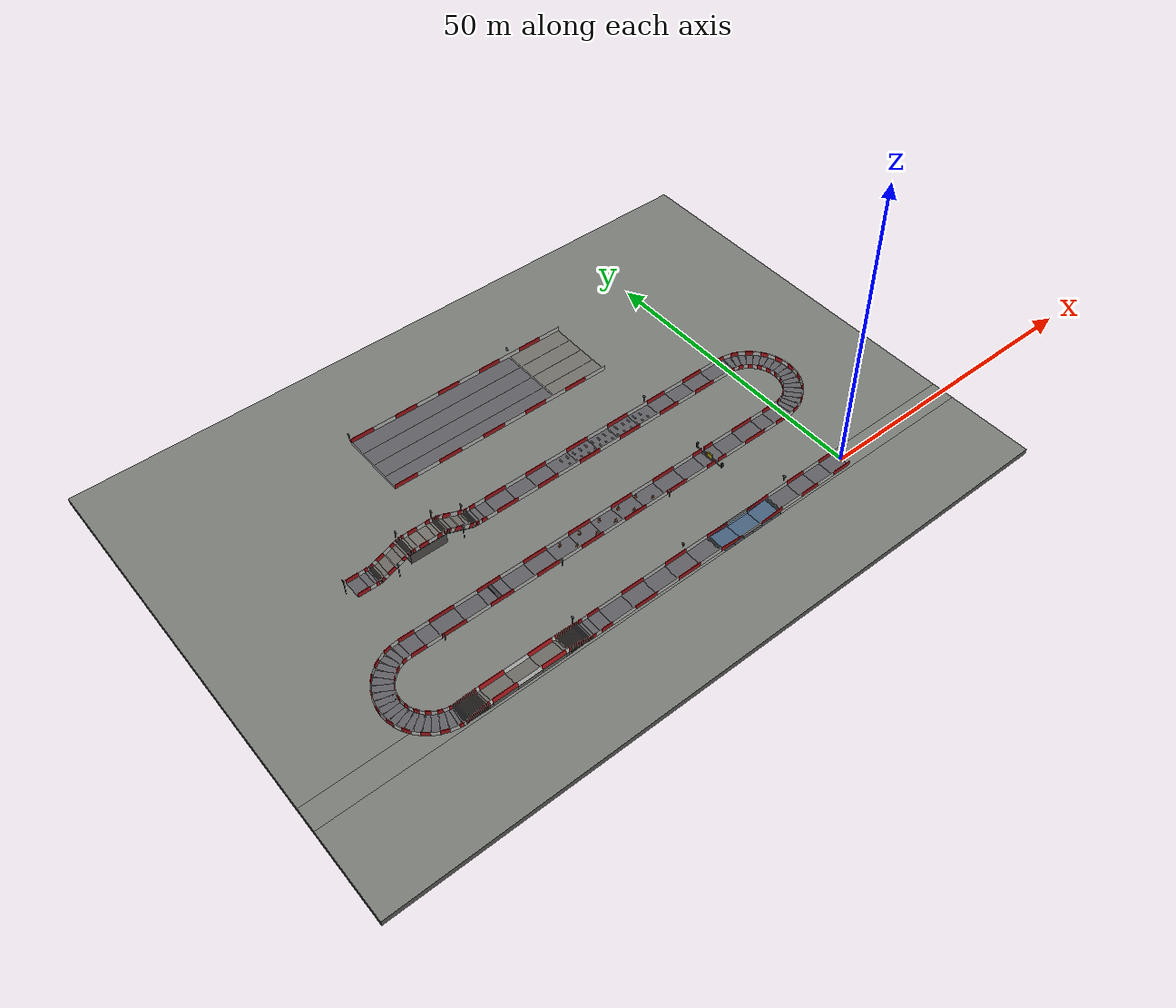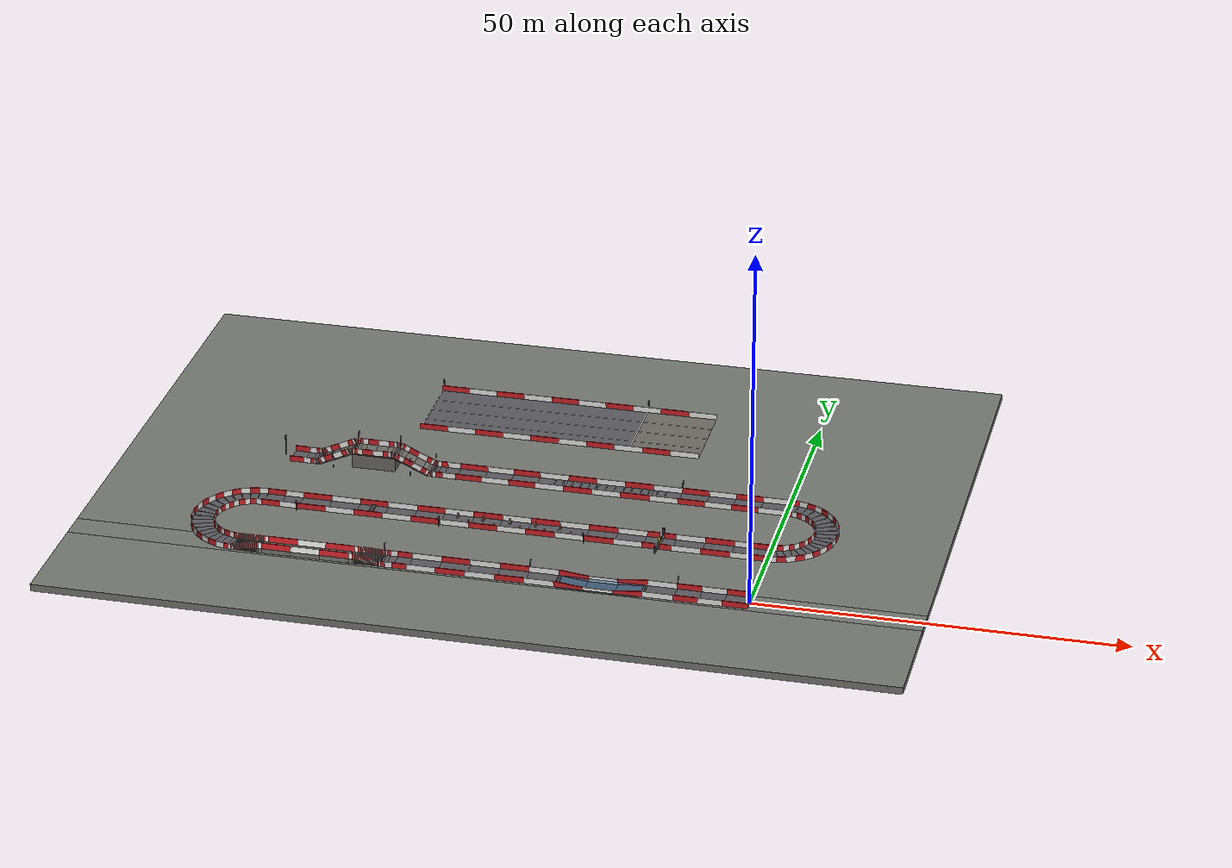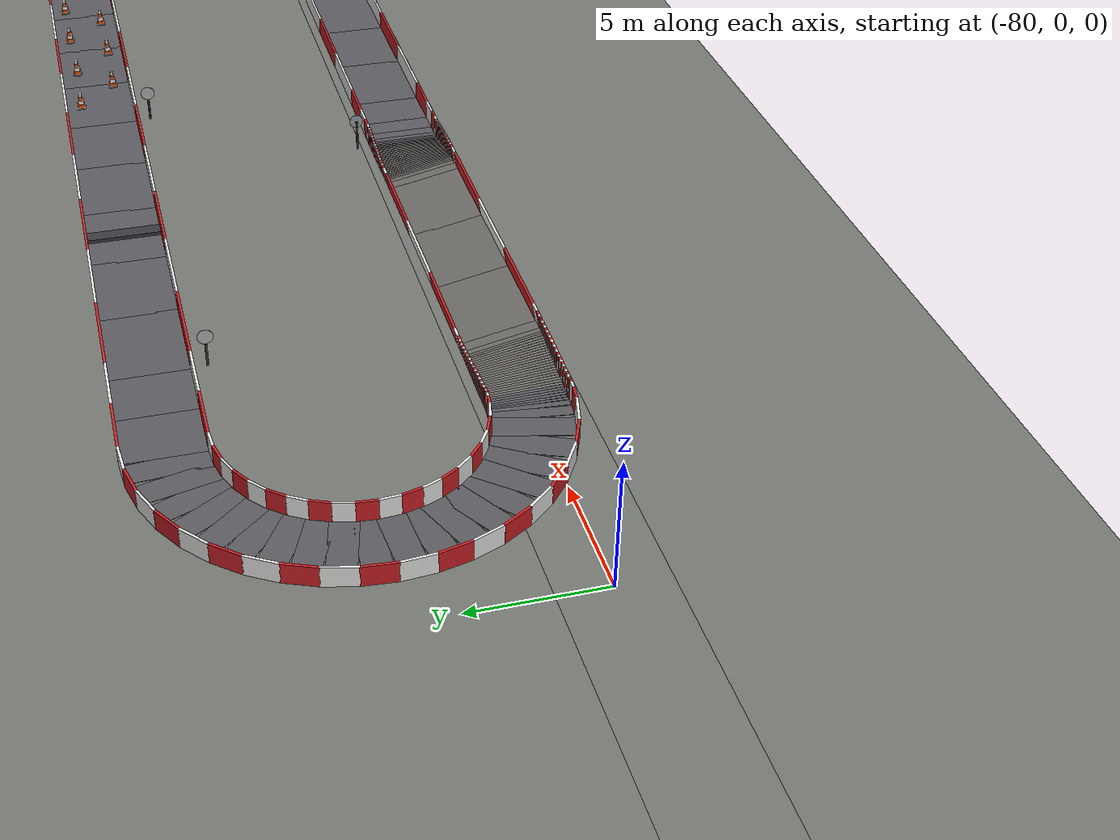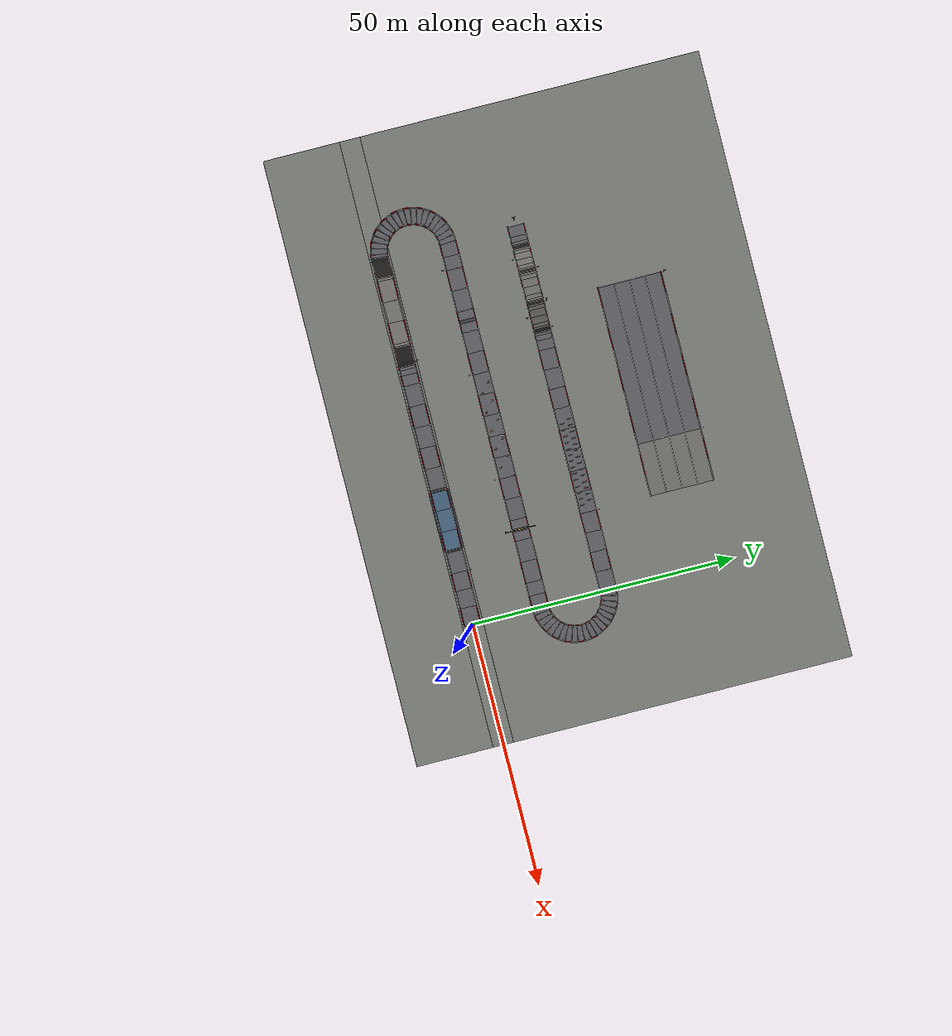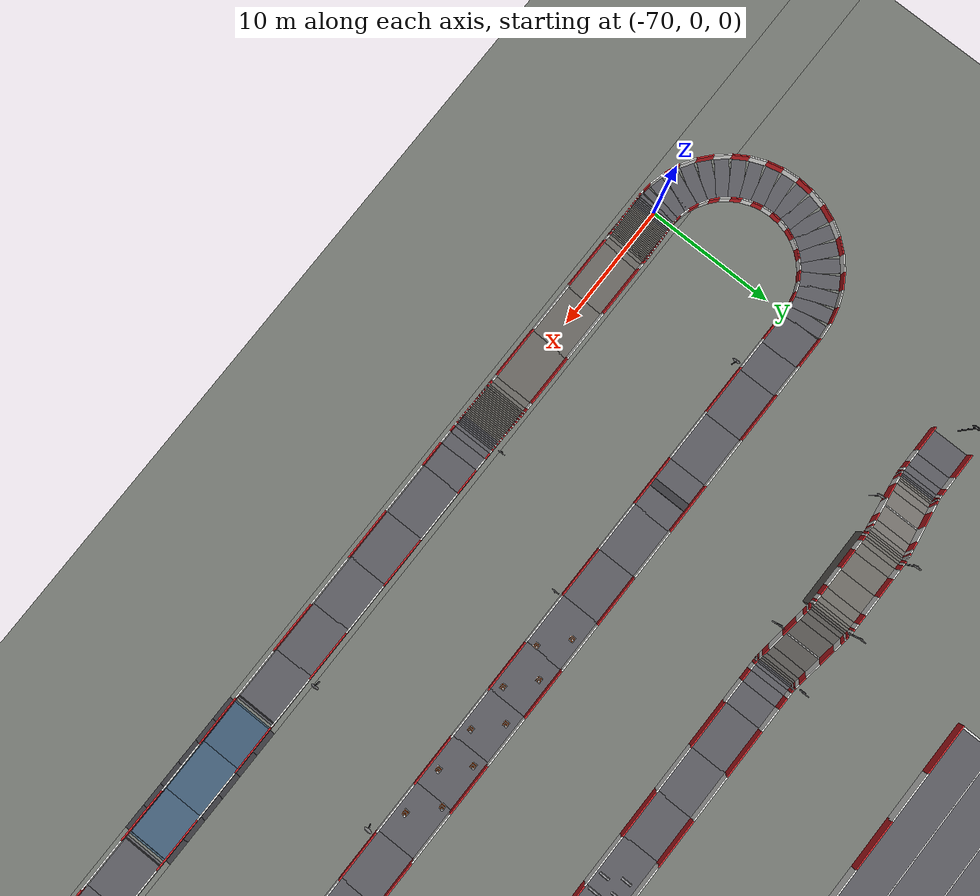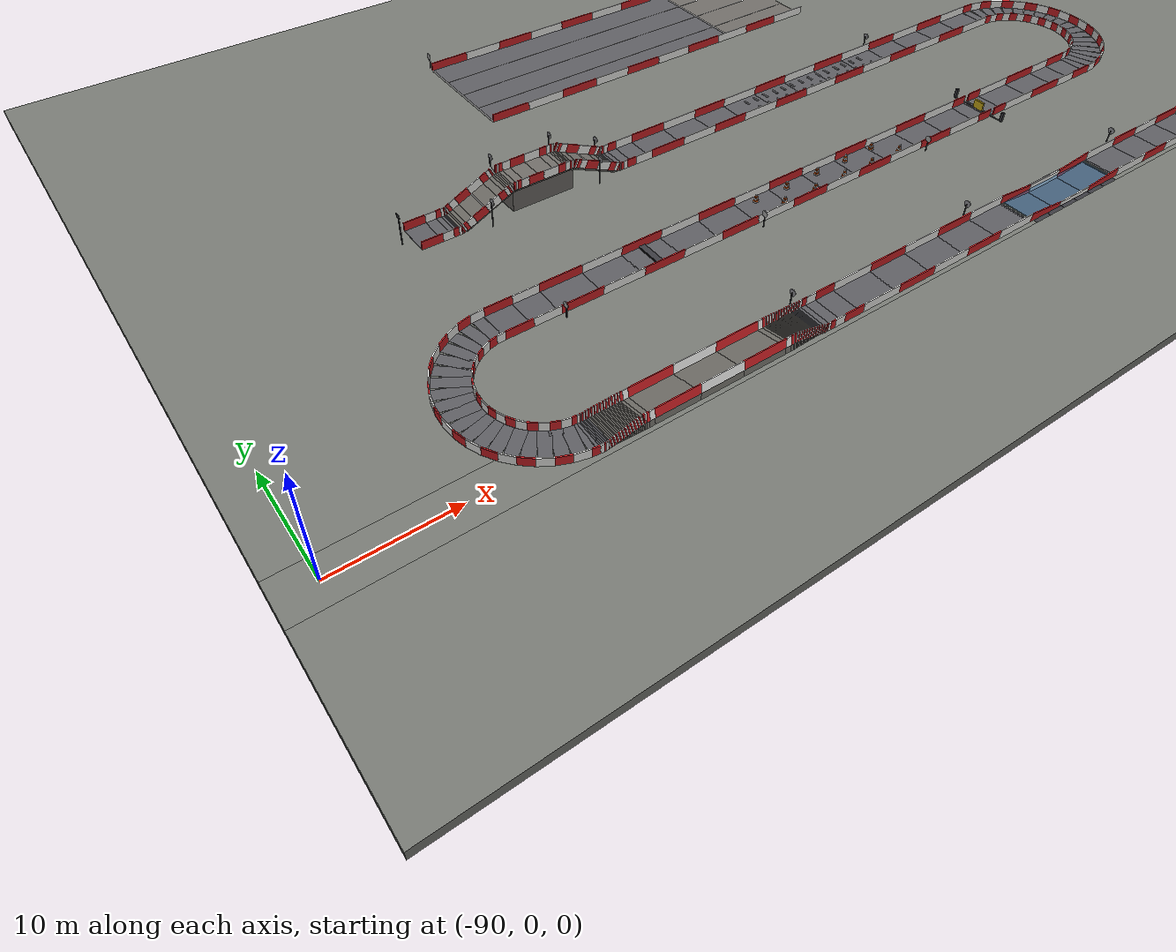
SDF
<?xml version="1.0" ?>
<sdf version="1.10">
  <world name="ika_parkur">
    <physics name="default_physics" type="ignored">
      <max_step_size>0.002</max_step_size>
      <real_time_factor>1</real_time_factor>
    </physics>
    <gravity>0 0 -9.8066</gravity>
    <plugin filename="gz-sim-physics-system" name="gz::sim::systems::Physics"/>
    <plugin filename="gz-sim-user-commands-system" name="gz::sim::systems::UserCommands"/>
    <plugin filename="gz-sim-scene-broadcaster-system" name="gz::sim::systems::SceneBroadcaster"/>
    <!-- Contact system: lets us score barrier and cone touches later. -->
    <plugin filename="gz-sim-contact-system" name="gz::sim::systems::Contact"/>
    <!-- Sensors system: required for any camera / lidar on your vehicle. -->
    <plugin filename="gz-sim-sensors-system" name="gz::sim::systems::Sensors">
      <render_engine>ogre2</render_engine>
    </plugin>
    <plugin filename="gz-sim-imu-system" name="gz::sim::systems::Imu"/>
    <plugin filename="gz-sim-buoyancy-system" name="gz::sim::systems::Buoyancy">
      <graded_buoyancy>
        <default_density>1000</default_density>
        <density_change>
          <above_depth>0</above_depth>
          <density>1</density>
        </density_change>
      </graded_buoyancy>
    </plugin>
    <scene>
      <ambient>0.55 0.55 0.55 1</ambient>
      <background>0.7 0.78 0.88 1</background>
      <shadows>true</shadows>
      <grid>false</grid>
    </scene>
    <light name="sun" type="directional">
      <cast_shadows>true</cast_shadows>
      <pose>0 0 30 0 0 0</pose>
      <diffuse>0.9 0.9 0.9 1</diffuse>
      <specular>0.25 0.25 0.25 1</specular>
      <attenuation>
        <range>1000</range>
        <constant>0.9</constant>
        <linear>0.01</linear>
        <quadratic>0.001</quadratic>
      </attenuation>
      <direction>-0.5 0.35 -0.9</direction>
    </light>
    <gui fullscreen="0">
      <plugin filename="MinimalScene" name="3D View">
        <gz-gui>
          <title>3D View</title>
          <property type="bool" key="showTitleBar">false</property>
          <property type="string" key="state">docked</property>
        </gz-gui>
        <engine>ogre2</engine>
        <scene>scene</scene>
        <ambient_light>0.55 0.55 0.55</ambient_light>
        <background_color>0.7 0.78 0.88</background_color>
        <camera_pose>-35 -46.844 72.044 0 0.785 1.571</camera_pose>
      </plugin>
      <plugin filename="GzSceneManager" name="Scene Manager"/>
      <plugin filename="InteractiveViewControl" name="Interactive view control"/>
      <plugin filename="CameraTracking" name="Camera Tracking"/>
      <plugin filename="MarkerManager" name="Marker manager"/>
      <plugin filename="SelectEntities" name="Select Entities"/>
      <plugin filename="Spawn" name="Spawn Entities"/>
      <plugin filename="EntityContextMenuPlugin" name="Entity context menu"/>
      <plugin filename="VisualizationCapabilities" name="Visualization Capabilities"/>
      <plugin filename="WorldControl" name="World control">
        <gz-gui>
          <title>World control</title>
          <property type="bool" key="showTitleBar">false</property>
          <property type="string" key="state">floating</property>
        </gz-gui>
        <!-- Pausing is controlled from the launch file (paused:=true), not here, so the two cannot disagree. -->
        <play_pause>true</play_pause>
        <step>true</step>
        <start_paused>false</start_paused>
      </plugin>
      <plugin filename="WorldStats" name="World stats">
        <gz-gui>
          <title>World stats</title>
          <property type="bool" key="showTitleBar">false</property>
          <property type="string" key="state">floating</property>
        </gz-gui>
        <sim_time>true</sim_time>
        <real_time>true</real_time>
        <real_time_factor>true</real_time_factor>
      </plugin>
      <plugin filename="ComponentInspector" name="Component inspector"/>
      <plugin filename="EntityTree" name="Entity tree"/>
    </gui>
    <model name="ground_south">
      <static>true</static>
      <pose>-35 -9.285 -0.52 0 0 0</pose>
      <link name="ground_south_link">
        <collision name="ground_south_link_collision">
          <geometry>
            <box>
              <size>116.199336 14.63 1</size>
            </box>
          </geometry>
          <surface>
            <friction>
              <ode>
                <mu>1</mu>
                <mu2>1</mu2>
              </ode>
            </friction>
            <contact>
              <ode>
                <kp>1000000</kp>
                <kd>1</kd>
              </ode>
            </contact>
          </surface>
        </collision>
        <visual name="ground_south_link_visual">
          <geometry>
            <box>
              <size>116.199336 14.63 1</size>
            </box>
          </geometry>
          <material>
            <ambient>0.45 0.46 0.44 1</ambient>
            <diffuse>0.45 0.46 0.44 1</diffuse>
            <specular>0.1 0.1 0.1 1</specular>
          </material>
        </visual>
      </link>
    </model>
    <model name="ground_north">
      <static>true</static>
      <pose>-35 34.485 -0.52 0 0 0</pose>
      <link name="ground_north_link">
        <collision name="ground_north_link_collision">
          <geometry>
            <box>
              <size>116.199336 65.03 1</size>
            </box>
          </geometry>
          <surface>
            <friction>
              <ode>
                <mu>1</mu>
                <mu2>1</mu2>
              </ode>
            </friction>
            <contact>
              <ode>
                <kp>1000000</kp>
                <kd>1</kd>
              </ode>
            </contact>
          </surface>
        </collision>
        <visual name="ground_north_link_visual">
          <geometry>
            <box>
              <size>116.199336 65.03 1</size>
            </box>
          </geometry>
          <material>
            <ambient>0.45 0.46 0.44 1</ambient>
            <diffuse>0.45 0.46 0.44 1</diffuse>
            <specular>0.1 0.1 0.1 1</specular>
          </material>
        </visual>
      </link>
    </model>
    <model name="ground_west">
      <static>true</static>
      <pose>-59.299834 0 -0.52 0 0 0</pose>
      <link name="ground_west_link">
        <collision name="ground_west_link_collision">
          <geometry>
            <box>
              <size>67.599668 3.94 1</size>
            </box>
          </geometry>
          <surface>
            <friction>
              <ode>
                <mu>1</mu>
                <mu2>1</mu2>
              </ode>
            </friction>
            <contact>
              <ode>
                <kp>1000000</kp>
                <kd>1</kd>
              </ode>
            </contact>
          </surface>
        </collision>
        <visual name="ground_west_link_visual">
          <geometry>
            <box>
              <size>67.599668 3.94 1</size>
            </box>
          </geometry>
          <material>
            <ambient>0.45 0.46 0.44 1</ambient>
            <diffuse>0.45 0.46 0.44 1</diffuse>
            <specular>0.1 0.1 0.1 1</specular>
          </material>
        </visual>
      </link>
    </model>
    <model name="ground_east">
      <static>true</static>
      <pose>4.299834 0 -0.52 0 0 0</pose>
      <link name="ground_east_link">
        <collision name="ground_east_link_collision">
          <geometry>
            <box>
              <size>37.599668 3.94 1</size>
            </box>
          </geometry>
          <surface>
            <friction>
              <ode>
                <mu>1</mu>
                <mu2>1</mu2>
              </ode>
            </friction>
            <contact>
              <ode>
                <kp>1000000</kp>
                <kd>1</kd>
              </ode>
            </contact>
          </surface>
        </collision>
        <visual name="ground_east_link_visual">
          <geometry>
            <box>
              <size>37.599668 3.94 1</size>
            </box>
          </geometry>
          <material>
            <ambient>0.45 0.46 0.44 1</ambient>
            <diffuse>0.45 0.46 0.44 1</diffuse>
            <specular>0.1 0.1 0.1 1</specular>
          </material>
        </visual>
      </link>
    </model>
    <model name="parkur_road">
      <static>true</static>
      <pose>0 0 0 0 0 0</pose>
      <link name="road_0000">
        <pose>-1.666667 0 -0.1 0 0 3.141593</pose>
        <collision name="road_0000_col">
          <geometry>
            <box>
              <size>3.4 3 0.2</size>
            </box>
          </geometry>
          <surface>
            <friction>
              <ode>
                <mu>1</mu>
                <mu2>1</mu2>
              </ode>
            </friction>
            <contact>
              <ode>
                <kp>1000000</kp>
                <kd>1</kd>
              </ode>
            </contact>
          </surface>
        </collision>
        <visual name="road_0000_vis">
          <geometry>
            <box>
              <size>3.4 3 0.2</size>
            </box>
          </geometry>
          <material>
            <ambient>0.35 0.35 0.37 1</ambient>
            <diffuse>0.35 0.35 0.37 1</diffuse>
            <specular>0.1 0.1 0.1 1</specular>
          </material>
        </visual>
      </link>
      <link name="road_0001">
        <pose>-5 0 -0.1 0 0 3.141593</pose>
        <collision name="road_0001_col">
          <geometry>
            <box>
              <size>3.4 3 0.2</size>
            </box>
          </geometry>
          <surface>
            <friction>
              <ode>
                <mu>1</mu>
                <mu2>1</mu2>
              </ode>
            </friction>
            <contact>
              <ode>
                <kp>1000000</kp>
                <kd>1</kd>
              </ode>
            </contact>
          </surface>
        </collision>
        <visual name="road_0001_vis">
          <geometry>
            <box>
              <size>3.4 3 0.2</size>
            </box>
          </geometry>
          <material>
            <ambient>0.35 0.35 0.37 1</ambient>
            <diffuse>0.35 0.35 0.37 1</diffuse>
            <specular>0.1 0.1 0.1 1</specular>
          </material>
        </visual>
      </link>
      <link name="road_0002">
        <pose>-8.333333 0 -0.1 0 0 3.141593</pose>
        <collision name="road_0002_col">
          <geometry>
            <box>
              <size>3.4 3 0.2</size>
            </box>
          </geometry>
          <surface>
            <friction>
              <ode>
                <mu>1</mu>
                <mu2>1</mu2>
              </ode>
            </friction>
            <contact>
              <ode>
                <kp>1000000</kp>
                <kd>1</kd>
              </ode>
            </contact>
          </surface>
        </collision>
        <visual name="road_0002_vis">
          <geometry>
            <box>
              <size>3.4 3 0.2</size>
            </box>
          </geometry>
          <material>
            <ambient>0.35 0.35 0.37 1</ambient>
            <diffuse>0.35 0.35 0.37 1</diffuse>
            <specular>0.1 0.1 0.1 1</specular>
          </material>
        </visual>
      </link>
      <link name="road_0003">
        <pose>-12 0 -0.1 0 0 3.141593</pose>
        <collision name="road_0003_col">
          <geometry>
            <box>
              <size>4.08 3 0.2</size>
            </box>
          </geometry>
          <surface>
            <friction>
              <ode>
                <mu>1</mu>
                <mu2>1</mu2>
              </ode>
            </friction>
            <contact>
              <ode>
                <kp>1000000</kp>
                <kd>1</kd>
              </ode>
            </contact>
          </surface>
        </collision>
        <visual name="road_0003_vis">
          <geometry>
            <box>
              <size>4.08 3 0.2</size>
            </box>
          </geometry>
          <material>
            <ambient>0.35 0.35 0.37 1</ambient>
            <diffuse>0.35 0.35 0.37 1</diffuse>
            <specular>0.1 0.1 0.1 1</specular>
          </material>
        </visual>
      </link>
      <link name="road_0004">
        <pose>-15.99005 0 -0.299504 0 0.099669 3.141593</pose>
        <collision name="road_0004_col">
          <geometry>
            <box>
              <size>4.100349 3 0.2</size>
            </box>
          </geometry>
          <surface>
            <friction>
              <ode>
                <mu>1</mu>
                <mu2>1</mu2>
              </ode>
            </friction>
            <contact>
              <ode>
                <kp>1000000</kp>
                <kd>1</kd>
              </ode>
            </contact>
          </surface>
        </collision>
        <visual name="road_0004_vis">
          <geometry>
            <box>
              <size>4.100349 3 0.2</size>
            </box>
          </geometry>
          <material>
            <ambient>0.35 0.35 0.37 1</ambient>
            <diffuse>0.35 0.35 0.37 1</diffuse>
            <specular>0.1 0.1 0.1 1</specular>
          </material>
        </visual>
      </link>
      <link name="road_0005">
        <pose>-20 0 -0.5 0 0 3.141593</pose>
        <collision name="road_0005_col">
          <geometry>
            <box>
              <size>4.08 3 0.2</size>
            </box>
          </geometry>
          <surface>
            <friction>
              <ode>
                <mu>1</mu>
                <mu2>1</mu2>
              </ode>
            </friction>
            <contact>
              <ode>
                <kp>1000000</kp>
                <kd>1</kd>
              </ode>
            </contact>
          </surface>
        </collision>
        <visual name="road_0005_vis">
          <geometry>
            <box>
              <size>4.08 3 0.2</size>
            </box>
          </geometry>
          <material>
            <ambient>0.35 0.35 0.37 1</ambient>
            <diffuse>0.35 0.35 0.37 1</diffuse>
            <specular>0.1 0.1 0.1 1</specular>
          </material>
        </visual>
      </link>
      <link name="road_0006">
        <pose>-24.00995 0 -0.299504 0 -0.099669 3.141593</pose>
        <collision name="road_0006_col">
          <geometry>
            <box>
              <size>4.100349 3 0.2</size>
            </box>
          </geometry>
          <surface>
            <friction>
              <ode>
                <mu>1</mu>
                <mu2>1</mu2>
              </ode>
            </friction>
            <contact>
              <ode>
                <kp>1000000</kp>
                <kd>1</kd>
              </ode>
            </contact>
          </surface>
        </collision>
        <visual name="road_0006_vis">
          <geometry>
            <box>
              <size>4.100349 3 0.2</size>
            </box>
          </geometry>
          <material>
            <ambient>0.35 0.35 0.37 1</ambient>
            <diffuse>0.35 0.35 0.37 1</diffuse>
            <specular>0.1 0.1 0.1 1</specular>
          </material>
        </visual>
      </link>
      <link name="road_0007">
        <pose>-28 0 -0.1 0 0 3.141593</pose>
        <collision name="road_0007_col">
          <geometry>
            <box>
              <size>4.08 3 0.2</size>
            </box>
          </geometry>
          <surface>
            <friction>
              <ode>
                <mu>1</mu>
                <mu2>1</mu2>
              </ode>
            </friction>
            <contact>
              <ode>
                <kp>1000000</kp>
                <kd>1</kd>
              </ode>
            </contact>
          </surface>
        </collision>
        <visual name="road_0007_vis">
          <geometry>
            <box>
              <size>4.08 3 0.2</size>
            </box>
          </geometry>
          <material>
            <ambient>0.35 0.35 0.37 1</ambient>
            <diffuse>0.35 0.35 0.37 1</diffuse>
            <specular>0.1 0.1 0.1 1</specular>
          </material>
        </visual>
      </link>
      <link name="road_0008">
        <pose>-32 0 -0.1 0 0 3.141593</pose>
        <collision name="road_0008_col">
          <geometry>
            <box>
              <size>4.08 3 0.2</size>
            </box>
          </geometry>
          <surface>
            <friction>
              <ode>
                <mu>1</mu>
                <mu2>1</mu2>
              </ode>
            </friction>
            <contact>
              <ode>
                <kp>1000000</kp>
                <kd>1</kd>
              </ode>
            </contact>
          </surface>
        </collision>
        <visual name="road_0008_vis">
          <geometry>
            <box>
              <size>4.08 3 0.2</size>
            </box>
          </geometry>
          <material>
            <ambient>0.35 0.35 0.37 1</ambient>
            <diffuse>0.35 0.35 0.37 1</diffuse>
            <specular>0.1 0.1 0.1 1</specular>
          </material>
        </visual>
      </link>
      <link name="road_0009">
        <pose>-36 0 -0.1 0 0 3.141593</pose>
        <collision name="road_0009_col">
          <geometry>
            <box>
              <size>4.08 3 0.2</size>
            </box>
          </geometry>
          <surface>
            <friction>
              <ode>
                <mu>1</mu>
                <mu2>1</mu2>
              </ode>
            </friction>
            <contact>
              <ode>
                <kp>1000000</kp>
                <kd>1</kd>
              </ode>
            </contact>
          </surface>
        </collision>
        <visual name="road_0009_vis">
          <geometry>
            <box>
              <size>4.08 3 0.2</size>
            </box>
          </geometry>
          <material>
            <ambient>0.35 0.35 0.37 1</ambient>
            <diffuse>0.35 0.35 0.37 1</diffuse>
            <specular>0.1 0.1 0.1 1</specular>
          </material>
        </visual>
      </link>
      <link name="road_0010">
        <pose>-40 0 -0.1 0 0 3.141593</pose>
        <collision name="road_0010_col">
          <geometry>
            <box>
              <size>4.08 3 0.2</size>
            </box>
          </geometry>
          <surface>
            <friction>
              <ode>
                <mu>1</mu>
                <mu2>1</mu2>
              </ode>
            </friction>
            <contact>
              <ode>
                <kp>1000000</kp>
                <kd>1</kd>
              </ode>
            </contact>
          </surface>
        </collision>
        <visual name="road_0010_vis">
          <geometry>
            <box>
              <size>4.08 3 0.2</size>
            </box>
          </geometry>
          <material>
            <ambient>0.35 0.35 0.37 1</ambient>
            <diffuse>0.35 0.35 0.37 1</diffuse>
            <specular>0.1 0.1 0.1 1</specular>
          </material>
        </visual>
      </link>
      <link name="road_0011">
        <pose>-44 0 -0.1 0 0 3.141593</pose>
        <collision name="road_0011_col">
          <geometry>
            <box>
              <size>4.08 3 0.2</size>
            </box>
          </geometry>
          <surface>
            <friction>
              <ode>
                <mu>1</mu>
                <mu2>1</mu2>
              </ode>
            </friction>
            <contact>
              <ode>
                <kp>1000000</kp>
                <kd>1</kd>
              </ode>
            </contact>
          </surface>
        </collision>
        <visual name="road_0011_vis">
          <geometry>
            <box>
              <size>4.08 3 0.2</size>
            </box>
          </geometry>
          <material>
            <ambient>0.35 0.35 0.37 1</ambient>
            <diffuse>0.35 0.35 0.37 1</diffuse>
            <specular>0.1 0.1 0.1 1</specular>
          </material>
        </visual>
      </link>
      <link name="road_0012">
        <pose>-47 0 -0.1 0 0 3.141593</pose>
        <collision name="road_0012_col">
          <geometry>
            <box>
              <size>2.04 3 0.2</size>
            </box>
          </geometry>
          <surface>
            <friction>
              <ode>
                <mu>1</mu>
                <mu2>1</mu2>
              </ode>
            </friction>
            <contact>
              <ode>
                <kp>1000000</kp>
                <kd>1</kd>
              </ode>
            </contact>
          </surface>
        </collision>
        <visual name="road_0012_vis">
          <geometry>
            <box>
              <size>2.04 3 0.2</size>
            </box>
          </geometry>
          <material>
            <ambient>0.35 0.35 0.37 1</ambient>
            <diffuse>0.35 0.35 0.37 1</diffuse>
            <specular>0.1 0.1 0.1 1</specular>
          </material>
        </visual>
      </link>
      <link name="road_0013">
        <pose>-48.5 0 -0.1 0 0 3.141593</pose>
        <collision name="road_0013_col">
          <geometry>
            <box>
              <size>1.02 3 0.2</size>
            </box>
          </geometry>
          <surface>
            <friction>
              <ode>
                <mu>1</mu>
                <mu2>1</mu2>
              </ode>
            </friction>
            <contact>
              <ode>
                <kp>1000000</kp>
                <kd>1</kd>
              </ode>
            </contact>
          </surface>
        </collision>
        <visual name="road_0013_vis">
          <geometry>
            <box>
              <size>1.02 3 0.2</size>
            </box>
          </geometry>
          <material>
            <ambient>0.35 0.35 0.37 1</ambient>
            <diffuse>0.35 0.35 0.37 1</diffuse>
            <specular>0.1 0.1 0.1 1</specular>
          </material>
        </visual>
      </link>
      <link name="road_0014">
        <pose>-49.25 0 -0.1 0 0 3.141593</pose>
        <collision name="road_0014_col">
          <geometry>
            <box>
              <size>0.51 3 0.2</size>
            </box>
          </geometry>
          <surface>
            <friction>
              <ode>
                <mu>1</mu>
                <mu2>1</mu2>
              </ode>
            </friction>
            <contact>
              <ode>
                <kp>1000000</kp>
                <kd>1</kd>
              </ode>
            </contact>
          </surface>
        </collision>
        <visual name="road_0014_vis">
          <geometry>
            <box>
              <size>0.51 3 0.2</size>
            </box>
          </geometry>
          <material>
            <ambient>0.35 0.35 0.37 1</ambient>
            <diffuse>0.35 0.35 0.37 1</diffuse>
            <specular>0.1 0.1 0.1 1</specular>
          </material>
        </visual>
      </link>
      <link name="road_0015">
        <pose>-49.625 0 -0.1 0 0 3.141593</pose>
        <collision name="road_0015_col">
          <geometry>
            <box>
              <size>0.255 3 0.2</size>
            </box>
          </geometry>
          <surface>
            <friction>
              <ode>
                <mu>1</mu>
                <mu2>1</mu2>
              </ode>
            </friction>
            <contact>
              <ode>
                <kp>1000000</kp>
                <kd>1</kd>
              </ode>
            </contact>
          </surface>
        </collision>
        <visual name="road_0015_vis">
          <geometry>
            <box>
              <size>0.255 3 0.2</size>
            </box>
          </geometry>
          <material>
            <ambient>0.35 0.35 0.37 1</ambient>
            <diffuse>0.35 0.35 0.37 1</diffuse>
            <specular>0.1 0.1 0.1 1</specular>
          </material>
        </visual>
      </link>
      <link name="road_0016">
        <pose>-49.8125 0 -0.1 0 0 3.141593</pose>
        <collision name="road_0016_col">
          <geometry>
            <box>
              <size>0.1275 3 0.2</size>
            </box>
          </geometry>
          <surface>
            <friction>
              <ode>
                <mu>1</mu>
                <mu2>1</mu2>
              </ode>
            </friction>
            <contact>
              <ode>
                <kp>1000000</kp>
                <kd>1</kd>
              </ode>
            </contact>
          </surface>
        </collision>
        <visual name="road_0016_vis">
          <geometry>
            <box>
              <size>0.1275 3 0.2</size>
            </box>
          </geometry>
          <material>
            <ambient>0.35 0.35 0.37 1</ambient>
            <diffuse>0.35 0.35 0.37 1</diffuse>
            <specular>0.1 0.1 0.1 1</specular>
          </material>
        </visual>
      </link>
      <link name="road_0017">
        <pose>-49.9375 0 -0.1 0 0 3.141593</pose>
        <collision name="road_0017_col">
          <geometry>
            <box>
              <size>0.1275 3 0.2</size>
            </box>
          </geometry>
          <surface>
            <friction>
              <ode>
                <mu>1</mu>
                <mu2>1</mu2>
              </ode>
            </friction>
            <contact>
              <ode>
                <kp>1000000</kp>
                <kd>1</kd>
              </ode>
            </contact>
          </surface>
        </collision>
        <visual name="road_0017_vis">
          <geometry>
            <box>
              <size>0.1275 3 0.2</size>
            </box>
          </geometry>
          <material>
            <ambient>0.35 0.35 0.37 1</ambient>
            <diffuse>0.35 0.35 0.37 1</diffuse>
            <specular>0.1 0.1 0.1 1</specular>
          </material>
        </visual>
      </link>
      <link name="road_0018">
        <pose>-50.072259 0 -0.093394 0 -0.097746 3.141593</pose>
        <collision name="road_0018_col">
          <geometry>
            <box>
              <size>0.128112 3 0.2</size>
            </box>
          </geometry>
          <surface>
            <friction>
              <ode>
                <mu>1</mu>
                <mu2>1</mu2>
              </ode>
            </friction>
            <contact>
              <ode>
                <kp>1000000</kp>
                <kd>1</kd>
              </ode>
            </contact>
          </surface>
        </collision>
        <visual name="road_0018_vis">
          <geometry>
            <box>
              <size>0.128112 3 0.2</size>
            </box>
          </geometry>
          <material>
            <ambient>0.35 0.35 0.37 1</ambient>
            <diffuse>0.35 0.35 0.37 1</diffuse>
            <specular>0.1 0.1 0.1 1</specular>
          </material>
        </visual>
      </link>
      <link name="road_0019">
        <pose>-50.198463 -0.000924 -0.093411 0.008225 -0.097746 3.141593</pose>
        <collision name="road_0019_col">
          <geometry>
            <box>
              <size>0.128112 3 0.224674</size>
            </box>
          </geometry>
          <surface>
            <friction>
              <ode>
                <mu>1</mu>
                <mu2>1</mu2>
              </ode>
            </friction>
            <contact>
              <ode>
                <kp>1000000</kp>
                <kd>1</kd>
              </ode>
            </contact>
          </surface>
        </collision>
        <visual name="road_0019_vis">
          <geometry>
            <box>
              <size>0.128112 3 0.224674</size>
            </box>
          </geometry>
          <material>
            <ambient>0.35 0.35 0.37 1</ambient>
            <diffuse>0.35 0.35 0.37 1</diffuse>
            <specular>0.1 0.1 0.1 1</specular>
          </material>
        </visual>
      </link>
      <link name="road_0020">
        <pose>-50.324665 -0.002051 -0.093418 0.01645 -0.097746 3.141593</pose>
        <collision name="road_0020_col">
          <geometry>
            <box>
              <size>0.128112 3 0.249347</size>
            </box>
          </geometry>
          <surface>
            <friction>
              <ode>
                <mu>1</mu>
                <mu2>1</mu2>
              </ode>
            </friction>
            <contact>
              <ode>
                <kp>1000000</kp>
                <kd>1</kd>
              </ode>
            </contact>
          </surface>
        </collision>
        <visual name="road_0020_vis">
          <geometry>
            <box>
              <size>0.128112 3 0.249347</size>
            </box>
          </geometry>
          <material>
            <ambient>0.35 0.35 0.37 1</ambient>
            <diffuse>0.35 0.35 0.37 1</diffuse>
            <specular>0.1 0.1 0.1 1</specular>
          </material>
        </visual>
      </link>
      <link name="road_0021">
        <pose>-50.450867 -0.00338 -0.093412 0.024674 -0.097746 3.141593</pose>
        <collision name="road_0021_col">
          <geometry>
            <box>
              <size>0.128112 3 0.274016</size>
            </box>
          </geometry>
          <surface>
            <friction>
              <ode>
                <mu>1</mu>
                <mu2>1</mu2>
              </ode>
            </friction>
            <contact>
              <ode>
                <kp>1000000</kp>
                <kd>1</kd>
              </ode>
            </contact>
          </surface>
        </collision>
        <visual name="road_0021_vis">
          <geometry>
            <box>
              <size>0.128112 3 0.274016</size>
            </box>
          </geometry>
          <material>
            <ambient>0.35 0.35 0.37 1</ambient>
            <diffuse>0.35 0.35 0.37 1</diffuse>
            <specular>0.1 0.1 0.1 1</specular>
          </material>
        </visual>
      </link>
      <link name="road_0022">
        <pose>-50.577066 -0.004912 -0.093389 0.032899 -0.097746 3.141593</pose>
        <collision name="road_0022_col">
          <geometry>
            <box>
              <size>0.128112 3 0.29868</size>
            </box>
          </geometry>
          <surface>
            <friction>
              <ode>
                <mu>1</mu>
                <mu2>1</mu2>
              </ode>
            </friction>
            <contact>
              <ode>
                <kp>1000000</kp>
                <kd>1</kd>
              </ode>
            </contact>
          </surface>
        </collision>
        <visual name="road_0022_vis">
          <geometry>
            <box>
              <size>0.128112 3 0.29868</size>
            </box>
          </geometry>
          <material>
            <ambient>0.42 0.41 0.39 1</ambient>
            <diffuse>0.42 0.41 0.39 1</diffuse>
            <specular>0.1 0.1 0.1 1</specular>
          </material>
        </visual>
      </link>
      <link name="road_0023">
        <pose>-50.703264 -0.006647 -0.093346 0.041124 -0.097746 3.141593</pose>
        <collision name="road_0023_col">
          <geometry>
            <box>
              <size>0.128112 3 0.323337</size>
            </box>
          </geometry>
          <surface>
            <friction>
              <ode>
                <mu>1</mu>
                <mu2>1</mu2>
              </ode>
            </friction>
            <contact>
              <ode>
                <kp>1000000</kp>
                <kd>1</kd>
              </ode>
            </contact>
          </surface>
        </collision>
        <visual name="road_0023_vis">
          <geometry>
            <box>
              <size>0.128112 3 0.323337</size>
            </box>
          </geometry>
          <material>
            <ambient>0.42 0.41 0.39 1</ambient>
            <diffuse>0.42 0.41 0.39 1</diffuse>
            <specular>0.1 0.1 0.1 1</specular>
          </material>
        </visual>
      </link>
      <link name="road_0024">
        <pose>-50.829459 -0.008583 -0.09328 0.049349 -0.097746 3.141593</pose>
        <collision name="road_0024_col">
          <geometry>
            <box>
              <size>0.128112 3 0.347987</size>
            </box>
          </geometry>
          <surface>
            <friction>
              <ode>
                <mu>1</mu>
                <mu2>1</mu2>
              </ode>
            </friction>
            <contact>
              <ode>
                <kp>1000000</kp>
                <kd>1</kd>
              </ode>
            </contact>
          </surface>
        </collision>
        <visual name="road_0024_vis">
          <geometry>
            <box>
              <size>0.128112 3 0.347987</size>
            </box>
          </geometry>
          <material>
            <ambient>0.42 0.41 0.39 1</ambient>
            <diffuse>0.42 0.41 0.39 1</diffuse>
            <specular>0.1 0.1 0.1 1</specular>
          </material>
        </visual>
      </link>
      <link name="road_0025">
        <pose>-50.955652 -0.010721 -0.093187 0.057574 -0.097746 3.141593</pose>
        <collision name="road_0025_col">
          <geometry>
            <box>
              <size>0.128112 3 0.372626</size>
            </box>
          </geometry>
          <surface>
            <friction>
              <ode>
                <mu>1</mu>
                <mu2>1</mu2>
              </ode>
            </friction>
            <contact>
              <ode>
                <kp>1000000</kp>
                <kd>1</kd>
              </ode>
            </contact>
          </surface>
        </collision>
        <visual name="road_0025_vis">
          <geometry>
            <box>
              <size>0.128112 3 0.372626</size>
            </box>
          </geometry>
          <material>
            <ambient>0.42 0.41 0.39 1</ambient>
            <diffuse>0.42 0.41 0.39 1</diffuse>
            <specular>0.1 0.1 0.1 1</specular>
          </material>
        </visual>
      </link>
      <link name="road_0026">
        <pose>-51.081842 -0.01306 -0.093064 0.065799 -0.097746 3.141593</pose>
        <collision name="road_0026_col">
          <geometry>
            <box>
              <size>0.128112 3 0.397253</size>
            </box>
          </geometry>
          <surface>
            <friction>
              <ode>
                <mu>1</mu>
                <mu2>1</mu2>
              </ode>
            </friction>
            <contact>
              <ode>
                <kp>1000000</kp>
                <kd>1</kd>
              </ode>
            </contact>
          </surface>
        </collision>
        <visual name="road_0026_vis">
          <geometry>
            <box>
              <size>0.128112 3 0.397253</size>
            </box>
          </geometry>
          <material>
            <ambient>0.42 0.41 0.39 1</ambient>
            <diffuse>0.42 0.41 0.39 1</diffuse>
            <specular>0.1 0.1 0.1 1</specular>
          </material>
        </visual>
      </link>
      <link name="road_0027">
        <pose>-51.208029 -0.0156 -0.092908 0.074023 -0.097746 3.141593</pose>
        <collision name="road_0027_col">
          <geometry>
            <box>
              <size>0.128112 3 0.421867</size>
            </box>
          </geometry>
          <surface>
            <friction>
              <ode>
                <mu>1</mu>
                <mu2>1</mu2>
              </ode>
            </friction>
            <contact>
              <ode>
                <kp>1000000</kp>
                <kd>1</kd>
              </ode>
            </contact>
          </surface>
        </collision>
        <visual name="road_0027_vis">
          <geometry>
            <box>
              <size>0.128112 3 0.421867</size>
            </box>
          </geometry>
          <material>
            <ambient>0.42 0.41 0.39 1</ambient>
            <diffuse>0.42 0.41 0.39 1</diffuse>
            <specular>0.1 0.1 0.1 1</specular>
          </material>
        </visual>
      </link>
      <link name="road_0028">
        <pose>-51.334212 -0.01834 -0.092715 0.082248 -0.097746 3.141593</pose>
        <collision name="road_0028_col">
          <geometry>
            <box>
              <size>0.128112 3 0.446466</size>
            </box>
          </geometry>
          <surface>
            <friction>
              <ode>
                <mu>1</mu>
                <mu2>1</mu2>
              </ode>
            </friction>
            <contact>
              <ode>
                <kp>1000000</kp>
                <kd>1</kd>
              </ode>
            </contact>
          </surface>
        </collision>
        <visual name="road_0028_vis">
          <geometry>
            <box>
              <size>0.128112 3 0.446466</size>
            </box>
          </geometry>
          <material>
            <ambient>0.42 0.41 0.39 1</ambient>
            <diffuse>0.42 0.41 0.39 1</diffuse>
            <specular>0.1 0.1 0.1 1</specular>
          </material>
        </visual>
      </link>
      <link name="road_0029">
        <pose>-51.460391 -0.02128 -0.092483 0.090473 -0.097746 3.141593</pose>
        <collision name="road_0029_col">
          <geometry>
            <box>
              <size>0.128112 3 0.471049</size>
            </box>
          </geometry>
          <surface>
            <friction>
              <ode>
                <mu>1</mu>
                <mu2>1</mu2>
              </ode>
            </friction>
            <contact>
              <ode>
                <kp>1000000</kp>
                <kd>1</kd>
              </ode>
            </contact>
          </surface>
        </collision>
        <visual name="road_0029_vis">
          <geometry>
            <box>
              <size>0.128112 3 0.471049</size>
            </box>
          </geometry>
          <material>
            <ambient>0.42 0.41 0.39 1</ambient>
            <diffuse>0.42 0.41 0.39 1</diffuse>
            <specular>0.1 0.1 0.1 1</specular>
          </material>
        </visual>
      </link>
      <link name="road_0030">
        <pose>-51.586566 -0.024418 -0.092208 0.098698 -0.097746 3.141593</pose>
        <collision name="road_0030_col">
          <geometry>
            <box>
              <size>0.128112 3 0.495613</size>
            </box>
          </geometry>
          <surface>
            <friction>
              <ode>
                <mu>1</mu>
                <mu2>1</mu2>
              </ode>
            </friction>
            <contact>
              <ode>
                <kp>1000000</kp>
                <kd>1</kd>
              </ode>
            </contact>
          </surface>
        </collision>
        <visual name="road_0030_vis">
          <geometry>
            <box>
              <size>0.128112 3 0.495613</size>
            </box>
          </geometry>
          <material>
            <ambient>0.42 0.41 0.39 1</ambient>
            <diffuse>0.42 0.41 0.39 1</diffuse>
            <specular>0.1 0.1 0.1 1</specular>
          </material>
        </visual>
      </link>
      <link name="road_0031">
        <pose>-51.712736 -0.027755 -0.091886 0.106923 -0.097746 3.141593</pose>
        <collision name="road_0031_col">
          <geometry>
            <box>
              <size>0.128112 3 0.520157</size>
            </box>
          </geometry>
          <surface>
            <friction>
              <ode>
                <mu>1</mu>
                <mu2>1</mu2>
              </ode>
            </friction>
            <contact>
              <ode>
                <kp>1000000</kp>
                <kd>1</kd>
              </ode>
            </contact>
          </surface>
        </collision>
        <visual name="road_0031_vis">
          <geometry>
            <box>
              <size>0.128112 3 0.520157</size>
            </box>
          </geometry>
          <material>
            <ambient>0.42 0.41 0.39 1</ambient>
            <diffuse>0.42 0.41 0.39 1</diffuse>
            <specular>0.1 0.1 0.1 1</specular>
          </material>
        </visual>
      </link>
      <link name="road_0032">
        <pose>-51.838902 -0.03129 -0.091515 0.115147 -0.097746 3.141593</pose>
        <collision name="road_0032_col">
          <geometry>
            <box>
              <size>0.128112 3 0.544679</size>
            </box>
          </geometry>
          <surface>
            <friction>
              <ode>
                <mu>1</mu>
                <mu2>1</mu2>
              </ode>
            </friction>
            <contact>
              <ode>
                <kp>1000000</kp>
                <kd>1</kd>
              </ode>
            </contact>
          </surface>
        </collision>
        <visual name="road_0032_vis">
          <geometry>
            <box>
              <size>0.128112 3 0.544679</size>
            </box>
          </geometry>
          <material>
            <ambient>0.42 0.41 0.39 1</ambient>
            <diffuse>0.42 0.41 0.39 1</diffuse>
            <specular>0.1 0.1 0.1 1</specular>
          </material>
        </visual>
      </link>
      <link name="road_0033">
        <pose>-51.965062 -0.035021 -0.091091 0.123372 -0.097746 3.141593</pose>
        <collision name="road_0033_col">
          <geometry>
            <box>
              <size>0.128112 3 0.569178</size>
            </box>
          </geometry>
          <surface>
            <friction>
              <ode>
                <mu>1</mu>
                <mu2>1</mu2>
              </ode>
            </friction>
            <contact>
              <ode>
                <kp>1000000</kp>
                <kd>1</kd>
              </ode>
            </contact>
          </surface>
        </collision>
        <visual name="road_0033_vis">
          <geometry>
            <box>
              <size>0.128112 3 0.569178</size>
            </box>
          </geometry>
          <material>
            <ambient>0.42 0.41 0.39 1</ambient>
            <diffuse>0.42 0.41 0.39 1</diffuse>
            <specular>0.1 0.1 0.1 1</specular>
          </material>
        </visual>
      </link>
      <link name="road_0034">
        <pose>-52.091217 -0.038949 -0.09061 0.131597 -0.097746 3.141593</pose>
        <collision name="road_0034_col">
          <geometry>
            <box>
              <size>0.128112 3 0.593653</size>
            </box>
          </geometry>
          <surface>
            <friction>
              <ode>
                <mu>1</mu>
                <mu2>1</mu2>
              </ode>
            </friction>
            <contact>
              <ode>
                <kp>1000000</kp>
                <kd>1</kd>
              </ode>
            </contact>
          </surface>
        </collision>
        <visual name="road_0034_vis">
          <geometry>
            <box>
              <size>0.128112 3 0.593653</size>
            </box>
          </geometry>
          <material>
            <ambient>0.42 0.41 0.39 1</ambient>
            <diffuse>0.42 0.41 0.39 1</diffuse>
            <specular>0.1 0.1 0.1 1</specular>
          </material>
        </visual>
      </link>
      <link name="road_0035">
        <pose>-52.217366 -0.043071 -0.090071 0.139822 -0.097746 3.141593</pose>
        <collision name="road_0035_col">
          <geometry>
            <box>
              <size>0.128112 3 0.6181</size>
            </box>
          </geometry>
          <surface>
            <friction>
              <ode>
                <mu>1</mu>
                <mu2>1</mu2>
              </ode>
            </friction>
            <contact>
              <ode>
                <kp>1000000</kp>
                <kd>1</kd>
              </ode>
            </contact>
          </surface>
        </collision>
        <visual name="road_0035_vis">
          <geometry>
            <box>
              <size>0.128112 3 0.6181</size>
            </box>
          </geometry>
          <material>
            <ambient>0.42 0.41 0.39 1</ambient>
            <diffuse>0.42 0.41 0.39 1</diffuse>
            <specular>0.1 0.1 0.1 1</specular>
          </material>
        </visual>
      </link>
      <link name="road_0036">
        <pose>-52.343509 -0.047388 -0.089469 0.148047 -0.097746 3.141593</pose>
        <collision name="road_0036_col">
          <geometry>
            <box>
              <size>0.128112 3 0.642519</size>
            </box>
          </geometry>
          <surface>
            <friction>
              <ode>
                <mu>1</mu>
                <mu2>1</mu2>
              </ode>
            </friction>
            <contact>
              <ode>
                <kp>1000000</kp>
                <kd>1</kd>
              </ode>
            </contact>
          </surface>
        </collision>
        <visual name="road_0036_vis">
          <geometry>
            <box>
              <size>0.128112 3 0.642519</size>
            </box>
          </geometry>
          <material>
            <ambient>0.42 0.41 0.39 1</ambient>
            <diffuse>0.42 0.41 0.39 1</diffuse>
            <specular>0.1 0.1 0.1 1</specular>
          </material>
        </visual>
      </link>
      <link name="road_0037">
        <pose>-52.469645 -0.051898 -0.088802 0.156271 -0.097746 3.141593</pose>
        <collision name="road_0037_col">
          <geometry>
            <box>
              <size>0.128112 3 0.666909</size>
            </box>
          </geometry>
          <surface>
            <friction>
              <ode>
                <mu>1</mu>
                <mu2>1</mu2>
              </ode>
            </friction>
            <contact>
              <ode>
                <kp>1000000</kp>
                <kd>1</kd>
              </ode>
            </contact>
          </surface>
        </collision>
        <visual name="road_0037_vis">
          <geometry>
            <box>
              <size>0.128112 3 0.666909</size>
            </box>
          </geometry>
          <material>
            <ambient>0.42 0.41 0.39 1</ambient>
            <diffuse>0.42 0.41 0.39 1</diffuse>
            <specular>0.1 0.1 0.1 1</specular>
          </material>
        </visual>
      </link>
      <link name="road_0038">
        <pose>-52.595775 -0.056599 -0.088066 0.164496 -0.097746 3.141593</pose>
        <collision name="road_0038_col">
          <geometry>
            <box>
              <size>0.128112 3 0.691266</size>
            </box>
          </geometry>
          <surface>
            <friction>
              <ode>
                <mu>1</mu>
                <mu2>1</mu2>
              </ode>
            </friction>
            <contact>
              <ode>
                <kp>1000000</kp>
                <kd>1</kd>
              </ode>
            </contact>
          </surface>
        </collision>
        <visual name="road_0038_vis">
          <geometry>
            <box>
              <size>0.128112 3 0.691266</size>
            </box>
          </geometry>
          <material>
            <ambient>0.42 0.41 0.39 1</ambient>
            <diffuse>0.42 0.41 0.39 1</diffuse>
            <specular>0.1 0.1 0.1 1</specular>
          </material>
        </visual>
      </link>
      <link name="road_0039">
        <pose>-52.721898 -0.061492 -0.087258 0.172721 -0.097746 3.141593</pose>
        <collision name="road_0039_col">
          <geometry>
            <box>
              <size>0.128112 3 0.715591</size>
            </box>
          </geometry>
          <surface>
            <friction>
              <ode>
                <mu>1</mu>
                <mu2>1</mu2>
              </ode>
            </friction>
            <contact>
              <ode>
                <kp>1000000</kp>
                <kd>1</kd>
              </ode>
            </contact>
          </surface>
        </collision>
        <visual name="road_0039_vis">
          <geometry>
            <box>
              <size>0.128112 3 0.715591</size>
            </box>
          </geometry>
          <material>
            <ambient>0.42 0.41 0.39 1</ambient>
            <diffuse>0.42 0.41 0.39 1</diffuse>
            <specular>0.1 0.1 0.1 1</specular>
          </material>
        </visual>
      </link>
      <link name="road_0040">
        <pose>-52.848013 -0.066574 -0.086375 0.180946 -0.097746 3.141593</pose>
        <collision name="road_0040_col">
          <geometry>
            <box>
              <size>0.128112 3 0.73988</size>
            </box>
          </geometry>
          <surface>
            <friction>
              <ode>
                <mu>1</mu>
                <mu2>1</mu2>
              </ode>
            </friction>
            <contact>
              <ode>
                <kp>1000000</kp>
                <kd>1</kd>
              </ode>
            </contact>
          </surface>
        </collision>
        <visual name="road_0040_vis">
          <geometry>
            <box>
              <size>0.128112 3 0.73988</size>
            </box>
          </geometry>
          <material>
            <ambient>0.42 0.41 0.39 1</ambient>
            <diffuse>0.42 0.41 0.39 1</diffuse>
            <specular>0.1 0.1 0.1 1</specular>
          </material>
        </visual>
      </link>
      <link name="road_0041">
        <pose>-52.974121 -0.071846 -0.085414 0.189171 -0.097746 3.141593</pose>
        <collision name="road_0041_col">
          <geometry>
            <box>
              <size>0.128112 3 0.764133</size>
            </box>
          </geometry>
          <surface>
            <friction>
              <ode>
                <mu>1</mu>
                <mu2>1</mu2>
              </ode>
            </friction>
            <contact>
              <ode>
                <kp>1000000</kp>
                <kd>1</kd>
              </ode>
            </contact>
          </surface>
        </collision>
        <visual name="road_0041_vis">
          <geometry>
            <box>
              <size>0.128112 3 0.764133</size>
            </box>
          </geometry>
          <material>
            <ambient>0.42 0.41 0.39 1</ambient>
            <diffuse>0.42 0.41 0.39 1</diffuse>
            <specular>0.1 0.1 0.1 1</specular>
          </material>
        </visual>
      </link>
      <link name="road_0042">
        <pose>-53.0625 -0.077304 -0.092345 0.197396 0 3.141593</pose>
        <collision name="road_0042_col">
          <geometry>
            <box>
              <size>0.1275 3 0.788348</size>
            </box>
          </geometry>
          <surface>
            <friction>
              <ode>
                <mu>1</mu>
                <mu2>1</mu2>
              </ode>
            </friction>
            <contact>
              <ode>
                <kp>1000000</kp>
                <kd>1</kd>
              </ode>
            </contact>
          </surface>
        </collision>
        <visual name="road_0042_vis">
          <geometry>
            <box>
              <size>0.1275 3 0.788348</size>
            </box>
          </geometry>
          <material>
            <ambient>0.42 0.41 0.39 1</ambient>
            <diffuse>0.42 0.41 0.39 1</diffuse>
            <specular>0.1 0.1 0.1 1</specular>
          </material>
        </visual>
      </link>
      <link name="road_0043">
        <pose>-53.1875 -0.077304 -0.092345 0.197396 0 3.141593</pose>
        <collision name="road_0043_col">
          <geometry>
            <box>
              <size>0.1275 3 0.788348</size>
            </box>
          </geometry>
          <surface>
            <friction>
              <ode>
                <mu>1</mu>
                <mu2>1</mu2>
              </ode>
            </friction>
            <contact>
              <ode>
                <kp>1000000</kp>
                <kd>1</kd>
              </ode>
            </contact>
          </surface>
        </collision>
        <visual name="road_0043_vis">
          <geometry>
            <box>
              <size>0.1275 3 0.788348</size>
            </box>
          </geometry>
          <material>
            <ambient>0.42 0.41 0.39 1</ambient>
            <diffuse>0.42 0.41 0.39 1</diffuse>
            <specular>0.1 0.1 0.1 1</specular>
          </material>
        </visual>
      </link>
      <link name="road_0044">
        <pose>-53.375 -0.077304 -0.092345 0.197396 0 3.141593</pose>
        <collision name="road_0044_col">
          <geometry>
            <box>
              <size>0.255 3 0.788348</size>
            </box>
          </geometry>
          <surface>
            <friction>
              <ode>
                <mu>1</mu>
                <mu2>1</mu2>
              </ode>
            </friction>
            <contact>
              <ode>
                <kp>1000000</kp>
                <kd>1</kd>
              </ode>
            </contact>
          </surface>
        </collision>
        <visual name="road_0044_vis">
          <geometry>
            <box>
              <size>0.255 3 0.788348</size>
            </box>
          </geometry>
          <material>
            <ambient>0.42 0.41 0.39 1</ambient>
            <diffuse>0.42 0.41 0.39 1</diffuse>
            <specular>0.1 0.1 0.1 1</specular>
          </material>
        </visual>
      </link>
      <link name="road_0045">
        <pose>-53.75 -0.077304 -0.092345 0.197396 0 3.141593</pose>
        <collision name="road_0045_col">
          <geometry>
            <box>
              <size>0.51 3 0.788348</size>
            </box>
          </geometry>
          <surface>
            <friction>
              <ode>
                <mu>1</mu>
                <mu2>1</mu2>
              </ode>
            </friction>
            <contact>
              <ode>
                <kp>1000000</kp>
                <kd>1</kd>
              </ode>
            </contact>
          </surface>
        </collision>
        <visual name="road_0045_vis">
          <geometry>
            <box>
              <size>0.51 3 0.788348</size>
            </box>
          </geometry>
          <material>
            <ambient>0.42 0.41 0.39 1</ambient>
            <diffuse>0.42 0.41 0.39 1</diffuse>
            <specular>0.1 0.1 0.1 1</specular>
          </material>
        </visual>
      </link>
      <link name="road_0046">
        <pose>-56 -0.077304 -0.092345 0.197396 0 3.141593</pose>
        <collision name="road_0046_col">
          <geometry>
            <box>
              <size>4.08 3 0.788348</size>
            </box>
          </geometry>
          <surface>
            <friction>
              <ode>
                <mu>1</mu>
                <mu2>1</mu2>
              </ode>
            </friction>
            <contact>
              <ode>
                <kp>1000000</kp>
                <kd>1</kd>
              </ode>
            </contact>
          </surface>
        </collision>
        <visual name="road_0046_vis">
          <geometry>
            <box>
              <size>4.08 3 0.788348</size>
            </box>
          </geometry>
          <material>
            <ambient>0.42 0.41 0.39 1</ambient>
            <diffuse>0.42 0.41 0.39 1</diffuse>
            <specular>0.1 0.1 0.1 1</specular>
          </material>
        </visual>
      </link>
      <link name="road_0047">
        <pose>-60 -0.077304 -0.092345 0.197396 0 3.141593</pose>
        <collision name="road_0047_col">
          <geometry>
            <box>
              <size>4.08 3 0.788348</size>
            </box>
          </geometry>
          <surface>
            <friction>
              <ode>
                <mu>1</mu>
                <mu2>1</mu2>
              </ode>
            </friction>
            <contact>
              <ode>
                <kp>1000000</kp>
                <kd>1</kd>
              </ode>
            </contact>
          </surface>
        </collision>
        <visual name="road_0047_vis">
          <geometry>
            <box>
              <size>4.08 3 0.788348</size>
            </box>
          </geometry>
          <material>
            <ambient>0.42 0.41 0.39 1</ambient>
            <diffuse>0.42 0.41 0.39 1</diffuse>
            <specular>0.1 0.1 0.1 1</specular>
          </material>
        </visual>
      </link>
      <link name="road_0048">
        <pose>-64 -0.077304 -0.092345 0.197396 0 3.141593</pose>
        <collision name="road_0048_col">
          <geometry>
            <box>
              <size>4.08 3 0.788348</size>
            </box>
          </geometry>
          <surface>
            <friction>
              <ode>
                <mu>1</mu>
                <mu2>1</mu2>
              </ode>
            </friction>
            <contact>
              <ode>
                <kp>1000000</kp>
                <kd>1</kd>
              </ode>
            </contact>
          </surface>
        </collision>
        <visual name="road_0048_vis">
          <geometry>
            <box>
              <size>4.08 3 0.788348</size>
            </box>
          </geometry>
          <material>
            <ambient>0.42 0.41 0.39 1</ambient>
            <diffuse>0.42 0.41 0.39 1</diffuse>
            <specular>0.1 0.1 0.1 1</specular>
          </material>
        </visual>
      </link>
      <link name="road_0049">
        <pose>-66.25 -0.077304 -0.092345 0.197396 0 3.141593</pose>
        <collision name="road_0049_col">
          <geometry>
            <box>
              <size>0.51 3 0.788348</size>
            </box>
          </geometry>
          <surface>
            <friction>
              <ode>
                <mu>1</mu>
                <mu2>1</mu2>
              </ode>
            </friction>
            <contact>
              <ode>
                <kp>1000000</kp>
                <kd>1</kd>
              </ode>
            </contact>
          </surface>
        </collision>
        <visual name="road_0049_vis">
          <geometry>
            <box>
              <size>0.51 3 0.788348</size>
            </box>
          </geometry>
          <material>
            <ambient>0.42 0.41 0.39 1</ambient>
            <diffuse>0.42 0.41 0.39 1</diffuse>
            <specular>0.1 0.1 0.1 1</specular>
          </material>
        </visual>
      </link>
      <link name="road_0050">
        <pose>-66.625 -0.077304 -0.092345 0.197396 0 3.141593</pose>
        <collision name="road_0050_col">
          <geometry>
            <box>
              <size>0.255 3 0.788348</size>
            </box>
          </geometry>
          <surface>
            <friction>
              <ode>
                <mu>1</mu>
                <mu2>1</mu2>
              </ode>
            </friction>
            <contact>
              <ode>
                <kp>1000000</kp>
                <kd>1</kd>
              </ode>
            </contact>
          </surface>
        </collision>
        <visual name="road_0050_vis">
          <geometry>
            <box>
              <size>0.255 3 0.788348</size>
            </box>
          </geometry>
          <material>
            <ambient>0.42 0.41 0.39 1</ambient>
            <diffuse>0.42 0.41 0.39 1</diffuse>
            <specular>0.1 0.1 0.1 1</specular>
          </material>
        </visual>
      </link>
      <link name="road_0051">
        <pose>-66.8125 -0.077304 -0.092345 0.197396 0 3.141593</pose>
        <collision name="road_0051_col">
          <geometry>
            <box>
              <size>0.1275 3 0.788348</size>
            </box>
          </geometry>
          <surface>
            <friction>
              <ode>
                <mu>1</mu>
                <mu2>1</mu2>
              </ode>
            </friction>
            <contact>
              <ode>
                <kp>1000000</kp>
                <kd>1</kd>
              </ode>
            </contact>
          </surface>
        </collision>
        <visual name="road_0051_vis">
          <geometry>
            <box>
              <size>0.1275 3 0.788348</size>
            </box>
          </geometry>
          <material>
            <ambient>0.42 0.41 0.39 1</ambient>
            <diffuse>0.42 0.41 0.39 1</diffuse>
            <specular>0.1 0.1 0.1 1</specular>
          </material>
        </visual>
      </link>
      <link name="road_0052">
        <pose>-66.9375 -0.077304 -0.092345 0.197396 0 3.141593</pose>
        <collision name="road_0052_col">
          <geometry>
            <box>
              <size>0.1275 3 0.788348</size>
            </box>
          </geometry>
          <surface>
            <friction>
              <ode>
                <mu>1</mu>
                <mu2>1</mu2>
              </ode>
            </friction>
            <contact>
              <ode>
                <kp>1000000</kp>
                <kd>1</kd>
              </ode>
            </contact>
          </surface>
        </collision>
        <visual name="road_0052_vis">
          <geometry>
            <box>
              <size>0.1275 3 0.788348</size>
            </box>
          </geometry>
          <material>
            <ambient>0.42 0.41 0.39 1</ambient>
            <diffuse>0.42 0.41 0.39 1</diffuse>
            <specular>0.1 0.1 0.1 1</specular>
          </material>
        </visual>
      </link>
      <link name="road_0053">
        <pose>-67.02478 -0.077304 -0.096629 0.197396 0.097746 3.141593</pose>
        <collision name="road_0053_col">
          <geometry>
            <box>
              <size>0.128112 3 0.788348</size>
            </box>
          </geometry>
          <surface>
            <friction>
              <ode>
                <mu>1</mu>
                <mu2>1</mu2>
              </ode>
            </friction>
            <contact>
              <ode>
                <kp>1000000</kp>
                <kd>1</kd>
              </ode>
            </contact>
          </surface>
        </collision>
        <visual name="road_0053_vis">
          <geometry>
            <box>
              <size>0.128112 3 0.788348</size>
            </box>
          </geometry>
          <material>
            <ambient>0.42 0.41 0.39 1</ambient>
            <diffuse>0.42 0.41 0.39 1</diffuse>
            <specular>0.1 0.1 0.1 1</specular>
          </material>
        </visual>
      </link>
      <link name="road_0054">
        <pose>-67.150879 -0.071846 -0.097671 0.189171 0.097746 3.141593</pose>
        <collision name="road_0054_col">
          <geometry>
            <box>
              <size>0.128112 3 0.764133</size>
            </box>
          </geometry>
          <surface>
            <friction>
              <ode>
                <mu>1</mu>
                <mu2>1</mu2>
              </ode>
            </friction>
            <contact>
              <ode>
                <kp>1000000</kp>
                <kd>1</kd>
              </ode>
            </contact>
          </surface>
        </collision>
        <visual name="road_0054_vis">
          <geometry>
            <box>
              <size>0.128112 3 0.764133</size>
            </box>
          </geometry>
          <material>
            <ambient>0.42 0.41 0.39 1</ambient>
            <diffuse>0.42 0.41 0.39 1</diffuse>
            <specular>0.1 0.1 0.1 1</specular>
          </material>
        </visual>
      </link>
      <link name="road_0055">
        <pose>-67.276987 -0.066574 -0.098632 0.180946 0.097746 3.141593</pose>
        <collision name="road_0055_col">
          <geometry>
            <box>
              <size>0.128112 3 0.73988</size>
            </box>
          </geometry>
          <surface>
            <friction>
              <ode>
                <mu>1</mu>
                <mu2>1</mu2>
              </ode>
            </friction>
            <contact>
              <ode>
                <kp>1000000</kp>
                <kd>1</kd>
              </ode>
            </contact>
          </surface>
        </collision>
        <visual name="road_0055_vis">
          <geometry>
            <box>
              <size>0.128112 3 0.73988</size>
            </box>
          </geometry>
          <material>
            <ambient>0.42 0.41 0.39 1</ambient>
            <diffuse>0.42 0.41 0.39 1</diffuse>
            <specular>0.1 0.1 0.1 1</specular>
          </material>
        </visual>
      </link>
      <link name="road_0056">
        <pose>-67.403102 -0.061492 -0.099515 0.172721 0.097746 3.141593</pose>
        <collision name="road_0056_col">
          <geometry>
            <box>
              <size>0.128112 3 0.715591</size>
            </box>
          </geometry>
          <surface>
            <friction>
              <ode>
                <mu>1</mu>
                <mu2>1</mu2>
              </ode>
            </friction>
            <contact>
              <ode>
                <kp>1000000</kp>
                <kd>1</kd>
              </ode>
            </contact>
          </surface>
        </collision>
        <visual name="road_0056_vis">
          <geometry>
            <box>
              <size>0.128112 3 0.715591</size>
            </box>
          </geometry>
          <material>
            <ambient>0.42 0.41 0.39 1</ambient>
            <diffuse>0.42 0.41 0.39 1</diffuse>
            <specular>0.1 0.1 0.1 1</specular>
          </material>
        </visual>
      </link>
      <link name="road_0057">
        <pose>-67.529225 -0.056599 -0.100323 0.164496 0.097746 3.141593</pose>
        <collision name="road_0057_col">
          <geometry>
            <box>
              <size>0.128112 3 0.691266</size>
            </box>
          </geometry>
          <surface>
            <friction>
              <ode>
                <mu>1</mu>
                <mu2>1</mu2>
              </ode>
            </friction>
            <contact>
              <ode>
                <kp>1000000</kp>
                <kd>1</kd>
              </ode>
            </contact>
          </surface>
        </collision>
        <visual name="road_0057_vis">
          <geometry>
            <box>
              <size>0.128112 3 0.691266</size>
            </box>
          </geometry>
          <material>
            <ambient>0.42 0.41 0.39 1</ambient>
            <diffuse>0.42 0.41 0.39 1</diffuse>
            <specular>0.1 0.1 0.1 1</specular>
          </material>
        </visual>
      </link>
      <link name="road_0058">
        <pose>-67.655355 -0.051898 -0.101059 0.156271 0.097746 3.141593</pose>
        <collision name="road_0058_col">
          <geometry>
            <box>
              <size>0.128112 3 0.666909</size>
            </box>
          </geometry>
          <surface>
            <friction>
              <ode>
                <mu>1</mu>
                <mu2>1</mu2>
              </ode>
            </friction>
            <contact>
              <ode>
                <kp>1000000</kp>
                <kd>1</kd>
              </ode>
            </contact>
          </surface>
        </collision>
        <visual name="road_0058_vis">
          <geometry>
            <box>
              <size>0.128112 3 0.666909</size>
            </box>
          </geometry>
          <material>
            <ambient>0.42 0.41 0.39 1</ambient>
            <diffuse>0.42 0.41 0.39 1</diffuse>
            <specular>0.1 0.1 0.1 1</specular>
          </material>
        </visual>
      </link>
      <link name="road_0059">
        <pose>-67.781491 -0.047388 -0.101727 0.148047 0.097746 3.141593</pose>
        <collision name="road_0059_col">
          <geometry>
            <box>
              <size>0.128112 3 0.642519</size>
            </box>
          </geometry>
          <surface>
            <friction>
              <ode>
                <mu>1</mu>
                <mu2>1</mu2>
              </ode>
            </friction>
            <contact>
              <ode>
                <kp>1000000</kp>
                <kd>1</kd>
              </ode>
            </contact>
          </surface>
        </collision>
        <visual name="road_0059_vis">
          <geometry>
            <box>
              <size>0.128112 3 0.642519</size>
            </box>
          </geometry>
          <material>
            <ambient>0.42 0.41 0.39 1</ambient>
            <diffuse>0.42 0.41 0.39 1</diffuse>
            <specular>0.1 0.1 0.1 1</specular>
          </material>
        </visual>
      </link>
      <link name="road_0060">
        <pose>-67.907634 -0.043071 -0.102328 0.139822 0.097746 3.141593</pose>
        <collision name="road_0060_col">
          <geometry>
            <box>
              <size>0.128112 3 0.6181</size>
            </box>
          </geometry>
          <surface>
            <friction>
              <ode>
                <mu>1</mu>
                <mu2>1</mu2>
              </ode>
            </friction>
            <contact>
              <ode>
                <kp>1000000</kp>
                <kd>1</kd>
              </ode>
            </contact>
          </surface>
        </collision>
        <visual name="road_0060_vis">
          <geometry>
            <box>
              <size>0.128112 3 0.6181</size>
            </box>
          </geometry>
          <material>
            <ambient>0.42 0.41 0.39 1</ambient>
            <diffuse>0.42 0.41 0.39 1</diffuse>
            <specular>0.1 0.1 0.1 1</specular>
          </material>
        </visual>
      </link>
      <link name="road_0061">
        <pose>-68.033783 -0.038949 -0.102868 0.131597 0.097746 3.141593</pose>
        <collision name="road_0061_col">
          <geometry>
            <box>
              <size>0.128112 3 0.593653</size>
            </box>
          </geometry>
          <surface>
            <friction>
              <ode>
                <mu>1</mu>
                <mu2>1</mu2>
              </ode>
            </friction>
            <contact>
              <ode>
                <kp>1000000</kp>
                <kd>1</kd>
              </ode>
            </contact>
          </surface>
        </collision>
        <visual name="road_0061_vis">
          <geometry>
            <box>
              <size>0.128112 3 0.593653</size>
            </box>
          </geometry>
          <material>
            <ambient>0.42 0.41 0.39 1</ambient>
            <diffuse>0.42 0.41 0.39 1</diffuse>
            <specular>0.1 0.1 0.1 1</specular>
          </material>
        </visual>
      </link>
      <link name="road_0062">
        <pose>-68.159938 -0.035021 -0.103348 0.123372 0.097746 3.141593</pose>
        <collision name="road_0062_col">
          <geometry>
            <box>
              <size>0.128112 3 0.569178</size>
            </box>
          </geometry>
          <surface>
            <friction>
              <ode>
                <mu>1</mu>
                <mu2>1</mu2>
              </ode>
            </friction>
            <contact>
              <ode>
                <kp>1000000</kp>
                <kd>1</kd>
              </ode>
            </contact>
          </surface>
        </collision>
        <visual name="road_0062_vis">
          <geometry>
            <box>
              <size>0.128112 3 0.569178</size>
            </box>
          </geometry>
          <material>
            <ambient>0.42 0.41 0.39 1</ambient>
            <diffuse>0.42 0.41 0.39 1</diffuse>
            <specular>0.1 0.1 0.1 1</specular>
          </material>
        </visual>
      </link>
      <link name="road_0063">
        <pose>-68.286098 -0.03129 -0.103772 0.115147 0.097746 3.141593</pose>
        <collision name="road_0063_col">
          <geometry>
            <box>
              <size>0.128112 3 0.544679</size>
            </box>
          </geometry>
          <surface>
            <friction>
              <ode>
                <mu>1</mu>
                <mu2>1</mu2>
              </ode>
            </friction>
            <contact>
              <ode>
                <kp>1000000</kp>
                <kd>1</kd>
              </ode>
            </contact>
          </surface>
        </collision>
        <visual name="road_0063_vis">
          <geometry>
            <box>
              <size>0.128112 3 0.544679</size>
            </box>
          </geometry>
          <material>
            <ambient>0.42 0.41 0.39 1</ambient>
            <diffuse>0.42 0.41 0.39 1</diffuse>
            <specular>0.1 0.1 0.1 1</specular>
          </material>
        </visual>
      </link>
      <link name="road_0064">
        <pose>-68.412264 -0.027755 -0.104143 0.106923 0.097746 3.141593</pose>
        <collision name="road_0064_col">
          <geometry>
            <box>
              <size>0.128112 3 0.520157</size>
            </box>
          </geometry>
          <surface>
            <friction>
              <ode>
                <mu>1</mu>
                <mu2>1</mu2>
              </ode>
            </friction>
            <contact>
              <ode>
                <kp>1000000</kp>
                <kd>1</kd>
              </ode>
            </contact>
          </surface>
        </collision>
        <visual name="road_0064_vis">
          <geometry>
            <box>
              <size>0.128112 3 0.520157</size>
            </box>
          </geometry>
          <material>
            <ambient>0.42 0.41 0.39 1</ambient>
            <diffuse>0.42 0.41 0.39 1</diffuse>
            <specular>0.1 0.1 0.1 1</specular>
          </material>
        </visual>
      </link>
      <link name="road_0065">
        <pose>-68.538434 -0.024418 -0.104465 0.098698 0.097746 3.141593</pose>
        <collision name="road_0065_col">
          <geometry>
            <box>
              <size>0.128112 3 0.495613</size>
            </box>
          </geometry>
          <surface>
            <friction>
              <ode>
                <mu>1</mu>
                <mu2>1</mu2>
              </ode>
            </friction>
            <contact>
              <ode>
                <kp>1000000</kp>
                <kd>1</kd>
              </ode>
            </contact>
          </surface>
        </collision>
        <visual name="road_0065_vis">
          <geometry>
            <box>
              <size>0.128112 3 0.495613</size>
            </box>
          </geometry>
          <material>
            <ambient>0.42 0.41 0.39 1</ambient>
            <diffuse>0.42 0.41 0.39 1</diffuse>
            <specular>0.1 0.1 0.1 1</specular>
          </material>
        </visual>
      </link>
      <link name="road_0066">
        <pose>-68.664609 -0.02128 -0.10474 0.090473 0.097746 3.141593</pose>
        <collision name="road_0066_col">
          <geometry>
            <box>
              <size>0.128112 3 0.471049</size>
            </box>
          </geometry>
          <surface>
            <friction>
              <ode>
                <mu>1</mu>
                <mu2>1</mu2>
              </ode>
            </friction>
            <contact>
              <ode>
                <kp>1000000</kp>
                <kd>1</kd>
              </ode>
            </contact>
          </surface>
        </collision>
        <visual name="road_0066_vis">
          <geometry>
            <box>
              <size>0.128112 3 0.471049</size>
            </box>
          </geometry>
          <material>
            <ambient>0.42 0.41 0.39 1</ambient>
            <diffuse>0.42 0.41 0.39 1</diffuse>
            <specular>0.1 0.1 0.1 1</specular>
          </material>
        </visual>
      </link>
      <link name="road_0067">
        <pose>-68.790788 -0.01834 -0.104973 0.082248 0.097746 3.141593</pose>
        <collision name="road_0067_col">
          <geometry>
            <box>
              <size>0.128112 3 0.446466</size>
            </box>
          </geometry>
          <surface>
            <friction>
              <ode>
                <mu>1</mu>
                <mu2>1</mu2>
              </ode>
            </friction>
            <contact>
              <ode>
                <kp>1000000</kp>
                <kd>1</kd>
              </ode>
            </contact>
          </surface>
        </collision>
        <visual name="road_0067_vis">
          <geometry>
            <box>
              <size>0.128112 3 0.446466</size>
            </box>
          </geometry>
          <material>
            <ambient>0.42 0.41 0.39 1</ambient>
            <diffuse>0.42 0.41 0.39 1</diffuse>
            <specular>0.1 0.1 0.1 1</specular>
          </material>
        </visual>
      </link>
      <link name="road_0068">
        <pose>-68.916971 -0.0156 -0.105165 0.074023 0.097746 3.141593</pose>
        <collision name="road_0068_col">
          <geometry>
            <box>
              <size>0.128112 3 0.421867</size>
            </box>
          </geometry>
          <surface>
            <friction>
              <ode>
                <mu>1</mu>
                <mu2>1</mu2>
              </ode>
            </friction>
            <contact>
              <ode>
                <kp>1000000</kp>
                <kd>1</kd>
              </ode>
            </contact>
          </surface>
        </collision>
        <visual name="road_0068_vis">
          <geometry>
            <box>
              <size>0.128112 3 0.421867</size>
            </box>
          </geometry>
          <material>
            <ambient>0.42 0.41 0.39 1</ambient>
            <diffuse>0.42 0.41 0.39 1</diffuse>
            <specular>0.1 0.1 0.1 1</specular>
          </material>
        </visual>
      </link>
      <link name="road_0069">
        <pose>-69.043158 -0.01306 -0.105321 0.065799 0.097746 3.141593</pose>
        <collision name="road_0069_col">
          <geometry>
            <box>
              <size>0.128112 3 0.397253</size>
            </box>
          </geometry>
          <surface>
            <friction>
              <ode>
                <mu>1</mu>
                <mu2>1</mu2>
              </ode>
            </friction>
            <contact>
              <ode>
                <kp>1000000</kp>
                <kd>1</kd>
              </ode>
            </contact>
          </surface>
        </collision>
        <visual name="road_0069_vis">
          <geometry>
            <box>
              <size>0.128112 3 0.397253</size>
            </box>
          </geometry>
          <material>
            <ambient>0.42 0.41 0.39 1</ambient>
            <diffuse>0.42 0.41 0.39 1</diffuse>
            <specular>0.1 0.1 0.1 1</specular>
          </material>
        </visual>
      </link>
      <link name="road_0070">
        <pose>-69.169348 -0.010721 -0.105444 0.057574 0.097746 3.141593</pose>
        <collision name="road_0070_col">
          <geometry>
            <box>
              <size>0.128112 3 0.372626</size>
            </box>
          </geometry>
          <surface>
            <friction>
              <ode>
                <mu>1</mu>
                <mu2>1</mu2>
              </ode>
            </friction>
            <contact>
              <ode>
                <kp>1000000</kp>
                <kd>1</kd>
              </ode>
            </contact>
          </surface>
        </collision>
        <visual name="road_0070_vis">
          <geometry>
            <box>
              <size>0.128112 3 0.372626</size>
            </box>
          </geometry>
          <material>
            <ambient>0.42 0.41 0.39 1</ambient>
            <diffuse>0.42 0.41 0.39 1</diffuse>
            <specular>0.1 0.1 0.1 1</specular>
          </material>
        </visual>
      </link>
      <link name="road_0071">
        <pose>-69.295541 -0.008583 -0.105537 0.049349 0.097746 3.141593</pose>
        <collision name="road_0071_col">
          <geometry>
            <box>
              <size>0.128112 3 0.347987</size>
            </box>
          </geometry>
          <surface>
            <friction>
              <ode>
                <mu>1</mu>
                <mu2>1</mu2>
              </ode>
            </friction>
            <contact>
              <ode>
                <kp>1000000</kp>
                <kd>1</kd>
              </ode>
            </contact>
          </surface>
        </collision>
        <visual name="road_0071_vis">
          <geometry>
            <box>
              <size>0.128112 3 0.347987</size>
            </box>
          </geometry>
          <material>
            <ambient>0.42 0.41 0.39 1</ambient>
            <diffuse>0.42 0.41 0.39 1</diffuse>
            <specular>0.1 0.1 0.1 1</specular>
          </material>
        </visual>
      </link>
      <link name="road_0072">
        <pose>-69.421736 -0.006647 -0.105603 0.041124 0.097746 3.141593</pose>
        <collision name="road_0072_col">
          <geometry>
            <box>
              <size>0.128112 3 0.323337</size>
            </box>
          </geometry>
          <surface>
            <friction>
              <ode>
                <mu>1</mu>
                <mu2>1</mu2>
              </ode>
            </friction>
            <contact>
              <ode>
                <kp>1000000</kp>
                <kd>1</kd>
              </ode>
            </contact>
          </surface>
        </collision>
        <visual name="road_0072_vis">
          <geometry>
            <box>
              <size>0.128112 3 0.323337</size>
            </box>
          </geometry>
          <material>
            <ambient>0.42 0.41 0.39 1</ambient>
            <diffuse>0.42 0.41 0.39 1</diffuse>
            <specular>0.1 0.1 0.1 1</specular>
          </material>
        </visual>
      </link>
      <link name="road_0073">
        <pose>-69.547934 -0.004912 -0.105646 0.032899 0.097746 3.141593</pose>
        <collision name="road_0073_col">
          <geometry>
            <box>
              <size>0.128112 3 0.29868</size>
            </box>
          </geometry>
          <surface>
            <friction>
              <ode>
                <mu>1</mu>
                <mu2>1</mu2>
              </ode>
            </friction>
            <contact>
              <ode>
                <kp>1000000</kp>
                <kd>1</kd>
              </ode>
            </contact>
          </surface>
        </collision>
        <visual name="road_0073_vis">
          <geometry>
            <box>
              <size>0.128112 3 0.29868</size>
            </box>
          </geometry>
          <material>
            <ambient>0.35 0.35 0.37 1</ambient>
            <diffuse>0.35 0.35 0.37 1</diffuse>
            <specular>0.1 0.1 0.1 1</specular>
          </material>
        </visual>
      </link>
      <link name="road_0074">
        <pose>-69.674133 -0.00338 -0.105669 0.024674 0.097746 3.141593</pose>
        <collision name="road_0074_col">
          <geometry>
            <box>
              <size>0.128112 3 0.274016</size>
            </box>
          </geometry>
          <surface>
            <friction>
              <ode>
                <mu>1</mu>
                <mu2>1</mu2>
              </ode>
            </friction>
            <contact>
              <ode>
                <kp>1000000</kp>
                <kd>1</kd>
              </ode>
            </contact>
          </surface>
        </collision>
        <visual name="road_0074_vis">
          <geometry>
            <box>
              <size>0.128112 3 0.274016</size>
            </box>
          </geometry>
          <material>
            <ambient>0.35 0.35 0.37 1</ambient>
            <diffuse>0.35 0.35 0.37 1</diffuse>
            <specular>0.1 0.1 0.1 1</specular>
          </material>
        </visual>
      </link>
      <link name="road_0075">
        <pose>-69.800335 -0.002051 -0.105676 0.01645 0.097746 3.141593</pose>
        <collision name="road_0075_col">
          <geometry>
            <box>
              <size>0.128112 3 0.249347</size>
            </box>
          </geometry>
          <surface>
            <friction>
              <ode>
                <mu>1</mu>
                <mu2>1</mu2>
              </ode>
            </friction>
            <contact>
              <ode>
                <kp>1000000</kp>
                <kd>1</kd>
              </ode>
            </contact>
          </surface>
        </collision>
        <visual name="road_0075_vis">
          <geometry>
            <box>
              <size>0.128112 3 0.249347</size>
            </box>
          </geometry>
          <material>
            <ambient>0.35 0.35 0.37 1</ambient>
            <diffuse>0.35 0.35 0.37 1</diffuse>
            <specular>0.1 0.1 0.1 1</specular>
          </material>
        </visual>
      </link>
      <link name="road_0076">
        <pose>-69.926537 -0.000924 -0.105668 0.008225 0.097746 3.141593</pose>
        <collision name="road_0076_col">
          <geometry>
            <box>
              <size>0.128112 3 0.224674</size>
            </box>
          </geometry>
          <surface>
            <friction>
              <ode>
                <mu>1</mu>
                <mu2>1</mu2>
              </ode>
            </friction>
            <contact>
              <ode>
                <kp>1000000</kp>
                <kd>1</kd>
              </ode>
            </contact>
          </surface>
        </collision>
        <visual name="road_0076_vis">
          <geometry>
            <box>
              <size>0.128112 3 0.224674</size>
            </box>
          </geometry>
          <material>
            <ambient>0.35 0.35 0.37 1</ambient>
            <diffuse>0.35 0.35 0.37 1</diffuse>
            <specular>0.1 0.1 0.1 1</specular>
          </material>
        </visual>
      </link>
      <link name="road_0077">
        <pose>-70.06381 0.000626 -0.1 0 0 3.131775</pose>
        <collision name="road_0077_col">
          <geometry>
            <box>
              <size>0.130178 3 0.2</size>
            </box>
          </geometry>
          <surface>
            <friction>
              <ode>
                <mu>1</mu>
                <mu2>1</mu2>
              </ode>
            </friction>
            <contact>
              <ode>
                <kp>1000000</kp>
                <kd>1</kd>
              </ode>
            </contact>
          </surface>
        </collision>
        <visual name="road_0077_vis">
          <geometry>
            <box>
              <size>0.130178 3 0.2</size>
            </box>
          </geometry>
          <material>
            <ambient>0.35 0.35 0.37 1</ambient>
            <diffuse>0.35 0.35 0.37 1</diffuse>
            <specular>0.1 0.1 0.1 1</specular>
          </material>
        </visual>
      </link>
      <link name="road_0078">
        <pose>-70.191404 0.003132 -0.1 0 0 3.11214</pose>
        <collision name="road_0078_col">
          <geometry>
            <box>
              <size>0.130178 3 0.2</size>
            </box>
          </geometry>
          <surface>
            <friction>
              <ode>
                <mu>1</mu>
                <mu2>1</mu2>
              </ode>
            </friction>
            <contact>
              <ode>
                <kp>1000000</kp>
                <kd>1</kd>
              </ode>
            </contact>
          </surface>
        </collision>
        <visual name="road_0078_vis">
          <geometry>
            <box>
              <size>0.130178 3 0.2</size>
            </box>
          </geometry>
          <material>
            <ambient>0.35 0.35 0.37 1</ambient>
            <diffuse>0.35 0.35 0.37 1</diffuse>
            <specular>0.1 0.1 0.1 1</specular>
          </material>
        </visual>
      </link>
      <link name="road_0079">
        <pose>-70.382586 0.012524 -0.1 0 0 3.082688</pose>
        <collision name="road_0079_col">
          <geometry>
            <box>
              <size>0.260343 3 0.2</size>
            </box>
          </geometry>
          <surface>
            <friction>
              <ode>
                <mu>1</mu>
                <mu2>1</mu2>
              </ode>
            </friction>
            <contact>
              <ode>
                <kp>1000000</kp>
                <kd>1</kd>
              </ode>
            </contact>
          </surface>
        </collision>
        <visual name="road_0079_vis">
          <geometry>
            <box>
              <size>0.260343 3 0.2</size>
            </box>
          </geometry>
          <material>
            <ambient>0.35 0.35 0.37 1</ambient>
            <diffuse>0.35 0.35 0.37 1</diffuse>
            <specular>0.1 0.1 0.1 1</specular>
          </material>
        </visual>
      </link>
      <link name="road_0080">
        <pose>-70.763404 0.050032 -0.1 0 0 3.023783</pose>
        <collision name="road_0080_col">
          <geometry>
            <box>
              <size>0.520585 3 0.2</size>
            </box>
          </geometry>
          <surface>
            <friction>
              <ode>
                <mu>1</mu>
                <mu2>1</mu2>
              </ode>
            </friction>
            <contact>
              <ode>
                <kp>1000000</kp>
                <kd>1</kd>
              </ode>
            </contact>
          </surface>
        </collision>
        <visual name="road_0080_vis">
          <geometry>
            <box>
              <size>0.520585 3 0.2</size>
            </box>
          </geometry>
          <material>
            <ambient>0.35 0.35 0.37 1</ambient>
            <diffuse>0.35 0.35 0.37 1</diffuse>
            <specular>0.1 0.1 0.1 1</specular>
          </material>
        </visual>
      </link>
      <link name="road_0081">
        <pose>-71.512717 0.199079 -0.1 0 0 2.905973</pose>
        <collision name="road_0081_col">
          <geometry>
            <box>
              <size>1.040368 3 0.2</size>
            </box>
          </geometry>
          <surface>
            <friction>
              <ode>
                <mu>1</mu>
                <mu2>1</mu2>
              </ode>
            </friction>
            <contact>
              <ode>
                <kp>1000000</kp>
                <kd>1</kd>
              </ode>
            </contact>
          </surface>
        </collision>
        <visual name="road_0081_vis">
          <geometry>
            <box>
              <size>1.040368 3 0.2</size>
            </box>
          </geometry>
          <material>
            <ambient>0.35 0.35 0.37 1</ambient>
            <diffuse>0.35 0.35 0.37 1</diffuse>
            <specular>0.1 0.1 0.1 1</specular>
          </material>
        </visual>
      </link>
      <link name="road_0082">
        <pose>-72.479774 0.513295 -0.1 0 0 2.748894</pose>
        <collision name="road_0082_col">
          <geometry>
            <box>
              <size>1.040368 3 0.2</size>
            </box>
          </geometry>
          <surface>
            <friction>
              <ode>
                <mu>1</mu>
                <mu2>1</mu2>
              </ode>
            </friction>
            <contact>
              <ode>
                <kp>1000000</kp>
                <kd>1</kd>
              </ode>
            </contact>
          </surface>
        </collision>
        <visual name="road_0082_vis">
          <geometry>
            <box>
              <size>1.040368 3 0.2</size>
            </box>
          </geometry>
          <material>
            <ambient>0.35 0.35 0.37 1</ambient>
            <diffuse>0.35 0.35 0.37 1</diffuse>
            <specular>0.1 0.1 0.1 1</specular>
          </material>
        </visual>
      </link>
      <link name="road_0083">
        <pose>-73.385771 0.974924 -0.1 0 0 2.591814</pose>
        <collision name="road_0083_col">
          <geometry>
            <box>
              <size>1.040368 3 0.2</size>
            </box>
          </geometry>
          <surface>
            <friction>
              <ode>
                <mu>1</mu>
                <mu2>1</mu2>
              </ode>
            </friction>
            <contact>
              <ode>
                <kp>1000000</kp>
                <kd>1</kd>
              </ode>
            </contact>
          </surface>
        </collision>
        <visual name="road_0083_vis">
          <geometry>
            <box>
              <size>1.040368 3 0.2</size>
            </box>
          </geometry>
          <material>
            <ambient>0.35 0.35 0.37 1</ambient>
            <diffuse>0.35 0.35 0.37 1</diffuse>
            <specular>0.1 0.1 0.1 1</specular>
          </material>
        </visual>
      </link>
      <link name="road_0084">
        <pose>-74.208399 1.572598 -0.1 0 0 2.434734</pose>
        <collision name="road_0084_col">
          <geometry>
            <box>
              <size>1.040368 3 0.2</size>
            </box>
          </geometry>
          <surface>
            <friction>
              <ode>
                <mu>1</mu>
                <mu2>1</mu2>
              </ode>
            </friction>
            <contact>
              <ode>
                <kp>1000000</kp>
                <kd>1</kd>
              </ode>
            </contact>
          </surface>
        </collision>
        <visual name="road_0084_vis">
          <geometry>
            <box>
              <size>1.040368 3 0.2</size>
            </box>
          </geometry>
          <material>
            <ambient>0.35 0.35 0.37 1</ambient>
            <diffuse>0.35 0.35 0.37 1</diffuse>
            <specular>0.1 0.1 0.1 1</specular>
          </material>
        </visual>
      </link>
      <link name="road_0085">
        <pose>-74.927402 2.291601 -0.1 0 0 2.277655</pose>
        <collision name="road_0085_col">
          <geometry>
            <box>
              <size>1.040368 3 0.2</size>
            </box>
          </geometry>
          <surface>
            <friction>
              <ode>
                <mu>1</mu>
                <mu2>1</mu2>
              </ode>
            </friction>
            <contact>
              <ode>
                <kp>1000000</kp>
                <kd>1</kd>
              </ode>
            </contact>
          </surface>
        </collision>
        <visual name="road_0085_vis">
          <geometry>
            <box>
              <size>1.040368 3 0.2</size>
            </box>
          </geometry>
          <material>
            <ambient>0.35 0.35 0.37 1</ambient>
            <diffuse>0.35 0.35 0.37 1</diffuse>
            <specular>0.1 0.1 0.1 1</specular>
          </material>
        </visual>
      </link>
      <link name="road_0086">
        <pose>-75.525076 3.114229 -0.1 0 0 2.120575</pose>
        <collision name="road_0086_col">
          <geometry>
            <box>
              <size>1.040368 3 0.2</size>
            </box>
          </geometry>
          <surface>
            <friction>
              <ode>
                <mu>1</mu>
                <mu2>1</mu2>
              </ode>
            </friction>
            <contact>
              <ode>
                <kp>1000000</kp>
                <kd>1</kd>
              </ode>
            </contact>
          </surface>
        </collision>
        <visual name="road_0086_vis">
          <geometry>
            <box>
              <size>1.040368 3 0.2</size>
            </box>
          </geometry>
          <material>
            <ambient>0.35 0.35 0.37 1</ambient>
            <diffuse>0.35 0.35 0.37 1</diffuse>
            <specular>0.1 0.1 0.1 1</specular>
          </material>
        </visual>
      </link>
      <link name="road_0087">
        <pose>-75.986705 4.020226 -0.1 0 0 1.963495</pose>
        <collision name="road_0087_col">
          <geometry>
            <box>
              <size>1.040368 3 0.2</size>
            </box>
          </geometry>
          <surface>
            <friction>
              <ode>
                <mu>1</mu>
                <mu2>1</mu2>
              </ode>
            </friction>
            <contact>
              <ode>
                <kp>1000000</kp>
                <kd>1</kd>
              </ode>
            </contact>
          </surface>
        </collision>
        <visual name="road_0087_vis">
          <geometry>
            <box>
              <size>1.040368 3 0.2</size>
            </box>
          </geometry>
          <material>
            <ambient>0.35 0.35 0.37 1</ambient>
            <diffuse>0.35 0.35 0.37 1</diffuse>
            <specular>0.1 0.1 0.1 1</specular>
          </material>
        </visual>
      </link>
      <link name="road_0088">
        <pose>-76.300921 4.987283 -0.1 0 0 1.806416</pose>
        <collision name="road_0088_col">
          <geometry>
            <box>
              <size>1.040368 3 0.2</size>
            </box>
          </geometry>
          <surface>
            <friction>
              <ode>
                <mu>1</mu>
                <mu2>1</mu2>
              </ode>
            </friction>
            <contact>
              <ode>
                <kp>1000000</kp>
                <kd>1</kd>
              </ode>
            </contact>
          </surface>
        </collision>
        <visual name="road_0088_vis">
          <geometry>
            <box>
              <size>1.040368 3 0.2</size>
            </box>
          </geometry>
          <material>
            <ambient>0.35 0.35 0.37 1</ambient>
            <diffuse>0.35 0.35 0.37 1</diffuse>
            <specular>0.1 0.1 0.1 1</specular>
          </material>
        </visual>
      </link>
      <link name="road_0089">
        <pose>-76.459987 5.991588 -0.1 0 0 1.649336</pose>
        <collision name="road_0089_col">
          <geometry>
            <box>
              <size>1.040368 3 0.2</size>
            </box>
          </geometry>
          <surface>
            <friction>
              <ode>
                <mu>1</mu>
                <mu2>1</mu2>
              </ode>
            </friction>
            <contact>
              <ode>
                <kp>1000000</kp>
                <kd>1</kd>
              </ode>
            </contact>
          </surface>
        </collision>
        <visual name="road_0089_vis">
          <geometry>
            <box>
              <size>1.040368 3 0.2</size>
            </box>
          </geometry>
          <material>
            <ambient>0.35 0.35 0.37 1</ambient>
            <diffuse>0.35 0.35 0.37 1</diffuse>
            <specular>0.1 0.1 0.1 1</specular>
          </material>
        </visual>
      </link>
      <link name="road_0090">
        <pose>-76.459987 7.008412 -0.1 0 0 1.492257</pose>
        <collision name="road_0090_col">
          <geometry>
            <box>
              <size>1.040368 3 0.2</size>
            </box>
          </geometry>
          <surface>
            <friction>
              <ode>
                <mu>1</mu>
                <mu2>1</mu2>
              </ode>
            </friction>
            <contact>
              <ode>
                <kp>1000000</kp>
                <kd>1</kd>
              </ode>
            </contact>
          </surface>
        </collision>
        <visual name="road_0090_vis">
          <geometry>
            <box>
              <size>1.040368 3 0.2</size>
            </box>
          </geometry>
          <material>
            <ambient>0.35 0.35 0.37 1</ambient>
            <diffuse>0.35 0.35 0.37 1</diffuse>
            <specular>0.1 0.1 0.1 1</specular>
          </material>
        </visual>
      </link>
      <link name="road_0091">
        <pose>-76.300921 8.012717 -0.1 0 0 1.335177</pose>
        <collision name="road_0091_col">
          <geometry>
            <box>
              <size>1.040368 3 0.2</size>
            </box>
          </geometry>
          <surface>
            <friction>
              <ode>
                <mu>1</mu>
                <mu2>1</mu2>
              </ode>
            </friction>
            <contact>
              <ode>
                <kp>1000000</kp>
                <kd>1</kd>
              </ode>
            </contact>
          </surface>
        </collision>
        <visual name="road_0091_vis">
          <geometry>
            <box>
              <size>1.040368 3 0.2</size>
            </box>
          </geometry>
          <material>
            <ambient>0.35 0.35 0.37 1</ambient>
            <diffuse>0.35 0.35 0.37 1</diffuse>
            <specular>0.1 0.1 0.1 1</specular>
          </material>
        </visual>
      </link>
      <link name="road_0092">
        <pose>-75.986705 8.979774 -0.1 0 0 1.178097</pose>
        <collision name="road_0092_col">
          <geometry>
            <box>
              <size>1.040368 3 0.2</size>
            </box>
          </geometry>
          <surface>
            <friction>
              <ode>
                <mu>1</mu>
                <mu2>1</mu2>
              </ode>
            </friction>
            <contact>
              <ode>
                <kp>1000000</kp>
                <kd>1</kd>
              </ode>
            </contact>
          </surface>
        </collision>
        <visual name="road_0092_vis">
          <geometry>
            <box>
              <size>1.040368 3 0.2</size>
            </box>
          </geometry>
          <material>
            <ambient>0.35 0.35 0.37 1</ambient>
            <diffuse>0.35 0.35 0.37 1</diffuse>
            <specular>0.1 0.1 0.1 1</specular>
          </material>
        </visual>
      </link>
      <link name="road_0093">
        <pose>-75.525076 9.885771 -0.1 0 0 1.021018</pose>
        <collision name="road_0093_col">
          <geometry>
            <box>
              <size>1.040368 3 0.2</size>
            </box>
          </geometry>
          <surface>
            <friction>
              <ode>
                <mu>1</mu>
                <mu2>1</mu2>
              </ode>
            </friction>
            <contact>
              <ode>
                <kp>1000000</kp>
                <kd>1</kd>
              </ode>
            </contact>
          </surface>
        </collision>
        <visual name="road_0093_vis">
          <geometry>
            <box>
              <size>1.040368 3 0.2</size>
            </box>
          </geometry>
          <material>
            <ambient>0.35 0.35 0.37 1</ambient>
            <diffuse>0.35 0.35 0.37 1</diffuse>
            <specular>0.1 0.1 0.1 1</specular>
          </material>
        </visual>
      </link>
      <link name="road_0094">
        <pose>-74.927402 10.708399 -0.1 0 0 0.863938</pose>
        <collision name="road_0094_col">
          <geometry>
            <box>
              <size>1.040368 3 0.2</size>
            </box>
          </geometry>
          <surface>
            <friction>
              <ode>
                <mu>1</mu>
                <mu2>1</mu2>
              </ode>
            </friction>
            <contact>
              <ode>
                <kp>1000000</kp>
                <kd>1</kd>
              </ode>
            </contact>
          </surface>
        </collision>
        <visual name="road_0094_vis">
          <geometry>
            <box>
              <size>1.040368 3 0.2</size>
            </box>
          </geometry>
          <material>
            <ambient>0.35 0.35 0.37 1</ambient>
            <diffuse>0.35 0.35 0.37 1</diffuse>
            <specular>0.1 0.1 0.1 1</specular>
          </material>
        </visual>
      </link>
      <link name="road_0095">
        <pose>-74.208399 11.427402 -0.1 0 0 0.706858</pose>
        <collision name="road_0095_col">
          <geometry>
            <box>
              <size>1.040368 3 0.2</size>
            </box>
          </geometry>
          <surface>
            <friction>
              <ode>
                <mu>1</mu>
                <mu2>1</mu2>
              </ode>
            </friction>
            <contact>
              <ode>
                <kp>1000000</kp>
                <kd>1</kd>
              </ode>
            </contact>
          </surface>
        </collision>
        <visual name="road_0095_vis">
          <geometry>
            <box>
              <size>1.040368 3 0.2</size>
            </box>
          </geometry>
          <material>
            <ambient>0.35 0.35 0.37 1</ambient>
            <diffuse>0.35 0.35 0.37 1</diffuse>
            <specular>0.1 0.1 0.1 1</specular>
          </material>
        </visual>
      </link>
      <link name="road_0096">
        <pose>-73.385771 12.025076 -0.1 0 0 0.549779</pose>
        <collision name="road_0096_col">
          <geometry>
            <box>
              <size>1.040368 3 0.2</size>
            </box>
          </geometry>
          <surface>
            <friction>
              <ode>
                <mu>1</mu>
                <mu2>1</mu2>
              </ode>
            </friction>
            <contact>
              <ode>
                <kp>1000000</kp>
                <kd>1</kd>
              </ode>
            </contact>
          </surface>
        </collision>
        <visual name="road_0096_vis">
          <geometry>
            <box>
              <size>1.040368 3 0.2</size>
            </box>
          </geometry>
          <material>
            <ambient>0.35 0.35 0.37 1</ambient>
            <diffuse>0.35 0.35 0.37 1</diffuse>
            <specular>0.1 0.1 0.1 1</specular>
          </material>
        </visual>
      </link>
      <link name="road_0097">
        <pose>-72.479774 12.486705 -0.1 0 0 0.392699</pose>
        <collision name="road_0097_col">
          <geometry>
            <box>
              <size>1.040368 3 0.2</size>
            </box>
          </geometry>
          <surface>
            <friction>
              <ode>
                <mu>1</mu>
                <mu2>1</mu2>
              </ode>
            </friction>
            <contact>
              <ode>
                <kp>1000000</kp>
                <kd>1</kd>
              </ode>
            </contact>
          </surface>
        </collision>
        <visual name="road_0097_vis">
          <geometry>
            <box>
              <size>1.040368 3 0.2</size>
            </box>
          </geometry>
          <material>
            <ambient>0.35 0.35 0.37 1</ambient>
            <diffuse>0.35 0.35 0.37 1</diffuse>
            <specular>0.1 0.1 0.1 1</specular>
          </material>
        </visual>
      </link>
      <link name="road_0098">
        <pose>-71.512717 12.800921 -0.1 0 0 0.235619</pose>
        <collision name="road_0098_col">
          <geometry>
            <box>
              <size>1.040368 3 0.2</size>
            </box>
          </geometry>
          <surface>
            <friction>
              <ode>
                <mu>1</mu>
                <mu2>1</mu2>
              </ode>
            </friction>
            <contact>
              <ode>
                <kp>1000000</kp>
                <kd>1</kd>
              </ode>
            </contact>
          </surface>
        </collision>
        <visual name="road_0098_vis">
          <geometry>
            <box>
              <size>1.040368 3 0.2</size>
            </box>
          </geometry>
          <material>
            <ambient>0.35 0.35 0.37 1</ambient>
            <diffuse>0.35 0.35 0.37 1</diffuse>
            <specular>0.1 0.1 0.1 1</specular>
          </material>
        </visual>
      </link>
      <link name="road_0099">
        <pose>-70.508412 12.959987 -0.1 0 0 0.07854</pose>
        <collision name="road_0099_col">
          <geometry>
            <box>
              <size>1.040368 3 0.2</size>
            </box>
          </geometry>
          <surface>
            <friction>
              <ode>
                <mu>1</mu>
                <mu2>1</mu2>
              </ode>
            </friction>
            <contact>
              <ode>
                <kp>1000000</kp>
                <kd>1</kd>
              </ode>
            </contact>
          </surface>
        </collision>
        <visual name="road_0099_vis">
          <geometry>
            <box>
              <size>1.040368 3 0.2</size>
            </box>
          </geometry>
          <material>
            <ambient>0.35 0.35 0.37 1</ambient>
            <diffuse>0.35 0.35 0.37 1</diffuse>
            <specular>0.1 0.1 0.1 1</specular>
          </material>
        </visual>
      </link>
      <link name="road_0100">
        <pose>-68.75 13 -0.1 0 0 0</pose>
        <collision name="road_0100_col">
          <geometry>
            <box>
              <size>2.55 3 0.2</size>
            </box>
          </geometry>
          <surface>
            <friction>
              <ode>
                <mu>1</mu>
                <mu2>1</mu2>
              </ode>
            </friction>
            <contact>
              <ode>
                <kp>1000000</kp>
                <kd>1</kd>
              </ode>
            </contact>
          </surface>
        </collision>
        <visual name="road_0100_vis">
          <geometry>
            <box>
              <size>2.55 3 0.2</size>
            </box>
          </geometry>
          <material>
            <ambient>0.35 0.35 0.37 1</ambient>
            <diffuse>0.35 0.35 0.37 1</diffuse>
            <specular>0.1 0.1 0.1 1</specular>
          </material>
        </visual>
      </link>
      <link name="road_0101">
        <pose>-66.25 13 -0.1 0 0 0</pose>
        <collision name="road_0101_col">
          <geometry>
            <box>
              <size>2.55 3 0.2</size>
            </box>
          </geometry>
          <surface>
            <friction>
              <ode>
                <mu>1</mu>
                <mu2>1</mu2>
              </ode>
            </friction>
            <contact>
              <ode>
                <kp>1000000</kp>
                <kd>1</kd>
              </ode>
            </contact>
          </surface>
        </collision>
        <visual name="road_0101_vis">
          <geometry>
            <box>
              <size>2.55 3 0.2</size>
            </box>
          </geometry>
          <material>
            <ambient>0.35 0.35 0.37 1</ambient>
            <diffuse>0.35 0.35 0.37 1</diffuse>
            <specular>0.1 0.1 0.1 1</specular>
          </material>
        </visual>
      </link>
      <link name="road_0102">
        <pose>-63 13 -0.1 0 0 0</pose>
        <collision name="road_0102_col">
          <geometry>
            <box>
              <size>4.08 3 0.2</size>
            </box>
          </geometry>
          <surface>
            <friction>
              <ode>
                <mu>1</mu>
                <mu2>1</mu2>
              </ode>
            </friction>
            <contact>
              <ode>
                <kp>1000000</kp>
                <kd>1</kd>
              </ode>
            </contact>
          </surface>
        </collision>
        <visual name="road_0102_vis">
          <geometry>
            <box>
              <size>4.08 3 0.2</size>
            </box>
          </geometry>
          <material>
            <ambient>0.35 0.35 0.37 1</ambient>
            <diffuse>0.35 0.35 0.37 1</diffuse>
            <specular>0.1 0.1 0.1 1</specular>
          </material>
        </visual>
      </link>
      <link name="road_0103">
        <pose>-59 13 -0.1 0 0 0</pose>
        <collision name="road_0103_col">
          <geometry>
            <box>
              <size>4.08 3 0.2</size>
            </box>
          </geometry>
          <surface>
            <friction>
              <ode>
                <mu>1</mu>
                <mu2>1</mu2>
              </ode>
            </friction>
            <contact>
              <ode>
                <kp>1000000</kp>
                <kd>1</kd>
              </ode>
            </contact>
          </surface>
        </collision>
        <visual name="road_0103_vis">
          <geometry>
            <box>
              <size>4.08 3 0.2</size>
            </box>
          </geometry>
          <material>
            <ambient>0.35 0.35 0.37 1</ambient>
            <diffuse>0.35 0.35 0.37 1</diffuse>
            <specular>0.1 0.1 0.1 1</specular>
          </material>
        </visual>
      </link>
      <link name="road_0104">
        <pose>-55 13 -0.1 0 0 0</pose>
        <collision name="road_0104_col">
          <geometry>
            <box>
              <size>4.08 3 0.2</size>
            </box>
          </geometry>
          <surface>
            <friction>
              <ode>
                <mu>1</mu>
                <mu2>1</mu2>
              </ode>
            </friction>
            <contact>
              <ode>
                <kp>1000000</kp>
                <kd>1</kd>
              </ode>
            </contact>
          </surface>
        </collision>
        <visual name="road_0104_vis">
          <geometry>
            <box>
              <size>4.08 3 0.2</size>
            </box>
          </geometry>
          <material>
            <ambient>0.35 0.35 0.37 1</ambient>
            <diffuse>0.35 0.35 0.37 1</diffuse>
            <specular>0.1 0.1 0.1 1</specular>
          </material>
        </visual>
      </link>
      <link name="road_0105">
        <pose>-51 13 -0.1 0 0 0</pose>
        <collision name="road_0105_col">
          <geometry>
            <box>
              <size>4.08 3 0.2</size>
            </box>
          </geometry>
          <surface>
            <friction>
              <ode>
                <mu>1</mu>
                <mu2>1</mu2>
              </ode>
            </friction>
            <contact>
              <ode>
                <kp>1000000</kp>
                <kd>1</kd>
              </ode>
            </contact>
          </surface>
        </collision>
        <visual name="road_0105_vis">
          <geometry>
            <box>
              <size>4.08 3 0.2</size>
            </box>
          </geometry>
          <material>
            <ambient>0.35 0.35 0.37 1</ambient>
            <diffuse>0.35 0.35 0.37 1</diffuse>
            <specular>0.1 0.1 0.1 1</specular>
          </material>
        </visual>
      </link>
      <link name="road_0106">
        <pose>-47 13 -0.1 0 0 0</pose>
        <collision name="road_0106_col">
          <geometry>
            <box>
              <size>4.08 3 0.2</size>
            </box>
          </geometry>
          <surface>
            <friction>
              <ode>
                <mu>1</mu>
                <mu2>1</mu2>
              </ode>
            </friction>
            <contact>
              <ode>
                <kp>1000000</kp>
                <kd>1</kd>
              </ode>
            </contact>
          </surface>
        </collision>
        <visual name="road_0106_vis">
          <geometry>
            <box>
              <size>4.08 3 0.2</size>
            </box>
          </geometry>
          <material>
            <ambient>0.35 0.35 0.37 1</ambient>
            <diffuse>0.35 0.35 0.37 1</diffuse>
            <specular>0.1 0.1 0.1 1</specular>
          </material>
        </visual>
      </link>
      <link name="road_0107">
        <pose>-43 13 -0.1 0 0 0</pose>
        <collision name="road_0107_col">
          <geometry>
            <box>
              <size>4.08 3 0.2</size>
            </box>
          </geometry>
          <surface>
            <friction>
              <ode>
                <mu>1</mu>
                <mu2>1</mu2>
              </ode>
            </friction>
            <contact>
              <ode>
                <kp>1000000</kp>
                <kd>1</kd>
              </ode>
            </contact>
          </surface>
        </collision>
        <visual name="road_0107_vis">
          <geometry>
            <box>
              <size>4.08 3 0.2</size>
            </box>
          </geometry>
          <material>
            <ambient>0.35 0.35 0.37 1</ambient>
            <diffuse>0.35 0.35 0.37 1</diffuse>
            <specular>0.1 0.1 0.1 1</specular>
          </material>
        </visual>
      </link>
      <link name="road_0108">
        <pose>-39 13 -0.1 0 0 0</pose>
        <collision name="road_0108_col">
          <geometry>
            <box>
              <size>4.08 3 0.2</size>
            </box>
          </geometry>
          <surface>
            <friction>
              <ode>
                <mu>1</mu>
                <mu2>1</mu2>
              </ode>
            </friction>
            <contact>
              <ode>
                <kp>1000000</kp>
                <kd>1</kd>
              </ode>
            </contact>
          </surface>
        </collision>
        <visual name="road_0108_vis">
          <geometry>
            <box>
              <size>4.08 3 0.2</size>
            </box>
          </geometry>
          <material>
            <ambient>0.35 0.35 0.37 1</ambient>
            <diffuse>0.35 0.35 0.37 1</diffuse>
            <specular>0.1 0.1 0.1 1</specular>
          </material>
        </visual>
      </link>
      <link name="road_0109">
        <pose>-35 13 -0.1 0 0 0</pose>
        <collision name="road_0109_col">
          <geometry>
            <box>
              <size>4.08 3 0.2</size>
            </box>
          </geometry>
          <surface>
            <friction>
              <ode>
                <mu>1</mu>
                <mu2>1</mu2>
              </ode>
            </friction>
            <contact>
              <ode>
                <kp>1000000</kp>
                <kd>1</kd>
              </ode>
            </contact>
          </surface>
        </collision>
        <visual name="road_0109_vis">
          <geometry>
            <box>
              <size>4.08 3 0.2</size>
            </box>
          </geometry>
          <material>
            <ambient>0.35 0.35 0.37 1</ambient>
            <diffuse>0.35 0.35 0.37 1</diffuse>
            <specular>0.1 0.1 0.1 1</specular>
          </material>
        </visual>
      </link>
      <link name="road_0110">
        <pose>-31 13 -0.1 0 0 0</pose>
        <collision name="road_0110_col">
          <geometry>
            <box>
              <size>4.08 3 0.2</size>
            </box>
          </geometry>
          <surface>
            <friction>
              <ode>
                <mu>1</mu>
                <mu2>1</mu2>
              </ode>
            </friction>
            <contact>
              <ode>
                <kp>1000000</kp>
                <kd>1</kd>
              </ode>
            </contact>
          </surface>
        </collision>
        <visual name="road_0110_vis">
          <geometry>
            <box>
              <size>4.08 3 0.2</size>
            </box>
          </geometry>
          <material>
            <ambient>0.35 0.35 0.37 1</ambient>
            <diffuse>0.35 0.35 0.37 1</diffuse>
            <specular>0.1 0.1 0.1 1</specular>
          </material>
        </visual>
      </link>
      <link name="road_0111">
        <pose>-27 13 -0.1 0 0 0</pose>
        <collision name="road_0111_col">
          <geometry>
            <box>
              <size>4.08 3 0.2</size>
            </box>
          </geometry>
          <surface>
            <friction>
              <ode>
                <mu>1</mu>
                <mu2>1</mu2>
              </ode>
            </friction>
            <contact>
              <ode>
                <kp>1000000</kp>
                <kd>1</kd>
              </ode>
            </contact>
          </surface>
        </collision>
        <visual name="road_0111_vis">
          <geometry>
            <box>
              <size>4.08 3 0.2</size>
            </box>
          </geometry>
          <material>
            <ambient>0.35 0.35 0.37 1</ambient>
            <diffuse>0.35 0.35 0.37 1</diffuse>
            <specular>0.1 0.1 0.1 1</specular>
          </material>
        </visual>
      </link>
      <link name="road_0112">
        <pose>-23 13 -0.1 0 0 0</pose>
        <collision name="road_0112_col">
          <geometry>
            <box>
              <size>4.08 3 0.2</size>
            </box>
          </geometry>
          <surface>
            <friction>
              <ode>
                <mu>1</mu>
                <mu2>1</mu2>
              </ode>
            </friction>
            <contact>
              <ode>
                <kp>1000000</kp>
                <kd>1</kd>
              </ode>
            </contact>
          </surface>
        </collision>
        <visual name="road_0112_vis">
          <geometry>
            <box>
              <size>4.08 3 0.2</size>
            </box>
          </geometry>
          <material>
            <ambient>0.35 0.35 0.37 1</ambient>
            <diffuse>0.35 0.35 0.37 1</diffuse>
            <specular>0.1 0.1 0.1 1</specular>
          </material>
        </visual>
      </link>
      <link name="road_0113">
        <pose>-19 13 -0.1 0 0 0</pose>
        <collision name="road_0113_col">
          <geometry>
            <box>
              <size>4.08 3 0.2</size>
            </box>
          </geometry>
          <surface>
            <friction>
              <ode>
                <mu>1</mu>
                <mu2>1</mu2>
              </ode>
            </friction>
            <contact>
              <ode>
                <kp>1000000</kp>
                <kd>1</kd>
              </ode>
            </contact>
          </surface>
        </collision>
        <visual name="road_0113_vis">
          <geometry>
            <box>
              <size>4.08 3 0.2</size>
            </box>
          </geometry>
          <material>
            <ambient>0.35 0.35 0.37 1</ambient>
            <diffuse>0.35 0.35 0.37 1</diffuse>
            <specular>0.1 0.1 0.1 1</specular>
          </material>
        </visual>
      </link>
      <link name="road_0114">
        <pose>-16.15 13 -0.1 0 0 0</pose>
        <collision name="road_0114_col">
          <geometry>
            <box>
              <size>1.734 3 0.2</size>
            </box>
          </geometry>
          <surface>
            <friction>
              <ode>
                <mu>1</mu>
                <mu2>1</mu2>
              </ode>
            </friction>
            <contact>
              <ode>
                <kp>1000000</kp>
                <kd>1</kd>
              </ode>
            </contact>
          </surface>
        </collision>
        <visual name="road_0114_vis">
          <geometry>
            <box>
              <size>1.734 3 0.2</size>
            </box>
          </geometry>
          <material>
            <ambient>0.35 0.35 0.37 1</ambient>
            <diffuse>0.35 0.35 0.37 1</diffuse>
            <specular>0.1 0.1 0.1 1</specular>
          </material>
        </visual>
      </link>
      <link name="road_0115">
        <pose>-15 13 -0.1 0 0 0</pose>
        <collision name="road_0115_col">
          <geometry>
            <box>
              <size>0.612 3 0.2</size>
            </box>
          </geometry>
          <surface>
            <friction>
              <ode>
                <mu>1</mu>
                <mu2>1</mu2>
              </ode>
            </friction>
            <contact>
              <ode>
                <kp>1000000</kp>
                <kd>1</kd>
              </ode>
            </contact>
          </surface>
        </collision>
        <visual name="road_0115_vis">
          <geometry>
            <box>
              <size>0.612 3 0.2</size>
            </box>
          </geometry>
          <material>
            <ambient>0.35 0.35 0.37 1</ambient>
            <diffuse>0.35 0.35 0.37 1</diffuse>
            <specular>0.1 0.1 0.1 1</specular>
          </material>
        </visual>
      </link>
      <link name="road_0116">
        <pose>-13.85 13 -0.1 0 0 0</pose>
        <collision name="road_0116_col">
          <geometry>
            <box>
              <size>1.734 3 0.2</size>
            </box>
          </geometry>
          <surface>
            <friction>
              <ode>
                <mu>1</mu>
                <mu2>1</mu2>
              </ode>
            </friction>
            <contact>
              <ode>
                <kp>1000000</kp>
                <kd>1</kd>
              </ode>
            </contact>
          </surface>
        </collision>
        <visual name="road_0116_vis">
          <geometry>
            <box>
              <size>1.734 3 0.2</size>
            </box>
          </geometry>
          <material>
            <ambient>0.35 0.35 0.37 1</ambient>
            <diffuse>0.35 0.35 0.37 1</diffuse>
            <specular>0.1 0.1 0.1 1</specular>
          </material>
        </visual>
      </link>
      <link name="road_0117">
        <pose>-11 13 -0.1 0 0 0</pose>
        <collision name="road_0117_col">
          <geometry>
            <box>
              <size>4.08 3 0.2</size>
            </box>
          </geometry>
          <surface>
            <friction>
              <ode>
                <mu>1</mu>
                <mu2>1</mu2>
              </ode>
            </friction>
            <contact>
              <ode>
                <kp>1000000</kp>
                <kd>1</kd>
              </ode>
            </contact>
          </surface>
        </collision>
        <visual name="road_0117_vis">
          <geometry>
            <box>
              <size>4.08 3 0.2</size>
            </box>
          </geometry>
          <material>
            <ambient>0.35 0.35 0.37 1</ambient>
            <diffuse>0.35 0.35 0.37 1</diffuse>
            <specular>0.1 0.1 0.1 1</specular>
          </material>
        </visual>
      </link>
      <link name="road_0118">
        <pose>-7 13 -0.1 0 0 0</pose>
        <collision name="road_0118_col">
          <geometry>
            <box>
              <size>4.08 3 0.2</size>
            </box>
          </geometry>
          <surface>
            <friction>
              <ode>
                <mu>1</mu>
                <mu2>1</mu2>
              </ode>
            </friction>
            <contact>
              <ode>
                <kp>1000000</kp>
                <kd>1</kd>
              </ode>
            </contact>
          </surface>
        </collision>
        <visual name="road_0118_vis">
          <geometry>
            <box>
              <size>4.08 3 0.2</size>
            </box>
          </geometry>
          <material>
            <ambient>0.35 0.35 0.37 1</ambient>
            <diffuse>0.35 0.35 0.37 1</diffuse>
            <specular>0.1 0.1 0.1 1</specular>
          </material>
        </visual>
      </link>
      <link name="road_0119">
        <pose>-3.75 13 -0.1 0 0 0</pose>
        <collision name="road_0119_col">
          <geometry>
            <box>
              <size>2.55 3 0.2</size>
            </box>
          </geometry>
          <surface>
            <friction>
              <ode>
                <mu>1</mu>
                <mu2>1</mu2>
              </ode>
            </friction>
            <contact>
              <ode>
                <kp>1000000</kp>
                <kd>1</kd>
              </ode>
            </contact>
          </surface>
        </collision>
        <visual name="road_0119_vis">
          <geometry>
            <box>
              <size>2.55 3 0.2</size>
            </box>
          </geometry>
          <material>
            <ambient>0.35 0.35 0.37 1</ambient>
            <diffuse>0.35 0.35 0.37 1</diffuse>
            <specular>0.1 0.1 0.1 1</specular>
          </material>
        </visual>
      </link>
      <link name="road_0120">
        <pose>-1.25 13 -0.1 0 0 0</pose>
        <collision name="road_0120_col">
          <geometry>
            <box>
              <size>2.55 3 0.2</size>
            </box>
          </geometry>
          <surface>
            <friction>
              <ode>
                <mu>1</mu>
                <mu2>1</mu2>
              </ode>
            </friction>
            <contact>
              <ode>
                <kp>1000000</kp>
                <kd>1</kd>
              </ode>
            </contact>
          </surface>
        </collision>
        <visual name="road_0120_vis">
          <geometry>
            <box>
              <size>2.55 3 0.2</size>
            </box>
          </geometry>
          <material>
            <ambient>0.35 0.35 0.37 1</ambient>
            <diffuse>0.35 0.35 0.37 1</diffuse>
            <specular>0.1 0.1 0.1 1</specular>
          </material>
        </visual>
      </link>
      <link name="road_0121">
        <pose>0.508412 13.040013 -0.1 0 0 0.07854</pose>
        <collision name="road_0121_col">
          <geometry>
            <box>
              <size>1.040368 3 0.2</size>
            </box>
          </geometry>
          <surface>
            <friction>
              <ode>
                <mu>1</mu>
                <mu2>1</mu2>
              </ode>
            </friction>
            <contact>
              <ode>
                <kp>1000000</kp>
                <kd>1</kd>
              </ode>
            </contact>
          </surface>
        </collision>
        <visual name="road_0121_vis">
          <geometry>
            <box>
              <size>1.040368 3 0.2</size>
            </box>
          </geometry>
          <material>
            <ambient>0.35 0.35 0.37 1</ambient>
            <diffuse>0.35 0.35 0.37 1</diffuse>
            <specular>0.1 0.1 0.1 1</specular>
          </material>
        </visual>
      </link>
      <link name="road_0122">
        <pose>1.512717 13.199079 -0.1 0 0 0.235619</pose>
        <collision name="road_0122_col">
          <geometry>
            <box>
              <size>1.040368 3 0.2</size>
            </box>
          </geometry>
          <surface>
            <friction>
              <ode>
                <mu>1</mu>
                <mu2>1</mu2>
              </ode>
            </friction>
            <contact>
              <ode>
                <kp>1000000</kp>
                <kd>1</kd>
              </ode>
            </contact>
          </surface>
        </collision>
        <visual name="road_0122_vis">
          <geometry>
            <box>
              <size>1.040368 3 0.2</size>
            </box>
          </geometry>
          <material>
            <ambient>0.35 0.35 0.37 1</ambient>
            <diffuse>0.35 0.35 0.37 1</diffuse>
            <specular>0.1 0.1 0.1 1</specular>
          </material>
        </visual>
      </link>
      <link name="road_0123">
        <pose>2.479774 13.513295 -0.1 0 0 0.392699</pose>
        <collision name="road_0123_col">
          <geometry>
            <box>
              <size>1.040368 3 0.2</size>
            </box>
          </geometry>
          <surface>
            <friction>
              <ode>
                <mu>1</mu>
                <mu2>1</mu2>
              </ode>
            </friction>
            <contact>
              <ode>
                <kp>1000000</kp>
                <kd>1</kd>
              </ode>
            </contact>
          </surface>
        </collision>
        <visual name="road_0123_vis">
          <geometry>
            <box>
              <size>1.040368 3 0.2</size>
            </box>
          </geometry>
          <material>
            <ambient>0.35 0.35 0.37 1</ambient>
            <diffuse>0.35 0.35 0.37 1</diffuse>
            <specular>0.1 0.1 0.1 1</specular>
          </material>
        </visual>
      </link>
      <link name="road_0124">
        <pose>3.385771 13.974924 -0.1 0 0 0.549779</pose>
        <collision name="road_0124_col">
          <geometry>
            <box>
              <size>1.040368 3 0.2</size>
            </box>
          </geometry>
          <surface>
            <friction>
              <ode>
                <mu>1</mu>
                <mu2>1</mu2>
              </ode>
            </friction>
            <contact>
              <ode>
                <kp>1000000</kp>
                <kd>1</kd>
              </ode>
            </contact>
          </surface>
        </collision>
        <visual name="road_0124_vis">
          <geometry>
            <box>
              <size>1.040368 3 0.2</size>
            </box>
          </geometry>
          <material>
            <ambient>0.35 0.35 0.37 1</ambient>
            <diffuse>0.35 0.35 0.37 1</diffuse>
            <specular>0.1 0.1 0.1 1</specular>
          </material>
        </visual>
      </link>
      <link name="road_0125">
        <pose>4.208399 14.572598 -0.1 0 0 0.706858</pose>
        <collision name="road_0125_col">
          <geometry>
            <box>
              <size>1.040368 3 0.2</size>
            </box>
          </geometry>
          <surface>
            <friction>
              <ode>
                <mu>1</mu>
                <mu2>1</mu2>
              </ode>
            </friction>
            <contact>
              <ode>
                <kp>1000000</kp>
                <kd>1</kd>
              </ode>
            </contact>
          </surface>
        </collision>
        <visual name="road_0125_vis">
          <geometry>
            <box>
              <size>1.040368 3 0.2</size>
            </box>
          </geometry>
          <material>
            <ambient>0.35 0.35 0.37 1</ambient>
            <diffuse>0.35 0.35 0.37 1</diffuse>
            <specular>0.1 0.1 0.1 1</specular>
          </material>
        </visual>
      </link>
      <link name="road_0126">
        <pose>4.927402 15.291601 -0.1 0 0 0.863938</pose>
        <collision name="road_0126_col">
          <geometry>
            <box>
              <size>1.040368 3 0.2</size>
            </box>
          </geometry>
          <surface>
            <friction>
              <ode>
                <mu>1</mu>
                <mu2>1</mu2>
              </ode>
            </friction>
            <contact>
              <ode>
                <kp>1000000</kp>
                <kd>1</kd>
              </ode>
            </contact>
          </surface>
        </collision>
        <visual name="road_0126_vis">
          <geometry>
            <box>
              <size>1.040368 3 0.2</size>
            </box>
          </geometry>
          <material>
            <ambient>0.35 0.35 0.37 1</ambient>
            <diffuse>0.35 0.35 0.37 1</diffuse>
            <specular>0.1 0.1 0.1 1</specular>
          </material>
        </visual>
      </link>
      <link name="road_0127">
        <pose>5.525076 16.114229 -0.1 0 0 1.021018</pose>
        <collision name="road_0127_col">
          <geometry>
            <box>
              <size>1.040368 3 0.2</size>
            </box>
          </geometry>
          <surface>
            <friction>
              <ode>
                <mu>1</mu>
                <mu2>1</mu2>
              </ode>
            </friction>
            <contact>
              <ode>
                <kp>1000000</kp>
                <kd>1</kd>
              </ode>
            </contact>
          </surface>
        </collision>
        <visual name="road_0127_vis">
          <geometry>
            <box>
              <size>1.040368 3 0.2</size>
            </box>
          </geometry>
          <material>
            <ambient>0.35 0.35 0.37 1</ambient>
            <diffuse>0.35 0.35 0.37 1</diffuse>
            <specular>0.1 0.1 0.1 1</specular>
          </material>
        </visual>
      </link>
      <link name="road_0128">
        <pose>5.986705 17.020226 -0.1 0 0 1.178097</pose>
        <collision name="road_0128_col">
          <geometry>
            <box>
              <size>1.040368 3 0.2</size>
            </box>
          </geometry>
          <surface>
            <friction>
              <ode>
                <mu>1</mu>
                <mu2>1</mu2>
              </ode>
            </friction>
            <contact>
              <ode>
                <kp>1000000</kp>
                <kd>1</kd>
              </ode>
            </contact>
          </surface>
        </collision>
        <visual name="road_0128_vis">
          <geometry>
            <box>
              <size>1.040368 3 0.2</size>
            </box>
          </geometry>
          <material>
            <ambient>0.35 0.35 0.37 1</ambient>
            <diffuse>0.35 0.35 0.37 1</diffuse>
            <specular>0.1 0.1 0.1 1</specular>
          </material>
        </visual>
      </link>
      <link name="road_0129">
        <pose>6.300921 17.987283 -0.1 0 0 1.335177</pose>
        <collision name="road_0129_col">
          <geometry>
            <box>
              <size>1.040368 3 0.2</size>
            </box>
          </geometry>
          <surface>
            <friction>
              <ode>
                <mu>1</mu>
                <mu2>1</mu2>
              </ode>
            </friction>
            <contact>
              <ode>
                <kp>1000000</kp>
                <kd>1</kd>
              </ode>
            </contact>
          </surface>
        </collision>
        <visual name="road_0129_vis">
          <geometry>
            <box>
              <size>1.040368 3 0.2</size>
            </box>
          </geometry>
          <material>
            <ambient>0.35 0.35 0.37 1</ambient>
            <diffuse>0.35 0.35 0.37 1</diffuse>
            <specular>0.1 0.1 0.1 1</specular>
          </material>
        </visual>
      </link>
      <link name="road_0130">
        <pose>6.459987 18.991588 -0.1 0 0 1.492257</pose>
        <collision name="road_0130_col">
          <geometry>
            <box>
              <size>1.040368 3 0.2</size>
            </box>
          </geometry>
          <surface>
            <friction>
              <ode>
                <mu>1</mu>
                <mu2>1</mu2>
              </ode>
            </friction>
            <contact>
              <ode>
                <kp>1000000</kp>
                <kd>1</kd>
              </ode>
            </contact>
          </surface>
        </collision>
        <visual name="road_0130_vis">
          <geometry>
            <box>
              <size>1.040368 3 0.2</size>
            </box>
          </geometry>
          <material>
            <ambient>0.35 0.35 0.37 1</ambient>
            <diffuse>0.35 0.35 0.37 1</diffuse>
            <specular>0.1 0.1 0.1 1</specular>
          </material>
        </visual>
      </link>
      <link name="road_0131">
        <pose>6.459987 20.008412 -0.1 0 0 1.649336</pose>
        <collision name="road_0131_col">
          <geometry>
            <box>
              <size>1.040368 3 0.2</size>
            </box>
          </geometry>
          <surface>
            <friction>
              <ode>
                <mu>1</mu>
                <mu2>1</mu2>
              </ode>
            </friction>
            <contact>
              <ode>
                <kp>1000000</kp>
                <kd>1</kd>
              </ode>
            </contact>
          </surface>
        </collision>
        <visual name="road_0131_vis">
          <geometry>
            <box>
              <size>1.040368 3 0.2</size>
            </box>
          </geometry>
          <material>
            <ambient>0.35 0.35 0.37 1</ambient>
            <diffuse>0.35 0.35 0.37 1</diffuse>
            <specular>0.1 0.1 0.1 1</specular>
          </material>
        </visual>
      </link>
      <link name="road_0132">
        <pose>6.300921 21.012717 -0.1 0 0 1.806416</pose>
        <collision name="road_0132_col">
          <geometry>
            <box>
              <size>1.040368 3 0.2</size>
            </box>
          </geometry>
          <surface>
            <friction>
              <ode>
                <mu>1</mu>
                <mu2>1</mu2>
              </ode>
            </friction>
            <contact>
              <ode>
                <kp>1000000</kp>
                <kd>1</kd>
              </ode>
            </contact>
          </surface>
        </collision>
        <visual name="road_0132_vis">
          <geometry>
            <box>
              <size>1.040368 3 0.2</size>
            </box>
          </geometry>
          <material>
            <ambient>0.35 0.35 0.37 1</ambient>
            <diffuse>0.35 0.35 0.37 1</diffuse>
            <specular>0.1 0.1 0.1 1</specular>
          </material>
        </visual>
      </link>
      <link name="road_0133">
        <pose>5.986705 21.979774 -0.1 0 0 1.963495</pose>
        <collision name="road_0133_col">
          <geometry>
            <box>
              <size>1.040368 3 0.2</size>
            </box>
          </geometry>
          <surface>
            <friction>
              <ode>
                <mu>1</mu>
                <mu2>1</mu2>
              </ode>
            </friction>
            <contact>
              <ode>
                <kp>1000000</kp>
                <kd>1</kd>
              </ode>
            </contact>
          </surface>
        </collision>
        <visual name="road_0133_vis">
          <geometry>
            <box>
              <size>1.040368 3 0.2</size>
            </box>
          </geometry>
          <material>
            <ambient>0.35 0.35 0.37 1</ambient>
            <diffuse>0.35 0.35 0.37 1</diffuse>
            <specular>0.1 0.1 0.1 1</specular>
          </material>
        </visual>
      </link>
      <link name="road_0134">
        <pose>5.525076 22.885771 -0.1 0 0 2.120575</pose>
        <collision name="road_0134_col">
          <geometry>
            <box>
              <size>1.040368 3 0.2</size>
            </box>
          </geometry>
          <surface>
            <friction>
              <ode>
                <mu>1</mu>
                <mu2>1</mu2>
              </ode>
            </friction>
            <contact>
              <ode>
                <kp>1000000</kp>
                <kd>1</kd>
              </ode>
            </contact>
          </surface>
        </collision>
        <visual name="road_0134_vis">
          <geometry>
            <box>
              <size>1.040368 3 0.2</size>
            </box>
          </geometry>
          <material>
            <ambient>0.35 0.35 0.37 1</ambient>
            <diffuse>0.35 0.35 0.37 1</diffuse>
            <specular>0.1 0.1 0.1 1</specular>
          </material>
        </visual>
      </link>
      <link name="road_0135">
        <pose>4.927402 23.708399 -0.1 0 0 2.277655</pose>
        <collision name="road_0135_col">
          <geometry>
            <box>
              <size>1.040368 3 0.2</size>
            </box>
          </geometry>
          <surface>
            <friction>
              <ode>
                <mu>1</mu>
                <mu2>1</mu2>
              </ode>
            </friction>
            <contact>
              <ode>
                <kp>1000000</kp>
                <kd>1</kd>
              </ode>
            </contact>
          </surface>
        </collision>
        <visual name="road_0135_vis">
          <geometry>
            <box>
              <size>1.040368 3 0.2</size>
            </box>
          </geometry>
          <material>
            <ambient>0.35 0.35 0.37 1</ambient>
            <diffuse>0.35 0.35 0.37 1</diffuse>
            <specular>0.1 0.1 0.1 1</specular>
          </material>
        </visual>
      </link>
      <link name="road_0136">
        <pose>4.208399 24.427402 -0.1 0 0 2.434734</pose>
        <collision name="road_0136_col">
          <geometry>
            <box>
              <size>1.040368 3 0.2</size>
            </box>
          </geometry>
          <surface>
            <friction>
              <ode>
                <mu>1</mu>
                <mu2>1</mu2>
              </ode>
            </friction>
            <contact>
              <ode>
                <kp>1000000</kp>
                <kd>1</kd>
              </ode>
            </contact>
          </surface>
        </collision>
        <visual name="road_0136_vis">
          <geometry>
            <box>
              <size>1.040368 3 0.2</size>
            </box>
          </geometry>
          <material>
            <ambient>0.35 0.35 0.37 1</ambient>
            <diffuse>0.35 0.35 0.37 1</diffuse>
            <specular>0.1 0.1 0.1 1</specular>
          </material>
        </visual>
      </link>
      <link name="road_0137">
        <pose>3.385771 25.025076 -0.1 0 0 2.591814</pose>
        <collision name="road_0137_col">
          <geometry>
            <box>
              <size>1.040368 3 0.2</size>
            </box>
          </geometry>
          <surface>
            <friction>
              <ode>
                <mu>1</mu>
                <mu2>1</mu2>
              </ode>
            </friction>
            <contact>
              <ode>
                <kp>1000000</kp>
                <kd>1</kd>
              </ode>
            </contact>
          </surface>
        </collision>
        <visual name="road_0137_vis">
          <geometry>
            <box>
              <size>1.040368 3 0.2</size>
            </box>
          </geometry>
          <material>
            <ambient>0.35 0.35 0.37 1</ambient>
            <diffuse>0.35 0.35 0.37 1</diffuse>
            <specular>0.1 0.1 0.1 1</specular>
          </material>
        </visual>
      </link>
      <link name="road_0138">
        <pose>2.479774 25.486705 -0.1 0 0 2.748894</pose>
        <collision name="road_0138_col">
          <geometry>
            <box>
              <size>1.040368 3 0.2</size>
            </box>
          </geometry>
          <surface>
            <friction>
              <ode>
                <mu>1</mu>
                <mu2>1</mu2>
              </ode>
            </friction>
            <contact>
              <ode>
                <kp>1000000</kp>
                <kd>1</kd>
              </ode>
            </contact>
          </surface>
        </collision>
        <visual name="road_0138_vis">
          <geometry>
            <box>
              <size>1.040368 3 0.2</size>
            </box>
          </geometry>
          <material>
            <ambient>0.35 0.35 0.37 1</ambient>
            <diffuse>0.35 0.35 0.37 1</diffuse>
            <specular>0.1 0.1 0.1 1</specular>
          </material>
        </visual>
      </link>
      <link name="road_0139">
        <pose>1.512717 25.800921 -0.1 0 0 2.905973</pose>
        <collision name="road_0139_col">
          <geometry>
            <box>
              <size>1.040368 3 0.2</size>
            </box>
          </geometry>
          <surface>
            <friction>
              <ode>
                <mu>1</mu>
                <mu2>1</mu2>
              </ode>
            </friction>
            <contact>
              <ode>
                <kp>1000000</kp>
                <kd>1</kd>
              </ode>
            </contact>
          </surface>
        </collision>
        <visual name="road_0139_vis">
          <geometry>
            <box>
              <size>1.040368 3 0.2</size>
            </box>
          </geometry>
          <material>
            <ambient>0.35 0.35 0.37 1</ambient>
            <diffuse>0.35 0.35 0.37 1</diffuse>
            <specular>0.1 0.1 0.1 1</specular>
          </material>
        </visual>
      </link>
      <link name="road_0140">
        <pose>0.508412 25.959987 -0.1 0 0 3.063053</pose>
        <collision name="road_0140_col">
          <geometry>
            <box>
              <size>1.040368 3 0.2</size>
            </box>
          </geometry>
          <surface>
            <friction>
              <ode>
                <mu>1</mu>
                <mu2>1</mu2>
              </ode>
            </friction>
            <contact>
              <ode>
                <kp>1000000</kp>
                <kd>1</kd>
              </ode>
            </contact>
          </surface>
        </collision>
        <visual name="road_0140_vis">
          <geometry>
            <box>
              <size>1.040368 3 0.2</size>
            </box>
          </geometry>
          <material>
            <ambient>0.35 0.35 0.37 1</ambient>
            <diffuse>0.35 0.35 0.37 1</diffuse>
            <specular>0.1 0.1 0.1 1</specular>
          </material>
        </visual>
      </link>
      <link name="road_0141">
        <pose>-1.875 26 -0.1 0 0 3.141593</pose>
        <collision name="road_0141_col">
          <geometry>
            <box>
              <size>3.825 3 0.2</size>
            </box>
          </geometry>
          <surface>
            <friction>
              <ode>
                <mu>1</mu>
                <mu2>1</mu2>
              </ode>
            </friction>
            <contact>
              <ode>
                <kp>1000000</kp>
                <kd>1</kd>
              </ode>
            </contact>
          </surface>
        </collision>
        <visual name="road_0141_vis">
          <geometry>
            <box>
              <size>3.825 3 0.2</size>
            </box>
          </geometry>
          <material>
            <ambient>0.35 0.35 0.37 1</ambient>
            <diffuse>0.35 0.35 0.37 1</diffuse>
            <specular>0.1 0.1 0.1 1</specular>
          </material>
        </visual>
      </link>
      <link name="road_0142">
        <pose>-5.625 26 -0.1 0 0 3.141593</pose>
        <collision name="road_0142_col">
          <geometry>
            <box>
              <size>3.825 3 0.2</size>
            </box>
          </geometry>
          <surface>
            <friction>
              <ode>
                <mu>1</mu>
                <mu2>1</mu2>
              </ode>
            </friction>
            <contact>
              <ode>
                <kp>1000000</kp>
                <kd>1</kd>
              </ode>
            </contact>
          </surface>
        </collision>
        <visual name="road_0142_vis">
          <geometry>
            <box>
              <size>3.825 3 0.2</size>
            </box>
          </geometry>
          <material>
            <ambient>0.35 0.35 0.37 1</ambient>
            <diffuse>0.35 0.35 0.37 1</diffuse>
            <specular>0.1 0.1 0.1 1</specular>
          </material>
        </visual>
      </link>
      <link name="road_0143">
        <pose>-9.375 26 -0.1 0 0 3.141593</pose>
        <collision name="road_0143_col">
          <geometry>
            <box>
              <size>3.825 3 0.2</size>
            </box>
          </geometry>
          <surface>
            <friction>
              <ode>
                <mu>1</mu>
                <mu2>1</mu2>
              </ode>
            </friction>
            <contact>
              <ode>
                <kp>1000000</kp>
                <kd>1</kd>
              </ode>
            </contact>
          </surface>
        </collision>
        <visual name="road_0143_vis">
          <geometry>
            <box>
              <size>3.825 3 0.2</size>
            </box>
          </geometry>
          <material>
            <ambient>0.35 0.35 0.37 1</ambient>
            <diffuse>0.35 0.35 0.37 1</diffuse>
            <specular>0.1 0.1 0.1 1</specular>
          </material>
        </visual>
      </link>
      <link name="road_0144">
        <pose>-13.125 26 -0.1 0 0 3.141593</pose>
        <collision name="road_0144_col">
          <geometry>
            <box>
              <size>3.825 3 0.2</size>
            </box>
          </geometry>
          <surface>
            <friction>
              <ode>
                <mu>1</mu>
                <mu2>1</mu2>
              </ode>
            </friction>
            <contact>
              <ode>
                <kp>1000000</kp>
                <kd>1</kd>
              </ode>
            </contact>
          </surface>
        </collision>
        <visual name="road_0144_vis">
          <geometry>
            <box>
              <size>3.825 3 0.2</size>
            </box>
          </geometry>
          <material>
            <ambient>0.35 0.35 0.37 1</ambient>
            <diffuse>0.35 0.35 0.37 1</diffuse>
            <specular>0.1 0.1 0.1 1</specular>
          </material>
        </visual>
      </link>
      <link name="road_0145">
        <pose>-17 26 -0.1 0 0 3.141593</pose>
        <collision name="road_0145_col">
          <geometry>
            <box>
              <size>4.08 3 0.2</size>
            </box>
          </geometry>
          <surface>
            <friction>
              <ode>
                <mu>1</mu>
                <mu2>1</mu2>
              </ode>
            </friction>
            <contact>
              <ode>
                <kp>1000000</kp>
                <kd>1</kd>
              </ode>
            </contact>
          </surface>
        </collision>
        <visual name="road_0145_vis">
          <geometry>
            <box>
              <size>4.08 3 0.2</size>
            </box>
          </geometry>
          <material>
            <ambient>0.35 0.35 0.37 1</ambient>
            <diffuse>0.35 0.35 0.37 1</diffuse>
            <specular>0.1 0.1 0.1 1</specular>
          </material>
        </visual>
      </link>
      <link name="road_0146">
        <pose>-21 26 -0.1 0 0 3.141593</pose>
        <collision name="road_0146_col">
          <geometry>
            <box>
              <size>4.08 3 0.2</size>
            </box>
          </geometry>
          <surface>
            <friction>
              <ode>
                <mu>1</mu>
                <mu2>1</mu2>
              </ode>
            </friction>
            <contact>
              <ode>
                <kp>1000000</kp>
                <kd>1</kd>
              </ode>
            </contact>
          </surface>
        </collision>
        <visual name="road_0146_vis">
          <geometry>
            <box>
              <size>4.08 3 0.2</size>
            </box>
          </geometry>
          <material>
            <ambient>0.35 0.35 0.37 1</ambient>
            <diffuse>0.35 0.35 0.37 1</diffuse>
            <specular>0.1 0.1 0.1 1</specular>
          </material>
        </visual>
      </link>
      <link name="road_0147">
        <pose>-25 26 -0.1 0 0 3.141593</pose>
        <collision name="road_0147_col">
          <geometry>
            <box>
              <size>4.08 3 0.2</size>
            </box>
          </geometry>
          <surface>
            <friction>
              <ode>
                <mu>1</mu>
                <mu2>1</mu2>
              </ode>
            </friction>
            <contact>
              <ode>
                <kp>1000000</kp>
                <kd>1</kd>
              </ode>
            </contact>
          </surface>
        </collision>
        <visual name="road_0147_vis">
          <geometry>
            <box>
              <size>4.08 3 0.2</size>
            </box>
          </geometry>
          <material>
            <ambient>0.35 0.35 0.37 1</ambient>
            <diffuse>0.35 0.35 0.37 1</diffuse>
            <specular>0.1 0.1 0.1 1</specular>
          </material>
        </visual>
      </link>
      <link name="road_0148">
        <pose>-29 26 -0.1 0 0 3.141593</pose>
        <collision name="road_0148_col">
          <geometry>
            <box>
              <size>4.08 3 0.2</size>
            </box>
          </geometry>
          <surface>
            <friction>
              <ode>
                <mu>1</mu>
                <mu2>1</mu2>
              </ode>
            </friction>
            <contact>
              <ode>
                <kp>1000000</kp>
                <kd>1</kd>
              </ode>
            </contact>
          </surface>
        </collision>
        <visual name="road_0148_vis">
          <geometry>
            <box>
              <size>4.08 3 0.2</size>
            </box>
          </geometry>
          <material>
            <ambient>0.35 0.35 0.37 1</ambient>
            <diffuse>0.35 0.35 0.37 1</diffuse>
            <specular>0.1 0.1 0.1 1</specular>
          </material>
        </visual>
      </link>
      <link name="road_0149">
        <pose>-33 26 -0.1 0 0 3.141593</pose>
        <collision name="road_0149_col">
          <geometry>
            <box>
              <size>4.08 3 0.2</size>
            </box>
          </geometry>
          <surface>
            <friction>
              <ode>
                <mu>1</mu>
                <mu2>1</mu2>
              </ode>
            </friction>
            <contact>
              <ode>
                <kp>1000000</kp>
                <kd>1</kd>
              </ode>
            </contact>
          </surface>
        </collision>
        <visual name="road_0149_vis">
          <geometry>
            <box>
              <size>4.08 3 0.2</size>
            </box>
          </geometry>
          <material>
            <ambient>0.35 0.35 0.37 1</ambient>
            <diffuse>0.35 0.35 0.37 1</diffuse>
            <specular>0.1 0.1 0.1 1</specular>
          </material>
        </visual>
      </link>
      <link name="road_0150">
        <pose>-36.875 26 -0.1 0 0 3.141593</pose>
        <collision name="road_0150_col">
          <geometry>
            <box>
              <size>3.825 3 0.2</size>
            </box>
          </geometry>
          <surface>
            <friction>
              <ode>
                <mu>1</mu>
                <mu2>1</mu2>
              </ode>
            </friction>
            <contact>
              <ode>
                <kp>1000000</kp>
                <kd>1</kd>
              </ode>
            </contact>
          </surface>
        </collision>
        <visual name="road_0150_vis">
          <geometry>
            <box>
              <size>3.825 3 0.2</size>
            </box>
          </geometry>
          <material>
            <ambient>0.35 0.35 0.37 1</ambient>
            <diffuse>0.35 0.35 0.37 1</diffuse>
            <specular>0.1 0.1 0.1 1</specular>
          </material>
        </visual>
      </link>
      <link name="road_0151">
        <pose>-40.625 26 -0.1 0 0 3.141593</pose>
        <collision name="road_0151_col">
          <geometry>
            <box>
              <size>3.825 3 0.2</size>
            </box>
          </geometry>
          <surface>
            <friction>
              <ode>
                <mu>1</mu>
                <mu2>1</mu2>
              </ode>
            </friction>
            <contact>
              <ode>
                <kp>1000000</kp>
                <kd>1</kd>
              </ode>
            </contact>
          </surface>
        </collision>
        <visual name="road_0151_vis">
          <geometry>
            <box>
              <size>3.825 3 0.2</size>
            </box>
          </geometry>
          <material>
            <ambient>0.35 0.35 0.37 1</ambient>
            <diffuse>0.35 0.35 0.37 1</diffuse>
            <specular>0.1 0.1 0.1 1</specular>
          </material>
        </visual>
      </link>
      <link name="road_0152">
        <pose>-44.375 26 -0.1 0 0 3.141593</pose>
        <collision name="road_0152_col">
          <geometry>
            <box>
              <size>3.825 3 0.2</size>
            </box>
          </geometry>
          <surface>
            <friction>
              <ode>
                <mu>1</mu>
                <mu2>1</mu2>
              </ode>
            </friction>
            <contact>
              <ode>
                <kp>1000000</kp>
                <kd>1</kd>
              </ode>
            </contact>
          </surface>
        </collision>
        <visual name="road_0152_vis">
          <geometry>
            <box>
              <size>3.825 3 0.2</size>
            </box>
          </geometry>
          <material>
            <ambient>0.35 0.35 0.37 1</ambient>
            <diffuse>0.35 0.35 0.37 1</diffuse>
            <specular>0.1 0.1 0.1 1</specular>
          </material>
        </visual>
      </link>
      <link name="road_0153">
        <pose>-47.1875 26 -0.1 0 0 3.141593</pose>
        <collision name="road_0153_col">
          <geometry>
            <box>
              <size>1.9125 3 0.2</size>
            </box>
          </geometry>
          <surface>
            <friction>
              <ode>
                <mu>1</mu>
                <mu2>1</mu2>
              </ode>
            </friction>
            <contact>
              <ode>
                <kp>1000000</kp>
                <kd>1</kd>
              </ode>
            </contact>
          </surface>
        </collision>
        <visual name="road_0153_vis">
          <geometry>
            <box>
              <size>1.9125 3 0.2</size>
            </box>
          </geometry>
          <material>
            <ambient>0.35 0.35 0.37 1</ambient>
            <diffuse>0.35 0.35 0.37 1</diffuse>
            <specular>0.1 0.1 0.1 1</specular>
          </material>
        </visual>
      </link>
      <link name="road_0154">
        <pose>-48.59375 26 -0.1 0 0 3.141593</pose>
        <collision name="road_0154_col">
          <geometry>
            <box>
              <size>0.95625 3 0.2</size>
            </box>
          </geometry>
          <surface>
            <friction>
              <ode>
                <mu>1</mu>
                <mu2>1</mu2>
              </ode>
            </friction>
            <contact>
              <ode>
                <kp>1000000</kp>
                <kd>1</kd>
              </ode>
            </contact>
          </surface>
        </collision>
        <visual name="road_0154_vis">
          <geometry>
            <box>
              <size>0.95625 3 0.2</size>
            </box>
          </geometry>
          <material>
            <ambient>0.35 0.35 0.37 1</ambient>
            <diffuse>0.35 0.35 0.37 1</diffuse>
            <specular>0.1 0.1 0.1 1</specular>
          </material>
        </visual>
      </link>
      <link name="road_0155">
        <pose>-49.296875 26 -0.1 0 0 3.141593</pose>
        <collision name="road_0155_col">
          <geometry>
            <box>
              <size>0.478125 3 0.2</size>
            </box>
          </geometry>
          <surface>
            <friction>
              <ode>
                <mu>1</mu>
                <mu2>1</mu2>
              </ode>
            </friction>
            <contact>
              <ode>
                <kp>1000000</kp>
                <kd>1</kd>
              </ode>
            </contact>
          </surface>
        </collision>
        <visual name="road_0155_vis">
          <geometry>
            <box>
              <size>0.478125 3 0.2</size>
            </box>
          </geometry>
          <material>
            <ambient>0.35 0.35 0.37 1</ambient>
            <diffuse>0.35 0.35 0.37 1</diffuse>
            <specular>0.1 0.1 0.1 1</specular>
          </material>
        </visual>
      </link>
      <link name="road_0156">
        <pose>-49.648438 26 -0.1 0 0 3.141593</pose>
        <collision name="road_0156_col">
          <geometry>
            <box>
              <size>0.239063 3 0.2</size>
            </box>
          </geometry>
          <surface>
            <friction>
              <ode>
                <mu>1</mu>
                <mu2>1</mu2>
              </ode>
            </friction>
            <contact>
              <ode>
                <kp>1000000</kp>
                <kd>1</kd>
              </ode>
            </contact>
          </surface>
        </collision>
        <visual name="road_0156_vis">
          <geometry>
            <box>
              <size>0.239063 3 0.2</size>
            </box>
          </geometry>
          <material>
            <ambient>0.35 0.35 0.37 1</ambient>
            <diffuse>0.35 0.35 0.37 1</diffuse>
            <specular>0.1 0.1 0.1 1</specular>
          </material>
        </visual>
      </link>
      <link name="road_0157">
        <pose>-49.824219 26 -0.1 0 0 3.141593</pose>
        <collision name="road_0157_col">
          <geometry>
            <box>
              <size>0.119531 3 0.2</size>
            </box>
          </geometry>
          <surface>
            <friction>
              <ode>
                <mu>1</mu>
                <mu2>1</mu2>
              </ode>
            </friction>
            <contact>
              <ode>
                <kp>1000000</kp>
                <kd>1</kd>
              </ode>
            </contact>
          </surface>
        </collision>
        <visual name="road_0157_vis">
          <geometry>
            <box>
              <size>0.119531 3 0.2</size>
            </box>
          </geometry>
          <material>
            <ambient>0.35 0.35 0.37 1</ambient>
            <diffuse>0.35 0.35 0.37 1</diffuse>
            <specular>0.1 0.1 0.1 1</specular>
          </material>
        </visual>
      </link>
      <link name="road_0158">
        <pose>-49.941406 26 -0.1 0 0 3.141593</pose>
        <collision name="road_0158_col">
          <geometry>
            <box>
              <size>0.119531 3 0.2</size>
            </box>
          </geometry>
          <surface>
            <friction>
              <ode>
                <mu>1</mu>
                <mu2>1</mu2>
              </ode>
            </friction>
            <contact>
              <ode>
                <kp>1000000</kp>
                <kd>1</kd>
              </ode>
            </contact>
          </surface>
        </collision>
        <visual name="road_0158_vis">
          <geometry>
            <box>
              <size>0.119531 3 0.2</size>
            </box>
          </geometry>
          <material>
            <ambient>0.35 0.35 0.37 1</ambient>
            <diffuse>0.35 0.35 0.37 1</diffuse>
            <specular>0.1 0.1 0.1 1</specular>
          </material>
        </visual>
      </link>
      <link name="road_0159">
        <pose>-50.119161 26 -0.056036 0 -0.422854 3.141593</pose>
        <collision name="road_0159_col">
          <geometry>
            <box>
              <size>0.174768 3 0.2</size>
            </box>
          </geometry>
          <surface>
            <friction>
              <ode>
                <mu>1</mu>
                <mu2>1</mu2>
              </ode>
            </friction>
            <contact>
              <ode>
                <kp>1000000</kp>
                <kd>1</kd>
              </ode>
            </contact>
          </surface>
        </collision>
        <visual name="road_0159_vis">
          <geometry>
            <box>
              <size>0.174768 3 0.2</size>
            </box>
          </geometry>
          <material>
            <ambient>0.42 0.41 0.39 1</ambient>
            <diffuse>0.42 0.41 0.39 1</diffuse>
            <specular>0.1 0.1 0.1 1</specular>
          </material>
        </visual>
      </link>
      <link name="road_0160">
        <pose>-50.275411 26 0.014277 0 -0.422854 3.141593</pose>
        <collision name="road_0160_col">
          <geometry>
            <box>
              <size>0.174768 3 0.2</size>
            </box>
          </geometry>
          <surface>
            <friction>
              <ode>
                <mu>1</mu>
                <mu2>1</mu2>
              </ode>
            </friction>
            <contact>
              <ode>
                <kp>1000000</kp>
                <kd>1</kd>
              </ode>
            </contact>
          </surface>
        </collision>
        <visual name="road_0160_vis">
          <geometry>
            <box>
              <size>0.174768 3 0.2</size>
            </box>
          </geometry>
          <material>
            <ambient>0.42 0.41 0.39 1</ambient>
            <diffuse>0.42 0.41 0.39 1</diffuse>
            <specular>0.1 0.1 0.1 1</specular>
          </material>
        </visual>
      </link>
      <link name="road_0161">
        <pose>-50.509786 26 0.119745 0 -0.422854 3.141593</pose>
        <collision name="road_0161_col">
          <geometry>
            <box>
              <size>0.349537 3 0.2</size>
            </box>
          </geometry>
          <surface>
            <friction>
              <ode>
                <mu>1</mu>
                <mu2>1</mu2>
              </ode>
            </friction>
            <contact>
              <ode>
                <kp>1000000</kp>
                <kd>1</kd>
              </ode>
            </contact>
          </surface>
        </collision>
        <visual name="road_0161_vis">
          <geometry>
            <box>
              <size>0.349537 3 0.2</size>
            </box>
          </geometry>
          <material>
            <ambient>0.42 0.41 0.39 1</ambient>
            <diffuse>0.42 0.41 0.39 1</diffuse>
            <specular>0.1 0.1 0.1 1</specular>
          </material>
        </visual>
      </link>
      <link name="road_0162">
        <pose>-50.978536 26 0.330683 0 -0.422854 3.141593</pose>
        <collision name="road_0162_col">
          <geometry>
            <box>
              <size>0.699073 3 0.2</size>
            </box>
          </geometry>
          <surface>
            <friction>
              <ode>
                <mu>1</mu>
                <mu2>1</mu2>
              </ode>
            </friction>
            <contact>
              <ode>
                <kp>1000000</kp>
                <kd>1</kd>
              </ode>
            </contact>
          </surface>
        </collision>
        <visual name="road_0162_vis">
          <geometry>
            <box>
              <size>0.699073 3 0.2</size>
            </box>
          </geometry>
          <material>
            <ambient>0.42 0.41 0.39 1</ambient>
            <diffuse>0.42 0.41 0.39 1</diffuse>
            <specular>0.1 0.1 0.1 1</specular>
          </material>
        </visual>
      </link>
      <link name="road_0163">
        <pose>-51.916036 26 0.752558 0 -0.422854 3.141593</pose>
        <collision name="road_0163_col">
          <geometry>
            <box>
              <size>1.398147 3 0.2</size>
            </box>
          </geometry>
          <surface>
            <friction>
              <ode>
                <mu>1</mu>
                <mu2>1</mu2>
              </ode>
            </friction>
            <contact>
              <ode>
                <kp>1000000</kp>
                <kd>1</kd>
              </ode>
            </contact>
          </surface>
        </collision>
        <visual name="road_0163_vis">
          <geometry>
            <box>
              <size>1.398147 3 0.2</size>
            </box>
          </geometry>
          <material>
            <ambient>0.42 0.41 0.39 1</ambient>
            <diffuse>0.42 0.41 0.39 1</diffuse>
            <specular>0.1 0.1 0.1 1</specular>
          </material>
        </visual>
      </link>
      <link name="road_0164">
        <pose>-53.166036 26 1.315058 0 -0.422854 3.141593</pose>
        <collision name="road_0164_col">
          <geometry>
            <box>
              <size>1.398147 3 0.2</size>
            </box>
          </geometry>
          <surface>
            <friction>
              <ode>
                <mu>1</mu>
                <mu2>1</mu2>
              </ode>
            </friction>
            <contact>
              <ode>
                <kp>1000000</kp>
                <kd>1</kd>
              </ode>
            </contact>
          </surface>
        </collision>
        <visual name="road_0164_vis">
          <geometry>
            <box>
              <size>1.398147 3 0.2</size>
            </box>
          </geometry>
          <material>
            <ambient>0.42 0.41 0.39 1</ambient>
            <diffuse>0.42 0.41 0.39 1</diffuse>
            <specular>0.1 0.1 0.1 1</specular>
          </material>
        </visual>
      </link>
      <link name="road_0165">
        <pose>-54.103536 26 1.736933 0 -0.422854 3.141593</pose>
        <collision name="road_0165_col">
          <geometry>
            <box>
              <size>0.699073 3 0.2</size>
            </box>
          </geometry>
          <surface>
            <friction>
              <ode>
                <mu>1</mu>
                <mu2>1</mu2>
              </ode>
            </friction>
            <contact>
              <ode>
                <kp>1000000</kp>
                <kd>1</kd>
              </ode>
            </contact>
          </surface>
        </collision>
        <visual name="road_0165_vis">
          <geometry>
            <box>
              <size>0.699073 3 0.2</size>
            </box>
          </geometry>
          <material>
            <ambient>0.42 0.41 0.39 1</ambient>
            <diffuse>0.42 0.41 0.39 1</diffuse>
            <specular>0.1 0.1 0.1 1</specular>
          </material>
        </visual>
      </link>
      <link name="road_0166">
        <pose>-54.572286 26 1.94787 0 -0.422854 3.141593</pose>
        <collision name="road_0166_col">
          <geometry>
            <box>
              <size>0.349537 3 0.2</size>
            </box>
          </geometry>
          <surface>
            <friction>
              <ode>
                <mu>1</mu>
                <mu2>1</mu2>
              </ode>
            </friction>
            <contact>
              <ode>
                <kp>1000000</kp>
                <kd>1</kd>
              </ode>
            </contact>
          </surface>
        </collision>
        <visual name="road_0166_vis">
          <geometry>
            <box>
              <size>0.349537 3 0.2</size>
            </box>
          </geometry>
          <material>
            <ambient>0.42 0.41 0.39 1</ambient>
            <diffuse>0.42 0.41 0.39 1</diffuse>
            <specular>0.1 0.1 0.1 1</specular>
          </material>
        </visual>
      </link>
      <link name="road_0167">
        <pose>-54.806661 26 2.053339 0 -0.422854 3.141593</pose>
        <collision name="road_0167_col">
          <geometry>
            <box>
              <size>0.174768 3 0.2</size>
            </box>
          </geometry>
          <surface>
            <friction>
              <ode>
                <mu>1</mu>
                <mu2>1</mu2>
              </ode>
            </friction>
            <contact>
              <ode>
                <kp>1000000</kp>
                <kd>1</kd>
              </ode>
            </contact>
          </surface>
        </collision>
        <visual name="road_0167_vis">
          <geometry>
            <box>
              <size>0.174768 3 0.2</size>
            </box>
          </geometry>
          <material>
            <ambient>0.42 0.41 0.39 1</ambient>
            <diffuse>0.42 0.41 0.39 1</diffuse>
            <specular>0.1 0.1 0.1 1</specular>
          </material>
        </visual>
      </link>
      <link name="road_0168">
        <pose>-54.962911 26 2.123652 0 -0.422854 3.141593</pose>
        <collision name="road_0168_col">
          <geometry>
            <box>
              <size>0.174768 3 0.2</size>
            </box>
          </geometry>
          <surface>
            <friction>
              <ode>
                <mu>1</mu>
                <mu2>1</mu2>
              </ode>
            </friction>
            <contact>
              <ode>
                <kp>1000000</kp>
                <kd>1</kd>
              </ode>
            </contact>
          </surface>
        </collision>
        <visual name="road_0168_vis">
          <geometry>
            <box>
              <size>0.174768 3 0.2</size>
            </box>
          </geometry>
          <material>
            <ambient>0.42 0.41 0.39 1</ambient>
            <diffuse>0.42 0.41 0.39 1</diffuse>
            <specular>0.1 0.1 0.1 1</specular>
          </material>
        </visual>
      </link>
      <link name="road_0169">
        <pose>-55.09375 26 2.15 0 0 3.141593</pose>
        <collision name="road_0169_col">
          <geometry>
            <box>
              <size>0.19125 3 0.2</size>
            </box>
          </geometry>
          <surface>
            <friction>
              <ode>
                <mu>1</mu>
                <mu2>1</mu2>
              </ode>
            </friction>
            <contact>
              <ode>
                <kp>1000000</kp>
                <kd>1</kd>
              </ode>
            </contact>
          </surface>
        </collision>
        <visual name="road_0169_vis">
          <geometry>
            <box>
              <size>0.19125 3 0.2</size>
            </box>
          </geometry>
          <material>
            <ambient>0.42 0.41 0.39 1</ambient>
            <diffuse>0.42 0.41 0.39 1</diffuse>
            <specular>0.1 0.1 0.1 1</specular>
          </material>
        </visual>
      </link>
      <link name="road_0170">
        <pose>-55.28125 26 2.15 0 0 3.141593</pose>
        <collision name="road_0170_col">
          <geometry>
            <box>
              <size>0.19125 3 0.2</size>
            </box>
          </geometry>
          <surface>
            <friction>
              <ode>
                <mu>1</mu>
                <mu2>1</mu2>
              </ode>
            </friction>
            <contact>
              <ode>
                <kp>1000000</kp>
                <kd>1</kd>
              </ode>
            </contact>
          </surface>
        </collision>
        <visual name="road_0170_vis">
          <geometry>
            <box>
              <size>0.19125 3 0.2</size>
            </box>
          </geometry>
          <material>
            <ambient>0.42 0.41 0.39 1</ambient>
            <diffuse>0.42 0.41 0.39 1</diffuse>
            <specular>0.1 0.1 0.1 1</specular>
          </material>
        </visual>
      </link>
      <link name="road_0171">
        <pose>-55.5625 26 2.15 0 0 3.141593</pose>
        <collision name="road_0171_col">
          <geometry>
            <box>
              <size>0.3825 3 0.2</size>
            </box>
          </geometry>
          <surface>
            <friction>
              <ode>
                <mu>1</mu>
                <mu2>1</mu2>
              </ode>
            </friction>
            <contact>
              <ode>
                <kp>1000000</kp>
                <kd>1</kd>
              </ode>
            </contact>
          </surface>
        </collision>
        <visual name="road_0171_vis">
          <geometry>
            <box>
              <size>0.3825 3 0.2</size>
            </box>
          </geometry>
          <material>
            <ambient>0.42 0.41 0.39 1</ambient>
            <diffuse>0.42 0.41 0.39 1</diffuse>
            <specular>0.1 0.1 0.1 1</specular>
          </material>
        </visual>
      </link>
      <link name="road_0172">
        <pose>-56.125 26 2.15 0 0 3.141593</pose>
        <collision name="road_0172_col">
          <geometry>
            <box>
              <size>0.765 3 0.2</size>
            </box>
          </geometry>
          <surface>
            <friction>
              <ode>
                <mu>1</mu>
                <mu2>1</mu2>
              </ode>
            </friction>
            <contact>
              <ode>
                <kp>1000000</kp>
                <kd>1</kd>
              </ode>
            </contact>
          </surface>
        </collision>
        <visual name="road_0172_vis">
          <geometry>
            <box>
              <size>0.765 3 0.2</size>
            </box>
          </geometry>
          <material>
            <ambient>0.42 0.41 0.39 1</ambient>
            <diffuse>0.42 0.41 0.39 1</diffuse>
            <specular>0.1 0.1 0.1 1</specular>
          </material>
        </visual>
      </link>
      <link name="road_0173">
        <pose>-57.25 26 2.15 0 0 3.141593</pose>
        <collision name="road_0173_col">
          <geometry>
            <box>
              <size>1.53 3 0.2</size>
            </box>
          </geometry>
          <surface>
            <friction>
              <ode>
                <mu>1</mu>
                <mu2>1</mu2>
              </ode>
            </friction>
            <contact>
              <ode>
                <kp>1000000</kp>
                <kd>1</kd>
              </ode>
            </contact>
          </surface>
        </collision>
        <visual name="road_0173_vis">
          <geometry>
            <box>
              <size>1.53 3 0.2</size>
            </box>
          </geometry>
          <material>
            <ambient>0.42 0.41 0.39 1</ambient>
            <diffuse>0.42 0.41 0.39 1</diffuse>
            <specular>0.1 0.1 0.1 1</specular>
          </material>
        </visual>
      </link>
      <link name="road_0174">
        <pose>-58.75 26 2.15 0 0 3.141593</pose>
        <collision name="road_0174_col">
          <geometry>
            <box>
              <size>1.53 3 0.2</size>
            </box>
          </geometry>
          <surface>
            <friction>
              <ode>
                <mu>1</mu>
                <mu2>1</mu2>
              </ode>
            </friction>
            <contact>
              <ode>
                <kp>1000000</kp>
                <kd>1</kd>
              </ode>
            </contact>
          </surface>
        </collision>
        <visual name="road_0174_vis">
          <geometry>
            <box>
              <size>1.53 3 0.2</size>
            </box>
          </geometry>
          <material>
            <ambient>0.42 0.41 0.39 1</ambient>
            <diffuse>0.42 0.41 0.39 1</diffuse>
            <specular>0.1 0.1 0.1 1</specular>
          </material>
        </visual>
      </link>
      <link name="road_0175">
        <pose>-59.875 26 2.15 0 0 3.141593</pose>
        <collision name="road_0175_col">
          <geometry>
            <box>
              <size>0.765 3 0.2</size>
            </box>
          </geometry>
          <surface>
            <friction>
              <ode>
                <mu>1</mu>
                <mu2>1</mu2>
              </ode>
            </friction>
            <contact>
              <ode>
                <kp>1000000</kp>
                <kd>1</kd>
              </ode>
            </contact>
          </surface>
        </collision>
        <visual name="road_0175_vis">
          <geometry>
            <box>
              <size>0.765 3 0.2</size>
            </box>
          </geometry>
          <material>
            <ambient>0.42 0.41 0.39 1</ambient>
            <diffuse>0.42 0.41 0.39 1</diffuse>
            <specular>0.1 0.1 0.1 1</specular>
          </material>
        </visual>
      </link>
      <link name="road_0176">
        <pose>-60.4375 26 2.15 0 0 3.141593</pose>
        <collision name="road_0176_col">
          <geometry>
            <box>
              <size>0.3825 3 0.2</size>
            </box>
          </geometry>
          <surface>
            <friction>
              <ode>
                <mu>1</mu>
                <mu2>1</mu2>
              </ode>
            </friction>
            <contact>
              <ode>
                <kp>1000000</kp>
                <kd>1</kd>
              </ode>
            </contact>
          </surface>
        </collision>
        <visual name="road_0176_vis">
          <geometry>
            <box>
              <size>0.3825 3 0.2</size>
            </box>
          </geometry>
          <material>
            <ambient>0.42 0.41 0.39 1</ambient>
            <diffuse>0.42 0.41 0.39 1</diffuse>
            <specular>0.1 0.1 0.1 1</specular>
          </material>
        </visual>
      </link>
      <link name="road_0177">
        <pose>-60.71875 26 2.15 0 0 3.141593</pose>
        <collision name="road_0177_col">
          <geometry>
            <box>
              <size>0.19125 3 0.2</size>
            </box>
          </geometry>
          <surface>
            <friction>
              <ode>
                <mu>1</mu>
                <mu2>1</mu2>
              </ode>
            </friction>
            <contact>
              <ode>
                <kp>1000000</kp>
                <kd>1</kd>
              </ode>
            </contact>
          </surface>
        </collision>
        <visual name="road_0177_vis">
          <geometry>
            <box>
              <size>0.19125 3 0.2</size>
            </box>
          </geometry>
          <material>
            <ambient>0.42 0.41 0.39 1</ambient>
            <diffuse>0.42 0.41 0.39 1</diffuse>
            <specular>0.1 0.1 0.1 1</specular>
          </material>
        </visual>
      </link>
      <link name="road_0178">
        <pose>-60.90625 26 2.15 0 0 3.141593</pose>
        <collision name="road_0178_col">
          <geometry>
            <box>
              <size>0.19125 3 0.2</size>
            </box>
          </geometry>
          <surface>
            <friction>
              <ode>
                <mu>1</mu>
                <mu2>1</mu2>
              </ode>
            </friction>
            <contact>
              <ode>
                <kp>1000000</kp>
                <kd>1</kd>
              </ode>
            </contact>
          </surface>
        </collision>
        <visual name="road_0178_vis">
          <geometry>
            <box>
              <size>0.19125 3 0.2</size>
            </box>
          </geometry>
          <material>
            <ambient>0.42 0.41 0.39 1</ambient>
            <diffuse>0.42 0.41 0.39 1</diffuse>
            <specular>0.1 0.1 0.1 1</specular>
          </material>
        </visual>
      </link>
      <link name="road_0179">
        <pose>-61.037089 26 2.123652 0 0.422854 3.141593</pose>
        <collision name="road_0179_col">
          <geometry>
            <box>
              <size>0.174768 3 0.2</size>
            </box>
          </geometry>
          <surface>
            <friction>
              <ode>
                <mu>1</mu>
                <mu2>1</mu2>
              </ode>
            </friction>
            <contact>
              <ode>
                <kp>1000000</kp>
                <kd>1</kd>
              </ode>
            </contact>
          </surface>
        </collision>
        <visual name="road_0179_vis">
          <geometry>
            <box>
              <size>0.174768 3 0.2</size>
            </box>
          </geometry>
          <material>
            <ambient>0.42 0.41 0.39 1</ambient>
            <diffuse>0.42 0.41 0.39 1</diffuse>
            <specular>0.1 0.1 0.1 1</specular>
          </material>
        </visual>
      </link>
      <link name="road_0180">
        <pose>-61.193339 26 2.053339 0 0.422854 3.141593</pose>
        <collision name="road_0180_col">
          <geometry>
            <box>
              <size>0.174768 3 0.2</size>
            </box>
          </geometry>
          <surface>
            <friction>
              <ode>
                <mu>1</mu>
                <mu2>1</mu2>
              </ode>
            </friction>
            <contact>
              <ode>
                <kp>1000000</kp>
                <kd>1</kd>
              </ode>
            </contact>
          </surface>
        </collision>
        <visual name="road_0180_vis">
          <geometry>
            <box>
              <size>0.174768 3 0.2</size>
            </box>
          </geometry>
          <material>
            <ambient>0.42 0.41 0.39 1</ambient>
            <diffuse>0.42 0.41 0.39 1</diffuse>
            <specular>0.1 0.1 0.1 1</specular>
          </material>
        </visual>
      </link>
      <link name="road_0181">
        <pose>-61.427714 26 1.94787 0 0.422854 3.141593</pose>
        <collision name="road_0181_col">
          <geometry>
            <box>
              <size>0.349537 3 0.2</size>
            </box>
          </geometry>
          <surface>
            <friction>
              <ode>
                <mu>1</mu>
                <mu2>1</mu2>
              </ode>
            </friction>
            <contact>
              <ode>
                <kp>1000000</kp>
                <kd>1</kd>
              </ode>
            </contact>
          </surface>
        </collision>
        <visual name="road_0181_vis">
          <geometry>
            <box>
              <size>0.349537 3 0.2</size>
            </box>
          </geometry>
          <material>
            <ambient>0.42 0.41 0.39 1</ambient>
            <diffuse>0.42 0.41 0.39 1</diffuse>
            <specular>0.1 0.1 0.1 1</specular>
          </material>
        </visual>
      </link>
      <link name="road_0182">
        <pose>-61.896464 26 1.736933 0 0.422854 3.141593</pose>
        <collision name="road_0182_col">
          <geometry>
            <box>
              <size>0.699073 3 0.2</size>
            </box>
          </geometry>
          <surface>
            <friction>
              <ode>
                <mu>1</mu>
                <mu2>1</mu2>
              </ode>
            </friction>
            <contact>
              <ode>
                <kp>1000000</kp>
                <kd>1</kd>
              </ode>
            </contact>
          </surface>
        </collision>
        <visual name="road_0182_vis">
          <geometry>
            <box>
              <size>0.699073 3 0.2</size>
            </box>
          </geometry>
          <material>
            <ambient>0.42 0.41 0.39 1</ambient>
            <diffuse>0.42 0.41 0.39 1</diffuse>
            <specular>0.1 0.1 0.1 1</specular>
          </material>
        </visual>
      </link>
      <link name="road_0183">
        <pose>-62.833964 26 1.315058 0 0.422854 3.141593</pose>
        <collision name="road_0183_col">
          <geometry>
            <box>
              <size>1.398147 3 0.2</size>
            </box>
          </geometry>
          <surface>
            <friction>
              <ode>
                <mu>1</mu>
                <mu2>1</mu2>
              </ode>
            </friction>
            <contact>
              <ode>
                <kp>1000000</kp>
                <kd>1</kd>
              </ode>
            </contact>
          </surface>
        </collision>
        <visual name="road_0183_vis">
          <geometry>
            <box>
              <size>1.398147 3 0.2</size>
            </box>
          </geometry>
          <material>
            <ambient>0.42 0.41 0.39 1</ambient>
            <diffuse>0.42 0.41 0.39 1</diffuse>
            <specular>0.1 0.1 0.1 1</specular>
          </material>
        </visual>
      </link>
      <link name="road_0184">
        <pose>-64.083964 26 0.752558 0 0.422854 3.141593</pose>
        <collision name="road_0184_col">
          <geometry>
            <box>
              <size>1.398147 3 0.2</size>
            </box>
          </geometry>
          <surface>
            <friction>
              <ode>
                <mu>1</mu>
                <mu2>1</mu2>
              </ode>
            </friction>
            <contact>
              <ode>
                <kp>1000000</kp>
                <kd>1</kd>
              </ode>
            </contact>
          </surface>
        </collision>
        <visual name="road_0184_vis">
          <geometry>
            <box>
              <size>1.398147 3 0.2</size>
            </box>
          </geometry>
          <material>
            <ambient>0.42 0.41 0.39 1</ambient>
            <diffuse>0.42 0.41 0.39 1</diffuse>
            <specular>0.1 0.1 0.1 1</specular>
          </material>
        </visual>
      </link>
      <link name="road_0185">
        <pose>-65.021464 26 0.330683 0 0.422854 3.141593</pose>
        <collision name="road_0185_col">
          <geometry>
            <box>
              <size>0.699073 3 0.2</size>
            </box>
          </geometry>
          <surface>
            <friction>
              <ode>
                <mu>1</mu>
                <mu2>1</mu2>
              </ode>
            </friction>
            <contact>
              <ode>
                <kp>1000000</kp>
                <kd>1</kd>
              </ode>
            </contact>
          </surface>
        </collision>
        <visual name="road_0185_vis">
          <geometry>
            <box>
              <size>0.699073 3 0.2</size>
            </box>
          </geometry>
          <material>
            <ambient>0.42 0.41 0.39 1</ambient>
            <diffuse>0.42 0.41 0.39 1</diffuse>
            <specular>0.1 0.1 0.1 1</specular>
          </material>
        </visual>
      </link>
      <link name="road_0186">
        <pose>-65.490214 26 0.119745 0 0.422854 3.141593</pose>
        <collision name="road_0186_col">
          <geometry>
            <box>
              <size>0.349537 3 0.2</size>
            </box>
          </geometry>
          <surface>
            <friction>
              <ode>
                <mu>1</mu>
                <mu2>1</mu2>
              </ode>
            </friction>
            <contact>
              <ode>
                <kp>1000000</kp>
                <kd>1</kd>
              </ode>
            </contact>
          </surface>
        </collision>
        <visual name="road_0186_vis">
          <geometry>
            <box>
              <size>0.349537 3 0.2</size>
            </box>
          </geometry>
          <material>
            <ambient>0.42 0.41 0.39 1</ambient>
            <diffuse>0.42 0.41 0.39 1</diffuse>
            <specular>0.1 0.1 0.1 1</specular>
          </material>
        </visual>
      </link>
      <link name="road_0187">
        <pose>-65.724589 26 0.014277 0 0.422854 3.141593</pose>
        <collision name="road_0187_col">
          <geometry>
            <box>
              <size>0.174768 3 0.2</size>
            </box>
          </geometry>
          <surface>
            <friction>
              <ode>
                <mu>1</mu>
                <mu2>1</mu2>
              </ode>
            </friction>
            <contact>
              <ode>
                <kp>1000000</kp>
                <kd>1</kd>
              </ode>
            </contact>
          </surface>
        </collision>
        <visual name="road_0187_vis">
          <geometry>
            <box>
              <size>0.174768 3 0.2</size>
            </box>
          </geometry>
          <material>
            <ambient>0.42 0.41 0.39 1</ambient>
            <diffuse>0.42 0.41 0.39 1</diffuse>
            <specular>0.1 0.1 0.1 1</specular>
          </material>
        </visual>
      </link>
      <link name="road_0188">
        <pose>-65.880839 26 -0.056036 0 0.422854 3.141593</pose>
        <collision name="road_0188_col">
          <geometry>
            <box>
              <size>0.174768 3 0.2</size>
            </box>
          </geometry>
          <surface>
            <friction>
              <ode>
                <mu>1</mu>
                <mu2>1</mu2>
              </ode>
            </friction>
            <contact>
              <ode>
                <kp>1000000</kp>
                <kd>1</kd>
              </ode>
            </contact>
          </surface>
        </collision>
        <visual name="road_0188_vis">
          <geometry>
            <box>
              <size>0.174768 3 0.2</size>
            </box>
          </geometry>
          <material>
            <ambient>0.42 0.41 0.39 1</ambient>
            <diffuse>0.42 0.41 0.39 1</diffuse>
            <specular>0.1 0.1 0.1 1</specular>
          </material>
        </visual>
      </link>
      <link name="road_0189">
        <pose>-66.0625 26 -0.1 0 0 3.141593</pose>
        <collision name="road_0189_col">
          <geometry>
            <box>
              <size>0.1275 3 0.2</size>
            </box>
          </geometry>
          <surface>
            <friction>
              <ode>
                <mu>1</mu>
                <mu2>1</mu2>
              </ode>
            </friction>
            <contact>
              <ode>
                <kp>1000000</kp>
                <kd>1</kd>
              </ode>
            </contact>
          </surface>
        </collision>
        <visual name="road_0189_vis">
          <geometry>
            <box>
              <size>0.1275 3 0.2</size>
            </box>
          </geometry>
          <material>
            <ambient>0.35 0.35 0.37 1</ambient>
            <diffuse>0.35 0.35 0.37 1</diffuse>
            <specular>0.1 0.1 0.1 1</specular>
          </material>
        </visual>
      </link>
      <link name="road_0190">
        <pose>-66.1875 26 -0.1 0 0 3.141593</pose>
        <collision name="road_0190_col">
          <geometry>
            <box>
              <size>0.1275 3 0.2</size>
            </box>
          </geometry>
          <surface>
            <friction>
              <ode>
                <mu>1</mu>
                <mu2>1</mu2>
              </ode>
            </friction>
            <contact>
              <ode>
                <kp>1000000</kp>
                <kd>1</kd>
              </ode>
            </contact>
          </surface>
        </collision>
        <visual name="road_0190_vis">
          <geometry>
            <box>
              <size>0.1275 3 0.2</size>
            </box>
          </geometry>
          <material>
            <ambient>0.35 0.35 0.37 1</ambient>
            <diffuse>0.35 0.35 0.37 1</diffuse>
            <specular>0.1 0.1 0.1 1</specular>
          </material>
        </visual>
      </link>
      <link name="road_0191">
        <pose>-66.375 26 -0.1 0 0 3.141593</pose>
        <collision name="road_0191_col">
          <geometry>
            <box>
              <size>0.255 3 0.2</size>
            </box>
          </geometry>
          <surface>
            <friction>
              <ode>
                <mu>1</mu>
                <mu2>1</mu2>
              </ode>
            </friction>
            <contact>
              <ode>
                <kp>1000000</kp>
                <kd>1</kd>
              </ode>
            </contact>
          </surface>
        </collision>
        <visual name="road_0191_vis">
          <geometry>
            <box>
              <size>0.255 3 0.2</size>
            </box>
          </geometry>
          <material>
            <ambient>0.35 0.35 0.37 1</ambient>
            <diffuse>0.35 0.35 0.37 1</diffuse>
            <specular>0.1 0.1 0.1 1</specular>
          </material>
        </visual>
      </link>
      <link name="road_0192">
        <pose>-66.75 26 -0.1 0 0 3.141593</pose>
        <collision name="road_0192_col">
          <geometry>
            <box>
              <size>0.51 3 0.2</size>
            </box>
          </geometry>
          <surface>
            <friction>
              <ode>
                <mu>1</mu>
                <mu2>1</mu2>
              </ode>
            </friction>
            <contact>
              <ode>
                <kp>1000000</kp>
                <kd>1</kd>
              </ode>
            </contact>
          </surface>
        </collision>
        <visual name="road_0192_vis">
          <geometry>
            <box>
              <size>0.51 3 0.2</size>
            </box>
          </geometry>
          <material>
            <ambient>0.35 0.35 0.37 1</ambient>
            <diffuse>0.35 0.35 0.37 1</diffuse>
            <specular>0.1 0.1 0.1 1</specular>
          </material>
        </visual>
      </link>
      <link name="road_0193">
        <pose>-67.5 26 -0.1 0 0 3.141593</pose>
        <collision name="road_0193_col">
          <geometry>
            <box>
              <size>1.02 3 0.2</size>
            </box>
          </geometry>
          <surface>
            <friction>
              <ode>
                <mu>1</mu>
                <mu2>1</mu2>
              </ode>
            </friction>
            <contact>
              <ode>
                <kp>1000000</kp>
                <kd>1</kd>
              </ode>
            </contact>
          </surface>
        </collision>
        <visual name="road_0193_vis">
          <geometry>
            <box>
              <size>1.02 3 0.2</size>
            </box>
          </geometry>
          <material>
            <ambient>0.35 0.35 0.37 1</ambient>
            <diffuse>0.35 0.35 0.37 1</diffuse>
            <specular>0.1 0.1 0.1 1</specular>
          </material>
        </visual>
      </link>
      <link name="road_0194">
        <pose>-69 26 -0.1 0 0 3.141593</pose>
        <collision name="road_0194_col">
          <geometry>
            <box>
              <size>2.04 3 0.2</size>
            </box>
          </geometry>
          <surface>
            <friction>
              <ode>
                <mu>1</mu>
                <mu2>1</mu2>
              </ode>
            </friction>
            <contact>
              <ode>
                <kp>1000000</kp>
                <kd>1</kd>
              </ode>
            </contact>
          </surface>
        </collision>
        <visual name="road_0194_vis">
          <geometry>
            <box>
              <size>2.04 3 0.2</size>
            </box>
          </geometry>
          <material>
            <ambient>0.35 0.35 0.37 1</ambient>
            <diffuse>0.35 0.35 0.37 1</diffuse>
            <specular>0.1 0.1 0.1 1</specular>
          </material>
        </visual>
      </link>
    </model>
    <model name="parkur_barriers">
      <static>true</static>
      <pose>0 0 0 0 0 0</pose>
      <link name="barrier_l_0000">
        <pose>-1.666667 -1.55 0.4 0 0 3.141593</pose>
        <collision name="barrier_l_0000_col">
          <geometry>
            <box>
              <size>3.4 0.1 0.8</size>
            </box>
          </geometry>
          <surface>
            <friction>
              <ode>
                <mu>0.6</mu>
                <mu2>0.6</mu2>
              </ode>
            </friction>
            <contact>
              <ode>
                <kp>1000000</kp>
                <kd>1</kd>
              </ode>
            </contact>
          </surface>
        </collision>
        <visual name="barrier_l_0000_vis">
          <geometry>
            <box>
              <size>3.4 0.1 0.8</size>
            </box>
          </geometry>
          <material>
            <ambient>0.81 0.13 0.15 1</ambient>
            <diffuse>0.81 0.13 0.15 1</diffuse>
            <specular>0.1 0.1 0.1 1</specular>
          </material>
        </visual>
      </link>
      <link name="barrier_r_0000">
        <pose>-1.666667 1.55 0.4 0 0 3.141593</pose>
        <collision name="barrier_r_0000_col">
          <geometry>
            <box>
              <size>3.4 0.1 0.8</size>
            </box>
          </geometry>
          <surface>
            <friction>
              <ode>
                <mu>0.6</mu>
                <mu2>0.6</mu2>
              </ode>
            </friction>
            <contact>
              <ode>
                <kp>1000000</kp>
                <kd>1</kd>
              </ode>
            </contact>
          </surface>
        </collision>
        <visual name="barrier_r_0000_vis">
          <geometry>
            <box>
              <size>3.4 0.1 0.8</size>
            </box>
          </geometry>
          <material>
            <ambient>0.81 0.13 0.15 1</ambient>
            <diffuse>0.81 0.13 0.15 1</diffuse>
            <specular>0.1 0.1 0.1 1</specular>
          </material>
        </visual>
      </link>
      <link name="barrier_l_0001">
        <pose>-5 -1.55 0.4 0 0 3.141593</pose>
        <collision name="barrier_l_0001_col">
          <geometry>
            <box>
              <size>3.4 0.1 0.8</size>
            </box>
          </geometry>
          <surface>
            <friction>
              <ode>
                <mu>0.6</mu>
                <mu2>0.6</mu2>
              </ode>
            </friction>
            <contact>
              <ode>
                <kp>1000000</kp>
                <kd>1</kd>
              </ode>
            </contact>
          </surface>
        </collision>
        <visual name="barrier_l_0001_vis">
          <geometry>
            <box>
              <size>3.4 0.1 0.8</size>
            </box>
          </geometry>
          <material>
            <ambient>0.93 0.93 0.92 1</ambient>
            <diffuse>0.93 0.93 0.92 1</diffuse>
            <specular>0.1 0.1 0.1 1</specular>
          </material>
        </visual>
      </link>
      <link name="barrier_r_0001">
        <pose>-5 1.55 0.4 0 0 3.141593</pose>
        <collision name="barrier_r_0001_col">
          <geometry>
            <box>
              <size>3.4 0.1 0.8</size>
            </box>
          </geometry>
          <surface>
            <friction>
              <ode>
                <mu>0.6</mu>
                <mu2>0.6</mu2>
              </ode>
            </friction>
            <contact>
              <ode>
                <kp>1000000</kp>
                <kd>1</kd>
              </ode>
            </contact>
          </surface>
        </collision>
        <visual name="barrier_r_0001_vis">
          <geometry>
            <box>
              <size>3.4 0.1 0.8</size>
            </box>
          </geometry>
          <material>
            <ambient>0.93 0.93 0.92 1</ambient>
            <diffuse>0.93 0.93 0.92 1</diffuse>
            <specular>0.1 0.1 0.1 1</specular>
          </material>
        </visual>
      </link>
      <link name="barrier_l_0002">
        <pose>-8.333333 -1.55 0.4 0 0 3.141593</pose>
        <collision name="barrier_l_0002_col">
          <geometry>
            <box>
              <size>3.4 0.1 0.8</size>
            </box>
          </geometry>
          <surface>
            <friction>
              <ode>
                <mu>0.6</mu>
                <mu2>0.6</mu2>
              </ode>
            </friction>
            <contact>
              <ode>
                <kp>1000000</kp>
                <kd>1</kd>
              </ode>
            </contact>
          </surface>
        </collision>
        <visual name="barrier_l_0002_vis">
          <geometry>
            <box>
              <size>3.4 0.1 0.8</size>
            </box>
          </geometry>
          <material>
            <ambient>0.81 0.13 0.15 1</ambient>
            <diffuse>0.81 0.13 0.15 1</diffuse>
            <specular>0.1 0.1 0.1 1</specular>
          </material>
        </visual>
      </link>
      <link name="barrier_r_0002">
        <pose>-8.333333 1.55 0.4 0 0 3.141593</pose>
        <collision name="barrier_r_0002_col">
          <geometry>
            <box>
              <size>3.4 0.1 0.8</size>
            </box>
          </geometry>
          <surface>
            <friction>
              <ode>
                <mu>0.6</mu>
                <mu2>0.6</mu2>
              </ode>
            </friction>
            <contact>
              <ode>
                <kp>1000000</kp>
                <kd>1</kd>
              </ode>
            </contact>
          </surface>
        </collision>
        <visual name="barrier_r_0002_vis">
          <geometry>
            <box>
              <size>3.4 0.1 0.8</size>
            </box>
          </geometry>
          <material>
            <ambient>0.81 0.13 0.15 1</ambient>
            <diffuse>0.81 0.13 0.15 1</diffuse>
            <specular>0.1 0.1 0.1 1</specular>
          </material>
        </visual>
      </link>
      <link name="barrier_l_0003">
        <pose>-12 -1.55 0.4 0 0 3.141593</pose>
        <collision name="barrier_l_0003_col">
          <geometry>
            <box>
              <size>4.08 0.1 0.8</size>
            </box>
          </geometry>
          <surface>
            <friction>
              <ode>
                <mu>0.6</mu>
                <mu2>0.6</mu2>
              </ode>
            </friction>
            <contact>
              <ode>
                <kp>1000000</kp>
                <kd>1</kd>
              </ode>
            </contact>
          </surface>
        </collision>
        <visual name="barrier_l_0003_vis">
          <geometry>
            <box>
              <size>4.08 0.1 0.8</size>
            </box>
          </geometry>
          <material>
            <ambient>0.93 0.93 0.92 1</ambient>
            <diffuse>0.93 0.93 0.92 1</diffuse>
            <specular>0.1 0.1 0.1 1</specular>
          </material>
        </visual>
      </link>
      <link name="barrier_r_0003">
        <pose>-12 1.55 0.4 0 0 3.141593</pose>
        <collision name="barrier_r_0003_col">
          <geometry>
            <box>
              <size>4.08 0.1 0.8</size>
            </box>
          </geometry>
          <surface>
            <friction>
              <ode>
                <mu>0.6</mu>
                <mu2>0.6</mu2>
              </ode>
            </friction>
            <contact>
              <ode>
                <kp>1000000</kp>
                <kd>1</kd>
              </ode>
            </contact>
          </surface>
        </collision>
        <visual name="barrier_r_0003_vis">
          <geometry>
            <box>
              <size>4.08 0.1 0.8</size>
            </box>
          </geometry>
          <material>
            <ambient>0.93 0.93 0.92 1</ambient>
            <diffuse>0.93 0.93 0.92 1</diffuse>
            <specular>0.1 0.1 0.1 1</specular>
          </material>
        </visual>
      </link>
      <link name="barrier_l_0004">
        <pose>-16.039801 -1.55 0.198015 0 0.099669 3.141593</pose>
        <collision name="barrier_l_0004_col">
          <geometry>
            <box>
              <size>4.100349 0.1 0.8</size>
            </box>
          </geometry>
          <surface>
            <friction>
              <ode>
                <mu>0.6</mu>
                <mu2>0.6</mu2>
              </ode>
            </friction>
            <contact>
              <ode>
                <kp>1000000</kp>
                <kd>1</kd>
              </ode>
            </contact>
          </surface>
        </collision>
        <visual name="barrier_l_0004_vis">
          <geometry>
            <box>
              <size>4.100349 0.1 0.8</size>
            </box>
          </geometry>
          <material>
            <ambient>0.81 0.13 0.15 1</ambient>
            <diffuse>0.81 0.13 0.15 1</diffuse>
            <specular>0.1 0.1 0.1 1</specular>
          </material>
        </visual>
      </link>
      <link name="barrier_r_0004">
        <pose>-16.039801 1.55 0.198015 0 0.099669 3.141593</pose>
        <collision name="barrier_r_0004_col">
          <geometry>
            <box>
              <size>4.100349 0.1 0.8</size>
            </box>
          </geometry>
          <surface>
            <friction>
              <ode>
                <mu>0.6</mu>
                <mu2>0.6</mu2>
              </ode>
            </friction>
            <contact>
              <ode>
                <kp>1000000</kp>
                <kd>1</kd>
              </ode>
            </contact>
          </surface>
        </collision>
        <visual name="barrier_r_0004_vis">
          <geometry>
            <box>
              <size>4.100349 0.1 0.8</size>
            </box>
          </geometry>
          <material>
            <ambient>0.81 0.13 0.15 1</ambient>
            <diffuse>0.81 0.13 0.15 1</diffuse>
            <specular>0.1 0.1 0.1 1</specular>
          </material>
        </visual>
      </link>
      <link name="barrier_l_0005">
        <pose>-20 -1.55 0 0 0 3.141593</pose>
        <collision name="barrier_l_0005_col">
          <geometry>
            <box>
              <size>4.08 0.1 0.8</size>
            </box>
          </geometry>
          <surface>
            <friction>
              <ode>
                <mu>0.6</mu>
                <mu2>0.6</mu2>
              </ode>
            </friction>
            <contact>
              <ode>
                <kp>1000000</kp>
                <kd>1</kd>
              </ode>
            </contact>
          </surface>
        </collision>
        <visual name="barrier_l_0005_vis">
          <geometry>
            <box>
              <size>4.08 0.1 0.8</size>
            </box>
          </geometry>
          <material>
            <ambient>0.93 0.93 0.92 1</ambient>
            <diffuse>0.93 0.93 0.92 1</diffuse>
            <specular>0.1 0.1 0.1 1</specular>
          </material>
        </visual>
      </link>
      <link name="barrier_r_0005">
        <pose>-20 1.55 0 0 0 3.141593</pose>
        <collision name="barrier_r_0005_col">
          <geometry>
            <box>
              <size>4.08 0.1 0.8</size>
            </box>
          </geometry>
          <surface>
            <friction>
              <ode>
                <mu>0.6</mu>
                <mu2>0.6</mu2>
              </ode>
            </friction>
            <contact>
              <ode>
                <kp>1000000</kp>
                <kd>1</kd>
              </ode>
            </contact>
          </surface>
        </collision>
        <visual name="barrier_r_0005_vis">
          <geometry>
            <box>
              <size>4.08 0.1 0.8</size>
            </box>
          </geometry>
          <material>
            <ambient>0.93 0.93 0.92 1</ambient>
            <diffuse>0.93 0.93 0.92 1</diffuse>
            <specular>0.1 0.1 0.1 1</specular>
          </material>
        </visual>
      </link>
      <link name="barrier_l_0006">
        <pose>-23.960199 -1.55 0.198015 0 -0.099669 3.141593</pose>
        <collision name="barrier_l_0006_col">
          <geometry>
            <box>
              <size>4.100349 0.1 0.8</size>
            </box>
          </geometry>
          <surface>
            <friction>
              <ode>
                <mu>0.6</mu>
                <mu2>0.6</mu2>
              </ode>
            </friction>
            <contact>
              <ode>
                <kp>1000000</kp>
                <kd>1</kd>
              </ode>
            </contact>
          </surface>
        </collision>
        <visual name="barrier_l_0006_vis">
          <geometry>
            <box>
              <size>4.100349 0.1 0.8</size>
            </box>
          </geometry>
          <material>
            <ambient>0.81 0.13 0.15 1</ambient>
            <diffuse>0.81 0.13 0.15 1</diffuse>
            <specular>0.1 0.1 0.1 1</specular>
          </material>
        </visual>
      </link>
      <link name="barrier_r_0006">
        <pose>-23.960199 1.55 0.198015 0 -0.099669 3.141593</pose>
        <collision name="barrier_r_0006_col">
          <geometry>
            <box>
              <size>4.100349 0.1 0.8</size>
            </box>
          </geometry>
          <surface>
            <friction>
              <ode>
                <mu>0.6</mu>
                <mu2>0.6</mu2>
              </ode>
            </friction>
            <contact>
              <ode>
                <kp>1000000</kp>
                <kd>1</kd>
              </ode>
            </contact>
          </surface>
        </collision>
        <visual name="barrier_r_0006_vis">
          <geometry>
            <box>
              <size>4.100349 0.1 0.8</size>
            </box>
          </geometry>
          <material>
            <ambient>0.81 0.13 0.15 1</ambient>
            <diffuse>0.81 0.13 0.15 1</diffuse>
            <specular>0.1 0.1 0.1 1</specular>
          </material>
        </visual>
      </link>
      <link name="barrier_l_0007">
        <pose>-28 -1.55 0.4 0 0 3.141593</pose>
        <collision name="barrier_l_0007_col">
          <geometry>
            <box>
              <size>4.08 0.1 0.8</size>
            </box>
          </geometry>
          <surface>
            <friction>
              <ode>
                <mu>0.6</mu>
                <mu2>0.6</mu2>
              </ode>
            </friction>
            <contact>
              <ode>
                <kp>1000000</kp>
                <kd>1</kd>
              </ode>
            </contact>
          </surface>
        </collision>
        <visual name="barrier_l_0007_vis">
          <geometry>
            <box>
              <size>4.08 0.1 0.8</size>
            </box>
          </geometry>
          <material>
            <ambient>0.93 0.93 0.92 1</ambient>
            <diffuse>0.93 0.93 0.92 1</diffuse>
            <specular>0.1 0.1 0.1 1</specular>
          </material>
        </visual>
      </link>
      <link name="barrier_r_0007">
        <pose>-28 1.55 0.4 0 0 3.141593</pose>
        <collision name="barrier_r_0007_col">
          <geometry>
            <box>
              <size>4.08 0.1 0.8</size>
            </box>
          </geometry>
          <surface>
            <friction>
              <ode>
                <mu>0.6</mu>
                <mu2>0.6</mu2>
              </ode>
            </friction>
            <contact>
              <ode>
                <kp>1000000</kp>
                <kd>1</kd>
              </ode>
            </contact>
          </surface>
        </collision>
        <visual name="barrier_r_0007_vis">
          <geometry>
            <box>
              <size>4.08 0.1 0.8</size>
            </box>
          </geometry>
          <material>
            <ambient>0.93 0.93 0.92 1</ambient>
            <diffuse>0.93 0.93 0.92 1</diffuse>
            <specular>0.1 0.1 0.1 1</specular>
          </material>
        </visual>
      </link>
      <link name="barrier_l_0008">
        <pose>-32 -1.55 0.4 0 0 3.141593</pose>
        <collision name="barrier_l_0008_col">
          <geometry>
            <box>
              <size>4.08 0.1 0.8</size>
            </box>
          </geometry>
          <surface>
            <friction>
              <ode>
                <mu>0.6</mu>
                <mu2>0.6</mu2>
              </ode>
            </friction>
            <contact>
              <ode>
                <kp>1000000</kp>
                <kd>1</kd>
              </ode>
            </contact>
          </surface>
        </collision>
        <visual name="barrier_l_0008_vis">
          <geometry>
            <box>
              <size>4.08 0.1 0.8</size>
            </box>
          </geometry>
          <material>
            <ambient>0.81 0.13 0.15 1</ambient>
            <diffuse>0.81 0.13 0.15 1</diffuse>
            <specular>0.1 0.1 0.1 1</specular>
          </material>
        </visual>
      </link>
      <link name="barrier_r_0008">
        <pose>-32 1.55 0.4 0 0 3.141593</pose>
        <collision name="barrier_r_0008_col">
          <geometry>
            <box>
              <size>4.08 0.1 0.8</size>
            </box>
          </geometry>
          <surface>
            <friction>
              <ode>
                <mu>0.6</mu>
                <mu2>0.6</mu2>
              </ode>
            </friction>
            <contact>
              <ode>
                <kp>1000000</kp>
                <kd>1</kd>
              </ode>
            </contact>
          </surface>
        </collision>
        <visual name="barrier_r_0008_vis">
          <geometry>
            <box>
              <size>4.08 0.1 0.8</size>
            </box>
          </geometry>
          <material>
            <ambient>0.81 0.13 0.15 1</ambient>
            <diffuse>0.81 0.13 0.15 1</diffuse>
            <specular>0.1 0.1 0.1 1</specular>
          </material>
        </visual>
      </link>
      <link name="barrier_l_0009">
        <pose>-36 -1.55 0.4 0 0 3.141593</pose>
        <collision name="barrier_l_0009_col">
          <geometry>
            <box>
              <size>4.08 0.1 0.8</size>
            </box>
          </geometry>
          <surface>
            <friction>
              <ode>
                <mu>0.6</mu>
                <mu2>0.6</mu2>
              </ode>
            </friction>
            <contact>
              <ode>
                <kp>1000000</kp>
                <kd>1</kd>
              </ode>
            </contact>
          </surface>
        </collision>
        <visual name="barrier_l_0009_vis">
          <geometry>
            <box>
              <size>4.08 0.1 0.8</size>
            </box>
          </geometry>
          <material>
            <ambient>0.93 0.93 0.92 1</ambient>
            <diffuse>0.93 0.93 0.92 1</diffuse>
            <specular>0.1 0.1 0.1 1</specular>
          </material>
        </visual>
      </link>
      <link name="barrier_r_0009">
        <pose>-36 1.55 0.4 0 0 3.141593</pose>
        <collision name="barrier_r_0009_col">
          <geometry>
            <box>
              <size>4.08 0.1 0.8</size>
            </box>
          </geometry>
          <surface>
            <friction>
              <ode>
                <mu>0.6</mu>
                <mu2>0.6</mu2>
              </ode>
            </friction>
            <contact>
              <ode>
                <kp>1000000</kp>
                <kd>1</kd>
              </ode>
            </contact>
          </surface>
        </collision>
        <visual name="barrier_r_0009_vis">
          <geometry>
            <box>
              <size>4.08 0.1 0.8</size>
            </box>
          </geometry>
          <material>
            <ambient>0.93 0.93 0.92 1</ambient>
            <diffuse>0.93 0.93 0.92 1</diffuse>
            <specular>0.1 0.1 0.1 1</specular>
          </material>
        </visual>
      </link>
      <link name="barrier_l_0010">
        <pose>-40 -1.55 0.4 0 0 3.141593</pose>
        <collision name="barrier_l_0010_col">
          <geometry>
            <box>
              <size>4.08 0.1 0.8</size>
            </box>
          </geometry>
          <surface>
            <friction>
              <ode>
                <mu>0.6</mu>
                <mu2>0.6</mu2>
              </ode>
            </friction>
            <contact>
              <ode>
                <kp>1000000</kp>
                <kd>1</kd>
              </ode>
            </contact>
          </surface>
        </collision>
        <visual name="barrier_l_0010_vis">
          <geometry>
            <box>
              <size>4.08 0.1 0.8</size>
            </box>
          </geometry>
          <material>
            <ambient>0.81 0.13 0.15 1</ambient>
            <diffuse>0.81 0.13 0.15 1</diffuse>
            <specular>0.1 0.1 0.1 1</specular>
          </material>
        </visual>
      </link>
      <link name="barrier_r_0010">
        <pose>-40 1.55 0.4 0 0 3.141593</pose>
        <collision name="barrier_r_0010_col">
          <geometry>
            <box>
              <size>4.08 0.1 0.8</size>
            </box>
          </geometry>
          <surface>
            <friction>
              <ode>
                <mu>0.6</mu>
                <mu2>0.6</mu2>
              </ode>
            </friction>
            <contact>
              <ode>
                <kp>1000000</kp>
                <kd>1</kd>
              </ode>
            </contact>
          </surface>
        </collision>
        <visual name="barrier_r_0010_vis">
          <geometry>
            <box>
              <size>4.08 0.1 0.8</size>
            </box>
          </geometry>
          <material>
            <ambient>0.81 0.13 0.15 1</ambient>
            <diffuse>0.81 0.13 0.15 1</diffuse>
            <specular>0.1 0.1 0.1 1</specular>
          </material>
        </visual>
      </link>
      <link name="barrier_l_0011">
        <pose>-44 -1.55 0.4 0 0 3.141593</pose>
        <collision name="barrier_l_0011_col">
          <geometry>
            <box>
              <size>4.08 0.1 0.8</size>
            </box>
          </geometry>
          <surface>
            <friction>
              <ode>
                <mu>0.6</mu>
                <mu2>0.6</mu2>
              </ode>
            </friction>
            <contact>
              <ode>
                <kp>1000000</kp>
                <kd>1</kd>
              </ode>
            </contact>
          </surface>
        </collision>
        <visual name="barrier_l_0011_vis">
          <geometry>
            <box>
              <size>4.08 0.1 0.8</size>
            </box>
          </geometry>
          <material>
            <ambient>0.93 0.93 0.92 1</ambient>
            <diffuse>0.93 0.93 0.92 1</diffuse>
            <specular>0.1 0.1 0.1 1</specular>
          </material>
        </visual>
      </link>
      <link name="barrier_r_0011">
        <pose>-44 1.55 0.4 0 0 3.141593</pose>
        <collision name="barrier_r_0011_col">
          <geometry>
            <box>
              <size>4.08 0.1 0.8</size>
            </box>
          </geometry>
          <surface>
            <friction>
              <ode>
                <mu>0.6</mu>
                <mu2>0.6</mu2>
              </ode>
            </friction>
            <contact>
              <ode>
                <kp>1000000</kp>
                <kd>1</kd>
              </ode>
            </contact>
          </surface>
        </collision>
        <visual name="barrier_r_0011_vis">
          <geometry>
            <box>
              <size>4.08 0.1 0.8</size>
            </box>
          </geometry>
          <material>
            <ambient>0.93 0.93 0.92 1</ambient>
            <diffuse>0.93 0.93 0.92 1</diffuse>
            <specular>0.1 0.1 0.1 1</specular>
          </material>
        </visual>
      </link>
      <link name="barrier_l_0012">
        <pose>-47 -1.55 0.4 0 0 3.141593</pose>
        <collision name="barrier_l_0012_col">
          <geometry>
            <box>
              <size>2.04 0.1 0.8</size>
            </box>
          </geometry>
          <surface>
            <friction>
              <ode>
                <mu>0.6</mu>
                <mu2>0.6</mu2>
              </ode>
            </friction>
            <contact>
              <ode>
                <kp>1000000</kp>
                <kd>1</kd>
              </ode>
            </contact>
          </surface>
        </collision>
        <visual name="barrier_l_0012_vis">
          <geometry>
            <box>
              <size>2.04 0.1 0.8</size>
            </box>
          </geometry>
          <material>
            <ambient>0.81 0.13 0.15 1</ambient>
            <diffuse>0.81 0.13 0.15 1</diffuse>
            <specular>0.1 0.1 0.1 1</specular>
          </material>
        </visual>
      </link>
      <link name="barrier_r_0012">
        <pose>-47 1.55 0.4 0 0 3.141593</pose>
        <collision name="barrier_r_0012_col">
          <geometry>
            <box>
              <size>2.04 0.1 0.8</size>
            </box>
          </geometry>
          <surface>
            <friction>
              <ode>
                <mu>0.6</mu>
                <mu2>0.6</mu2>
              </ode>
            </friction>
            <contact>
              <ode>
                <kp>1000000</kp>
                <kd>1</kd>
              </ode>
            </contact>
          </surface>
        </collision>
        <visual name="barrier_r_0012_vis">
          <geometry>
            <box>
              <size>2.04 0.1 0.8</size>
            </box>
          </geometry>
          <material>
            <ambient>0.81 0.13 0.15 1</ambient>
            <diffuse>0.81 0.13 0.15 1</diffuse>
            <specular>0.1 0.1 0.1 1</specular>
          </material>
        </visual>
      </link>
      <link name="barrier_l_0013">
        <pose>-48.5 -1.55 0.4 0 0 3.141593</pose>
        <collision name="barrier_l_0013_col">
          <geometry>
            <box>
              <size>1.02 0.1 0.8</size>
            </box>
          </geometry>
          <surface>
            <friction>
              <ode>
                <mu>0.6</mu>
                <mu2>0.6</mu2>
              </ode>
            </friction>
            <contact>
              <ode>
                <kp>1000000</kp>
                <kd>1</kd>
              </ode>
            </contact>
          </surface>
        </collision>
        <visual name="barrier_l_0013_vis">
          <geometry>
            <box>
              <size>1.02 0.1 0.8</size>
            </box>
          </geometry>
          <material>
            <ambient>0.93 0.93 0.92 1</ambient>
            <diffuse>0.93 0.93 0.92 1</diffuse>
            <specular>0.1 0.1 0.1 1</specular>
          </material>
        </visual>
      </link>
      <link name="barrier_r_0013">
        <pose>-48.5 1.55 0.4 0 0 3.141593</pose>
        <collision name="barrier_r_0013_col">
          <geometry>
            <box>
              <size>1.02 0.1 0.8</size>
            </box>
          </geometry>
          <surface>
            <friction>
              <ode>
                <mu>0.6</mu>
                <mu2>0.6</mu2>
              </ode>
            </friction>
            <contact>
              <ode>
                <kp>1000000</kp>
                <kd>1</kd>
              </ode>
            </contact>
          </surface>
        </collision>
        <visual name="barrier_r_0013_vis">
          <geometry>
            <box>
              <size>1.02 0.1 0.8</size>
            </box>
          </geometry>
          <material>
            <ambient>0.93 0.93 0.92 1</ambient>
            <diffuse>0.93 0.93 0.92 1</diffuse>
            <specular>0.1 0.1 0.1 1</specular>
          </material>
        </visual>
      </link>
      <link name="barrier_l_0014">
        <pose>-49.25 -1.55 0.4 0 0 3.141593</pose>
        <collision name="barrier_l_0014_col">
          <geometry>
            <box>
              <size>0.51 0.1 0.8</size>
            </box>
          </geometry>
          <surface>
            <friction>
              <ode>
                <mu>0.6</mu>
                <mu2>0.6</mu2>
              </ode>
            </friction>
            <contact>
              <ode>
                <kp>1000000</kp>
                <kd>1</kd>
              </ode>
            </contact>
          </surface>
        </collision>
        <visual name="barrier_l_0014_vis">
          <geometry>
            <box>
              <size>0.51 0.1 0.8</size>
            </box>
          </geometry>
          <material>
            <ambient>0.81 0.13 0.15 1</ambient>
            <diffuse>0.81 0.13 0.15 1</diffuse>
            <specular>0.1 0.1 0.1 1</specular>
          </material>
        </visual>
      </link>
      <link name="barrier_r_0014">
        <pose>-49.25 1.55 0.4 0 0 3.141593</pose>
        <collision name="barrier_r_0014_col">
          <geometry>
            <box>
              <size>0.51 0.1 0.8</size>
            </box>
          </geometry>
          <surface>
            <friction>
              <ode>
                <mu>0.6</mu>
                <mu2>0.6</mu2>
              </ode>
            </friction>
            <contact>
              <ode>
                <kp>1000000</kp>
                <kd>1</kd>
              </ode>
            </contact>
          </surface>
        </collision>
        <visual name="barrier_r_0014_vis">
          <geometry>
            <box>
              <size>0.51 0.1 0.8</size>
            </box>
          </geometry>
          <material>
            <ambient>0.81 0.13 0.15 1</ambient>
            <diffuse>0.81 0.13 0.15 1</diffuse>
            <specular>0.1 0.1 0.1 1</specular>
          </material>
        </visual>
      </link>
      <link name="barrier_l_0015">
        <pose>-49.625 -1.55 0.4 0 0 3.141593</pose>
        <collision name="barrier_l_0015_col">
          <geometry>
            <box>
              <size>0.255 0.1 0.8</size>
            </box>
          </geometry>
          <surface>
            <friction>
              <ode>
                <mu>0.6</mu>
                <mu2>0.6</mu2>
              </ode>
            </friction>
            <contact>
              <ode>
                <kp>1000000</kp>
                <kd>1</kd>
              </ode>
            </contact>
          </surface>
        </collision>
        <visual name="barrier_l_0015_vis">
          <geometry>
            <box>
              <size>0.255 0.1 0.8</size>
            </box>
          </geometry>
          <material>
            <ambient>0.93 0.93 0.92 1</ambient>
            <diffuse>0.93 0.93 0.92 1</diffuse>
            <specular>0.1 0.1 0.1 1</specular>
          </material>
        </visual>
      </link>
      <link name="barrier_r_0015">
        <pose>-49.625 1.55 0.4 0 0 3.141593</pose>
        <collision name="barrier_r_0015_col">
          <geometry>
            <box>
              <size>0.255 0.1 0.8</size>
            </box>
          </geometry>
          <surface>
            <friction>
              <ode>
                <mu>0.6</mu>
                <mu2>0.6</mu2>
              </ode>
            </friction>
            <contact>
              <ode>
                <kp>1000000</kp>
                <kd>1</kd>
              </ode>
            </contact>
          </surface>
        </collision>
        <visual name="barrier_r_0015_vis">
          <geometry>
            <box>
              <size>0.255 0.1 0.8</size>
            </box>
          </geometry>
          <material>
            <ambient>0.93 0.93 0.92 1</ambient>
            <diffuse>0.93 0.93 0.92 1</diffuse>
            <specular>0.1 0.1 0.1 1</specular>
          </material>
        </visual>
      </link>
      <link name="barrier_l_0016">
        <pose>-49.8125 -1.55 0.4 0 0 3.141593</pose>
        <collision name="barrier_l_0016_col">
          <geometry>
            <box>
              <size>0.1275 0.1 0.8</size>
            </box>
          </geometry>
          <surface>
            <friction>
              <ode>
                <mu>0.6</mu>
                <mu2>0.6</mu2>
              </ode>
            </friction>
            <contact>
              <ode>
                <kp>1000000</kp>
                <kd>1</kd>
              </ode>
            </contact>
          </surface>
        </collision>
        <visual name="barrier_l_0016_vis">
          <geometry>
            <box>
              <size>0.1275 0.1 0.8</size>
            </box>
          </geometry>
          <material>
            <ambient>0.81 0.13 0.15 1</ambient>
            <diffuse>0.81 0.13 0.15 1</diffuse>
            <specular>0.1 0.1 0.1 1</specular>
          </material>
        </visual>
      </link>
      <link name="barrier_r_0016">
        <pose>-49.8125 1.55 0.4 0 0 3.141593</pose>
        <collision name="barrier_r_0016_col">
          <geometry>
            <box>
              <size>0.1275 0.1 0.8</size>
            </box>
          </geometry>
          <surface>
            <friction>
              <ode>
                <mu>0.6</mu>
                <mu2>0.6</mu2>
              </ode>
            </friction>
            <contact>
              <ode>
                <kp>1000000</kp>
                <kd>1</kd>
              </ode>
            </contact>
          </surface>
        </collision>
        <visual name="barrier_r_0016_vis">
          <geometry>
            <box>
              <size>0.1275 0.1 0.8</size>
            </box>
          </geometry>
          <material>
            <ambient>0.81 0.13 0.15 1</ambient>
            <diffuse>0.81 0.13 0.15 1</diffuse>
            <specular>0.1 0.1 0.1 1</specular>
          </material>
        </visual>
      </link>
      <link name="barrier_l_0017">
        <pose>-49.9375 -1.55 0.4 0 0 3.141593</pose>
        <collision name="barrier_l_0017_col">
          <geometry>
            <box>
              <size>0.1275 0.1 0.8</size>
            </box>
          </geometry>
          <surface>
            <friction>
              <ode>
                <mu>0.6</mu>
                <mu2>0.6</mu2>
              </ode>
            </friction>
            <contact>
              <ode>
                <kp>1000000</kp>
                <kd>1</kd>
              </ode>
            </contact>
          </surface>
        </collision>
        <visual name="barrier_l_0017_vis">
          <geometry>
            <box>
              <size>0.1275 0.1 0.8</size>
            </box>
          </geometry>
          <material>
            <ambient>0.93 0.93 0.92 1</ambient>
            <diffuse>0.93 0.93 0.92 1</diffuse>
            <specular>0.1 0.1 0.1 1</specular>
          </material>
        </visual>
      </link>
      <link name="barrier_r_0017">
        <pose>-49.9375 1.55 0.4 0 0 3.141593</pose>
        <collision name="barrier_r_0017_col">
          <geometry>
            <box>
              <size>0.1275 0.1 0.8</size>
            </box>
          </geometry>
          <surface>
            <friction>
              <ode>
                <mu>0.6</mu>
                <mu2>0.6</mu2>
              </ode>
            </friction>
            <contact>
              <ode>
                <kp>1000000</kp>
                <kd>1</kd>
              </ode>
            </contact>
          </surface>
        </collision>
        <visual name="barrier_r_0017_vis">
          <geometry>
            <box>
              <size>0.1275 0.1 0.8</size>
            </box>
          </geometry>
          <material>
            <ambient>0.93 0.93 0.92 1</ambient>
            <diffuse>0.93 0.93 0.92 1</diffuse>
            <specular>0.1 0.1 0.1 1</specular>
          </material>
        </visual>
      </link>
      <link name="barrier_l_0018">
        <pose>-49.984037 -1.550007 0.404732 0 -0.197438 3.141173</pose>
        <collision name="barrier_l_0018_col">
          <geometry>
            <box>
              <size>0.130026 0.1 0.8</size>
            </box>
          </geometry>
          <surface>
            <friction>
              <ode>
                <mu>0.6</mu>
                <mu2>0.6</mu2>
              </ode>
            </friction>
            <contact>
              <ode>
                <kp>1000000</kp>
                <kd>1</kd>
              </ode>
            </contact>
          </surface>
        </collision>
        <visual name="barrier_l_0018_vis">
          <geometry>
            <box>
              <size>0.130026 0.1 0.8</size>
            </box>
          </geometry>
          <material>
            <ambient>0.81 0.13 0.15 1</ambient>
            <diffuse>0.81 0.13 0.15 1</diffuse>
            <specular>0.1 0.1 0.1 1</specular>
          </material>
        </visual>
      </link>
      <link name="barrier_r_0018">
        <pose>-50.064071 1.549973 0.399751 0 0.003928 -3.141173</pose>
        <collision name="barrier_r_0018_col">
          <geometry>
            <box>
              <size>0.127501 0.1 0.8</size>
            </box>
          </geometry>
          <surface>
            <friction>
              <ode>
                <mu>0.6</mu>
                <mu2>0.6</mu2>
              </ode>
            </friction>
            <contact>
              <ode>
                <kp>1000000</kp>
                <kd>1</kd>
              </ode>
            </contact>
          </surface>
        </collision>
        <visual name="barrier_r_0018_vis">
          <geometry>
            <box>
              <size>0.127501 0.1 0.8</size>
            </box>
          </geometry>
          <material>
            <ambient>0.81 0.13 0.15 1</ambient>
            <diffuse>0.81 0.13 0.15 1</diffuse>
            <specular>0.1 0.1 0.1 1</specular>
          </material>
        </visual>
      </link>
      <link name="barrier_l_0019">
        <pose>-50.109038 -1.546678 0.429724 0.008225 -0.197432 3.140334</pose>
        <collision name="barrier_l_0019_col">
          <geometry>
            <box>
              <size>0.130026 0.1 0.8</size>
            </box>
          </geometry>
          <surface>
            <friction>
              <ode>
                <mu>0.6</mu>
                <mu2>0.6</mu2>
              </ode>
            </friction>
            <contact>
              <ode>
                <kp>1000000</kp>
                <kd>1</kd>
              </ode>
            </contact>
          </surface>
        </collision>
        <visual name="barrier_l_0019_vis">
          <geometry>
            <box>
              <size>0.130026 0.1 0.8</size>
            </box>
          </geometry>
          <material>
            <ambient>0.93 0.93 0.92 1</ambient>
            <diffuse>0.93 0.93 0.92 1</diffuse>
            <specular>0.1 0.1 0.1 1</specular>
          </material>
        </visual>
      </link>
      <link name="barrier_r_0019">
        <pose>-50.189073 1.553157 0.399247 0.008225 0.003922 -3.140334</pose>
        <collision name="barrier_r_0019_col">
          <geometry>
            <box>
              <size>0.127501 0.1 0.8</size>
            </box>
          </geometry>
          <surface>
            <friction>
              <ode>
                <mu>0.6</mu>
                <mu2>0.6</mu2>
              </ode>
            </friction>
            <contact>
              <ode>
                <kp>1000000</kp>
                <kd>1</kd>
              </ode>
            </contact>
          </surface>
        </collision>
        <visual name="barrier_r_0019_vis">
          <geometry>
            <box>
              <size>0.127501 0.1 0.8</size>
            </box>
          </geometry>
          <material>
            <ambient>0.93 0.93 0.92 1</ambient>
            <diffuse>0.93 0.93 0.92 1</diffuse>
            <specular>0.1 0.1 0.1 1</specular>
          </material>
        </visual>
      </link>
      <link name="barrier_l_0020">
        <pose>-50.234042 -1.543244 0.454689 0.01645 -0.197418 3.139496</pose>
        <collision name="barrier_l_0020_col">
          <geometry>
            <box>
              <size>0.130026 0.1 0.8</size>
            </box>
          </geometry>
          <surface>
            <friction>
              <ode>
                <mu>0.6</mu>
                <mu2>0.6</mu2>
              </ode>
            </friction>
            <contact>
              <ode>
                <kp>1000000</kp>
                <kd>1</kd>
              </ode>
            </contact>
          </surface>
        </collision>
        <visual name="barrier_l_0020_vis">
          <geometry>
            <box>
              <size>0.130026 0.1 0.8</size>
            </box>
          </geometry>
          <material>
            <ambient>0.81 0.13 0.15 1</ambient>
            <diffuse>0.81 0.13 0.15 1</diffuse>
            <specular>0.1 0.1 0.1 1</specular>
          </material>
        </visual>
      </link>
      <link name="barrier_r_0020">
        <pose>-50.314077 1.556236 0.398717 0.01645 0.003908 -3.139496</pose>
        <collision name="barrier_r_0020_col">
          <geometry>
            <box>
              <size>0.127501 0.1 0.8</size>
            </box>
          </geometry>
          <surface>
            <friction>
              <ode>
                <mu>0.6</mu>
                <mu2>0.6</mu2>
              </ode>
            </friction>
            <contact>
              <ode>
                <kp>1000000</kp>
                <kd>1</kd>
              </ode>
            </contact>
          </surface>
        </collision>
        <visual name="barrier_r_0020_vis">
          <geometry>
            <box>
              <size>0.127501 0.1 0.8</size>
            </box>
          </geometry>
          <material>
            <ambient>0.81 0.13 0.15 1</ambient>
            <diffuse>0.81 0.13 0.15 1</diffuse>
            <specular>0.1 0.1 0.1 1</specular>
          </material>
        </visual>
      </link>
      <link name="barrier_l_0021">
        <pose>-50.359048 -1.539706 0.479626 0.024674 -0.197398 3.138657</pose>
        <collision name="barrier_l_0021_col">
          <geometry>
            <box>
              <size>0.130026 0.1 0.8</size>
            </box>
          </geometry>
          <surface>
            <friction>
              <ode>
                <mu>0.6</mu>
                <mu2>0.6</mu2>
              </ode>
            </friction>
            <contact>
              <ode>
                <kp>1000000</kp>
                <kd>1</kd>
              </ode>
            </contact>
          </surface>
        </collision>
        <visual name="barrier_l_0021_vis">
          <geometry>
            <box>
              <size>0.130026 0.1 0.8</size>
            </box>
          </geometry>
          <material>
            <ambient>0.93 0.93 0.92 1</ambient>
            <diffuse>0.93 0.93 0.92 1</diffuse>
            <specular>0.1 0.1 0.1 1</specular>
          </material>
        </visual>
      </link>
      <link name="barrier_r_0021">
        <pose>-50.439083 1.559209 0.398163 0.024674 0.003887 -3.138657</pose>
        <collision name="barrier_r_0021_col">
          <geometry>
            <box>
              <size>0.127502 0.1 0.8</size>
            </box>
          </geometry>
          <surface>
            <friction>
              <ode>
                <mu>0.6</mu>
                <mu2>0.6</mu2>
              </ode>
            </friction>
            <contact>
              <ode>
                <kp>1000000</kp>
                <kd>1</kd>
              </ode>
            </contact>
          </surface>
        </collision>
        <visual name="barrier_r_0021_vis">
          <geometry>
            <box>
              <size>0.127502 0.1 0.8</size>
            </box>
          </geometry>
          <material>
            <ambient>0.93 0.93 0.92 1</ambient>
            <diffuse>0.93 0.93 0.92 1</diffuse>
            <specular>0.1 0.1 0.1 1</specular>
          </material>
        </visual>
      </link>
      <link name="barrier_l_0022">
        <pose>-50.484057 -1.536064 0.504534 0.032899 -0.197371 3.137819</pose>
        <collision name="barrier_l_0022_col">
          <geometry>
            <box>
              <size>0.130025 0.1 0.8</size>
            </box>
          </geometry>
          <surface>
            <friction>
              <ode>
                <mu>0.6</mu>
                <mu2>0.6</mu2>
              </ode>
            </friction>
            <contact>
              <ode>
                <kp>1000000</kp>
                <kd>1</kd>
              </ode>
            </contact>
          </surface>
        </collision>
        <visual name="barrier_l_0022_vis">
          <geometry>
            <box>
              <size>0.130025 0.1 0.8</size>
            </box>
          </geometry>
          <material>
            <ambient>0.81 0.13 0.15 1</ambient>
            <diffuse>0.81 0.13 0.15 1</diffuse>
            <specular>0.1 0.1 0.1 1</specular>
          </material>
        </visual>
      </link>
      <link name="barrier_r_0022">
        <pose>-50.564093 1.562077 0.397584 0.032899 0.003859 -3.137819</pose>
        <collision name="barrier_r_0022_col">
          <geometry>
            <box>
              <size>0.127502 0.1 0.8</size>
            </box>
          </geometry>
          <surface>
            <friction>
              <ode>
                <mu>0.6</mu>
                <mu2>0.6</mu2>
              </ode>
            </friction>
            <contact>
              <ode>
                <kp>1000000</kp>
                <kd>1</kd>
              </ode>
            </contact>
          </surface>
        </collision>
        <visual name="barrier_r_0022_vis">
          <geometry>
            <box>
              <size>0.127502 0.1 0.8</size>
            </box>
          </geometry>
          <material>
            <ambient>0.81 0.13 0.15 1</ambient>
            <diffuse>0.81 0.13 0.15 1</diffuse>
            <specular>0.1 0.1 0.1 1</specular>
          </material>
        </visual>
      </link>
      <link name="barrier_l_0023">
        <pose>-50.609068 -1.532318 0.529412 0.041124 -0.197337 3.136981</pose>
        <collision name="barrier_l_0023_col">
          <geometry>
            <box>
              <size>0.130025 0.1 0.8</size>
            </box>
          </geometry>
          <surface>
            <friction>
              <ode>
                <mu>0.6</mu>
                <mu2>0.6</mu2>
              </ode>
            </friction>
            <contact>
              <ode>
                <kp>1000000</kp>
                <kd>1</kd>
              </ode>
            </contact>
          </surface>
        </collision>
        <visual name="barrier_l_0023_vis">
          <geometry>
            <box>
              <size>0.130025 0.1 0.8</size>
            </box>
          </geometry>
          <material>
            <ambient>0.93 0.93 0.92 1</ambient>
            <diffuse>0.93 0.93 0.92 1</diffuse>
            <specular>0.1 0.1 0.1 1</specular>
          </material>
        </visual>
      </link>
      <link name="barrier_r_0023">
        <pose>-50.689105 1.564839 0.396982 0.041124 0.003825 -3.136981</pose>
        <collision name="barrier_r_0023_col">
          <geometry>
            <box>
              <size>0.127502 0.1 0.8</size>
            </box>
          </geometry>
          <surface>
            <friction>
              <ode>
                <mu>0.6</mu>
                <mu2>0.6</mu2>
              </ode>
            </friction>
            <contact>
              <ode>
                <kp>1000000</kp>
                <kd>1</kd>
              </ode>
            </contact>
          </surface>
        </collision>
        <visual name="barrier_r_0023_vis">
          <geometry>
            <box>
              <size>0.127502 0.1 0.8</size>
            </box>
          </geometry>
          <material>
            <ambient>0.93 0.93 0.92 1</ambient>
            <diffuse>0.93 0.93 0.92 1</diffuse>
            <specular>0.1 0.1 0.1 1</specular>
          </material>
        </visual>
      </link>
      <link name="barrier_l_0024">
        <pose>-50.734082 -1.528468 0.55426 0.049349 -0.197296 3.136143</pose>
        <collision name="barrier_l_0024_col">
          <geometry>
            <box>
              <size>0.130024 0.1 0.8</size>
            </box>
          </geometry>
          <surface>
            <friction>
              <ode>
                <mu>0.6</mu>
                <mu2>0.6</mu2>
              </ode>
            </friction>
            <contact>
              <ode>
                <kp>1000000</kp>
                <kd>1</kd>
              </ode>
            </contact>
          </surface>
        </collision>
        <visual name="barrier_l_0024_vis">
          <geometry>
            <box>
              <size>0.130024 0.1 0.8</size>
            </box>
          </geometry>
          <material>
            <ambient>0.81 0.13 0.15 1</ambient>
            <diffuse>0.81 0.13 0.15 1</diffuse>
            <specular>0.1 0.1 0.1 1</specular>
          </material>
        </visual>
      </link>
      <link name="barrier_r_0024">
        <pose>-50.814119 1.567495 0.396358 0.049349 0.003784 -3.136143</pose>
        <collision name="barrier_r_0024_col">
          <geometry>
            <box>
              <size>0.127503 0.1 0.8</size>
            </box>
          </geometry>
          <surface>
            <friction>
              <ode>
                <mu>0.6</mu>
                <mu2>0.6</mu2>
              </ode>
            </friction>
            <contact>
              <ode>
                <kp>1000000</kp>
                <kd>1</kd>
              </ode>
            </contact>
          </surface>
        </collision>
        <visual name="barrier_r_0024_vis">
          <geometry>
            <box>
              <size>0.127503 0.1 0.8</size>
            </box>
          </geometry>
          <material>
            <ambient>0.81 0.13 0.15 1</ambient>
            <diffuse>0.81 0.13 0.15 1</diffuse>
            <specular>0.1 0.1 0.1 1</specular>
          </material>
        </visual>
      </link>
      <link name="barrier_l_0025">
        <pose>-50.859098 -1.524515 0.579075 0.057574 -0.197249 3.135306</pose>
        <collision name="barrier_l_0025_col">
          <geometry>
            <box>
              <size>0.130024 0.1 0.8</size>
            </box>
          </geometry>
          <surface>
            <friction>
              <ode>
                <mu>0.6</mu>
                <mu2>0.6</mu2>
              </ode>
            </friction>
            <contact>
              <ode>
                <kp>1000000</kp>
                <kd>1</kd>
              </ode>
            </contact>
          </surface>
        </collision>
        <visual name="barrier_l_0025_vis">
          <geometry>
            <box>
              <size>0.130024 0.1 0.8</size>
            </box>
          </geometry>
          <material>
            <ambient>0.93 0.93 0.92 1</ambient>
            <diffuse>0.93 0.93 0.92 1</diffuse>
            <specular>0.1 0.1 0.1 1</specular>
          </material>
        </visual>
      </link>
      <link name="barrier_r_0025">
        <pose>-50.939136 1.570046 0.395712 0.057574 0.003735 -3.135306</pose>
        <collision name="barrier_r_0025_col">
          <geometry>
            <box>
              <size>0.127503 0.1 0.8</size>
            </box>
          </geometry>
          <surface>
            <friction>
              <ode>
                <mu>0.6</mu>
                <mu2>0.6</mu2>
              </ode>
            </friction>
            <contact>
              <ode>
                <kp>1000000</kp>
                <kd>1</kd>
              </ode>
            </contact>
          </surface>
        </collision>
        <visual name="barrier_r_0025_vis">
          <geometry>
            <box>
              <size>0.127503 0.1 0.8</size>
            </box>
          </geometry>
          <material>
            <ambient>0.93 0.93 0.92 1</ambient>
            <diffuse>0.93 0.93 0.92 1</diffuse>
            <specular>0.1 0.1 0.1 1</specular>
          </material>
        </visual>
      </link>
      <link name="barrier_l_0026">
        <pose>-50.984116 -1.520458 0.603859 0.065799 -0.197195 3.134469</pose>
        <collision name="barrier_l_0026_col">
          <geometry>
            <box>
              <size>0.130023 0.1 0.8</size>
            </box>
          </geometry>
          <surface>
            <friction>
              <ode>
                <mu>0.6</mu>
                <mu2>0.6</mu2>
              </ode>
            </friction>
            <contact>
              <ode>
                <kp>1000000</kp>
                <kd>1</kd>
              </ode>
            </contact>
          </surface>
        </collision>
        <visual name="barrier_l_0026_vis">
          <geometry>
            <box>
              <size>0.130023 0.1 0.8</size>
            </box>
          </geometry>
          <material>
            <ambient>0.81 0.13 0.15 1</ambient>
            <diffuse>0.81 0.13 0.15 1</diffuse>
            <specular>0.1 0.1 0.1 1</specular>
          </material>
        </visual>
      </link>
      <link name="barrier_r_0026">
        <pose>-51.064156 1.57249 0.395046 0.065799 0.00368 -3.134469</pose>
        <collision name="barrier_r_0026_col">
          <geometry>
            <box>
              <size>0.127504 0.1 0.8</size>
            </box>
          </geometry>
          <surface>
            <friction>
              <ode>
                <mu>0.6</mu>
                <mu2>0.6</mu2>
              </ode>
            </friction>
            <contact>
              <ode>
                <kp>1000000</kp>
                <kd>1</kd>
              </ode>
            </contact>
          </surface>
        </collision>
        <visual name="barrier_r_0026_vis">
          <geometry>
            <box>
              <size>0.127504 0.1 0.8</size>
            </box>
          </geometry>
          <material>
            <ambient>0.81 0.13 0.15 1</ambient>
            <diffuse>0.81 0.13 0.15 1</diffuse>
            <specular>0.1 0.1 0.1 1</specular>
          </material>
        </visual>
      </link>
      <link name="barrier_l_0027">
        <pose>-51.109138 -1.516298 0.628609 0.074023 -0.197134 3.133632</pose>
        <collision name="barrier_l_0027_col">
          <geometry>
            <box>
              <size>0.130022 0.1 0.8</size>
            </box>
          </geometry>
          <surface>
            <friction>
              <ode>
                <mu>0.6</mu>
                <mu2>0.6</mu2>
              </ode>
            </friction>
            <contact>
              <ode>
                <kp>1000000</kp>
                <kd>1</kd>
              </ode>
            </contact>
          </surface>
        </collision>
        <visual name="barrier_l_0027_vis">
          <geometry>
            <box>
              <size>0.130022 0.1 0.8</size>
            </box>
          </geometry>
          <material>
            <ambient>0.93 0.93 0.92 1</ambient>
            <diffuse>0.93 0.93 0.92 1</diffuse>
            <specular>0.1 0.1 0.1 1</specular>
          </material>
        </visual>
      </link>
      <link name="barrier_r_0027">
        <pose>-51.189179 1.574828 0.39436 0.074023 0.003618 -3.133632</pose>
        <collision name="barrier_r_0027_col">
          <geometry>
            <box>
              <size>0.127505 0.1 0.8</size>
            </box>
          </geometry>
          <surface>
            <friction>
              <ode>
                <mu>0.6</mu>
                <mu2>0.6</mu2>
              </ode>
            </friction>
            <contact>
              <ode>
                <kp>1000000</kp>
                <kd>1</kd>
              </ode>
            </contact>
          </surface>
        </collision>
        <visual name="barrier_r_0027_vis">
          <geometry>
            <box>
              <size>0.127505 0.1 0.8</size>
            </box>
          </geometry>
          <material>
            <ambient>0.93 0.93 0.92 1</ambient>
            <diffuse>0.93 0.93 0.92 1</diffuse>
            <specular>0.1 0.1 0.1 1</specular>
          </material>
        </visual>
      </link>
      <link name="barrier_l_0028">
        <pose>-51.234161 -1.512036 0.653325 0.082248 -0.197066 3.132796</pose>
        <collision name="barrier_l_0028_col">
          <geometry>
            <box>
              <size>0.130021 0.1 0.8</size>
            </box>
          </geometry>
          <surface>
            <friction>
              <ode>
                <mu>0.6</mu>
                <mu2>0.6</mu2>
              </ode>
            </friction>
            <contact>
              <ode>
                <kp>1000000</kp>
                <kd>1</kd>
              </ode>
            </contact>
          </surface>
        </collision>
        <visual name="barrier_l_0028_vis">
          <geometry>
            <box>
              <size>0.130021 0.1 0.8</size>
            </box>
          </geometry>
          <material>
            <ambient>0.81 0.13 0.15 1</ambient>
            <diffuse>0.81 0.13 0.15 1</diffuse>
            <specular>0.1 0.1 0.1 1</specular>
          </material>
        </visual>
      </link>
      <link name="barrier_r_0028">
        <pose>-51.314204 1.577059 0.393655 0.082248 0.003549 -3.132796</pose>
        <collision name="barrier_r_0028_col">
          <geometry>
            <box>
              <size>0.127506 0.1 0.8</size>
            </box>
          </geometry>
          <surface>
            <friction>
              <ode>
                <mu>0.6</mu>
                <mu2>0.6</mu2>
              </ode>
            </friction>
            <contact>
              <ode>
                <kp>1000000</kp>
                <kd>1</kd>
              </ode>
            </contact>
          </surface>
        </collision>
        <visual name="barrier_r_0028_vis">
          <geometry>
            <box>
              <size>0.127506 0.1 0.8</size>
            </box>
          </geometry>
          <material>
            <ambient>0.81 0.13 0.15 1</ambient>
            <diffuse>0.81 0.13 0.15 1</diffuse>
            <specular>0.1 0.1 0.1 1</specular>
          </material>
        </visual>
      </link>
      <link name="barrier_l_0029">
        <pose>-51.359188 -1.507671 0.678006 0.090473 -0.196992 3.131961</pose>
        <collision name="barrier_l_0029_col">
          <geometry>
            <box>
              <size>0.130021 0.1 0.8</size>
            </box>
          </geometry>
          <surface>
            <friction>
              <ode>
                <mu>0.6</mu>
                <mu2>0.6</mu2>
              </ode>
            </friction>
            <contact>
              <ode>
                <kp>1000000</kp>
                <kd>1</kd>
              </ode>
            </contact>
          </surface>
        </collision>
        <visual name="barrier_l_0029_vis">
          <geometry>
            <box>
              <size>0.130021 0.1 0.8</size>
            </box>
          </geometry>
          <material>
            <ambient>0.93 0.93 0.92 1</ambient>
            <diffuse>0.93 0.93 0.92 1</diffuse>
            <specular>0.1 0.1 0.1 1</specular>
          </material>
        </visual>
      </link>
      <link name="barrier_r_0029">
        <pose>-51.439232 1.579183 0.392933 0.090473 0.003473 -3.131961</pose>
        <collision name="barrier_r_0029_col">
          <geometry>
            <box>
              <size>0.127507 0.1 0.8</size>
            </box>
          </geometry>
          <surface>
            <friction>
              <ode>
                <mu>0.6</mu>
                <mu2>0.6</mu2>
              </ode>
            </friction>
            <contact>
              <ode>
                <kp>1000000</kp>
                <kd>1</kd>
              </ode>
            </contact>
          </surface>
        </collision>
        <visual name="barrier_r_0029_vis">
          <geometry>
            <box>
              <size>0.127507 0.1 0.8</size>
            </box>
          </geometry>
          <material>
            <ambient>0.93 0.93 0.92 1</ambient>
            <diffuse>0.93 0.93 0.92 1</diffuse>
            <specular>0.1 0.1 0.1 1</specular>
          </material>
        </visual>
      </link>
      <link name="barrier_l_0030">
        <pose>-51.484216 -1.503205 0.702651 0.098698 -0.196911 3.131126</pose>
        <collision name="barrier_l_0030_col">
          <geometry>
            <box>
              <size>0.13002 0.1 0.8</size>
            </box>
          </geometry>
          <surface>
            <friction>
              <ode>
                <mu>0.6</mu>
                <mu2>0.6</mu2>
              </ode>
            </friction>
            <contact>
              <ode>
                <kp>1000000</kp>
                <kd>1</kd>
              </ode>
            </contact>
          </surface>
        </collision>
        <visual name="barrier_l_0030_vis">
          <geometry>
            <box>
              <size>0.13002 0.1 0.8</size>
            </box>
          </geometry>
          <material>
            <ambient>0.81 0.13 0.15 1</ambient>
            <diffuse>0.81 0.13 0.15 1</diffuse>
            <specular>0.1 0.1 0.1 1</specular>
          </material>
        </visual>
      </link>
      <link name="barrier_r_0030">
        <pose>-51.564262 1.581201 0.392193 0.098698 0.003391 -3.131126</pose>
        <collision name="barrier_r_0030_col">
          <geometry>
            <box>
              <size>0.127508 0.1 0.8</size>
            </box>
          </geometry>
          <surface>
            <friction>
              <ode>
                <mu>0.6</mu>
                <mu2>0.6</mu2>
              </ode>
            </friction>
            <contact>
              <ode>
                <kp>1000000</kp>
                <kd>1</kd>
              </ode>
            </contact>
          </surface>
        </collision>
        <visual name="barrier_r_0030_vis">
          <geometry>
            <box>
              <size>0.127508 0.1 0.8</size>
            </box>
          </geometry>
          <material>
            <ambient>0.81 0.13 0.15 1</ambient>
            <diffuse>0.81 0.13 0.15 1</diffuse>
            <specular>0.1 0.1 0.1 1</specular>
          </material>
        </visual>
      </link>
      <link name="barrier_l_0031">
        <pose>-51.609247 -1.498636 0.727259 0.106923 -0.196823 3.130292</pose>
        <collision name="barrier_l_0031_col">
          <geometry>
            <box>
              <size>0.130018 0.1 0.8</size>
            </box>
          </geometry>
          <surface>
            <friction>
              <ode>
                <mu>0.6</mu>
                <mu2>0.6</mu2>
              </ode>
            </friction>
            <contact>
              <ode>
                <kp>1000000</kp>
                <kd>1</kd>
              </ode>
            </contact>
          </surface>
        </collision>
        <visual name="barrier_l_0031_vis">
          <geometry>
            <box>
              <size>0.130018 0.1 0.8</size>
            </box>
          </geometry>
          <material>
            <ambient>0.93 0.93 0.92 1</ambient>
            <diffuse>0.93 0.93 0.92 1</diffuse>
            <specular>0.1 0.1 0.1 1</specular>
          </material>
        </visual>
      </link>
      <link name="barrier_r_0031">
        <pose>-51.689295 1.583112 0.391437 0.106923 0.003301 -3.130292</pose>
        <collision name="barrier_r_0031_col">
          <geometry>
            <box>
              <size>0.127509 0.1 0.8</size>
            </box>
          </geometry>
          <surface>
            <friction>
              <ode>
                <mu>0.6</mu>
                <mu2>0.6</mu2>
              </ode>
            </friction>
            <contact>
              <ode>
                <kp>1000000</kp>
                <kd>1</kd>
              </ode>
            </contact>
          </surface>
        </collision>
        <visual name="barrier_r_0031_vis">
          <geometry>
            <box>
              <size>0.127509 0.1 0.8</size>
            </box>
          </geometry>
          <material>
            <ambient>0.93 0.93 0.92 1</ambient>
            <diffuse>0.93 0.93 0.92 1</diffuse>
            <specular>0.1 0.1 0.1 1</specular>
          </material>
        </visual>
      </link>
      <link name="barrier_l_0032">
        <pose>-51.734281 -1.493966 0.75183 0.115147 -0.196729 3.129459</pose>
        <collision name="barrier_l_0032_col">
          <geometry>
            <box>
              <size>0.130017 0.1 0.8</size>
            </box>
          </geometry>
          <surface>
            <friction>
              <ode>
                <mu>0.6</mu>
                <mu2>0.6</mu2>
              </ode>
            </friction>
            <contact>
              <ode>
                <kp>1000000</kp>
                <kd>1</kd>
              </ode>
            </contact>
          </surface>
        </collision>
        <visual name="barrier_l_0032_vis">
          <geometry>
            <box>
              <size>0.130017 0.1 0.8</size>
            </box>
          </geometry>
          <material>
            <ambient>0.81 0.13 0.15 1</ambient>
            <diffuse>0.81 0.13 0.15 1</diffuse>
            <specular>0.1 0.1 0.1 1</specular>
          </material>
        </visual>
      </link>
      <link name="barrier_r_0032">
        <pose>-51.814331 1.584916 0.390666 0.115147 0.003205 -3.129459</pose>
        <collision name="barrier_r_0032_col">
          <geometry>
            <box>
              <size>0.12751 0.1 0.8</size>
            </box>
          </geometry>
          <surface>
            <friction>
              <ode>
                <mu>0.6</mu>
                <mu2>0.6</mu2>
              </ode>
            </friction>
            <contact>
              <ode>
                <kp>1000000</kp>
                <kd>1</kd>
              </ode>
            </contact>
          </surface>
        </collision>
        <visual name="barrier_r_0032_vis">
          <geometry>
            <box>
              <size>0.12751 0.1 0.8</size>
            </box>
          </geometry>
          <material>
            <ambient>0.81 0.13 0.15 1</ambient>
            <diffuse>0.81 0.13 0.15 1</diffuse>
            <specular>0.1 0.1 0.1 1</specular>
          </material>
        </visual>
      </link>
      <link name="barrier_l_0033">
        <pose>-51.859317 -1.489194 0.776363 0.123372 -0.196627 3.128627</pose>
        <collision name="barrier_l_0033_col">
          <geometry>
            <box>
              <size>0.130016 0.1 0.8</size>
            </box>
          </geometry>
          <surface>
            <friction>
              <ode>
                <mu>0.6</mu>
                <mu2>0.6</mu2>
              </ode>
            </friction>
            <contact>
              <ode>
                <kp>1000000</kp>
                <kd>1</kd>
              </ode>
            </contact>
          </surface>
        </collision>
        <visual name="barrier_l_0033_vis">
          <geometry>
            <box>
              <size>0.130016 0.1 0.8</size>
            </box>
          </geometry>
          <material>
            <ambient>0.93 0.93 0.92 1</ambient>
            <diffuse>0.93 0.93 0.92 1</diffuse>
            <specular>0.1 0.1 0.1 1</specular>
          </material>
        </visual>
      </link>
      <link name="barrier_r_0033">
        <pose>-51.939369 1.586612 0.389881 0.123372 0.003101 -3.128627</pose>
        <collision name="barrier_r_0033_col">
          <geometry>
            <box>
              <size>0.127511 0.1 0.8</size>
            </box>
          </geometry>
          <surface>
            <friction>
              <ode>
                <mu>0.6</mu>
                <mu2>0.6</mu2>
              </ode>
            </friction>
            <contact>
              <ode>
                <kp>1000000</kp>
                <kd>1</kd>
              </ode>
            </contact>
          </surface>
        </collision>
        <visual name="barrier_r_0033_vis">
          <geometry>
            <box>
              <size>0.127511 0.1 0.8</size>
            </box>
          </geometry>
          <material>
            <ambient>0.93 0.93 0.92 1</ambient>
            <diffuse>0.93 0.93 0.92 1</diffuse>
            <specular>0.1 0.1 0.1 1</specular>
          </material>
        </visual>
      </link>
      <link name="barrier_l_0034">
        <pose>-51.984356 -1.484322 0.800856 0.131597 -0.196519 3.127795</pose>
        <collision name="barrier_l_0034_col">
          <geometry>
            <box>
              <size>0.130015 0.1 0.8</size>
            </box>
          </geometry>
          <surface>
            <friction>
              <ode>
                <mu>0.6</mu>
                <mu2>0.6</mu2>
              </ode>
            </friction>
            <contact>
              <ode>
                <kp>1000000</kp>
                <kd>1</kd>
              </ode>
            </contact>
          </surface>
        </collision>
        <visual name="barrier_l_0034_vis">
          <geometry>
            <box>
              <size>0.130015 0.1 0.8</size>
            </box>
          </geometry>
          <material>
            <ambient>0.81 0.13 0.15 1</ambient>
            <diffuse>0.81 0.13 0.15 1</diffuse>
            <specular>0.1 0.1 0.1 1</specular>
          </material>
        </visual>
      </link>
      <link name="barrier_r_0034">
        <pose>-52.06441 1.588201 0.389082 0.131597 0.002991 -3.127795</pose>
        <collision name="barrier_r_0034_col">
          <geometry>
            <box>
              <size>0.127513 0.1 0.8</size>
            </box>
          </geometry>
          <surface>
            <friction>
              <ode>
                <mu>0.6</mu>
                <mu2>0.6</mu2>
              </ode>
            </friction>
            <contact>
              <ode>
                <kp>1000000</kp>
                <kd>1</kd>
              </ode>
            </contact>
          </surface>
        </collision>
        <visual name="barrier_r_0034_vis">
          <geometry>
            <box>
              <size>0.127513 0.1 0.8</size>
            </box>
          </geometry>
          <material>
            <ambient>0.81 0.13 0.15 1</ambient>
            <diffuse>0.81 0.13 0.15 1</diffuse>
            <specular>0.1 0.1 0.1 1</specular>
          </material>
        </visual>
      </link>
      <link name="barrier_l_0035">
        <pose>-52.109397 -1.479349 0.82531 0.139822 -0.196405 3.126965</pose>
        <collision name="barrier_l_0035_col">
          <geometry>
            <box>
              <size>0.130013 0.1 0.8</size>
            </box>
          </geometry>
          <surface>
            <friction>
              <ode>
                <mu>0.6</mu>
                <mu2>0.6</mu2>
              </ode>
            </friction>
            <contact>
              <ode>
                <kp>1000000</kp>
                <kd>1</kd>
              </ode>
            </contact>
          </surface>
        </collision>
        <visual name="barrier_l_0035_vis">
          <geometry>
            <box>
              <size>0.130013 0.1 0.8</size>
            </box>
          </geometry>
          <material>
            <ambient>0.93 0.93 0.92 1</ambient>
            <diffuse>0.93 0.93 0.92 1</diffuse>
            <specular>0.1 0.1 0.1 1</specular>
          </material>
        </visual>
      </link>
      <link name="barrier_r_0035">
        <pose>-52.189454 1.589683 0.38827 0.139822 0.002874 -3.126965</pose>
        <collision name="barrier_r_0035_col">
          <geometry>
            <box>
              <size>0.127514 0.1 0.8</size>
            </box>
          </geometry>
          <surface>
            <friction>
              <ode>
                <mu>0.6</mu>
                <mu2>0.6</mu2>
              </ode>
            </friction>
            <contact>
              <ode>
                <kp>1000000</kp>
                <kd>1</kd>
              </ode>
            </contact>
          </surface>
        </collision>
        <visual name="barrier_r_0035_vis">
          <geometry>
            <box>
              <size>0.127514 0.1 0.8</size>
            </box>
          </geometry>
          <material>
            <ambient>0.93 0.93 0.92 1</ambient>
            <diffuse>0.93 0.93 0.92 1</diffuse>
            <specular>0.1 0.1 0.1 1</specular>
          </material>
        </visual>
      </link>
      <link name="barrier_l_0036">
        <pose>-52.23444 -1.474276 0.849723 0.148047 -0.196283 3.126135</pose>
        <collision name="barrier_l_0036_col">
          <geometry>
            <box>
              <size>0.130012 0.1 0.8</size>
            </box>
          </geometry>
          <surface>
            <friction>
              <ode>
                <mu>0.6</mu>
                <mu2>0.6</mu2>
              </ode>
            </friction>
            <contact>
              <ode>
                <kp>1000000</kp>
                <kd>1</kd>
              </ode>
            </contact>
          </surface>
        </collision>
        <visual name="barrier_l_0036_vis">
          <geometry>
            <box>
              <size>0.130012 0.1 0.8</size>
            </box>
          </geometry>
          <material>
            <ambient>0.81 0.13 0.15 1</ambient>
            <diffuse>0.81 0.13 0.15 1</diffuse>
            <specular>0.1 0.1 0.1 1</specular>
          </material>
        </visual>
      </link>
      <link name="barrier_r_0036">
        <pose>-52.3145 1.591057 0.387447 0.148047 0.002751 -3.126135</pose>
        <collision name="barrier_r_0036_col">
          <geometry>
            <box>
              <size>0.127516 0.1 0.8</size>
            </box>
          </geometry>
          <surface>
            <friction>
              <ode>
                <mu>0.6</mu>
                <mu2>0.6</mu2>
              </ode>
            </friction>
            <contact>
              <ode>
                <kp>1000000</kp>
                <kd>1</kd>
              </ode>
            </contact>
          </surface>
        </collision>
        <visual name="barrier_r_0036_vis">
          <geometry>
            <box>
              <size>0.127516 0.1 0.8</size>
            </box>
          </geometry>
          <material>
            <ambient>0.81 0.13 0.15 1</ambient>
            <diffuse>0.81 0.13 0.15 1</diffuse>
            <specular>0.1 0.1 0.1 1</specular>
          </material>
        </visual>
      </link>
      <link name="barrier_l_0037">
        <pose>-52.359487 -1.469102 0.874094 0.156271 -0.196155 3.125307</pose>
        <collision name="barrier_l_0037_col">
          <geometry>
            <box>
              <size>0.13001 0.1 0.8</size>
            </box>
          </geometry>
          <surface>
            <friction>
              <ode>
                <mu>0.6</mu>
                <mu2>0.6</mu2>
              </ode>
            </friction>
            <contact>
              <ode>
                <kp>1000000</kp>
                <kd>1</kd>
              </ode>
            </contact>
          </surface>
        </collision>
        <visual name="barrier_l_0037_vis">
          <geometry>
            <box>
              <size>0.13001 0.1 0.8</size>
            </box>
          </geometry>
          <material>
            <ambient>0.93 0.93 0.92 1</ambient>
            <diffuse>0.93 0.93 0.92 1</diffuse>
            <specular>0.1 0.1 0.1 1</specular>
          </material>
        </visual>
      </link>
      <link name="barrier_r_0037">
        <pose>-52.439549 1.592324 0.386612 0.156271 0.00262 -3.125307</pose>
        <collision name="barrier_r_0037_col">
          <geometry>
            <box>
              <size>0.127517 0.1 0.8</size>
            </box>
          </geometry>
          <surface>
            <friction>
              <ode>
                <mu>0.6</mu>
                <mu2>0.6</mu2>
              </ode>
            </friction>
            <contact>
              <ode>
                <kp>1000000</kp>
                <kd>1</kd>
              </ode>
            </contact>
          </surface>
        </collision>
        <visual name="barrier_r_0037_vis">
          <geometry>
            <box>
              <size>0.127517 0.1 0.8</size>
            </box>
          </geometry>
          <material>
            <ambient>0.93 0.93 0.92 1</ambient>
            <diffuse>0.93 0.93 0.92 1</diffuse>
            <specular>0.1 0.1 0.1 1</specular>
          </material>
        </visual>
      </link>
      <link name="barrier_l_0038">
        <pose>-52.484535 -1.463829 0.898422 0.164496 -0.19602 3.12448</pose>
        <collision name="barrier_l_0038_col">
          <geometry>
            <box>
              <size>0.130008 0.1 0.8</size>
            </box>
          </geometry>
          <surface>
            <friction>
              <ode>
                <mu>0.6</mu>
                <mu2>0.6</mu2>
              </ode>
            </friction>
            <contact>
              <ode>
                <kp>1000000</kp>
                <kd>1</kd>
              </ode>
            </contact>
          </surface>
        </collision>
        <visual name="barrier_l_0038_vis">
          <geometry>
            <box>
              <size>0.130008 0.1 0.8</size>
            </box>
          </geometry>
          <material>
            <ambient>0.81 0.13 0.15 1</ambient>
            <diffuse>0.81 0.13 0.15 1</diffuse>
            <specular>0.1 0.1 0.1 1</specular>
          </material>
        </visual>
      </link>
      <link name="barrier_r_0038">
        <pose>-52.5646 1.593483 0.385768 0.164496 0.002483 -3.12448</pose>
        <collision name="barrier_r_0038_col">
          <geometry>
            <box>
              <size>0.127519 0.1 0.8</size>
            </box>
          </geometry>
          <surface>
            <friction>
              <ode>
                <mu>0.6</mu>
                <mu2>0.6</mu2>
              </ode>
            </friction>
            <contact>
              <ode>
                <kp>1000000</kp>
                <kd>1</kd>
              </ode>
            </contact>
          </surface>
        </collision>
        <visual name="barrier_r_0038_vis">
          <geometry>
            <box>
              <size>0.127519 0.1 0.8</size>
            </box>
          </geometry>
          <material>
            <ambient>0.81 0.13 0.15 1</ambient>
            <diffuse>0.81 0.13 0.15 1</diffuse>
            <specular>0.1 0.1 0.1 1</specular>
          </material>
        </visual>
      </link>
      <link name="barrier_l_0039">
        <pose>-52.609586 -1.458457 0.922707 0.172721 -0.195879 3.123654</pose>
        <collision name="barrier_l_0039_col">
          <geometry>
            <box>
              <size>0.130007 0.1 0.8</size>
            </box>
          </geometry>
          <surface>
            <friction>
              <ode>
                <mu>0.6</mu>
                <mu2>0.6</mu2>
              </ode>
            </friction>
            <contact>
              <ode>
                <kp>1000000</kp>
                <kd>1</kd>
              </ode>
            </contact>
          </surface>
        </collision>
        <visual name="barrier_l_0039_vis">
          <geometry>
            <box>
              <size>0.130007 0.1 0.8</size>
            </box>
          </geometry>
          <material>
            <ambient>0.93 0.93 0.92 1</ambient>
            <diffuse>0.93 0.93 0.92 1</diffuse>
            <specular>0.1 0.1 0.1 1</specular>
          </material>
        </visual>
      </link>
      <link name="barrier_r_0039">
        <pose>-52.689655 1.594534 0.384915 0.172721 0.002339 -3.123654</pose>
        <collision name="barrier_r_0039_col">
          <geometry>
            <box>
              <size>0.127521 0.1 0.8</size>
            </box>
          </geometry>
          <surface>
            <friction>
              <ode>
                <mu>0.6</mu>
                <mu2>0.6</mu2>
              </ode>
            </friction>
            <contact>
              <ode>
                <kp>1000000</kp>
                <kd>1</kd>
              </ode>
            </contact>
          </surface>
        </collision>
        <visual name="barrier_r_0039_vis">
          <geometry>
            <box>
              <size>0.127521 0.1 0.8</size>
            </box>
          </geometry>
          <material>
            <ambient>0.93 0.93 0.92 1</ambient>
            <diffuse>0.93 0.93 0.92 1</diffuse>
            <specular>0.1 0.1 0.1 1</specular>
          </material>
        </visual>
      </link>
      <link name="barrier_l_0040">
        <pose>-52.73464 -1.452986 0.946948 0.180946 -0.195731 3.122829</pose>
        <collision name="barrier_l_0040_col">
          <geometry>
            <box>
              <size>0.130005 0.1 0.8</size>
            </box>
          </geometry>
          <surface>
            <friction>
              <ode>
                <mu>0.6</mu>
                <mu2>0.6</mu2>
              </ode>
            </friction>
            <contact>
              <ode>
                <kp>1000000</kp>
                <kd>1</kd>
              </ode>
            </contact>
          </surface>
        </collision>
        <visual name="barrier_l_0040_vis">
          <geometry>
            <box>
              <size>0.130005 0.1 0.8</size>
            </box>
          </geometry>
          <material>
            <ambient>0.81 0.13 0.15 1</ambient>
            <diffuse>0.81 0.13 0.15 1</diffuse>
            <specular>0.1 0.1 0.1 1</specular>
          </material>
        </visual>
      </link>
      <link name="barrier_r_0040">
        <pose>-52.814711 1.595477 0.384053 0.180946 0.002188 -3.122829</pose>
        <collision name="barrier_r_0040_col">
          <geometry>
            <box>
              <size>0.127523 0.1 0.8</size>
            </box>
          </geometry>
          <surface>
            <friction>
              <ode>
                <mu>0.6</mu>
                <mu2>0.6</mu2>
              </ode>
            </friction>
            <contact>
              <ode>
                <kp>1000000</kp>
                <kd>1</kd>
              </ode>
            </contact>
          </surface>
        </collision>
        <visual name="barrier_r_0040_vis">
          <geometry>
            <box>
              <size>0.127523 0.1 0.8</size>
            </box>
          </geometry>
          <material>
            <ambient>0.81 0.13 0.15 1</ambient>
            <diffuse>0.81 0.13 0.15 1</diffuse>
            <specular>0.1 0.1 0.1 1</specular>
          </material>
        </visual>
      </link>
      <link name="barrier_l_0041">
        <pose>-52.859695 -1.447416 0.971145 0.189171 -0.195576 3.122005</pose>
        <collision name="barrier_l_0041_col">
          <geometry>
            <box>
              <size>0.130003 0.1 0.8</size>
            </box>
          </geometry>
          <surface>
            <friction>
              <ode>
                <mu>0.6</mu>
                <mu2>0.6</mu2>
              </ode>
            </friction>
            <contact>
              <ode>
                <kp>1000000</kp>
                <kd>1</kd>
              </ode>
            </contact>
          </surface>
        </collision>
        <visual name="barrier_l_0041_vis">
          <geometry>
            <box>
              <size>0.130003 0.1 0.8</size>
            </box>
          </geometry>
          <material>
            <ambient>0.93 0.93 0.92 1</ambient>
            <diffuse>0.93 0.93 0.92 1</diffuse>
            <specular>0.1 0.1 0.1 1</specular>
          </material>
        </visual>
      </link>
      <link name="barrier_r_0041">
        <pose>-52.939771 1.596312 0.383184 0.189171 0.00203 -3.122005</pose>
        <collision name="barrier_r_0041_col">
          <geometry>
            <box>
              <size>0.127525 0.1 0.8</size>
            </box>
          </geometry>
          <surface>
            <friction>
              <ode>
                <mu>0.6</mu>
                <mu2>0.6</mu2>
              </ode>
            </friction>
            <contact>
              <ode>
                <kp>1000000</kp>
                <kd>1</kd>
              </ode>
            </contact>
          </surface>
        </collision>
        <visual name="barrier_r_0041_vis">
          <geometry>
            <box>
              <size>0.127525 0.1 0.8</size>
            </box>
          </geometry>
          <material>
            <ambient>0.93 0.93 0.92 1</ambient>
            <diffuse>0.93 0.93 0.92 1</diffuse>
            <specular>0.1 0.1 0.1 1</specular>
          </material>
        </visual>
      </link>
      <link name="barrier_l_0042">
        <pose>-53.0625 -1.441454 0.990386 0.197396 0 3.141593</pose>
        <collision name="barrier_l_0042_col">
          <geometry>
            <box>
              <size>0.1275 0.1 0.8</size>
            </box>
          </geometry>
          <surface>
            <friction>
              <ode>
                <mu>0.6</mu>
                <mu2>0.6</mu2>
              </ode>
            </friction>
            <contact>
              <ode>
                <kp>1000000</kp>
                <kd>1</kd>
              </ode>
            </contact>
          </surface>
        </collision>
        <visual name="barrier_l_0042_vis">
          <geometry>
            <box>
              <size>0.1275 0.1 0.8</size>
            </box>
          </geometry>
          <material>
            <ambient>0.81 0.13 0.15 1</ambient>
            <diffuse>0.81 0.13 0.15 1</diffuse>
            <specular>0.1 0.1 0.1 1</specular>
          </material>
        </visual>
      </link>
      <link name="barrier_r_0042">
        <pose>-53.0625 1.598347 0.382426 0.197396 0 3.141593</pose>
        <collision name="barrier_r_0042_col">
          <geometry>
            <box>
              <size>0.1275 0.1 0.8</size>
            </box>
          </geometry>
          <surface>
            <friction>
              <ode>
                <mu>0.6</mu>
                <mu2>0.6</mu2>
              </ode>
            </friction>
            <contact>
              <ode>
                <kp>1000000</kp>
                <kd>1</kd>
              </ode>
            </contact>
          </surface>
        </collision>
        <visual name="barrier_r_0042_vis">
          <geometry>
            <box>
              <size>0.1275 0.1 0.8</size>
            </box>
          </geometry>
          <material>
            <ambient>0.81 0.13 0.15 1</ambient>
            <diffuse>0.81 0.13 0.15 1</diffuse>
            <specular>0.1 0.1 0.1 1</specular>
          </material>
        </visual>
      </link>
      <link name="barrier_l_0043">
        <pose>-53.1875 -1.441454 0.990386 0.197396 0 3.141593</pose>
        <collision name="barrier_l_0043_col">
          <geometry>
            <box>
              <size>0.1275 0.1 0.8</size>
            </box>
          </geometry>
          <surface>
            <friction>
              <ode>
                <mu>0.6</mu>
                <mu2>0.6</mu2>
              </ode>
            </friction>
            <contact>
              <ode>
                <kp>1000000</kp>
                <kd>1</kd>
              </ode>
            </contact>
          </surface>
        </collision>
        <visual name="barrier_l_0043_vis">
          <geometry>
            <box>
              <size>0.1275 0.1 0.8</size>
            </box>
          </geometry>
          <material>
            <ambient>0.93 0.93 0.92 1</ambient>
            <diffuse>0.93 0.93 0.92 1</diffuse>
            <specular>0.1 0.1 0.1 1</specular>
          </material>
        </visual>
      </link>
      <link name="barrier_r_0043">
        <pose>-53.1875 1.598347 0.382426 0.197396 0 3.141593</pose>
        <collision name="barrier_r_0043_col">
          <geometry>
            <box>
              <size>0.1275 0.1 0.8</size>
            </box>
          </geometry>
          <surface>
            <friction>
              <ode>
                <mu>0.6</mu>
                <mu2>0.6</mu2>
              </ode>
            </friction>
            <contact>
              <ode>
                <kp>1000000</kp>
                <kd>1</kd>
              </ode>
            </contact>
          </surface>
        </collision>
        <visual name="barrier_r_0043_vis">
          <geometry>
            <box>
              <size>0.1275 0.1 0.8</size>
            </box>
          </geometry>
          <material>
            <ambient>0.93 0.93 0.92 1</ambient>
            <diffuse>0.93 0.93 0.92 1</diffuse>
            <specular>0.1 0.1 0.1 1</specular>
          </material>
        </visual>
      </link>
      <link name="barrier_l_0044">
        <pose>-53.375 -1.441454 0.990386 0.197396 0 3.141593</pose>
        <collision name="barrier_l_0044_col">
          <geometry>
            <box>
              <size>0.255 0.1 0.8</size>
            </box>
          </geometry>
          <surface>
            <friction>
              <ode>
                <mu>0.6</mu>
                <mu2>0.6</mu2>
              </ode>
            </friction>
            <contact>
              <ode>
                <kp>1000000</kp>
                <kd>1</kd>
              </ode>
            </contact>
          </surface>
        </collision>
        <visual name="barrier_l_0044_vis">
          <geometry>
            <box>
              <size>0.255 0.1 0.8</size>
            </box>
          </geometry>
          <material>
            <ambient>0.81 0.13 0.15 1</ambient>
            <diffuse>0.81 0.13 0.15 1</diffuse>
            <specular>0.1 0.1 0.1 1</specular>
          </material>
        </visual>
      </link>
      <link name="barrier_r_0044">
        <pose>-53.375 1.598347 0.382426 0.197396 0 3.141593</pose>
        <collision name="barrier_r_0044_col">
          <geometry>
            <box>
              <size>0.255 0.1 0.8</size>
            </box>
          </geometry>
          <surface>
            <friction>
              <ode>
                <mu>0.6</mu>
                <mu2>0.6</mu2>
              </ode>
            </friction>
            <contact>
              <ode>
                <kp>1000000</kp>
                <kd>1</kd>
              </ode>
            </contact>
          </surface>
        </collision>
        <visual name="barrier_r_0044_vis">
          <geometry>
            <box>
              <size>0.255 0.1 0.8</size>
            </box>
          </geometry>
          <material>
            <ambient>0.81 0.13 0.15 1</ambient>
            <diffuse>0.81 0.13 0.15 1</diffuse>
            <specular>0.1 0.1 0.1 1</specular>
          </material>
        </visual>
      </link>
      <link name="barrier_l_0045">
        <pose>-53.75 -1.441454 0.990386 0.197396 0 3.141593</pose>
        <collision name="barrier_l_0045_col">
          <geometry>
            <box>
              <size>0.51 0.1 0.8</size>
            </box>
          </geometry>
          <surface>
            <friction>
              <ode>
                <mu>0.6</mu>
                <mu2>0.6</mu2>
              </ode>
            </friction>
            <contact>
              <ode>
                <kp>1000000</kp>
                <kd>1</kd>
              </ode>
            </contact>
          </surface>
        </collision>
        <visual name="barrier_l_0045_vis">
          <geometry>
            <box>
              <size>0.51 0.1 0.8</size>
            </box>
          </geometry>
          <material>
            <ambient>0.93 0.93 0.92 1</ambient>
            <diffuse>0.93 0.93 0.92 1</diffuse>
            <specular>0.1 0.1 0.1 1</specular>
          </material>
        </visual>
      </link>
      <link name="barrier_r_0045">
        <pose>-53.75 1.598347 0.382426 0.197396 0 3.141593</pose>
        <collision name="barrier_r_0045_col">
          <geometry>
            <box>
              <size>0.51 0.1 0.8</size>
            </box>
          </geometry>
          <surface>
            <friction>
              <ode>
                <mu>0.6</mu>
                <mu2>0.6</mu2>
              </ode>
            </friction>
            <contact>
              <ode>
                <kp>1000000</kp>
                <kd>1</kd>
              </ode>
            </contact>
          </surface>
        </collision>
        <visual name="barrier_r_0045_vis">
          <geometry>
            <box>
              <size>0.51 0.1 0.8</size>
            </box>
          </geometry>
          <material>
            <ambient>0.93 0.93 0.92 1</ambient>
            <diffuse>0.93 0.93 0.92 1</diffuse>
            <specular>0.1 0.1 0.1 1</specular>
          </material>
        </visual>
      </link>
      <link name="barrier_l_0046">
        <pose>-56 -1.441454 0.990386 0.197396 0 3.141593</pose>
        <collision name="barrier_l_0046_col">
          <geometry>
            <box>
              <size>4.08 0.1 0.8</size>
            </box>
          </geometry>
          <surface>
            <friction>
              <ode>
                <mu>0.6</mu>
                <mu2>0.6</mu2>
              </ode>
            </friction>
            <contact>
              <ode>
                <kp>1000000</kp>
                <kd>1</kd>
              </ode>
            </contact>
          </surface>
        </collision>
        <visual name="barrier_l_0046_vis">
          <geometry>
            <box>
              <size>4.08 0.1 0.8</size>
            </box>
          </geometry>
          <material>
            <ambient>0.81 0.13 0.15 1</ambient>
            <diffuse>0.81 0.13 0.15 1</diffuse>
            <specular>0.1 0.1 0.1 1</specular>
          </material>
        </visual>
      </link>
      <link name="barrier_r_0046">
        <pose>-56 1.598347 0.382426 0.197396 0 3.141593</pose>
        <collision name="barrier_r_0046_col">
          <geometry>
            <box>
              <size>4.08 0.1 0.8</size>
            </box>
          </geometry>
          <surface>
            <friction>
              <ode>
                <mu>0.6</mu>
                <mu2>0.6</mu2>
              </ode>
            </friction>
            <contact>
              <ode>
                <kp>1000000</kp>
                <kd>1</kd>
              </ode>
            </contact>
          </surface>
        </collision>
        <visual name="barrier_r_0046_vis">
          <geometry>
            <box>
              <size>4.08 0.1 0.8</size>
            </box>
          </geometry>
          <material>
            <ambient>0.81 0.13 0.15 1</ambient>
            <diffuse>0.81 0.13 0.15 1</diffuse>
            <specular>0.1 0.1 0.1 1</specular>
          </material>
        </visual>
      </link>
      <link name="barrier_l_0047">
        <pose>-60 -1.441454 0.990386 0.197396 0 3.141593</pose>
        <collision name="barrier_l_0047_col">
          <geometry>
            <box>
              <size>4.08 0.1 0.8</size>
            </box>
          </geometry>
          <surface>
            <friction>
              <ode>
                <mu>0.6</mu>
                <mu2>0.6</mu2>
              </ode>
            </friction>
            <contact>
              <ode>
                <kp>1000000</kp>
                <kd>1</kd>
              </ode>
            </contact>
          </surface>
        </collision>
        <visual name="barrier_l_0047_vis">
          <geometry>
            <box>
              <size>4.08 0.1 0.8</size>
            </box>
          </geometry>
          <material>
            <ambient>0.93 0.93 0.92 1</ambient>
            <diffuse>0.93 0.93 0.92 1</diffuse>
            <specular>0.1 0.1 0.1 1</specular>
          </material>
        </visual>
      </link>
      <link name="barrier_r_0047">
        <pose>-60 1.598347 0.382426 0.197396 0 3.141593</pose>
        <collision name="barrier_r_0047_col">
          <geometry>
            <box>
              <size>4.08 0.1 0.8</size>
            </box>
          </geometry>
          <surface>
            <friction>
              <ode>
                <mu>0.6</mu>
                <mu2>0.6</mu2>
              </ode>
            </friction>
            <contact>
              <ode>
                <kp>1000000</kp>
                <kd>1</kd>
              </ode>
            </contact>
          </surface>
        </collision>
        <visual name="barrier_r_0047_vis">
          <geometry>
            <box>
              <size>4.08 0.1 0.8</size>
            </box>
          </geometry>
          <material>
            <ambient>0.93 0.93 0.92 1</ambient>
            <diffuse>0.93 0.93 0.92 1</diffuse>
            <specular>0.1 0.1 0.1 1</specular>
          </material>
        </visual>
      </link>
      <link name="barrier_l_0048">
        <pose>-64 -1.441454 0.990386 0.197396 0 3.141593</pose>
        <collision name="barrier_l_0048_col">
          <geometry>
            <box>
              <size>4.08 0.1 0.8</size>
            </box>
          </geometry>
          <surface>
            <friction>
              <ode>
                <mu>0.6</mu>
                <mu2>0.6</mu2>
              </ode>
            </friction>
            <contact>
              <ode>
                <kp>1000000</kp>
                <kd>1</kd>
              </ode>
            </contact>
          </surface>
        </collision>
        <visual name="barrier_l_0048_vis">
          <geometry>
            <box>
              <size>4.08 0.1 0.8</size>
            </box>
          </geometry>
          <material>
            <ambient>0.81 0.13 0.15 1</ambient>
            <diffuse>0.81 0.13 0.15 1</diffuse>
            <specular>0.1 0.1 0.1 1</specular>
          </material>
        </visual>
      </link>
      <link name="barrier_r_0048">
        <pose>-64 1.598347 0.382426 0.197396 0 3.141593</pose>
        <collision name="barrier_r_0048_col">
          <geometry>
            <box>
              <size>4.08 0.1 0.8</size>
            </box>
          </geometry>
          <surface>
            <friction>
              <ode>
                <mu>0.6</mu>
                <mu2>0.6</mu2>
              </ode>
            </friction>
            <contact>
              <ode>
                <kp>1000000</kp>
                <kd>1</kd>
              </ode>
            </contact>
          </surface>
        </collision>
        <visual name="barrier_r_0048_vis">
          <geometry>
            <box>
              <size>4.08 0.1 0.8</size>
            </box>
          </geometry>
          <material>
            <ambient>0.81 0.13 0.15 1</ambient>
            <diffuse>0.81 0.13 0.15 1</diffuse>
            <specular>0.1 0.1 0.1 1</specular>
          </material>
        </visual>
      </link>
      <link name="barrier_l_0049">
        <pose>-66.25 -1.441454 0.990386 0.197396 0 3.141593</pose>
        <collision name="barrier_l_0049_col">
          <geometry>
            <box>
              <size>0.51 0.1 0.8</size>
            </box>
          </geometry>
          <surface>
            <friction>
              <ode>
                <mu>0.6</mu>
                <mu2>0.6</mu2>
              </ode>
            </friction>
            <contact>
              <ode>
                <kp>1000000</kp>
                <kd>1</kd>
              </ode>
            </contact>
          </surface>
        </collision>
        <visual name="barrier_l_0049_vis">
          <geometry>
            <box>
              <size>0.51 0.1 0.8</size>
            </box>
          </geometry>
          <material>
            <ambient>0.93 0.93 0.92 1</ambient>
            <diffuse>0.93 0.93 0.92 1</diffuse>
            <specular>0.1 0.1 0.1 1</specular>
          </material>
        </visual>
      </link>
      <link name="barrier_r_0049">
        <pose>-66.25 1.598347 0.382426 0.197396 0 3.141593</pose>
        <collision name="barrier_r_0049_col">
          <geometry>
            <box>
              <size>0.51 0.1 0.8</size>
            </box>
          </geometry>
          <surface>
            <friction>
              <ode>
                <mu>0.6</mu>
                <mu2>0.6</mu2>
              </ode>
            </friction>
            <contact>
              <ode>
                <kp>1000000</kp>
                <kd>1</kd>
              </ode>
            </contact>
          </surface>
        </collision>
        <visual name="barrier_r_0049_vis">
          <geometry>
            <box>
              <size>0.51 0.1 0.8</size>
            </box>
          </geometry>
          <material>
            <ambient>0.93 0.93 0.92 1</ambient>
            <diffuse>0.93 0.93 0.92 1</diffuse>
            <specular>0.1 0.1 0.1 1</specular>
          </material>
        </visual>
      </link>
      <link name="barrier_l_0050">
        <pose>-66.625 -1.441454 0.990386 0.197396 0 3.141593</pose>
        <collision name="barrier_l_0050_col">
          <geometry>
            <box>
              <size>0.255 0.1 0.8</size>
            </box>
          </geometry>
          <surface>
            <friction>
              <ode>
                <mu>0.6</mu>
                <mu2>0.6</mu2>
              </ode>
            </friction>
            <contact>
              <ode>
                <kp>1000000</kp>
                <kd>1</kd>
              </ode>
            </contact>
          </surface>
        </collision>
        <visual name="barrier_l_0050_vis">
          <geometry>
            <box>
              <size>0.255 0.1 0.8</size>
            </box>
          </geometry>
          <material>
            <ambient>0.81 0.13 0.15 1</ambient>
            <diffuse>0.81 0.13 0.15 1</diffuse>
            <specular>0.1 0.1 0.1 1</specular>
          </material>
        </visual>
      </link>
      <link name="barrier_r_0050">
        <pose>-66.625 1.598347 0.382426 0.197396 0 3.141593</pose>
        <collision name="barrier_r_0050_col">
          <geometry>
            <box>
              <size>0.255 0.1 0.8</size>
            </box>
          </geometry>
          <surface>
            <friction>
              <ode>
                <mu>0.6</mu>
                <mu2>0.6</mu2>
              </ode>
            </friction>
            <contact>
              <ode>
                <kp>1000000</kp>
                <kd>1</kd>
              </ode>
            </contact>
          </surface>
        </collision>
        <visual name="barrier_r_0050_vis">
          <geometry>
            <box>
              <size>0.255 0.1 0.8</size>
            </box>
          </geometry>
          <material>
            <ambient>0.81 0.13 0.15 1</ambient>
            <diffuse>0.81 0.13 0.15 1</diffuse>
            <specular>0.1 0.1 0.1 1</specular>
          </material>
        </visual>
      </link>
      <link name="barrier_l_0051">
        <pose>-66.8125 -1.441454 0.990386 0.197396 0 3.141593</pose>
        <collision name="barrier_l_0051_col">
          <geometry>
            <box>
              <size>0.1275 0.1 0.8</size>
            </box>
          </geometry>
          <surface>
            <friction>
              <ode>
                <mu>0.6</mu>
                <mu2>0.6</mu2>
              </ode>
            </friction>
            <contact>
              <ode>
                <kp>1000000</kp>
                <kd>1</kd>
              </ode>
            </contact>
          </surface>
        </collision>
        <visual name="barrier_l_0051_vis">
          <geometry>
            <box>
              <size>0.1275 0.1 0.8</size>
            </box>
          </geometry>
          <material>
            <ambient>0.93 0.93 0.92 1</ambient>
            <diffuse>0.93 0.93 0.92 1</diffuse>
            <specular>0.1 0.1 0.1 1</specular>
          </material>
        </visual>
      </link>
      <link name="barrier_r_0051">
        <pose>-66.8125 1.598347 0.382426 0.197396 0 3.141593</pose>
        <collision name="barrier_r_0051_col">
          <geometry>
            <box>
              <size>0.1275 0.1 0.8</size>
            </box>
          </geometry>
          <surface>
            <friction>
              <ode>
                <mu>0.6</mu>
                <mu2>0.6</mu2>
              </ode>
            </friction>
            <contact>
              <ode>
                <kp>1000000</kp>
                <kd>1</kd>
              </ode>
            </contact>
          </surface>
        </collision>
        <visual name="barrier_r_0051_vis">
          <geometry>
            <box>
              <size>0.1275 0.1 0.8</size>
            </box>
          </geometry>
          <material>
            <ambient>0.93 0.93 0.92 1</ambient>
            <diffuse>0.93 0.93 0.92 1</diffuse>
            <specular>0.1 0.1 0.1 1</specular>
          </material>
        </visual>
      </link>
      <link name="barrier_l_0052">
        <pose>-66.9375 -1.441454 0.990386 0.197396 0 3.141593</pose>
        <collision name="barrier_l_0052_col">
          <geometry>
            <box>
              <size>0.1275 0.1 0.8</size>
            </box>
          </geometry>
          <surface>
            <friction>
              <ode>
                <mu>0.6</mu>
                <mu2>0.6</mu2>
              </ode>
            </friction>
            <contact>
              <ode>
                <kp>1000000</kp>
                <kd>1</kd>
              </ode>
            </contact>
          </surface>
        </collision>
        <visual name="barrier_l_0052_vis">
          <geometry>
            <box>
              <size>0.1275 0.1 0.8</size>
            </box>
          </geometry>
          <material>
            <ambient>0.81 0.13 0.15 1</ambient>
            <diffuse>0.81 0.13 0.15 1</diffuse>
            <specular>0.1 0.1 0.1 1</specular>
          </material>
        </visual>
      </link>
      <link name="barrier_r_0052">
        <pose>-66.9375 1.598347 0.382426 0.197396 0 3.141593</pose>
        <collision name="barrier_r_0052_col">
          <geometry>
            <box>
              <size>0.1275 0.1 0.8</size>
            </box>
          </geometry>
          <surface>
            <friction>
              <ode>
                <mu>0.6</mu>
                <mu2>0.6</mu2>
              </ode>
            </friction>
            <contact>
              <ode>
                <kp>1000000</kp>
                <kd>1</kd>
              </ode>
            </contact>
          </surface>
        </collision>
        <visual name="barrier_r_0052_vis">
          <geometry>
            <box>
              <size>0.1275 0.1 0.8</size>
            </box>
          </geometry>
          <material>
            <ambient>0.81 0.13 0.15 1</ambient>
            <diffuse>0.81 0.13 0.15 1</diffuse>
            <specular>0.1 0.1 0.1 1</specular>
          </material>
        </visual>
      </link>
      <link name="barrier_l_0053">
        <pose>-67.140245 -1.444186 0.970525 0.197396 0.195576 -3.122005</pose>
        <collision name="barrier_l_0053_col">
          <geometry>
            <box>
              <size>0.130003 0.1 0.8</size>
            </box>
          </geometry>
          <surface>
            <friction>
              <ode>
                <mu>0.6</mu>
                <mu2>0.6</mu2>
              </ode>
            </friction>
            <contact>
              <ode>
                <kp>1000000</kp>
                <kd>1</kd>
              </ode>
            </contact>
          </surface>
        </collision>
        <visual name="barrier_l_0053_vis">
          <geometry>
            <box>
              <size>0.130003 0.1 0.8</size>
            </box>
          </geometry>
          <material>
            <ambient>0.93 0.93 0.92 1</ambient>
            <diffuse>0.93 0.93 0.92 1</diffuse>
            <specular>0.1 0.1 0.1 1</specular>
          </material>
        </visual>
      </link>
      <link name="barrier_r_0053">
        <pose>-67.060168 1.59954 0.382553 0.197396 -0.00203 3.122005</pose>
        <collision name="barrier_r_0053_col">
          <geometry>
            <box>
              <size>0.127525 0.1 0.8</size>
            </box>
          </geometry>
          <surface>
            <friction>
              <ode>
                <mu>0.6</mu>
                <mu2>0.6</mu2>
              </ode>
            </friction>
            <contact>
              <ode>
                <kp>1000000</kp>
                <kd>1</kd>
              </ode>
            </contact>
          </surface>
        </collision>
        <visual name="barrier_r_0053_vis">
          <geometry>
            <box>
              <size>0.127525 0.1 0.8</size>
            </box>
          </geometry>
          <material>
            <ambient>0.93 0.93 0.92 1</ambient>
            <diffuse>0.93 0.93 0.92 1</diffuse>
            <specular>0.1 0.1 0.1 1</specular>
          </material>
        </visual>
      </link>
      <link name="barrier_l_0054">
        <pose>-67.265303 -1.449751 0.946355 0.189171 0.195731 -3.122829</pose>
        <collision name="barrier_l_0054_col">
          <geometry>
            <box>
              <size>0.130005 0.1 0.8</size>
            </box>
          </geometry>
          <surface>
            <friction>
              <ode>
                <mu>0.6</mu>
                <mu2>0.6</mu2>
              </ode>
            </friction>
            <contact>
              <ode>
                <kp>1000000</kp>
                <kd>1</kd>
              </ode>
            </contact>
          </surface>
        </collision>
        <visual name="barrier_l_0054_vis">
          <geometry>
            <box>
              <size>0.130005 0.1 0.8</size>
            </box>
          </geometry>
          <material>
            <ambient>0.81 0.13 0.15 1</ambient>
            <diffuse>0.81 0.13 0.15 1</diffuse>
            <specular>0.1 0.1 0.1 1</specular>
          </material>
        </visual>
      </link>
      <link name="barrier_r_0054">
        <pose>-67.185229 1.59871 0.383448 0.189171 -0.002188 3.122829</pose>
        <collision name="barrier_r_0054_col">
          <geometry>
            <box>
              <size>0.127523 0.1 0.8</size>
            </box>
          </geometry>
          <surface>
            <friction>
              <ode>
                <mu>0.6</mu>
                <mu2>0.6</mu2>
              </ode>
            </friction>
            <contact>
              <ode>
                <kp>1000000</kp>
                <kd>1</kd>
              </ode>
            </contact>
          </surface>
        </collision>
        <visual name="barrier_r_0054_vis">
          <geometry>
            <box>
              <size>0.127523 0.1 0.8</size>
            </box>
          </geometry>
          <material>
            <ambient>0.81 0.13 0.15 1</ambient>
            <diffuse>0.81 0.13 0.15 1</diffuse>
            <specular>0.1 0.1 0.1 1</specular>
          </material>
        </visual>
      </link>
      <link name="barrier_l_0055">
        <pose>-67.390359 -1.455217 0.92214 0.180946 0.195879 -3.123654</pose>
        <collision name="barrier_l_0055_col">
          <geometry>
            <box>
              <size>0.130007 0.1 0.8</size>
            </box>
          </geometry>
          <surface>
            <friction>
              <ode>
                <mu>0.6</mu>
                <mu2>0.6</mu2>
              </ode>
            </friction>
            <contact>
              <ode>
                <kp>1000000</kp>
                <kd>1</kd>
              </ode>
            </contact>
          </surface>
        </collision>
        <visual name="barrier_l_0055_vis">
          <geometry>
            <box>
              <size>0.130007 0.1 0.8</size>
            </box>
          </geometry>
          <material>
            <ambient>0.93 0.93 0.92 1</ambient>
            <diffuse>0.93 0.93 0.92 1</diffuse>
            <specular>0.1 0.1 0.1 1</specular>
          </material>
        </visual>
      </link>
      <link name="barrier_r_0055">
        <pose>-67.310289 1.597772 0.384336 0.180946 -0.002339 3.123654</pose>
        <collision name="barrier_r_0055_col">
          <geometry>
            <box>
              <size>0.127521 0.1 0.8</size>
            </box>
          </geometry>
          <surface>
            <friction>
              <ode>
                <mu>0.6</mu>
                <mu2>0.6</mu2>
              </ode>
            </friction>
            <contact>
              <ode>
                <kp>1000000</kp>
                <kd>1</kd>
              </ode>
            </contact>
          </surface>
        </collision>
        <visual name="barrier_r_0055_vis">
          <geometry>
            <box>
              <size>0.127521 0.1 0.8</size>
            </box>
          </geometry>
          <material>
            <ambient>0.93 0.93 0.92 1</ambient>
            <diffuse>0.93 0.93 0.92 1</diffuse>
            <specular>0.1 0.1 0.1 1</specular>
          </material>
        </visual>
      </link>
      <link name="barrier_l_0056">
        <pose>-67.515413 -1.460585 0.897881 0.172721 0.19602 -3.12448</pose>
        <collision name="barrier_l_0056_col">
          <geometry>
            <box>
              <size>0.130008 0.1 0.8</size>
            </box>
          </geometry>
          <surface>
            <friction>
              <ode>
                <mu>0.6</mu>
                <mu2>0.6</mu2>
              </ode>
            </friction>
            <contact>
              <ode>
                <kp>1000000</kp>
                <kd>1</kd>
              </ode>
            </contact>
          </surface>
        </collision>
        <visual name="barrier_l_0056_vis">
          <geometry>
            <box>
              <size>0.130008 0.1 0.8</size>
            </box>
          </geometry>
          <material>
            <ambient>0.81 0.13 0.15 1</ambient>
            <diffuse>0.81 0.13 0.15 1</diffuse>
            <specular>0.1 0.1 0.1 1</specular>
          </material>
        </visual>
      </link>
      <link name="barrier_r_0056">
        <pose>-67.435345 1.596725 0.385216 0.172721 -0.002483 3.12448</pose>
        <collision name="barrier_r_0056_col">
          <geometry>
            <box>
              <size>0.127519 0.1 0.8</size>
            </box>
          </geometry>
          <surface>
            <friction>
              <ode>
                <mu>0.6</mu>
                <mu2>0.6</mu2>
              </ode>
            </friction>
            <contact>
              <ode>
                <kp>1000000</kp>
                <kd>1</kd>
              </ode>
            </contact>
          </surface>
        </collision>
        <visual name="barrier_r_0056_vis">
          <geometry>
            <box>
              <size>0.127519 0.1 0.8</size>
            </box>
          </geometry>
          <material>
            <ambient>0.81 0.13 0.15 1</ambient>
            <diffuse>0.81 0.13 0.15 1</diffuse>
            <specular>0.1 0.1 0.1 1</specular>
          </material>
        </visual>
      </link>
      <link name="barrier_l_0057">
        <pose>-67.640464 -1.465853 0.873578 0.164496 0.196155 -3.125307</pose>
        <collision name="barrier_l_0057_col">
          <geometry>
            <box>
              <size>0.13001 0.1 0.8</size>
            </box>
          </geometry>
          <surface>
            <friction>
              <ode>
                <mu>0.6</mu>
                <mu2>0.6</mu2>
              </ode>
            </friction>
            <contact>
              <ode>
                <kp>1000000</kp>
                <kd>1</kd>
              </ode>
            </contact>
          </surface>
        </collision>
        <visual name="barrier_l_0057_vis">
          <geometry>
            <box>
              <size>0.13001 0.1 0.8</size>
            </box>
          </geometry>
          <material>
            <ambient>0.93 0.93 0.92 1</ambient>
            <diffuse>0.93 0.93 0.92 1</diffuse>
            <specular>0.1 0.1 0.1 1</specular>
          </material>
        </visual>
      </link>
      <link name="barrier_r_0057">
        <pose>-67.5604 1.595571 0.386087 0.164496 -0.00262 3.125307</pose>
        <collision name="barrier_r_0057_col">
          <geometry>
            <box>
              <size>0.127517 0.1 0.8</size>
            </box>
          </geometry>
          <surface>
            <friction>
              <ode>
                <mu>0.6</mu>
                <mu2>0.6</mu2>
              </ode>
            </friction>
            <contact>
              <ode>
                <kp>1000000</kp>
                <kd>1</kd>
              </ode>
            </contact>
          </surface>
        </collision>
        <visual name="barrier_r_0057_vis">
          <geometry>
            <box>
              <size>0.127517 0.1 0.8</size>
            </box>
          </geometry>
          <material>
            <ambient>0.93 0.93 0.92 1</ambient>
            <diffuse>0.93 0.93 0.92 1</diffuse>
            <specular>0.1 0.1 0.1 1</specular>
          </material>
        </visual>
      </link>
      <link name="barrier_l_0058">
        <pose>-67.765513 -1.471023 0.849234 0.156271 0.196283 -3.126135</pose>
        <collision name="barrier_l_0058_col">
          <geometry>
            <box>
              <size>0.130012 0.1 0.8</size>
            </box>
          </geometry>
          <surface>
            <friction>
              <ode>
                <mu>0.6</mu>
                <mu2>0.6</mu2>
              </ode>
            </friction>
            <contact>
              <ode>
                <kp>1000000</kp>
                <kd>1</kd>
              </ode>
            </contact>
          </surface>
        </collision>
        <visual name="barrier_l_0058_vis">
          <geometry>
            <box>
              <size>0.130012 0.1 0.8</size>
            </box>
          </geometry>
          <material>
            <ambient>0.81 0.13 0.15 1</ambient>
            <diffuse>0.81 0.13 0.15 1</diffuse>
            <specular>0.1 0.1 0.1 1</specular>
          </material>
        </visual>
      </link>
      <link name="barrier_r_0058">
        <pose>-67.685451 1.594309 0.386948 0.156271 -0.002751 3.126135</pose>
        <collision name="barrier_r_0058_col">
          <geometry>
            <box>
              <size>0.127516 0.1 0.8</size>
            </box>
          </geometry>
          <surface>
            <friction>
              <ode>
                <mu>0.6</mu>
                <mu2>0.6</mu2>
              </ode>
            </friction>
            <contact>
              <ode>
                <kp>1000000</kp>
                <kd>1</kd>
              </ode>
            </contact>
          </surface>
        </collision>
        <visual name="barrier_r_0058_vis">
          <geometry>
            <box>
              <size>0.127516 0.1 0.8</size>
            </box>
          </geometry>
          <material>
            <ambient>0.81 0.13 0.15 1</ambient>
            <diffuse>0.81 0.13 0.15 1</diffuse>
            <specular>0.1 0.1 0.1 1</specular>
          </material>
        </visual>
      </link>
      <link name="barrier_l_0059">
        <pose>-67.890559 -1.476092 0.824847 0.148047 0.196405 -3.126965</pose>
        <collision name="barrier_l_0059_col">
          <geometry>
            <box>
              <size>0.130013 0.1 0.8</size>
            </box>
          </geometry>
          <surface>
            <friction>
              <ode>
                <mu>0.6</mu>
                <mu2>0.6</mu2>
              </ode>
            </friction>
            <contact>
              <ode>
                <kp>1000000</kp>
                <kd>1</kd>
              </ode>
            </contact>
          </surface>
        </collision>
        <visual name="barrier_l_0059_vis">
          <geometry>
            <box>
              <size>0.130013 0.1 0.8</size>
            </box>
          </geometry>
          <material>
            <ambient>0.93 0.93 0.92 1</ambient>
            <diffuse>0.93 0.93 0.92 1</diffuse>
            <specular>0.1 0.1 0.1 1</specular>
          </material>
        </visual>
      </link>
      <link name="barrier_r_0059">
        <pose>-67.8105 1.592939 0.387798 0.148047 -0.002874 3.126965</pose>
        <collision name="barrier_r_0059_col">
          <geometry>
            <box>
              <size>0.127514 0.1 0.8</size>
            </box>
          </geometry>
          <surface>
            <friction>
              <ode>
                <mu>0.6</mu>
                <mu2>0.6</mu2>
              </ode>
            </friction>
            <contact>
              <ode>
                <kp>1000000</kp>
                <kd>1</kd>
              </ode>
            </contact>
          </surface>
        </collision>
        <visual name="barrier_r_0059_vis">
          <geometry>
            <box>
              <size>0.127514 0.1 0.8</size>
            </box>
          </geometry>
          <material>
            <ambient>0.93 0.93 0.92 1</ambient>
            <diffuse>0.93 0.93 0.92 1</diffuse>
            <specular>0.1 0.1 0.1 1</specular>
          </material>
        </visual>
      </link>
      <link name="barrier_l_0060">
        <pose>-68.015602 -1.481061 0.80042 0.139822 0.196519 -3.127795</pose>
        <collision name="barrier_l_0060_col">
          <geometry>
            <box>
              <size>0.130015 0.1 0.8</size>
            </box>
          </geometry>
          <surface>
            <friction>
              <ode>
                <mu>0.6</mu>
                <mu2>0.6</mu2>
              </ode>
            </friction>
            <contact>
              <ode>
                <kp>1000000</kp>
                <kd>1</kd>
              </ode>
            </contact>
          </surface>
        </collision>
        <visual name="barrier_l_0060_vis">
          <geometry>
            <box>
              <size>0.130015 0.1 0.8</size>
            </box>
          </geometry>
          <material>
            <ambient>0.81 0.13 0.15 1</ambient>
            <diffuse>0.81 0.13 0.15 1</diffuse>
            <specular>0.1 0.1 0.1 1</specular>
          </material>
        </visual>
      </link>
      <link name="barrier_r_0060">
        <pose>-67.935546 1.591461 0.388637 0.139822 -0.002991 3.127795</pose>
        <collision name="barrier_r_0060_col">
          <geometry>
            <box>
              <size>0.127513 0.1 0.8</size>
            </box>
          </geometry>
          <surface>
            <friction>
              <ode>
                <mu>0.6</mu>
                <mu2>0.6</mu2>
              </ode>
            </friction>
            <contact>
              <ode>
                <kp>1000000</kp>
                <kd>1</kd>
              </ode>
            </contact>
          </surface>
        </collision>
        <visual name="barrier_r_0060_vis">
          <geometry>
            <box>
              <size>0.127513 0.1 0.8</size>
            </box>
          </geometry>
          <material>
            <ambient>0.81 0.13 0.15 1</ambient>
            <diffuse>0.81 0.13 0.15 1</diffuse>
            <specular>0.1 0.1 0.1 1</specular>
          </material>
        </visual>
      </link>
      <link name="barrier_l_0061">
        <pose>-68.140643 -1.48593 0.775953 0.131597 0.196627 -3.128627</pose>
        <collision name="barrier_l_0061_col">
          <geometry>
            <box>
              <size>0.130016 0.1 0.8</size>
            </box>
          </geometry>
          <surface>
            <friction>
              <ode>
                <mu>0.6</mu>
                <mu2>0.6</mu2>
              </ode>
            </friction>
            <contact>
              <ode>
                <kp>1000000</kp>
                <kd>1</kd>
              </ode>
            </contact>
          </surface>
        </collision>
        <visual name="barrier_l_0061_vis">
          <geometry>
            <box>
              <size>0.130016 0.1 0.8</size>
            </box>
          </geometry>
          <material>
            <ambient>0.93 0.93 0.92 1</ambient>
            <diffuse>0.93 0.93 0.92 1</diffuse>
            <specular>0.1 0.1 0.1 1</specular>
          </material>
        </visual>
      </link>
      <link name="barrier_r_0061">
        <pose>-68.06059 1.589875 0.389462 0.131597 -0.003101 3.128627</pose>
        <collision name="barrier_r_0061_col">
          <geometry>
            <box>
              <size>0.127511 0.1 0.8</size>
            </box>
          </geometry>
          <surface>
            <friction>
              <ode>
                <mu>0.6</mu>
                <mu2>0.6</mu2>
              </ode>
            </friction>
            <contact>
              <ode>
                <kp>1000000</kp>
                <kd>1</kd>
              </ode>
            </contact>
          </surface>
        </collision>
        <visual name="barrier_r_0061_vis">
          <geometry>
            <box>
              <size>0.127511 0.1 0.8</size>
            </box>
          </geometry>
          <material>
            <ambient>0.93 0.93 0.92 1</ambient>
            <diffuse>0.93 0.93 0.92 1</diffuse>
            <specular>0.1 0.1 0.1 1</specular>
          </material>
        </visual>
      </link>
      <link name="barrier_l_0062">
        <pose>-68.265682 -1.490699 0.751446 0.123372 0.196729 -3.129459</pose>
        <collision name="barrier_l_0062_col">
          <geometry>
            <box>
              <size>0.130017 0.1 0.8</size>
            </box>
          </geometry>
          <surface>
            <friction>
              <ode>
                <mu>0.6</mu>
                <mu2>0.6</mu2>
              </ode>
            </friction>
            <contact>
              <ode>
                <kp>1000000</kp>
                <kd>1</kd>
              </ode>
            </contact>
          </surface>
        </collision>
        <visual name="barrier_l_0062_vis">
          <geometry>
            <box>
              <size>0.130017 0.1 0.8</size>
            </box>
          </geometry>
          <material>
            <ambient>0.81 0.13 0.15 1</ambient>
            <diffuse>0.81 0.13 0.15 1</diffuse>
            <specular>0.1 0.1 0.1 1</specular>
          </material>
        </visual>
      </link>
      <link name="barrier_r_0062">
        <pose>-68.185631 1.588182 0.390275 0.123372 -0.003205 3.129459</pose>
        <collision name="barrier_r_0062_col">
          <geometry>
            <box>
              <size>0.12751 0.1 0.8</size>
            </box>
          </geometry>
          <surface>
            <friction>
              <ode>
                <mu>0.6</mu>
                <mu2>0.6</mu2>
              </ode>
            </friction>
            <contact>
              <ode>
                <kp>1000000</kp>
                <kd>1</kd>
              </ode>
            </contact>
          </surface>
        </collision>
        <visual name="barrier_r_0062_vis">
          <geometry>
            <box>
              <size>0.12751 0.1 0.8</size>
            </box>
          </geometry>
          <material>
            <ambient>0.81 0.13 0.15 1</ambient>
            <diffuse>0.81 0.13 0.15 1</diffuse>
            <specular>0.1 0.1 0.1 1</specular>
          </material>
        </visual>
      </link>
      <link name="barrier_l_0063">
        <pose>-68.390718 -1.495366 0.726902 0.115147 0.196823 -3.130292</pose>
        <collision name="barrier_l_0063_col">
          <geometry>
            <box>
              <size>0.130018 0.1 0.8</size>
            </box>
          </geometry>
          <surface>
            <friction>
              <ode>
                <mu>0.6</mu>
                <mu2>0.6</mu2>
              </ode>
            </friction>
            <contact>
              <ode>
                <kp>1000000</kp>
                <kd>1</kd>
              </ode>
            </contact>
          </surface>
        </collision>
        <visual name="barrier_l_0063_vis">
          <geometry>
            <box>
              <size>0.130018 0.1 0.8</size>
            </box>
          </geometry>
          <material>
            <ambient>0.93 0.93 0.92 1</ambient>
            <diffuse>0.93 0.93 0.92 1</diffuse>
            <specular>0.1 0.1 0.1 1</specular>
          </material>
        </visual>
      </link>
      <link name="barrier_r_0063">
        <pose>-68.310669 1.586381 0.391073 0.115147 -0.003301 3.130292</pose>
        <collision name="barrier_r_0063_col">
          <geometry>
            <box>
              <size>0.127509 0.1 0.8</size>
            </box>
          </geometry>
          <surface>
            <friction>
              <ode>
                <mu>0.6</mu>
                <mu2>0.6</mu2>
              </ode>
            </friction>
            <contact>
              <ode>
                <kp>1000000</kp>
                <kd>1</kd>
              </ode>
            </contact>
          </surface>
        </collision>
        <visual name="barrier_r_0063_vis">
          <geometry>
            <box>
              <size>0.127509 0.1 0.8</size>
            </box>
          </geometry>
          <material>
            <ambient>0.93 0.93 0.92 1</ambient>
            <diffuse>0.93 0.93 0.92 1</diffuse>
            <specular>0.1 0.1 0.1 1</specular>
          </material>
        </visual>
      </link>
      <link name="barrier_l_0064">
        <pose>-68.515752 -1.499932 0.70232 0.106923 0.196911 -3.131126</pose>
        <collision name="barrier_l_0064_col">
          <geometry>
            <box>
              <size>0.13002 0.1 0.8</size>
            </box>
          </geometry>
          <surface>
            <friction>
              <ode>
                <mu>0.6</mu>
                <mu2>0.6</mu2>
              </ode>
            </friction>
            <contact>
              <ode>
                <kp>1000000</kp>
                <kd>1</kd>
              </ode>
            </contact>
          </surface>
        </collision>
        <visual name="barrier_l_0064_vis">
          <geometry>
            <box>
              <size>0.13002 0.1 0.8</size>
            </box>
          </geometry>
          <material>
            <ambient>0.81 0.13 0.15 1</ambient>
            <diffuse>0.81 0.13 0.15 1</diffuse>
            <specular>0.1 0.1 0.1 1</specular>
          </material>
        </visual>
      </link>
      <link name="barrier_r_0064">
        <pose>-68.435705 1.584474 0.391855 0.106923 -0.003391 3.131126</pose>
        <collision name="barrier_r_0064_col">
          <geometry>
            <box>
              <size>0.127508 0.1 0.8</size>
            </box>
          </geometry>
          <surface>
            <friction>
              <ode>
                <mu>0.6</mu>
                <mu2>0.6</mu2>
              </ode>
            </friction>
            <contact>
              <ode>
                <kp>1000000</kp>
                <kd>1</kd>
              </ode>
            </contact>
          </surface>
        </collision>
        <visual name="barrier_r_0064_vis">
          <geometry>
            <box>
              <size>0.127508 0.1 0.8</size>
            </box>
          </geometry>
          <material>
            <ambient>0.81 0.13 0.15 1</ambient>
            <diffuse>0.81 0.13 0.15 1</diffuse>
            <specular>0.1 0.1 0.1 1</specular>
          </material>
        </visual>
      </link>
      <link name="barrier_l_0065">
        <pose>-68.640783 -1.504396 0.677701 0.098698 0.196992 -3.131961</pose>
        <collision name="barrier_l_0065_col">
          <geometry>
            <box>
              <size>0.130021 0.1 0.8</size>
            </box>
          </geometry>
          <surface>
            <friction>
              <ode>
                <mu>0.6</mu>
                <mu2>0.6</mu2>
              </ode>
            </friction>
            <contact>
              <ode>
                <kp>1000000</kp>
                <kd>1</kd>
              </ode>
            </contact>
          </surface>
        </collision>
        <visual name="barrier_l_0065_vis">
          <geometry>
            <box>
              <size>0.130021 0.1 0.8</size>
            </box>
          </geometry>
          <material>
            <ambient>0.93 0.93 0.92 1</ambient>
            <diffuse>0.93 0.93 0.92 1</diffuse>
            <specular>0.1 0.1 0.1 1</specular>
          </material>
        </visual>
      </link>
      <link name="barrier_r_0065">
        <pose>-68.560738 1.582459 0.392622 0.098698 -0.003473 3.131961</pose>
        <collision name="barrier_r_0065_col">
          <geometry>
            <box>
              <size>0.127507 0.1 0.8</size>
            </box>
          </geometry>
          <surface>
            <friction>
              <ode>
                <mu>0.6</mu>
                <mu2>0.6</mu2>
              </ode>
            </friction>
            <contact>
              <ode>
                <kp>1000000</kp>
                <kd>1</kd>
              </ode>
            </contact>
          </surface>
        </collision>
        <visual name="barrier_r_0065_vis">
          <geometry>
            <box>
              <size>0.127507 0.1 0.8</size>
            </box>
          </geometry>
          <material>
            <ambient>0.93 0.93 0.92 1</ambient>
            <diffuse>0.93 0.93 0.92 1</diffuse>
            <specular>0.1 0.1 0.1 1</specular>
          </material>
        </visual>
      </link>
      <link name="barrier_l_0066">
        <pose>-68.765812 -1.508758 0.653046 0.090473 0.197066 -3.132796</pose>
        <collision name="barrier_l_0066_col">
          <geometry>
            <box>
              <size>0.130021 0.1 0.8</size>
            </box>
          </geometry>
          <surface>
            <friction>
              <ode>
                <mu>0.6</mu>
                <mu2>0.6</mu2>
              </ode>
            </friction>
            <contact>
              <ode>
                <kp>1000000</kp>
                <kd>1</kd>
              </ode>
            </contact>
          </surface>
        </collision>
        <visual name="barrier_l_0066_vis">
          <geometry>
            <box>
              <size>0.130021 0.1 0.8</size>
            </box>
          </geometry>
          <material>
            <ambient>0.81 0.13 0.15 1</ambient>
            <diffuse>0.81 0.13 0.15 1</diffuse>
            <specular>0.1 0.1 0.1 1</specular>
          </material>
        </visual>
      </link>
      <link name="barrier_r_0066">
        <pose>-68.685768 1.580336 0.393371 0.090473 -0.003549 3.132796</pose>
        <collision name="barrier_r_0066_col">
          <geometry>
            <box>
              <size>0.127506 0.1 0.8</size>
            </box>
          </geometry>
          <surface>
            <friction>
              <ode>
                <mu>0.6</mu>
                <mu2>0.6</mu2>
              </ode>
            </friction>
            <contact>
              <ode>
                <kp>1000000</kp>
                <kd>1</kd>
              </ode>
            </contact>
          </surface>
        </collision>
        <visual name="barrier_r_0066_vis">
          <geometry>
            <box>
              <size>0.127506 0.1 0.8</size>
            </box>
          </geometry>
          <material>
            <ambient>0.81 0.13 0.15 1</ambient>
            <diffuse>0.81 0.13 0.15 1</diffuse>
            <specular>0.1 0.1 0.1 1</specular>
          </material>
        </visual>
      </link>
      <link name="barrier_l_0067">
        <pose>-68.890838 -1.513018 0.628357 0.082248 0.197134 -3.133632</pose>
        <collision name="barrier_l_0067_col">
          <geometry>
            <box>
              <size>0.130022 0.1 0.8</size>
            </box>
          </geometry>
          <surface>
            <friction>
              <ode>
                <mu>0.6</mu>
                <mu2>0.6</mu2>
              </ode>
            </friction>
            <contact>
              <ode>
                <kp>1000000</kp>
                <kd>1</kd>
              </ode>
            </contact>
          </surface>
        </collision>
        <visual name="barrier_l_0067_vis">
          <geometry>
            <box>
              <size>0.130022 0.1 0.8</size>
            </box>
          </geometry>
          <material>
            <ambient>0.93 0.93 0.92 1</ambient>
            <diffuse>0.93 0.93 0.92 1</diffuse>
            <specular>0.1 0.1 0.1 1</specular>
          </material>
        </visual>
      </link>
      <link name="barrier_r_0067">
        <pose>-68.810796 1.578107 0.394103 0.082248 -0.003618 3.133632</pose>
        <collision name="barrier_r_0067_col">
          <geometry>
            <box>
              <size>0.127505 0.1 0.8</size>
            </box>
          </geometry>
          <surface>
            <friction>
              <ode>
                <mu>0.6</mu>
                <mu2>0.6</mu2>
              </ode>
            </friction>
            <contact>
              <ode>
                <kp>1000000</kp>
                <kd>1</kd>
              </ode>
            </contact>
          </surface>
        </collision>
        <visual name="barrier_r_0067_vis">
          <geometry>
            <box>
              <size>0.127505 0.1 0.8</size>
            </box>
          </geometry>
          <material>
            <ambient>0.93 0.93 0.92 1</ambient>
            <diffuse>0.93 0.93 0.92 1</diffuse>
            <specular>0.1 0.1 0.1 1</specular>
          </material>
        </visual>
      </link>
      <link name="barrier_l_0068">
        <pose>-69.015862 -1.517176 0.603633 0.074023 0.197195 -3.134469</pose>
        <collision name="barrier_l_0068_col">
          <geometry>
            <box>
              <size>0.130023 0.1 0.8</size>
            </box>
          </geometry>
          <surface>
            <friction>
              <ode>
                <mu>0.6</mu>
                <mu2>0.6</mu2>
              </ode>
            </friction>
            <contact>
              <ode>
                <kp>1000000</kp>
                <kd>1</kd>
              </ode>
            </contact>
          </surface>
        </collision>
        <visual name="barrier_l_0068_vis">
          <geometry>
            <box>
              <size>0.130023 0.1 0.8</size>
            </box>
          </geometry>
          <material>
            <ambient>0.81 0.13 0.15 1</ambient>
            <diffuse>0.81 0.13 0.15 1</diffuse>
            <specular>0.1 0.1 0.1 1</specular>
          </material>
        </visual>
      </link>
      <link name="barrier_r_0068">
        <pose>-68.935821 1.575772 0.394816 0.074023 -0.00368 3.134469</pose>
        <collision name="barrier_r_0068_col">
          <geometry>
            <box>
              <size>0.127504 0.1 0.8</size>
            </box>
          </geometry>
          <surface>
            <friction>
              <ode>
                <mu>0.6</mu>
                <mu2>0.6</mu2>
              </ode>
            </friction>
            <contact>
              <ode>
                <kp>1000000</kp>
                <kd>1</kd>
              </ode>
            </contact>
          </surface>
        </collision>
        <visual name="barrier_r_0068_vis">
          <geometry>
            <box>
              <size>0.127504 0.1 0.8</size>
            </box>
          </geometry>
          <material>
            <ambient>0.81 0.13 0.15 1</ambient>
            <diffuse>0.81 0.13 0.15 1</diffuse>
            <specular>0.1 0.1 0.1 1</specular>
          </material>
        </visual>
      </link>
      <link name="barrier_l_0069">
        <pose>-69.140883 -1.521231 0.578876 0.065799 0.197249 -3.135306</pose>
        <collision name="barrier_l_0069_col">
          <geometry>
            <box>
              <size>0.130024 0.1 0.8</size>
            </box>
          </geometry>
          <surface>
            <friction>
              <ode>
                <mu>0.6</mu>
                <mu2>0.6</mu2>
              </ode>
            </friction>
            <contact>
              <ode>
                <kp>1000000</kp>
                <kd>1</kd>
              </ode>
            </contact>
          </surface>
        </collision>
        <visual name="barrier_l_0069_vis">
          <geometry>
            <box>
              <size>0.130024 0.1 0.8</size>
            </box>
          </geometry>
          <material>
            <ambient>0.93 0.93 0.92 1</ambient>
            <diffuse>0.93 0.93 0.92 1</diffuse>
            <specular>0.1 0.1 0.1 1</specular>
          </material>
        </visual>
      </link>
      <link name="barrier_r_0069">
        <pose>-69.060844 1.573329 0.395509 0.065799 -0.003735 3.135306</pose>
        <collision name="barrier_r_0069_col">
          <geometry>
            <box>
              <size>0.127503 0.1 0.8</size>
            </box>
          </geometry>
          <surface>
            <friction>
              <ode>
                <mu>0.6</mu>
                <mu2>0.6</mu2>
              </ode>
            </friction>
            <contact>
              <ode>
                <kp>1000000</kp>
                <kd>1</kd>
              </ode>
            </contact>
          </surface>
        </collision>
        <visual name="barrier_r_0069_vis">
          <geometry>
            <box>
              <size>0.127503 0.1 0.8</size>
            </box>
          </geometry>
          <material>
            <ambient>0.93 0.93 0.92 1</ambient>
            <diffuse>0.93 0.93 0.92 1</diffuse>
            <specular>0.1 0.1 0.1 1</specular>
          </material>
        </visual>
      </link>
      <link name="barrier_l_0070">
        <pose>-69.265902 -1.525183 0.554087 0.057574 0.197296 -3.136143</pose>
        <collision name="barrier_l_0070_col">
          <geometry>
            <box>
              <size>0.130024 0.1 0.8</size>
            </box>
          </geometry>
          <surface>
            <friction>
              <ode>
                <mu>0.6</mu>
                <mu2>0.6</mu2>
              </ode>
            </friction>
            <contact>
              <ode>
                <kp>1000000</kp>
                <kd>1</kd>
              </ode>
            </contact>
          </surface>
        </collision>
        <visual name="barrier_l_0070_vis">
          <geometry>
            <box>
              <size>0.130024 0.1 0.8</size>
            </box>
          </geometry>
          <material>
            <ambient>0.81 0.13 0.15 1</ambient>
            <diffuse>0.81 0.13 0.15 1</diffuse>
            <specular>0.1 0.1 0.1 1</specular>
          </material>
        </visual>
      </link>
      <link name="barrier_r_0070">
        <pose>-69.185864 1.570781 0.396182 0.057574 -0.003784 3.136143</pose>
        <collision name="barrier_r_0070_col">
          <geometry>
            <box>
              <size>0.127503 0.1 0.8</size>
            </box>
          </geometry>
          <surface>
            <friction>
              <ode>
                <mu>0.6</mu>
                <mu2>0.6</mu2>
              </ode>
            </friction>
            <contact>
              <ode>
                <kp>1000000</kp>
                <kd>1</kd>
              </ode>
            </contact>
          </surface>
        </collision>
        <visual name="barrier_r_0070_vis">
          <geometry>
            <box>
              <size>0.127503 0.1 0.8</size>
            </box>
          </geometry>
          <material>
            <ambient>0.81 0.13 0.15 1</ambient>
            <diffuse>0.81 0.13 0.15 1</diffuse>
            <specular>0.1 0.1 0.1 1</specular>
          </material>
        </visual>
      </link>
      <link name="barrier_l_0071">
        <pose>-69.390918 -1.529031 0.529266 0.049349 0.197337 -3.136981</pose>
        <collision name="barrier_l_0071_col">
          <geometry>
            <box>
              <size>0.130025 0.1 0.8</size>
            </box>
          </geometry>
          <surface>
            <friction>
              <ode>
                <mu>0.6</mu>
                <mu2>0.6</mu2>
              </ode>
            </friction>
            <contact>
              <ode>
                <kp>1000000</kp>
                <kd>1</kd>
              </ode>
            </contact>
          </surface>
        </collision>
        <visual name="barrier_l_0071_vis">
          <geometry>
            <box>
              <size>0.130025 0.1 0.8</size>
            </box>
          </geometry>
          <material>
            <ambient>0.93 0.93 0.92 1</ambient>
            <diffuse>0.93 0.93 0.92 1</diffuse>
            <specular>0.1 0.1 0.1 1</specular>
          </material>
        </visual>
      </link>
      <link name="barrier_r_0071">
        <pose>-69.310881 1.568126 0.396833 0.049349 -0.003825 3.136981</pose>
        <collision name="barrier_r_0071_col">
          <geometry>
            <box>
              <size>0.127502 0.1 0.8</size>
            </box>
          </geometry>
          <surface>
            <friction>
              <ode>
                <mu>0.6</mu>
                <mu2>0.6</mu2>
              </ode>
            </friction>
            <contact>
              <ode>
                <kp>1000000</kp>
                <kd>1</kd>
              </ode>
            </contact>
          </surface>
        </collision>
        <visual name="barrier_r_0071_vis">
          <geometry>
            <box>
              <size>0.127502 0.1 0.8</size>
            </box>
          </geometry>
          <material>
            <ambient>0.93 0.93 0.92 1</ambient>
            <diffuse>0.93 0.93 0.92 1</diffuse>
            <specular>0.1 0.1 0.1 1</specular>
          </material>
        </visual>
      </link>
      <link name="barrier_l_0072">
        <pose>-69.515932 -1.532776 0.504415 0.041124 0.197371 -3.137819</pose>
        <collision name="barrier_l_0072_col">
          <geometry>
            <box>
              <size>0.130025 0.1 0.8</size>
            </box>
          </geometry>
          <surface>
            <friction>
              <ode>
                <mu>0.6</mu>
                <mu2>0.6</mu2>
              </ode>
            </friction>
            <contact>
              <ode>
                <kp>1000000</kp>
                <kd>1</kd>
              </ode>
            </contact>
          </surface>
        </collision>
        <visual name="barrier_l_0072_vis">
          <geometry>
            <box>
              <size>0.130025 0.1 0.8</size>
            </box>
          </geometry>
          <material>
            <ambient>0.81 0.13 0.15 1</ambient>
            <diffuse>0.81 0.13 0.15 1</diffuse>
            <specular>0.1 0.1 0.1 1</specular>
          </material>
        </visual>
      </link>
      <link name="barrier_r_0072">
        <pose>-69.435895 1.565364 0.397462 0.041124 -0.003859 3.137819</pose>
        <collision name="barrier_r_0072_col">
          <geometry>
            <box>
              <size>0.127502 0.1 0.8</size>
            </box>
          </geometry>
          <surface>
            <friction>
              <ode>
                <mu>0.6</mu>
                <mu2>0.6</mu2>
              </ode>
            </friction>
            <contact>
              <ode>
                <kp>1000000</kp>
                <kd>1</kd>
              </ode>
            </contact>
          </surface>
        </collision>
        <visual name="barrier_r_0072_vis">
          <geometry>
            <box>
              <size>0.127502 0.1 0.8</size>
            </box>
          </geometry>
          <material>
            <ambient>0.81 0.13 0.15 1</ambient>
            <diffuse>0.81 0.13 0.15 1</diffuse>
            <specular>0.1 0.1 0.1 1</specular>
          </material>
        </visual>
      </link>
      <link name="barrier_l_0073">
        <pose>-69.640943 -1.536418 0.479533 0.032899 0.197398 -3.138657</pose>
        <collision name="barrier_l_0073_col">
          <geometry>
            <box>
              <size>0.130026 0.1 0.8</size>
            </box>
          </geometry>
          <surface>
            <friction>
              <ode>
                <mu>0.6</mu>
                <mu2>0.6</mu2>
              </ode>
            </friction>
            <contact>
              <ode>
                <kp>1000000</kp>
                <kd>1</kd>
              </ode>
            </contact>
          </surface>
        </collision>
        <visual name="barrier_l_0073_vis">
          <geometry>
            <box>
              <size>0.130026 0.1 0.8</size>
            </box>
          </geometry>
          <material>
            <ambient>0.93 0.93 0.92 1</ambient>
            <diffuse>0.93 0.93 0.92 1</diffuse>
            <specular>0.1 0.1 0.1 1</specular>
          </material>
        </visual>
      </link>
      <link name="barrier_r_0073">
        <pose>-69.560907 1.562497 0.398068 0.032899 -0.003887 3.138657</pose>
        <collision name="barrier_r_0073_col">
          <geometry>
            <box>
              <size>0.127502 0.1 0.8</size>
            </box>
          </geometry>
          <surface>
            <friction>
              <ode>
                <mu>0.6</mu>
                <mu2>0.6</mu2>
              </ode>
            </friction>
            <contact>
              <ode>
                <kp>1000000</kp>
                <kd>1</kd>
              </ode>
            </contact>
          </surface>
        </collision>
        <visual name="barrier_r_0073_vis">
          <geometry>
            <box>
              <size>0.127502 0.1 0.8</size>
            </box>
          </geometry>
          <material>
            <ambient>0.93 0.93 0.92 1</ambient>
            <diffuse>0.93 0.93 0.92 1</diffuse>
            <specular>0.1 0.1 0.1 1</specular>
          </material>
        </visual>
      </link>
      <link name="barrier_l_0074">
        <pose>-69.765952 -1.539955 0.454623 0.024674 0.197418 -3.139496</pose>
        <collision name="barrier_l_0074_col">
          <geometry>
            <box>
              <size>0.130026 0.1 0.8</size>
            </box>
          </geometry>
          <surface>
            <friction>
              <ode>
                <mu>0.6</mu>
                <mu2>0.6</mu2>
              </ode>
            </friction>
            <contact>
              <ode>
                <kp>1000000</kp>
                <kd>1</kd>
              </ode>
            </contact>
          </surface>
        </collision>
        <visual name="barrier_l_0074_vis">
          <geometry>
            <box>
              <size>0.130026 0.1 0.8</size>
            </box>
          </geometry>
          <material>
            <ambient>0.81 0.13 0.15 1</ambient>
            <diffuse>0.81 0.13 0.15 1</diffuse>
            <specular>0.1 0.1 0.1 1</specular>
          </material>
        </visual>
      </link>
      <link name="barrier_r_0074">
        <pose>-69.685917 1.559525 0.39865 0.024674 -0.003908 3.139496</pose>
        <collision name="barrier_r_0074_col">
          <geometry>
            <box>
              <size>0.127501 0.1 0.8</size>
            </box>
          </geometry>
          <surface>
            <friction>
              <ode>
                <mu>0.6</mu>
                <mu2>0.6</mu2>
              </ode>
            </friction>
            <contact>
              <ode>
                <kp>1000000</kp>
                <kd>1</kd>
              </ode>
            </contact>
          </surface>
        </collision>
        <visual name="barrier_r_0074_vis">
          <geometry>
            <box>
              <size>0.127501 0.1 0.8</size>
            </box>
          </geometry>
          <material>
            <ambient>0.81 0.13 0.15 1</ambient>
            <diffuse>0.81 0.13 0.15 1</diffuse>
            <specular>0.1 0.1 0.1 1</specular>
          </material>
        </visual>
      </link>
      <link name="barrier_l_0075">
        <pose>-69.890958 -1.543388 0.429684 0.01645 0.197432 -3.140334</pose>
        <collision name="barrier_l_0075_col">
          <geometry>
            <box>
              <size>0.130026 0.1 0.8</size>
            </box>
          </geometry>
          <surface>
            <friction>
              <ode>
                <mu>0.6</mu>
                <mu2>0.6</mu2>
              </ode>
            </friction>
            <contact>
              <ode>
                <kp>1000000</kp>
                <kd>1</kd>
              </ode>
            </contact>
          </surface>
        </collision>
        <visual name="barrier_l_0075_vis">
          <geometry>
            <box>
              <size>0.130026 0.1 0.8</size>
            </box>
          </geometry>
          <material>
            <ambient>0.93 0.93 0.92 1</ambient>
            <diffuse>0.93 0.93 0.92 1</diffuse>
            <specular>0.1 0.1 0.1 1</specular>
          </material>
        </visual>
      </link>
      <link name="barrier_r_0075">
        <pose>-69.810923 1.556447 0.399207 0.01645 -0.003922 3.140334</pose>
        <collision name="barrier_r_0075_col">
          <geometry>
            <box>
              <size>0.127501 0.1 0.8</size>
            </box>
          </geometry>
          <surface>
            <friction>
              <ode>
                <mu>0.6</mu>
                <mu2>0.6</mu2>
              </ode>
            </friction>
            <contact>
              <ode>
                <kp>1000000</kp>
                <kd>1</kd>
              </ode>
            </contact>
          </surface>
        </collision>
        <visual name="barrier_r_0075_vis">
          <geometry>
            <box>
              <size>0.127501 0.1 0.8</size>
            </box>
          </geometry>
          <material>
            <ambient>0.93 0.93 0.92 1</ambient>
            <diffuse>0.93 0.93 0.92 1</diffuse>
            <specular>0.1 0.1 0.1 1</specular>
          </material>
        </visual>
      </link>
      <link name="barrier_l_0076">
        <pose>-70.015962 -1.546717 0.404718 0.008225 0.197438 -3.141173</pose>
        <collision name="barrier_l_0076_col">
          <geometry>
            <box>
              <size>0.130026 0.1 0.8</size>
            </box>
          </geometry>
          <surface>
            <friction>
              <ode>
                <mu>0.6</mu>
                <mu2>0.6</mu2>
              </ode>
            </friction>
            <contact>
              <ode>
                <kp>1000000</kp>
                <kd>1</kd>
              </ode>
            </contact>
          </surface>
        </collision>
        <visual name="barrier_l_0076_vis">
          <geometry>
            <box>
              <size>0.130026 0.1 0.8</size>
            </box>
          </geometry>
          <material>
            <ambient>0.81 0.13 0.15 1</ambient>
            <diffuse>0.81 0.13 0.15 1</diffuse>
            <specular>0.1 0.1 0.1 1</specular>
          </material>
        </visual>
      </link>
      <link name="barrier_r_0076">
        <pose>-69.935927 1.553263 0.399738 0.008225 -0.003928 3.141173</pose>
        <collision name="barrier_r_0076_col">
          <geometry>
            <box>
              <size>0.127501 0.1 0.8</size>
            </box>
          </geometry>
          <surface>
            <friction>
              <ode>
                <mu>0.6</mu>
                <mu2>0.6</mu2>
              </ode>
            </friction>
            <contact>
              <ode>
                <kp>1000000</kp>
                <kd>1</kd>
              </ode>
            </contact>
          </surface>
        </collision>
        <visual name="barrier_r_0076_vis">
          <geometry>
            <box>
              <size>0.127501 0.1 0.8</size>
            </box>
          </geometry>
          <material>
            <ambient>0.81 0.13 0.15 1</ambient>
            <diffuse>0.81 0.13 0.15 1</diffuse>
            <specular>0.1 0.1 0.1 1</specular>
          </material>
        </visual>
      </link>
      <link name="barrier_l_0077">
        <pose>-70.079026 -1.549224 0.4 0 0 3.131775</pose>
        <collision name="barrier_l_0077_col">
          <geometry>
            <box>
              <size>0.16122 0.1 0.8</size>
            </box>
          </geometry>
          <surface>
            <friction>
              <ode>
                <mu>0.6</mu>
                <mu2>0.6</mu2>
              </ode>
            </friction>
            <contact>
              <ode>
                <kp>1000000</kp>
                <kd>1</kd>
              </ode>
            </contact>
          </surface>
        </collision>
        <visual name="barrier_l_0077_vis">
          <geometry>
            <box>
              <size>0.16122 0.1 0.8</size>
            </box>
          </geometry>
          <material>
            <ambient>0.93 0.93 0.92 1</ambient>
            <diffuse>0.93 0.93 0.92 1</diffuse>
            <specular>0.1 0.1 0.1 1</specular>
          </material>
        </visual>
      </link>
      <link name="barrier_r_0077">
        <pose>-70.048593 1.550477 0.4 0 0 3.131775</pose>
        <collision name="barrier_r_0077_col">
          <geometry>
            <box>
              <size>0.099135 0.1 0.8</size>
            </box>
          </geometry>
          <surface>
            <friction>
              <ode>
                <mu>0.6</mu>
                <mu2>0.6</mu2>
              </ode>
            </friction>
            <contact>
              <ode>
                <kp>1000000</kp>
                <kd>1</kd>
              </ode>
            </contact>
          </surface>
        </collision>
        <visual name="barrier_r_0077_vis">
          <geometry>
            <box>
              <size>0.099135 0.1 0.8</size>
            </box>
          </geometry>
          <material>
            <ambient>0.93 0.93 0.92 1</ambient>
            <diffuse>0.93 0.93 0.92 1</diffuse>
            <specular>0.1 0.1 0.1 1</specular>
          </material>
        </visual>
      </link>
      <link name="barrier_l_0078">
        <pose>-70.237046 -1.546121 0.4 0 0 3.11214</pose>
        <collision name="barrier_l_0078_col">
          <geometry>
            <box>
              <size>0.16122 0.1 0.8</size>
            </box>
          </geometry>
          <surface>
            <friction>
              <ode>
                <mu>0.6</mu>
                <mu2>0.6</mu2>
              </ode>
            </friction>
            <contact>
              <ode>
                <kp>1000000</kp>
                <kd>1</kd>
              </ode>
            </contact>
          </surface>
        </collision>
        <visual name="barrier_l_0078_vis">
          <geometry>
            <box>
              <size>0.16122 0.1 0.8</size>
            </box>
          </geometry>
          <material>
            <ambient>0.81 0.13 0.15 1</ambient>
            <diffuse>0.81 0.13 0.15 1</diffuse>
            <specular>0.1 0.1 0.1 1</specular>
          </material>
        </visual>
      </link>
      <link name="barrier_r_0078">
        <pose>-70.145761 1.552385 0.4 0 0 3.11214</pose>
        <collision name="barrier_r_0078_col">
          <geometry>
            <box>
              <size>0.099135 0.1 0.8</size>
            </box>
          </geometry>
          <surface>
            <friction>
              <ode>
                <mu>0.6</mu>
                <mu2>0.6</mu2>
              </ode>
            </friction>
            <contact>
              <ode>
                <kp>1000000</kp>
                <kd>1</kd>
              </ode>
            </contact>
          </surface>
        </collision>
        <visual name="barrier_r_0078_vis">
          <geometry>
            <box>
              <size>0.099135 0.1 0.8</size>
            </box>
          </geometry>
          <material>
            <ambient>0.81 0.13 0.15 1</ambient>
            <diffuse>0.81 0.13 0.15 1</diffuse>
            <specular>0.1 0.1 0.1 1</specular>
          </material>
        </visual>
      </link>
      <link name="barrier_l_0079">
        <pose>-70.473819 -1.534489 0.4 0 0 3.082688</pose>
        <collision name="barrier_l_0079_col">
          <geometry>
            <box>
              <size>0.322424 0.1 0.8</size>
            </box>
          </geometry>
          <surface>
            <friction>
              <ode>
                <mu>0.6</mu>
                <mu2>0.6</mu2>
              </ode>
            </friction>
            <contact>
              <ode>
                <kp>1000000</kp>
                <kd>1</kd>
              </ode>
            </contact>
          </surface>
        </collision>
        <visual name="barrier_l_0079_vis">
          <geometry>
            <box>
              <size>0.322424 0.1 0.8</size>
            </box>
          </geometry>
          <material>
            <ambient>0.93 0.93 0.92 1</ambient>
            <diffuse>0.93 0.93 0.92 1</diffuse>
            <specular>0.1 0.1 0.1 1</specular>
          </material>
        </visual>
      </link>
      <link name="barrier_r_0079">
        <pose>-70.291354 1.559538 0.4 0 0 3.082688</pose>
        <collision name="barrier_r_0079_col">
          <geometry>
            <box>
              <size>0.198261 0.1 0.8</size>
            </box>
          </geometry>
          <surface>
            <friction>
              <ode>
                <mu>0.6</mu>
                <mu2>0.6</mu2>
              </ode>
            </friction>
            <contact>
              <ode>
                <kp>1000000</kp>
                <kd>1</kd>
              </ode>
            </contact>
          </surface>
        </collision>
        <visual name="barrier_r_0079_vis">
          <geometry>
            <box>
              <size>0.198261 0.1 0.8</size>
            </box>
          </geometry>
          <material>
            <ambient>0.93 0.93 0.92 1</ambient>
            <diffuse>0.93 0.93 0.92 1</diffuse>
            <specular>0.1 0.1 0.1 1</specular>
          </material>
        </visual>
      </link>
      <link name="barrier_l_0080">
        <pose>-70.945447 -1.488038 0.4 0 0 3.023783</pose>
        <collision name="barrier_l_0080_col">
          <geometry>
            <box>
              <size>0.644725 0.1 0.8</size>
            </box>
          </geometry>
          <surface>
            <friction>
              <ode>
                <mu>0.6</mu>
                <mu2>0.6</mu2>
              </ode>
            </friction>
            <contact>
              <ode>
                <kp>1000000</kp>
                <kd>1</kd>
              </ode>
            </contact>
          </surface>
        </collision>
        <visual name="barrier_l_0080_vis">
          <geometry>
            <box>
              <size>0.644725 0.1 0.8</size>
            </box>
          </geometry>
          <material>
            <ambient>0.81 0.13 0.15 1</ambient>
            <diffuse>0.81 0.13 0.15 1</diffuse>
            <specular>0.1 0.1 0.1 1</specular>
          </material>
        </visual>
      </link>
      <link name="barrier_r_0080">
        <pose>-70.581362 1.588101 0.4 0 0 3.023783</pose>
        <collision name="barrier_r_0080_col">
          <geometry>
            <box>
              <size>0.396446 0.1 0.8</size>
            </box>
          </geometry>
          <surface>
            <friction>
              <ode>
                <mu>0.6</mu>
                <mu2>0.6</mu2>
              </ode>
            </friction>
            <contact>
              <ode>
                <kp>1000000</kp>
                <kd>1</kd>
              </ode>
            </contact>
          </surface>
        </collision>
        <visual name="barrier_r_0080_vis">
          <geometry>
            <box>
              <size>0.396446 0.1 0.8</size>
            </box>
          </geometry>
          <material>
            <ambient>0.81 0.13 0.15 1</ambient>
            <diffuse>0.81 0.13 0.15 1</diffuse>
            <specular>0.1 0.1 0.1 1</specular>
          </material>
        </visual>
      </link>
      <link name="barrier_l_0081">
        <pose>-71.873442 -1.303448 0.4 0 0 2.905973</pose>
        <collision name="barrier_l_0081_col">
          <geometry>
            <box>
              <size>1.288455 0.1 0.8</size>
            </box>
          </geometry>
          <surface>
            <friction>
              <ode>
                <mu>0.6</mu>
                <mu2>0.6</mu2>
              </ode>
            </friction>
            <contact>
              <ode>
                <kp>1000000</kp>
                <kd>1</kd>
              </ode>
            </contact>
          </surface>
        </collision>
        <visual name="barrier_l_0081_vis">
          <geometry>
            <box>
              <size>1.288455 0.1 0.8</size>
            </box>
          </geometry>
          <material>
            <ambient>0.93 0.93 0.92 1</ambient>
            <diffuse>0.93 0.93 0.92 1</diffuse>
            <specular>0.1 0.1 0.1 1</specular>
          </material>
        </visual>
      </link>
      <link name="barrier_r_0081">
        <pose>-71.151992 1.701606 0.4 0 0 2.905973</pose>
        <collision name="barrier_r_0081_col">
          <geometry>
            <box>
              <size>0.79228 0.1 0.8</size>
            </box>
          </geometry>
          <surface>
            <friction>
              <ode>
                <mu>0.6</mu>
                <mu2>0.6</mu2>
              </ode>
            </friction>
            <contact>
              <ode>
                <kp>1000000</kp>
                <kd>1</kd>
              </ode>
            </contact>
          </surface>
        </collision>
        <visual name="barrier_r_0081_vis">
          <geometry>
            <box>
              <size>0.79228 0.1 0.8</size>
            </box>
          </geometry>
          <material>
            <ambient>0.93 0.93 0.92 1</ambient>
            <diffuse>0.93 0.93 0.92 1</diffuse>
            <specular>0.1 0.1 0.1 1</specular>
          </material>
        </visual>
      </link>
      <link name="barrier_l_0082">
        <pose>-73.071105 -0.914304 0.4 0 0 2.748894</pose>
        <collision name="barrier_l_0082_col">
          <geometry>
            <box>
              <size>1.288455 0.1 0.8</size>
            </box>
          </geometry>
          <surface>
            <friction>
              <ode>
                <mu>0.6</mu>
                <mu2>0.6</mu2>
              </ode>
            </friction>
            <contact>
              <ode>
                <kp>1000000</kp>
                <kd>1</kd>
              </ode>
            </contact>
          </surface>
        </collision>
        <visual name="barrier_l_0082_vis">
          <geometry>
            <box>
              <size>1.288455 0.1 0.8</size>
            </box>
          </geometry>
          <material>
            <ambient>0.81 0.13 0.15 1</ambient>
            <diffuse>0.81 0.13 0.15 1</diffuse>
            <specular>0.1 0.1 0.1 1</specular>
          </material>
        </visual>
      </link>
      <link name="barrier_r_0082">
        <pose>-71.888444 1.940894 0.4 0 0 2.748894</pose>
        <collision name="barrier_r_0082_col">
          <geometry>
            <box>
              <size>0.79228 0.1 0.8</size>
            </box>
          </geometry>
          <surface>
            <friction>
              <ode>
                <mu>0.6</mu>
                <mu2>0.6</mu2>
              </ode>
            </friction>
            <contact>
              <ode>
                <kp>1000000</kp>
                <kd>1</kd>
              </ode>
            </contact>
          </surface>
        </collision>
        <visual name="barrier_r_0082_vis">
          <geometry>
            <box>
              <size>0.79228 0.1 0.8</size>
            </box>
          </geometry>
          <material>
            <ambient>0.81 0.13 0.15 1</ambient>
            <diffuse>0.81 0.13 0.15 1</diffuse>
            <specular>0.1 0.1 0.1 1</specular>
          </material>
        </visual>
      </link>
      <link name="barrier_l_0083">
        <pose>-74.193147 -0.342595 0.4 0 0 2.591814</pose>
        <collision name="barrier_l_0083_col">
          <geometry>
            <box>
              <size>1.288455 0.1 0.8</size>
            </box>
          </geometry>
          <surface>
            <friction>
              <ode>
                <mu>0.6</mu>
                <mu2>0.6</mu2>
              </ode>
            </friction>
            <contact>
              <ode>
                <kp>1000000</kp>
                <kd>1</kd>
              </ode>
            </contact>
          </surface>
        </collision>
        <visual name="barrier_l_0083_vis">
          <geometry>
            <box>
              <size>1.288455 0.1 0.8</size>
            </box>
          </geometry>
          <material>
            <ambient>0.93 0.93 0.92 1</ambient>
            <diffuse>0.93 0.93 0.92 1</diffuse>
            <specular>0.1 0.1 0.1 1</specular>
          </material>
        </visual>
      </link>
      <link name="barrier_r_0083">
        <pose>-72.578395 2.292442 0.4 0 0 2.591814</pose>
        <collision name="barrier_r_0083_col">
          <geometry>
            <box>
              <size>0.79228 0.1 0.8</size>
            </box>
          </geometry>
          <surface>
            <friction>
              <ode>
                <mu>0.6</mu>
                <mu2>0.6</mu2>
              </ode>
            </friction>
            <contact>
              <ode>
                <kp>1000000</kp>
                <kd>1</kd>
              </ode>
            </contact>
          </surface>
        </collision>
        <visual name="barrier_r_0083_vis">
          <geometry>
            <box>
              <size>0.79228 0.1 0.8</size>
            </box>
          </geometry>
          <material>
            <ambient>0.93 0.93 0.92 1</ambient>
            <diffuse>0.93 0.93 0.92 1</diffuse>
            <specular>0.1 0.1 0.1 1</specular>
          </material>
        </visual>
      </link>
      <link name="barrier_l_0084">
        <pose>-75.21194 0.397602 0.4 0 0 2.434734</pose>
        <collision name="barrier_l_0084_col">
          <geometry>
            <box>
              <size>1.288455 0.1 0.8</size>
            </box>
          </geometry>
          <surface>
            <friction>
              <ode>
                <mu>0.6</mu>
                <mu2>0.6</mu2>
              </ode>
            </friction>
            <contact>
              <ode>
                <kp>1000000</kp>
                <kd>1</kd>
              </ode>
            </contact>
          </surface>
        </collision>
        <visual name="barrier_l_0084_vis">
          <geometry>
            <box>
              <size>1.288455 0.1 0.8</size>
            </box>
          </geometry>
          <material>
            <ambient>0.81 0.13 0.15 1</ambient>
            <diffuse>0.81 0.13 0.15 1</diffuse>
            <specular>0.1 0.1 0.1 1</specular>
          </material>
        </visual>
      </link>
      <link name="barrier_r_0084">
        <pose>-73.204858 2.747594 0.4 0 0 2.434734</pose>
        <collision name="barrier_r_0084_col">
          <geometry>
            <box>
              <size>0.79228 0.1 0.8</size>
            </box>
          </geometry>
          <surface>
            <friction>
              <ode>
                <mu>0.6</mu>
                <mu2>0.6</mu2>
              </ode>
            </friction>
            <contact>
              <ode>
                <kp>1000000</kp>
                <kd>1</kd>
              </ode>
            </contact>
          </surface>
        </collision>
        <visual name="barrier_r_0084_vis">
          <geometry>
            <box>
              <size>0.79228 0.1 0.8</size>
            </box>
          </geometry>
          <material>
            <ambient>0.81 0.13 0.15 1</ambient>
            <diffuse>0.81 0.13 0.15 1</diffuse>
            <specular>0.1 0.1 0.1 1</specular>
          </material>
        </visual>
      </link>
      <link name="barrier_l_0085">
        <pose>-76.102398 1.28806 0.4 0 0 2.277655</pose>
        <collision name="barrier_l_0085_col">
          <geometry>
            <box>
              <size>1.288455 0.1 0.8</size>
            </box>
          </geometry>
          <surface>
            <friction>
              <ode>
                <mu>0.6</mu>
                <mu2>0.6</mu2>
              </ode>
            </friction>
            <contact>
              <ode>
                <kp>1000000</kp>
                <kd>1</kd>
              </ode>
            </contact>
          </surface>
        </collision>
        <visual name="barrier_l_0085_vis">
          <geometry>
            <box>
              <size>1.288455 0.1 0.8</size>
            </box>
          </geometry>
          <material>
            <ambient>0.93 0.93 0.92 1</ambient>
            <diffuse>0.93 0.93 0.92 1</diffuse>
            <specular>0.1 0.1 0.1 1</specular>
          </material>
        </visual>
      </link>
      <link name="barrier_r_0085">
        <pose>-73.752406 3.295142 0.4 0 0 2.277655</pose>
        <collision name="barrier_r_0085_col">
          <geometry>
            <box>
              <size>0.79228 0.1 0.8</size>
            </box>
          </geometry>
          <surface>
            <friction>
              <ode>
                <mu>0.6</mu>
                <mu2>0.6</mu2>
              </ode>
            </friction>
            <contact>
              <ode>
                <kp>1000000</kp>
                <kd>1</kd>
              </ode>
            </contact>
          </surface>
        </collision>
        <visual name="barrier_r_0085_vis">
          <geometry>
            <box>
              <size>0.79228 0.1 0.8</size>
            </box>
          </geometry>
          <material>
            <ambient>0.93 0.93 0.92 1</ambient>
            <diffuse>0.93 0.93 0.92 1</diffuse>
            <specular>0.1 0.1 0.1 1</specular>
          </material>
        </visual>
      </link>
      <link name="barrier_l_0086">
        <pose>-76.842595 2.306853 0.4 0 0 2.120575</pose>
        <collision name="barrier_l_0086_col">
          <geometry>
            <box>
              <size>1.288455 0.1 0.8</size>
            </box>
          </geometry>
          <surface>
            <friction>
              <ode>
                <mu>0.6</mu>
                <mu2>0.6</mu2>
              </ode>
            </friction>
            <contact>
              <ode>
                <kp>1000000</kp>
                <kd>1</kd>
              </ode>
            </contact>
          </surface>
        </collision>
        <visual name="barrier_l_0086_vis">
          <geometry>
            <box>
              <size>1.288455 0.1 0.8</size>
            </box>
          </geometry>
          <material>
            <ambient>0.81 0.13 0.15 1</ambient>
            <diffuse>0.81 0.13 0.15 1</diffuse>
            <specular>0.1 0.1 0.1 1</specular>
          </material>
        </visual>
      </link>
      <link name="barrier_r_0086">
        <pose>-74.207558 3.921605 0.4 0 0 2.120575</pose>
        <collision name="barrier_r_0086_col">
          <geometry>
            <box>
              <size>0.79228 0.1 0.8</size>
            </box>
          </geometry>
          <surface>
            <friction>
              <ode>
                <mu>0.6</mu>
                <mu2>0.6</mu2>
              </ode>
            </friction>
            <contact>
              <ode>
                <kp>1000000</kp>
                <kd>1</kd>
              </ode>
            </contact>
          </surface>
        </collision>
        <visual name="barrier_r_0086_vis">
          <geometry>
            <box>
              <size>0.79228 0.1 0.8</size>
            </box>
          </geometry>
          <material>
            <ambient>0.81 0.13 0.15 1</ambient>
            <diffuse>0.81 0.13 0.15 1</diffuse>
            <specular>0.1 0.1 0.1 1</specular>
          </material>
        </visual>
      </link>
      <link name="barrier_l_0087">
        <pose>-77.414304 3.428895 0.4 0 0 1.963495</pose>
        <collision name="barrier_l_0087_col">
          <geometry>
            <box>
              <size>1.288455 0.1 0.8</size>
            </box>
          </geometry>
          <surface>
            <friction>
              <ode>
                <mu>0.6</mu>
                <mu2>0.6</mu2>
              </ode>
            </friction>
            <contact>
              <ode>
                <kp>1000000</kp>
                <kd>1</kd>
              </ode>
            </contact>
          </surface>
        </collision>
        <visual name="barrier_l_0087_vis">
          <geometry>
            <box>
              <size>1.288455 0.1 0.8</size>
            </box>
          </geometry>
          <material>
            <ambient>0.93 0.93 0.92 1</ambient>
            <diffuse>0.93 0.93 0.92 1</diffuse>
            <specular>0.1 0.1 0.1 1</specular>
          </material>
        </visual>
      </link>
      <link name="barrier_r_0087">
        <pose>-74.559106 4.611556 0.4 0 0 1.963495</pose>
        <collision name="barrier_r_0087_col">
          <geometry>
            <box>
              <size>0.79228 0.1 0.8</size>
            </box>
          </geometry>
          <surface>
            <friction>
              <ode>
                <mu>0.6</mu>
                <mu2>0.6</mu2>
              </ode>
            </friction>
            <contact>
              <ode>
                <kp>1000000</kp>
                <kd>1</kd>
              </ode>
            </contact>
          </surface>
        </collision>
        <visual name="barrier_r_0087_vis">
          <geometry>
            <box>
              <size>0.79228 0.1 0.8</size>
            </box>
          </geometry>
          <material>
            <ambient>0.93 0.93 0.92 1</ambient>
            <diffuse>0.93 0.93 0.92 1</diffuse>
            <specular>0.1 0.1 0.1 1</specular>
          </material>
        </visual>
      </link>
      <link name="barrier_l_0088">
        <pose>-77.803448 4.626558 0.4 0 0 1.806416</pose>
        <collision name="barrier_l_0088_col">
          <geometry>
            <box>
              <size>1.288455 0.1 0.8</size>
            </box>
          </geometry>
          <surface>
            <friction>
              <ode>
                <mu>0.6</mu>
                <mu2>0.6</mu2>
              </ode>
            </friction>
            <contact>
              <ode>
                <kp>1000000</kp>
                <kd>1</kd>
              </ode>
            </contact>
          </surface>
        </collision>
        <visual name="barrier_l_0088_vis">
          <geometry>
            <box>
              <size>1.288455 0.1 0.8</size>
            </box>
          </geometry>
          <material>
            <ambient>0.81 0.13 0.15 1</ambient>
            <diffuse>0.81 0.13 0.15 1</diffuse>
            <specular>0.1 0.1 0.1 1</specular>
          </material>
        </visual>
      </link>
      <link name="barrier_r_0088">
        <pose>-74.798394 5.348008 0.4 0 0 1.806416</pose>
        <collision name="barrier_r_0088_col">
          <geometry>
            <box>
              <size>0.79228 0.1 0.8</size>
            </box>
          </geometry>
          <surface>
            <friction>
              <ode>
                <mu>0.6</mu>
                <mu2>0.6</mu2>
              </ode>
            </friction>
            <contact>
              <ode>
                <kp>1000000</kp>
                <kd>1</kd>
              </ode>
            </contact>
          </surface>
        </collision>
        <visual name="barrier_r_0088_vis">
          <geometry>
            <box>
              <size>0.79228 0.1 0.8</size>
            </box>
          </geometry>
          <material>
            <ambient>0.81 0.13 0.15 1</ambient>
            <diffuse>0.81 0.13 0.15 1</diffuse>
            <specular>0.1 0.1 0.1 1</specular>
          </material>
        </visual>
      </link>
      <link name="barrier_l_0089">
        <pose>-78.000446 5.870351 0.4 0 0 1.649336</pose>
        <collision name="barrier_l_0089_col">
          <geometry>
            <box>
              <size>1.288455 0.1 0.8</size>
            </box>
          </geometry>
          <surface>
            <friction>
              <ode>
                <mu>0.6</mu>
                <mu2>0.6</mu2>
              </ode>
            </friction>
            <contact>
              <ode>
                <kp>1000000</kp>
                <kd>1</kd>
              </ode>
            </contact>
          </surface>
        </collision>
        <visual name="barrier_l_0089_vis">
          <geometry>
            <box>
              <size>1.288455 0.1 0.8</size>
            </box>
          </geometry>
          <material>
            <ambient>0.93 0.93 0.92 1</ambient>
            <diffuse>0.93 0.93 0.92 1</diffuse>
            <specular>0.1 0.1 0.1 1</specular>
          </material>
        </visual>
      </link>
      <link name="barrier_r_0089">
        <pose>-74.919529 6.112825 0.4 0 0 1.649336</pose>
        <collision name="barrier_r_0089_col">
          <geometry>
            <box>
              <size>0.79228 0.1 0.8</size>
            </box>
          </geometry>
          <surface>
            <friction>
              <ode>
                <mu>0.6</mu>
                <mu2>0.6</mu2>
              </ode>
            </friction>
            <contact>
              <ode>
                <kp>1000000</kp>
                <kd>1</kd>
              </ode>
            </contact>
          </surface>
        </collision>
        <visual name="barrier_r_0089_vis">
          <geometry>
            <box>
              <size>0.79228 0.1 0.8</size>
            </box>
          </geometry>
          <material>
            <ambient>0.93 0.93 0.92 1</ambient>
            <diffuse>0.93 0.93 0.92 1</diffuse>
            <specular>0.1 0.1 0.1 1</specular>
          </material>
        </visual>
      </link>
      <link name="barrier_l_0090">
        <pose>-78.000446 7.129649 0.4 0 0 1.492257</pose>
        <collision name="barrier_l_0090_col">
          <geometry>
            <box>
              <size>1.288455 0.1 0.8</size>
            </box>
          </geometry>
          <surface>
            <friction>
              <ode>
                <mu>0.6</mu>
                <mu2>0.6</mu2>
              </ode>
            </friction>
            <contact>
              <ode>
                <kp>1000000</kp>
                <kd>1</kd>
              </ode>
            </contact>
          </surface>
        </collision>
        <visual name="barrier_l_0090_vis">
          <geometry>
            <box>
              <size>1.288455 0.1 0.8</size>
            </box>
          </geometry>
          <material>
            <ambient>0.81 0.13 0.15 1</ambient>
            <diffuse>0.81 0.13 0.15 1</diffuse>
            <specular>0.1 0.1 0.1 1</specular>
          </material>
        </visual>
      </link>
      <link name="barrier_r_0090">
        <pose>-74.919529 6.887175 0.4 0 0 1.492257</pose>
        <collision name="barrier_r_0090_col">
          <geometry>
            <box>
              <size>0.79228 0.1 0.8</size>
            </box>
          </geometry>
          <surface>
            <friction>
              <ode>
                <mu>0.6</mu>
                <mu2>0.6</mu2>
              </ode>
            </friction>
            <contact>
              <ode>
                <kp>1000000</kp>
                <kd>1</kd>
              </ode>
            </contact>
          </surface>
        </collision>
        <visual name="barrier_r_0090_vis">
          <geometry>
            <box>
              <size>0.79228 0.1 0.8</size>
            </box>
          </geometry>
          <material>
            <ambient>0.81 0.13 0.15 1</ambient>
            <diffuse>0.81 0.13 0.15 1</diffuse>
            <specular>0.1 0.1 0.1 1</specular>
          </material>
        </visual>
      </link>
      <link name="barrier_l_0091">
        <pose>-77.803448 8.373442 0.4 0 0 1.335177</pose>
        <collision name="barrier_l_0091_col">
          <geometry>
            <box>
              <size>1.288455 0.1 0.8</size>
            </box>
          </geometry>
          <surface>
            <friction>
              <ode>
                <mu>0.6</mu>
                <mu2>0.6</mu2>
              </ode>
            </friction>
            <contact>
              <ode>
                <kp>1000000</kp>
                <kd>1</kd>
              </ode>
            </contact>
          </surface>
        </collision>
        <visual name="barrier_l_0091_vis">
          <geometry>
            <box>
              <size>1.288455 0.1 0.8</size>
            </box>
          </geometry>
          <material>
            <ambient>0.93 0.93 0.92 1</ambient>
            <diffuse>0.93 0.93 0.92 1</diffuse>
            <specular>0.1 0.1 0.1 1</specular>
          </material>
        </visual>
      </link>
      <link name="barrier_r_0091">
        <pose>-74.798394 7.651992 0.4 0 0 1.335177</pose>
        <collision name="barrier_r_0091_col">
          <geometry>
            <box>
              <size>0.79228 0.1 0.8</size>
            </box>
          </geometry>
          <surface>
            <friction>
              <ode>
                <mu>0.6</mu>
                <mu2>0.6</mu2>
              </ode>
            </friction>
            <contact>
              <ode>
                <kp>1000000</kp>
                <kd>1</kd>
              </ode>
            </contact>
          </surface>
        </collision>
        <visual name="barrier_r_0091_vis">
          <geometry>
            <box>
              <size>0.79228 0.1 0.8</size>
            </box>
          </geometry>
          <material>
            <ambient>0.93 0.93 0.92 1</ambient>
            <diffuse>0.93 0.93 0.92 1</diffuse>
            <specular>0.1 0.1 0.1 1</specular>
          </material>
        </visual>
      </link>
      <link name="barrier_l_0092">
        <pose>-77.414304 9.571105 0.4 0 0 1.178097</pose>
        <collision name="barrier_l_0092_col">
          <geometry>
            <box>
              <size>1.288455 0.1 0.8</size>
            </box>
          </geometry>
          <surface>
            <friction>
              <ode>
                <mu>0.6</mu>
                <mu2>0.6</mu2>
              </ode>
            </friction>
            <contact>
              <ode>
                <kp>1000000</kp>
                <kd>1</kd>
              </ode>
            </contact>
          </surface>
        </collision>
        <visual name="barrier_l_0092_vis">
          <geometry>
            <box>
              <size>1.288455 0.1 0.8</size>
            </box>
          </geometry>
          <material>
            <ambient>0.81 0.13 0.15 1</ambient>
            <diffuse>0.81 0.13 0.15 1</diffuse>
            <specular>0.1 0.1 0.1 1</specular>
          </material>
        </visual>
      </link>
      <link name="barrier_r_0092">
        <pose>-74.559106 8.388444 0.4 0 0 1.178097</pose>
        <collision name="barrier_r_0092_col">
          <geometry>
            <box>
              <size>0.79228 0.1 0.8</size>
            </box>
          </geometry>
          <surface>
            <friction>
              <ode>
                <mu>0.6</mu>
                <mu2>0.6</mu2>
              </ode>
            </friction>
            <contact>
              <ode>
                <kp>1000000</kp>
                <kd>1</kd>
              </ode>
            </contact>
          </surface>
        </collision>
        <visual name="barrier_r_0092_vis">
          <geometry>
            <box>
              <size>0.79228 0.1 0.8</size>
            </box>
          </geometry>
          <material>
            <ambient>0.81 0.13 0.15 1</ambient>
            <diffuse>0.81 0.13 0.15 1</diffuse>
            <specular>0.1 0.1 0.1 1</specular>
          </material>
        </visual>
      </link>
      <link name="barrier_l_0093">
        <pose>-76.842595 10.693147 0.4 0 0 1.021018</pose>
        <collision name="barrier_l_0093_col">
          <geometry>
            <box>
              <size>1.288455 0.1 0.8</size>
            </box>
          </geometry>
          <surface>
            <friction>
              <ode>
                <mu>0.6</mu>
                <mu2>0.6</mu2>
              </ode>
            </friction>
            <contact>
              <ode>
                <kp>1000000</kp>
                <kd>1</kd>
              </ode>
            </contact>
          </surface>
        </collision>
        <visual name="barrier_l_0093_vis">
          <geometry>
            <box>
              <size>1.288455 0.1 0.8</size>
            </box>
          </geometry>
          <material>
            <ambient>0.93 0.93 0.92 1</ambient>
            <diffuse>0.93 0.93 0.92 1</diffuse>
            <specular>0.1 0.1 0.1 1</specular>
          </material>
        </visual>
      </link>
      <link name="barrier_r_0093">
        <pose>-74.207558 9.078395 0.4 0 0 1.021018</pose>
        <collision name="barrier_r_0093_col">
          <geometry>
            <box>
              <size>0.79228 0.1 0.8</size>
            </box>
          </geometry>
          <surface>
            <friction>
              <ode>
                <mu>0.6</mu>
                <mu2>0.6</mu2>
              </ode>
            </friction>
            <contact>
              <ode>
                <kp>1000000</kp>
                <kd>1</kd>
              </ode>
            </contact>
          </surface>
        </collision>
        <visual name="barrier_r_0093_vis">
          <geometry>
            <box>
              <size>0.79228 0.1 0.8</size>
            </box>
          </geometry>
          <material>
            <ambient>0.93 0.93 0.92 1</ambient>
            <diffuse>0.93 0.93 0.92 1</diffuse>
            <specular>0.1 0.1 0.1 1</specular>
          </material>
        </visual>
      </link>
      <link name="barrier_l_0094">
        <pose>-76.102398 11.71194 0.4 0 0 0.863938</pose>
        <collision name="barrier_l_0094_col">
          <geometry>
            <box>
              <size>1.288455 0.1 0.8</size>
            </box>
          </geometry>
          <surface>
            <friction>
              <ode>
                <mu>0.6</mu>
                <mu2>0.6</mu2>
              </ode>
            </friction>
            <contact>
              <ode>
                <kp>1000000</kp>
                <kd>1</kd>
              </ode>
            </contact>
          </surface>
        </collision>
        <visual name="barrier_l_0094_vis">
          <geometry>
            <box>
              <size>1.288455 0.1 0.8</size>
            </box>
          </geometry>
          <material>
            <ambient>0.81 0.13 0.15 1</ambient>
            <diffuse>0.81 0.13 0.15 1</diffuse>
            <specular>0.1 0.1 0.1 1</specular>
          </material>
        </visual>
      </link>
      <link name="barrier_r_0094">
        <pose>-73.752406 9.704858 0.4 0 0 0.863938</pose>
        <collision name="barrier_r_0094_col">
          <geometry>
            <box>
              <size>0.79228 0.1 0.8</size>
            </box>
          </geometry>
          <surface>
            <friction>
              <ode>
                <mu>0.6</mu>
                <mu2>0.6</mu2>
              </ode>
            </friction>
            <contact>
              <ode>
                <kp>1000000</kp>
                <kd>1</kd>
              </ode>
            </contact>
          </surface>
        </collision>
        <visual name="barrier_r_0094_vis">
          <geometry>
            <box>
              <size>0.79228 0.1 0.8</size>
            </box>
          </geometry>
          <material>
            <ambient>0.81 0.13 0.15 1</ambient>
            <diffuse>0.81 0.13 0.15 1</diffuse>
            <specular>0.1 0.1 0.1 1</specular>
          </material>
        </visual>
      </link>
      <link name="barrier_l_0095">
        <pose>-75.21194 12.602398 0.4 0 0 0.706858</pose>
        <collision name="barrier_l_0095_col">
          <geometry>
            <box>
              <size>1.288455 0.1 0.8</size>
            </box>
          </geometry>
          <surface>
            <friction>
              <ode>
                <mu>0.6</mu>
                <mu2>0.6</mu2>
              </ode>
            </friction>
            <contact>
              <ode>
                <kp>1000000</kp>
                <kd>1</kd>
              </ode>
            </contact>
          </surface>
        </collision>
        <visual name="barrier_l_0095_vis">
          <geometry>
            <box>
              <size>1.288455 0.1 0.8</size>
            </box>
          </geometry>
          <material>
            <ambient>0.93 0.93 0.92 1</ambient>
            <diffuse>0.93 0.93 0.92 1</diffuse>
            <specular>0.1 0.1 0.1 1</specular>
          </material>
        </visual>
      </link>
      <link name="barrier_r_0095">
        <pose>-73.204858 10.252406 0.4 0 0 0.706858</pose>
        <collision name="barrier_r_0095_col">
          <geometry>
            <box>
              <size>0.79228 0.1 0.8</size>
            </box>
          </geometry>
          <surface>
            <friction>
              <ode>
                <mu>0.6</mu>
                <mu2>0.6</mu2>
              </ode>
            </friction>
            <contact>
              <ode>
                <kp>1000000</kp>
                <kd>1</kd>
              </ode>
            </contact>
          </surface>
        </collision>
        <visual name="barrier_r_0095_vis">
          <geometry>
            <box>
              <size>0.79228 0.1 0.8</size>
            </box>
          </geometry>
          <material>
            <ambient>0.93 0.93 0.92 1</ambient>
            <diffuse>0.93 0.93 0.92 1</diffuse>
            <specular>0.1 0.1 0.1 1</specular>
          </material>
        </visual>
      </link>
      <link name="barrier_l_0096">
        <pose>-74.193147 13.342595 0.4 0 0 0.549779</pose>
        <collision name="barrier_l_0096_col">
          <geometry>
            <box>
              <size>1.288455 0.1 0.8</size>
            </box>
          </geometry>
          <surface>
            <friction>
              <ode>
                <mu>0.6</mu>
                <mu2>0.6</mu2>
              </ode>
            </friction>
            <contact>
              <ode>
                <kp>1000000</kp>
                <kd>1</kd>
              </ode>
            </contact>
          </surface>
        </collision>
        <visual name="barrier_l_0096_vis">
          <geometry>
            <box>
              <size>1.288455 0.1 0.8</size>
            </box>
          </geometry>
          <material>
            <ambient>0.81 0.13 0.15 1</ambient>
            <diffuse>0.81 0.13 0.15 1</diffuse>
            <specular>0.1 0.1 0.1 1</specular>
          </material>
        </visual>
      </link>
      <link name="barrier_r_0096">
        <pose>-72.578395 10.707558 0.4 0 0 0.549779</pose>
        <collision name="barrier_r_0096_col">
          <geometry>
            <box>
              <size>0.79228 0.1 0.8</size>
            </box>
          </geometry>
          <surface>
            <friction>
              <ode>
                <mu>0.6</mu>
                <mu2>0.6</mu2>
              </ode>
            </friction>
            <contact>
              <ode>
                <kp>1000000</kp>
                <kd>1</kd>
              </ode>
            </contact>
          </surface>
        </collision>
        <visual name="barrier_r_0096_vis">
          <geometry>
            <box>
              <size>0.79228 0.1 0.8</size>
            </box>
          </geometry>
          <material>
            <ambient>0.81 0.13 0.15 1</ambient>
            <diffuse>0.81 0.13 0.15 1</diffuse>
            <specular>0.1 0.1 0.1 1</specular>
          </material>
        </visual>
      </link>
      <link name="barrier_l_0097">
        <pose>-73.071105 13.914304 0.4 0 0 0.392699</pose>
        <collision name="barrier_l_0097_col">
          <geometry>
            <box>
              <size>1.288455 0.1 0.8</size>
            </box>
          </geometry>
          <surface>
            <friction>
              <ode>
                <mu>0.6</mu>
                <mu2>0.6</mu2>
              </ode>
            </friction>
            <contact>
              <ode>
                <kp>1000000</kp>
                <kd>1</kd>
              </ode>
            </contact>
          </surface>
        </collision>
        <visual name="barrier_l_0097_vis">
          <geometry>
            <box>
              <size>1.288455 0.1 0.8</size>
            </box>
          </geometry>
          <material>
            <ambient>0.93 0.93 0.92 1</ambient>
            <diffuse>0.93 0.93 0.92 1</diffuse>
            <specular>0.1 0.1 0.1 1</specular>
          </material>
        </visual>
      </link>
      <link name="barrier_r_0097">
        <pose>-71.888444 11.059106 0.4 0 0 0.392699</pose>
        <collision name="barrier_r_0097_col">
          <geometry>
            <box>
              <size>0.79228 0.1 0.8</size>
            </box>
          </geometry>
          <surface>
            <friction>
              <ode>
                <mu>0.6</mu>
                <mu2>0.6</mu2>
              </ode>
            </friction>
            <contact>
              <ode>
                <kp>1000000</kp>
                <kd>1</kd>
              </ode>
            </contact>
          </surface>
        </collision>
        <visual name="barrier_r_0097_vis">
          <geometry>
            <box>
              <size>0.79228 0.1 0.8</size>
            </box>
          </geometry>
          <material>
            <ambient>0.93 0.93 0.92 1</ambient>
            <diffuse>0.93 0.93 0.92 1</diffuse>
            <specular>0.1 0.1 0.1 1</specular>
          </material>
        </visual>
      </link>
      <link name="barrier_l_0098">
        <pose>-71.873442 14.303448 0.4 0 0 0.235619</pose>
        <collision name="barrier_l_0098_col">
          <geometry>
            <box>
              <size>1.288455 0.1 0.8</size>
            </box>
          </geometry>
          <surface>
            <friction>
              <ode>
                <mu>0.6</mu>
                <mu2>0.6</mu2>
              </ode>
            </friction>
            <contact>
              <ode>
                <kp>1000000</kp>
                <kd>1</kd>
              </ode>
            </contact>
          </surface>
        </collision>
        <visual name="barrier_l_0098_vis">
          <geometry>
            <box>
              <size>1.288455 0.1 0.8</size>
            </box>
          </geometry>
          <material>
            <ambient>0.81 0.13 0.15 1</ambient>
            <diffuse>0.81 0.13 0.15 1</diffuse>
            <specular>0.1 0.1 0.1 1</specular>
          </material>
        </visual>
      </link>
      <link name="barrier_r_0098">
        <pose>-71.151992 11.298394 0.4 0 0 0.235619</pose>
        <collision name="barrier_r_0098_col">
          <geometry>
            <box>
              <size>0.79228 0.1 0.8</size>
            </box>
          </geometry>
          <surface>
            <friction>
              <ode>
                <mu>0.6</mu>
                <mu2>0.6</mu2>
              </ode>
            </friction>
            <contact>
              <ode>
                <kp>1000000</kp>
                <kd>1</kd>
              </ode>
            </contact>
          </surface>
        </collision>
        <visual name="barrier_r_0098_vis">
          <geometry>
            <box>
              <size>0.79228 0.1 0.8</size>
            </box>
          </geometry>
          <material>
            <ambient>0.81 0.13 0.15 1</ambient>
            <diffuse>0.81 0.13 0.15 1</diffuse>
            <specular>0.1 0.1 0.1 1</specular>
          </material>
        </visual>
      </link>
      <link name="barrier_l_0099">
        <pose>-70.629649 14.500446 0.4 0 0 0.07854</pose>
        <collision name="barrier_l_0099_col">
          <geometry>
            <box>
              <size>1.288455 0.1 0.8</size>
            </box>
          </geometry>
          <surface>
            <friction>
              <ode>
                <mu>0.6</mu>
                <mu2>0.6</mu2>
              </ode>
            </friction>
            <contact>
              <ode>
                <kp>1000000</kp>
                <kd>1</kd>
              </ode>
            </contact>
          </surface>
        </collision>
        <visual name="barrier_l_0099_vis">
          <geometry>
            <box>
              <size>1.288455 0.1 0.8</size>
            </box>
          </geometry>
          <material>
            <ambient>0.93 0.93 0.92 1</ambient>
            <diffuse>0.93 0.93 0.92 1</diffuse>
            <specular>0.1 0.1 0.1 1</specular>
          </material>
        </visual>
      </link>
      <link name="barrier_r_0099">
        <pose>-70.387175 11.419529 0.4 0 0 0.07854</pose>
        <collision name="barrier_r_0099_col">
          <geometry>
            <box>
              <size>0.79228 0.1 0.8</size>
            </box>
          </geometry>
          <surface>
            <friction>
              <ode>
                <mu>0.6</mu>
                <mu2>0.6</mu2>
              </ode>
            </friction>
            <contact>
              <ode>
                <kp>1000000</kp>
                <kd>1</kd>
              </ode>
            </contact>
          </surface>
        </collision>
        <visual name="barrier_r_0099_vis">
          <geometry>
            <box>
              <size>0.79228 0.1 0.8</size>
            </box>
          </geometry>
          <material>
            <ambient>0.93 0.93 0.92 1</ambient>
            <diffuse>0.93 0.93 0.92 1</diffuse>
            <specular>0.1 0.1 0.1 1</specular>
          </material>
        </visual>
      </link>
      <link name="barrier_l_0100">
        <pose>-68.75 14.55 0.4 0 0 0</pose>
        <collision name="barrier_l_0100_col">
          <geometry>
            <box>
              <size>2.55 0.1 0.8</size>
            </box>
          </geometry>
          <surface>
            <friction>
              <ode>
                <mu>0.6</mu>
                <mu2>0.6</mu2>
              </ode>
            </friction>
            <contact>
              <ode>
                <kp>1000000</kp>
                <kd>1</kd>
              </ode>
            </contact>
          </surface>
        </collision>
        <visual name="barrier_l_0100_vis">
          <geometry>
            <box>
              <size>2.55 0.1 0.8</size>
            </box>
          </geometry>
          <material>
            <ambient>0.81 0.13 0.15 1</ambient>
            <diffuse>0.81 0.13 0.15 1</diffuse>
            <specular>0.1 0.1 0.1 1</specular>
          </material>
        </visual>
      </link>
      <link name="barrier_r_0100">
        <pose>-68.75 11.45 0.4 0 0 0</pose>
        <collision name="barrier_r_0100_col">
          <geometry>
            <box>
              <size>2.55 0.1 0.8</size>
            </box>
          </geometry>
          <surface>
            <friction>
              <ode>
                <mu>0.6</mu>
                <mu2>0.6</mu2>
              </ode>
            </friction>
            <contact>
              <ode>
                <kp>1000000</kp>
                <kd>1</kd>
              </ode>
            </contact>
          </surface>
        </collision>
        <visual name="barrier_r_0100_vis">
          <geometry>
            <box>
              <size>2.55 0.1 0.8</size>
            </box>
          </geometry>
          <material>
            <ambient>0.81 0.13 0.15 1</ambient>
            <diffuse>0.81 0.13 0.15 1</diffuse>
            <specular>0.1 0.1 0.1 1</specular>
          </material>
        </visual>
      </link>
      <link name="barrier_l_0101">
        <pose>-66.25 14.55 0.4 0 0 0</pose>
        <collision name="barrier_l_0101_col">
          <geometry>
            <box>
              <size>2.55 0.1 0.8</size>
            </box>
          </geometry>
          <surface>
            <friction>
              <ode>
                <mu>0.6</mu>
                <mu2>0.6</mu2>
              </ode>
            </friction>
            <contact>
              <ode>
                <kp>1000000</kp>
                <kd>1</kd>
              </ode>
            </contact>
          </surface>
        </collision>
        <visual name="barrier_l_0101_vis">
          <geometry>
            <box>
              <size>2.55 0.1 0.8</size>
            </box>
          </geometry>
          <material>
            <ambient>0.93 0.93 0.92 1</ambient>
            <diffuse>0.93 0.93 0.92 1</diffuse>
            <specular>0.1 0.1 0.1 1</specular>
          </material>
        </visual>
      </link>
      <link name="barrier_r_0101">
        <pose>-66.25 11.45 0.4 0 0 0</pose>
        <collision name="barrier_r_0101_col">
          <geometry>
            <box>
              <size>2.55 0.1 0.8</size>
            </box>
          </geometry>
          <surface>
            <friction>
              <ode>
                <mu>0.6</mu>
                <mu2>0.6</mu2>
              </ode>
            </friction>
            <contact>
              <ode>
                <kp>1000000</kp>
                <kd>1</kd>
              </ode>
            </contact>
          </surface>
        </collision>
        <visual name="barrier_r_0101_vis">
          <geometry>
            <box>
              <size>2.55 0.1 0.8</size>
            </box>
          </geometry>
          <material>
            <ambient>0.93 0.93 0.92 1</ambient>
            <diffuse>0.93 0.93 0.92 1</diffuse>
            <specular>0.1 0.1 0.1 1</specular>
          </material>
        </visual>
      </link>
      <link name="barrier_l_0102">
        <pose>-63 14.55 0.4 0 0 0</pose>
        <collision name="barrier_l_0102_col">
          <geometry>
            <box>
              <size>4.08 0.1 0.8</size>
            </box>
          </geometry>
          <surface>
            <friction>
              <ode>
                <mu>0.6</mu>
                <mu2>0.6</mu2>
              </ode>
            </friction>
            <contact>
              <ode>
                <kp>1000000</kp>
                <kd>1</kd>
              </ode>
            </contact>
          </surface>
        </collision>
        <visual name="barrier_l_0102_vis">
          <geometry>
            <box>
              <size>4.08 0.1 0.8</size>
            </box>
          </geometry>
          <material>
            <ambient>0.81 0.13 0.15 1</ambient>
            <diffuse>0.81 0.13 0.15 1</diffuse>
            <specular>0.1 0.1 0.1 1</specular>
          </material>
        </visual>
      </link>
      <link name="barrier_r_0102">
        <pose>-63 11.45 0.4 0 0 0</pose>
        <collision name="barrier_r_0102_col">
          <geometry>
            <box>
              <size>4.08 0.1 0.8</size>
            </box>
          </geometry>
          <surface>
            <friction>
              <ode>
                <mu>0.6</mu>
                <mu2>0.6</mu2>
              </ode>
            </friction>
            <contact>
              <ode>
                <kp>1000000</kp>
                <kd>1</kd>
              </ode>
            </contact>
          </surface>
        </collision>
        <visual name="barrier_r_0102_vis">
          <geometry>
            <box>
              <size>4.08 0.1 0.8</size>
            </box>
          </geometry>
          <material>
            <ambient>0.81 0.13 0.15 1</ambient>
            <diffuse>0.81 0.13 0.15 1</diffuse>
            <specular>0.1 0.1 0.1 1</specular>
          </material>
        </visual>
      </link>
      <link name="barrier_l_0103">
        <pose>-59 14.55 0.4 0 0 0</pose>
        <collision name="barrier_l_0103_col">
          <geometry>
            <box>
              <size>4.08 0.1 0.8</size>
            </box>
          </geometry>
          <surface>
            <friction>
              <ode>
                <mu>0.6</mu>
                <mu2>0.6</mu2>
              </ode>
            </friction>
            <contact>
              <ode>
                <kp>1000000</kp>
                <kd>1</kd>
              </ode>
            </contact>
          </surface>
        </collision>
        <visual name="barrier_l_0103_vis">
          <geometry>
            <box>
              <size>4.08 0.1 0.8</size>
            </box>
          </geometry>
          <material>
            <ambient>0.93 0.93 0.92 1</ambient>
            <diffuse>0.93 0.93 0.92 1</diffuse>
            <specular>0.1 0.1 0.1 1</specular>
          </material>
        </visual>
      </link>
      <link name="barrier_r_0103">
        <pose>-59 11.45 0.4 0 0 0</pose>
        <collision name="barrier_r_0103_col">
          <geometry>
            <box>
              <size>4.08 0.1 0.8</size>
            </box>
          </geometry>
          <surface>
            <friction>
              <ode>
                <mu>0.6</mu>
                <mu2>0.6</mu2>
              </ode>
            </friction>
            <contact>
              <ode>
                <kp>1000000</kp>
                <kd>1</kd>
              </ode>
            </contact>
          </surface>
        </collision>
        <visual name="barrier_r_0103_vis">
          <geometry>
            <box>
              <size>4.08 0.1 0.8</size>
            </box>
          </geometry>
          <material>
            <ambient>0.93 0.93 0.92 1</ambient>
            <diffuse>0.93 0.93 0.92 1</diffuse>
            <specular>0.1 0.1 0.1 1</specular>
          </material>
        </visual>
      </link>
      <link name="barrier_l_0104">
        <pose>-55 14.55 0.4 0 0 0</pose>
        <collision name="barrier_l_0104_col">
          <geometry>
            <box>
              <size>4.08 0.1 0.8</size>
            </box>
          </geometry>
          <surface>
            <friction>
              <ode>
                <mu>0.6</mu>
                <mu2>0.6</mu2>
              </ode>
            </friction>
            <contact>
              <ode>
                <kp>1000000</kp>
                <kd>1</kd>
              </ode>
            </contact>
          </surface>
        </collision>
        <visual name="barrier_l_0104_vis">
          <geometry>
            <box>
              <size>4.08 0.1 0.8</size>
            </box>
          </geometry>
          <material>
            <ambient>0.81 0.13 0.15 1</ambient>
            <diffuse>0.81 0.13 0.15 1</diffuse>
            <specular>0.1 0.1 0.1 1</specular>
          </material>
        </visual>
      </link>
      <link name="barrier_r_0104">
        <pose>-55 11.45 0.4 0 0 0</pose>
        <collision name="barrier_r_0104_col">
          <geometry>
            <box>
              <size>4.08 0.1 0.8</size>
            </box>
          </geometry>
          <surface>
            <friction>
              <ode>
                <mu>0.6</mu>
                <mu2>0.6</mu2>
              </ode>
            </friction>
            <contact>
              <ode>
                <kp>1000000</kp>
                <kd>1</kd>
              </ode>
            </contact>
          </surface>
        </collision>
        <visual name="barrier_r_0104_vis">
          <geometry>
            <box>
              <size>4.08 0.1 0.8</size>
            </box>
          </geometry>
          <material>
            <ambient>0.81 0.13 0.15 1</ambient>
            <diffuse>0.81 0.13 0.15 1</diffuse>
            <specular>0.1 0.1 0.1 1</specular>
          </material>
        </visual>
      </link>
      <link name="barrier_l_0105">
        <pose>-51 14.55 0.4 0 0 0</pose>
        <collision name="barrier_l_0105_col">
          <geometry>
            <box>
              <size>4.08 0.1 0.8</size>
            </box>
          </geometry>
          <surface>
            <friction>
              <ode>
                <mu>0.6</mu>
                <mu2>0.6</mu2>
              </ode>
            </friction>
            <contact>
              <ode>
                <kp>1000000</kp>
                <kd>1</kd>
              </ode>
            </contact>
          </surface>
        </collision>
        <visual name="barrier_l_0105_vis">
          <geometry>
            <box>
              <size>4.08 0.1 0.8</size>
            </box>
          </geometry>
          <material>
            <ambient>0.93 0.93 0.92 1</ambient>
            <diffuse>0.93 0.93 0.92 1</diffuse>
            <specular>0.1 0.1 0.1 1</specular>
          </material>
        </visual>
      </link>
      <link name="barrier_r_0105">
        <pose>-51 11.45 0.4 0 0 0</pose>
        <collision name="barrier_r_0105_col">
          <geometry>
            <box>
              <size>4.08 0.1 0.8</size>
            </box>
          </geometry>
          <surface>
            <friction>
              <ode>
                <mu>0.6</mu>
                <mu2>0.6</mu2>
              </ode>
            </friction>
            <contact>
              <ode>
                <kp>1000000</kp>
                <kd>1</kd>
              </ode>
            </contact>
          </surface>
        </collision>
        <visual name="barrier_r_0105_vis">
          <geometry>
            <box>
              <size>4.08 0.1 0.8</size>
            </box>
          </geometry>
          <material>
            <ambient>0.93 0.93 0.92 1</ambient>
            <diffuse>0.93 0.93 0.92 1</diffuse>
            <specular>0.1 0.1 0.1 1</specular>
          </material>
        </visual>
      </link>
      <link name="barrier_l_0106">
        <pose>-47 14.55 0.4 0 0 0</pose>
        <collision name="barrier_l_0106_col">
          <geometry>
            <box>
              <size>4.08 0.1 0.8</size>
            </box>
          </geometry>
          <surface>
            <friction>
              <ode>
                <mu>0.6</mu>
                <mu2>0.6</mu2>
              </ode>
            </friction>
            <contact>
              <ode>
                <kp>1000000</kp>
                <kd>1</kd>
              </ode>
            </contact>
          </surface>
        </collision>
        <visual name="barrier_l_0106_vis">
          <geometry>
            <box>
              <size>4.08 0.1 0.8</size>
            </box>
          </geometry>
          <material>
            <ambient>0.81 0.13 0.15 1</ambient>
            <diffuse>0.81 0.13 0.15 1</diffuse>
            <specular>0.1 0.1 0.1 1</specular>
          </material>
        </visual>
      </link>
      <link name="barrier_r_0106">
        <pose>-47 11.45 0.4 0 0 0</pose>
        <collision name="barrier_r_0106_col">
          <geometry>
            <box>
              <size>4.08 0.1 0.8</size>
            </box>
          </geometry>
          <surface>
            <friction>
              <ode>
                <mu>0.6</mu>
                <mu2>0.6</mu2>
              </ode>
            </friction>
            <contact>
              <ode>
                <kp>1000000</kp>
                <kd>1</kd>
              </ode>
            </contact>
          </surface>
        </collision>
        <visual name="barrier_r_0106_vis">
          <geometry>
            <box>
              <size>4.08 0.1 0.8</size>
            </box>
          </geometry>
          <material>
            <ambient>0.81 0.13 0.15 1</ambient>
            <diffuse>0.81 0.13 0.15 1</diffuse>
            <specular>0.1 0.1 0.1 1</specular>
          </material>
        </visual>
      </link>
      <link name="barrier_l_0107">
        <pose>-43 14.55 0.4 0 0 0</pose>
        <collision name="barrier_l_0107_col">
          <geometry>
            <box>
              <size>4.08 0.1 0.8</size>
            </box>
          </geometry>
          <surface>
            <friction>
              <ode>
                <mu>0.6</mu>
                <mu2>0.6</mu2>
              </ode>
            </friction>
            <contact>
              <ode>
                <kp>1000000</kp>
                <kd>1</kd>
              </ode>
            </contact>
          </surface>
        </collision>
        <visual name="barrier_l_0107_vis">
          <geometry>
            <box>
              <size>4.08 0.1 0.8</size>
            </box>
          </geometry>
          <material>
            <ambient>0.93 0.93 0.92 1</ambient>
            <diffuse>0.93 0.93 0.92 1</diffuse>
            <specular>0.1 0.1 0.1 1</specular>
          </material>
        </visual>
      </link>
      <link name="barrier_r_0107">
        <pose>-43 11.45 0.4 0 0 0</pose>
        <collision name="barrier_r_0107_col">
          <geometry>
            <box>
              <size>4.08 0.1 0.8</size>
            </box>
          </geometry>
          <surface>
            <friction>
              <ode>
                <mu>0.6</mu>
                <mu2>0.6</mu2>
              </ode>
            </friction>
            <contact>
              <ode>
                <kp>1000000</kp>
                <kd>1</kd>
              </ode>
            </contact>
          </surface>
        </collision>
        <visual name="barrier_r_0107_vis">
          <geometry>
            <box>
              <size>4.08 0.1 0.8</size>
            </box>
          </geometry>
          <material>
            <ambient>0.93 0.93 0.92 1</ambient>
            <diffuse>0.93 0.93 0.92 1</diffuse>
            <specular>0.1 0.1 0.1 1</specular>
          </material>
        </visual>
      </link>
      <link name="barrier_l_0108">
        <pose>-39 14.55 0.4 0 0 0</pose>
        <collision name="barrier_l_0108_col">
          <geometry>
            <box>
              <size>4.08 0.1 0.8</size>
            </box>
          </geometry>
          <surface>
            <friction>
              <ode>
                <mu>0.6</mu>
                <mu2>0.6</mu2>
              </ode>
            </friction>
            <contact>
              <ode>
                <kp>1000000</kp>
                <kd>1</kd>
              </ode>
            </contact>
          </surface>
        </collision>
        <visual name="barrier_l_0108_vis">
          <geometry>
            <box>
              <size>4.08 0.1 0.8</size>
            </box>
          </geometry>
          <material>
            <ambient>0.81 0.13 0.15 1</ambient>
            <diffuse>0.81 0.13 0.15 1</diffuse>
            <specular>0.1 0.1 0.1 1</specular>
          </material>
        </visual>
      </link>
      <link name="barrier_r_0108">
        <pose>-39 11.45 0.4 0 0 0</pose>
        <collision name="barrier_r_0108_col">
          <geometry>
            <box>
              <size>4.08 0.1 0.8</size>
            </box>
          </geometry>
          <surface>
            <friction>
              <ode>
                <mu>0.6</mu>
                <mu2>0.6</mu2>
              </ode>
            </friction>
            <contact>
              <ode>
                <kp>1000000</kp>
                <kd>1</kd>
              </ode>
            </contact>
          </surface>
        </collision>
        <visual name="barrier_r_0108_vis">
          <geometry>
            <box>
              <size>4.08 0.1 0.8</size>
            </box>
          </geometry>
          <material>
            <ambient>0.81 0.13 0.15 1</ambient>
            <diffuse>0.81 0.13 0.15 1</diffuse>
            <specular>0.1 0.1 0.1 1</specular>
          </material>
        </visual>
      </link>
      <link name="barrier_l_0109">
        <pose>-35 14.55 0.4 0 0 0</pose>
        <collision name="barrier_l_0109_col">
          <geometry>
            <box>
              <size>4.08 0.1 0.8</size>
            </box>
          </geometry>
          <surface>
            <friction>
              <ode>
                <mu>0.6</mu>
                <mu2>0.6</mu2>
              </ode>
            </friction>
            <contact>
              <ode>
                <kp>1000000</kp>
                <kd>1</kd>
              </ode>
            </contact>
          </surface>
        </collision>
        <visual name="barrier_l_0109_vis">
          <geometry>
            <box>
              <size>4.08 0.1 0.8</size>
            </box>
          </geometry>
          <material>
            <ambient>0.93 0.93 0.92 1</ambient>
            <diffuse>0.93 0.93 0.92 1</diffuse>
            <specular>0.1 0.1 0.1 1</specular>
          </material>
        </visual>
      </link>
      <link name="barrier_r_0109">
        <pose>-35 11.45 0.4 0 0 0</pose>
        <collision name="barrier_r_0109_col">
          <geometry>
            <box>
              <size>4.08 0.1 0.8</size>
            </box>
          </geometry>
          <surface>
            <friction>
              <ode>
                <mu>0.6</mu>
                <mu2>0.6</mu2>
              </ode>
            </friction>
            <contact>
              <ode>
                <kp>1000000</kp>
                <kd>1</kd>
              </ode>
            </contact>
          </surface>
        </collision>
        <visual name="barrier_r_0109_vis">
          <geometry>
            <box>
              <size>4.08 0.1 0.8</size>
            </box>
          </geometry>
          <material>
            <ambient>0.93 0.93 0.92 1</ambient>
            <diffuse>0.93 0.93 0.92 1</diffuse>
            <specular>0.1 0.1 0.1 1</specular>
          </material>
        </visual>
      </link>
      <link name="barrier_l_0110">
        <pose>-31 14.55 0.4 0 0 0</pose>
        <collision name="barrier_l_0110_col">
          <geometry>
            <box>
              <size>4.08 0.1 0.8</size>
            </box>
          </geometry>
          <surface>
            <friction>
              <ode>
                <mu>0.6</mu>
                <mu2>0.6</mu2>
              </ode>
            </friction>
            <contact>
              <ode>
                <kp>1000000</kp>
                <kd>1</kd>
              </ode>
            </contact>
          </surface>
        </collision>
        <visual name="barrier_l_0110_vis">
          <geometry>
            <box>
              <size>4.08 0.1 0.8</size>
            </box>
          </geometry>
          <material>
            <ambient>0.81 0.13 0.15 1</ambient>
            <diffuse>0.81 0.13 0.15 1</diffuse>
            <specular>0.1 0.1 0.1 1</specular>
          </material>
        </visual>
      </link>
      <link name="barrier_r_0110">
        <pose>-31 11.45 0.4 0 0 0</pose>
        <collision name="barrier_r_0110_col">
          <geometry>
            <box>
              <size>4.08 0.1 0.8</size>
            </box>
          </geometry>
          <surface>
            <friction>
              <ode>
                <mu>0.6</mu>
                <mu2>0.6</mu2>
              </ode>
            </friction>
            <contact>
              <ode>
                <kp>1000000</kp>
                <kd>1</kd>
              </ode>
            </contact>
          </surface>
        </collision>
        <visual name="barrier_r_0110_vis">
          <geometry>
            <box>
              <size>4.08 0.1 0.8</size>
            </box>
          </geometry>
          <material>
            <ambient>0.81 0.13 0.15 1</ambient>
            <diffuse>0.81 0.13 0.15 1</diffuse>
            <specular>0.1 0.1 0.1 1</specular>
          </material>
        </visual>
      </link>
      <link name="barrier_l_0111">
        <pose>-27 14.55 0.4 0 0 0</pose>
        <collision name="barrier_l_0111_col">
          <geometry>
            <box>
              <size>4.08 0.1 0.8</size>
            </box>
          </geometry>
          <surface>
            <friction>
              <ode>
                <mu>0.6</mu>
                <mu2>0.6</mu2>
              </ode>
            </friction>
            <contact>
              <ode>
                <kp>1000000</kp>
                <kd>1</kd>
              </ode>
            </contact>
          </surface>
        </collision>
        <visual name="barrier_l_0111_vis">
          <geometry>
            <box>
              <size>4.08 0.1 0.8</size>
            </box>
          </geometry>
          <material>
            <ambient>0.93 0.93 0.92 1</ambient>
            <diffuse>0.93 0.93 0.92 1</diffuse>
            <specular>0.1 0.1 0.1 1</specular>
          </material>
        </visual>
      </link>
      <link name="barrier_r_0111">
        <pose>-27 11.45 0.4 0 0 0</pose>
        <collision name="barrier_r_0111_col">
          <geometry>
            <box>
              <size>4.08 0.1 0.8</size>
            </box>
          </geometry>
          <surface>
            <friction>
              <ode>
                <mu>0.6</mu>
                <mu2>0.6</mu2>
              </ode>
            </friction>
            <contact>
              <ode>
                <kp>1000000</kp>
                <kd>1</kd>
              </ode>
            </contact>
          </surface>
        </collision>
        <visual name="barrier_r_0111_vis">
          <geometry>
            <box>
              <size>4.08 0.1 0.8</size>
            </box>
          </geometry>
          <material>
            <ambient>0.93 0.93 0.92 1</ambient>
            <diffuse>0.93 0.93 0.92 1</diffuse>
            <specular>0.1 0.1 0.1 1</specular>
          </material>
        </visual>
      </link>
      <link name="barrier_l_0112">
        <pose>-23 14.55 0.4 0 0 0</pose>
        <collision name="barrier_l_0112_col">
          <geometry>
            <box>
              <size>4.08 0.1 0.8</size>
            </box>
          </geometry>
          <surface>
            <friction>
              <ode>
                <mu>0.6</mu>
                <mu2>0.6</mu2>
              </ode>
            </friction>
            <contact>
              <ode>
                <kp>1000000</kp>
                <kd>1</kd>
              </ode>
            </contact>
          </surface>
        </collision>
        <visual name="barrier_l_0112_vis">
          <geometry>
            <box>
              <size>4.08 0.1 0.8</size>
            </box>
          </geometry>
          <material>
            <ambient>0.81 0.13 0.15 1</ambient>
            <diffuse>0.81 0.13 0.15 1</diffuse>
            <specular>0.1 0.1 0.1 1</specular>
          </material>
        </visual>
      </link>
      <link name="barrier_r_0112">
        <pose>-23 11.45 0.4 0 0 0</pose>
        <collision name="barrier_r_0112_col">
          <geometry>
            <box>
              <size>4.08 0.1 0.8</size>
            </box>
          </geometry>
          <surface>
            <friction>
              <ode>
                <mu>0.6</mu>
                <mu2>0.6</mu2>
              </ode>
            </friction>
            <contact>
              <ode>
                <kp>1000000</kp>
                <kd>1</kd>
              </ode>
            </contact>
          </surface>
        </collision>
        <visual name="barrier_r_0112_vis">
          <geometry>
            <box>
              <size>4.08 0.1 0.8</size>
            </box>
          </geometry>
          <material>
            <ambient>0.81 0.13 0.15 1</ambient>
            <diffuse>0.81 0.13 0.15 1</diffuse>
            <specular>0.1 0.1 0.1 1</specular>
          </material>
        </visual>
      </link>
      <link name="barrier_l_0113">
        <pose>-19 14.55 0.4 0 0 0</pose>
        <collision name="barrier_l_0113_col">
          <geometry>
            <box>
              <size>4.08 0.1 0.8</size>
            </box>
          </geometry>
          <surface>
            <friction>
              <ode>
                <mu>0.6</mu>
                <mu2>0.6</mu2>
              </ode>
            </friction>
            <contact>
              <ode>
                <kp>1000000</kp>
                <kd>1</kd>
              </ode>
            </contact>
          </surface>
        </collision>
        <visual name="barrier_l_0113_vis">
          <geometry>
            <box>
              <size>4.08 0.1 0.8</size>
            </box>
          </geometry>
          <material>
            <ambient>0.93 0.93 0.92 1</ambient>
            <diffuse>0.93 0.93 0.92 1</diffuse>
            <specular>0.1 0.1 0.1 1</specular>
          </material>
        </visual>
      </link>
      <link name="barrier_r_0113">
        <pose>-19 11.45 0.4 0 0 0</pose>
        <collision name="barrier_r_0113_col">
          <geometry>
            <box>
              <size>4.08 0.1 0.8</size>
            </box>
          </geometry>
          <surface>
            <friction>
              <ode>
                <mu>0.6</mu>
                <mu2>0.6</mu2>
              </ode>
            </friction>
            <contact>
              <ode>
                <kp>1000000</kp>
                <kd>1</kd>
              </ode>
            </contact>
          </surface>
        </collision>
        <visual name="barrier_r_0113_vis">
          <geometry>
            <box>
              <size>4.08 0.1 0.8</size>
            </box>
          </geometry>
          <material>
            <ambient>0.93 0.93 0.92 1</ambient>
            <diffuse>0.93 0.93 0.92 1</diffuse>
            <specular>0.1 0.1 0.1 1</specular>
          </material>
        </visual>
      </link>
      <link name="barrier_l_0114">
        <pose>-16.15 14.55 0.4 0 0 0</pose>
        <collision name="barrier_l_0114_col">
          <geometry>
            <box>
              <size>1.734 0.1 0.8</size>
            </box>
          </geometry>
          <surface>
            <friction>
              <ode>
                <mu>0.6</mu>
                <mu2>0.6</mu2>
              </ode>
            </friction>
            <contact>
              <ode>
                <kp>1000000</kp>
                <kd>1</kd>
              </ode>
            </contact>
          </surface>
        </collision>
        <visual name="barrier_l_0114_vis">
          <geometry>
            <box>
              <size>1.734 0.1 0.8</size>
            </box>
          </geometry>
          <material>
            <ambient>0.81 0.13 0.15 1</ambient>
            <diffuse>0.81 0.13 0.15 1</diffuse>
            <specular>0.1 0.1 0.1 1</specular>
          </material>
        </visual>
      </link>
      <link name="barrier_r_0114">
        <pose>-16.15 11.45 0.4 0 0 0</pose>
        <collision name="barrier_r_0114_col">
          <geometry>
            <box>
              <size>1.734 0.1 0.8</size>
            </box>
          </geometry>
          <surface>
            <friction>
              <ode>
                <mu>0.6</mu>
                <mu2>0.6</mu2>
              </ode>
            </friction>
            <contact>
              <ode>
                <kp>1000000</kp>
                <kd>1</kd>
              </ode>
            </contact>
          </surface>
        </collision>
        <visual name="barrier_r_0114_vis">
          <geometry>
            <box>
              <size>1.734 0.1 0.8</size>
            </box>
          </geometry>
          <material>
            <ambient>0.81 0.13 0.15 1</ambient>
            <diffuse>0.81 0.13 0.15 1</diffuse>
            <specular>0.1 0.1 0.1 1</specular>
          </material>
        </visual>
      </link>
      <link name="barrier_l_0116">
        <pose>-13.85 14.55 0.4 0 0 0</pose>
        <collision name="barrier_l_0116_col">
          <geometry>
            <box>
              <size>1.734 0.1 0.8</size>
            </box>
          </geometry>
          <surface>
            <friction>
              <ode>
                <mu>0.6</mu>
                <mu2>0.6</mu2>
              </ode>
            </friction>
            <contact>
              <ode>
                <kp>1000000</kp>
                <kd>1</kd>
              </ode>
            </contact>
          </surface>
        </collision>
        <visual name="barrier_l_0116_vis">
          <geometry>
            <box>
              <size>1.734 0.1 0.8</size>
            </box>
          </geometry>
          <material>
            <ambient>0.81 0.13 0.15 1</ambient>
            <diffuse>0.81 0.13 0.15 1</diffuse>
            <specular>0.1 0.1 0.1 1</specular>
          </material>
        </visual>
      </link>
      <link name="barrier_r_0116">
        <pose>-13.85 11.45 0.4 0 0 0</pose>
        <collision name="barrier_r_0116_col">
          <geometry>
            <box>
              <size>1.734 0.1 0.8</size>
            </box>
          </geometry>
          <surface>
            <friction>
              <ode>
                <mu>0.6</mu>
                <mu2>0.6</mu2>
              </ode>
            </friction>
            <contact>
              <ode>
                <kp>1000000</kp>
                <kd>1</kd>
              </ode>
            </contact>
          </surface>
        </collision>
        <visual name="barrier_r_0116_vis">
          <geometry>
            <box>
              <size>1.734 0.1 0.8</size>
            </box>
          </geometry>
          <material>
            <ambient>0.81 0.13 0.15 1</ambient>
            <diffuse>0.81 0.13 0.15 1</diffuse>
            <specular>0.1 0.1 0.1 1</specular>
          </material>
        </visual>
      </link>
      <link name="barrier_l_0117">
        <pose>-11 14.55 0.4 0 0 0</pose>
        <collision name="barrier_l_0117_col">
          <geometry>
            <box>
              <size>4.08 0.1 0.8</size>
            </box>
          </geometry>
          <surface>
            <friction>
              <ode>
                <mu>0.6</mu>
                <mu2>0.6</mu2>
              </ode>
            </friction>
            <contact>
              <ode>
                <kp>1000000</kp>
                <kd>1</kd>
              </ode>
            </contact>
          </surface>
        </collision>
        <visual name="barrier_l_0117_vis">
          <geometry>
            <box>
              <size>4.08 0.1 0.8</size>
            </box>
          </geometry>
          <material>
            <ambient>0.93 0.93 0.92 1</ambient>
            <diffuse>0.93 0.93 0.92 1</diffuse>
            <specular>0.1 0.1 0.1 1</specular>
          </material>
        </visual>
      </link>
      <link name="barrier_r_0117">
        <pose>-11 11.45 0.4 0 0 0</pose>
        <collision name="barrier_r_0117_col">
          <geometry>
            <box>
              <size>4.08 0.1 0.8</size>
            </box>
          </geometry>
          <surface>
            <friction>
              <ode>
                <mu>0.6</mu>
                <mu2>0.6</mu2>
              </ode>
            </friction>
            <contact>
              <ode>
                <kp>1000000</kp>
                <kd>1</kd>
              </ode>
            </contact>
          </surface>
        </collision>
        <visual name="barrier_r_0117_vis">
          <geometry>
            <box>
              <size>4.08 0.1 0.8</size>
            </box>
          </geometry>
          <material>
            <ambient>0.93 0.93 0.92 1</ambient>
            <diffuse>0.93 0.93 0.92 1</diffuse>
            <specular>0.1 0.1 0.1 1</specular>
          </material>
        </visual>
      </link>
      <link name="barrier_l_0118">
        <pose>-7 14.55 0.4 0 0 0</pose>
        <collision name="barrier_l_0118_col">
          <geometry>
            <box>
              <size>4.08 0.1 0.8</size>
            </box>
          </geometry>
          <surface>
            <friction>
              <ode>
                <mu>0.6</mu>
                <mu2>0.6</mu2>
              </ode>
            </friction>
            <contact>
              <ode>
                <kp>1000000</kp>
                <kd>1</kd>
              </ode>
            </contact>
          </surface>
        </collision>
        <visual name="barrier_l_0118_vis">
          <geometry>
            <box>
              <size>4.08 0.1 0.8</size>
            </box>
          </geometry>
          <material>
            <ambient>0.81 0.13 0.15 1</ambient>
            <diffuse>0.81 0.13 0.15 1</diffuse>
            <specular>0.1 0.1 0.1 1</specular>
          </material>
        </visual>
      </link>
      <link name="barrier_r_0118">
        <pose>-7 11.45 0.4 0 0 0</pose>
        <collision name="barrier_r_0118_col">
          <geometry>
            <box>
              <size>4.08 0.1 0.8</size>
            </box>
          </geometry>
          <surface>
            <friction>
              <ode>
                <mu>0.6</mu>
                <mu2>0.6</mu2>
              </ode>
            </friction>
            <contact>
              <ode>
                <kp>1000000</kp>
                <kd>1</kd>
              </ode>
            </contact>
          </surface>
        </collision>
        <visual name="barrier_r_0118_vis">
          <geometry>
            <box>
              <size>4.08 0.1 0.8</size>
            </box>
          </geometry>
          <material>
            <ambient>0.81 0.13 0.15 1</ambient>
            <diffuse>0.81 0.13 0.15 1</diffuse>
            <specular>0.1 0.1 0.1 1</specular>
          </material>
        </visual>
      </link>
      <link name="barrier_l_0119">
        <pose>-3.75 14.55 0.4 0 0 0</pose>
        <collision name="barrier_l_0119_col">
          <geometry>
            <box>
              <size>2.55 0.1 0.8</size>
            </box>
          </geometry>
          <surface>
            <friction>
              <ode>
                <mu>0.6</mu>
                <mu2>0.6</mu2>
              </ode>
            </friction>
            <contact>
              <ode>
                <kp>1000000</kp>
                <kd>1</kd>
              </ode>
            </contact>
          </surface>
        </collision>
        <visual name="barrier_l_0119_vis">
          <geometry>
            <box>
              <size>2.55 0.1 0.8</size>
            </box>
          </geometry>
          <material>
            <ambient>0.93 0.93 0.92 1</ambient>
            <diffuse>0.93 0.93 0.92 1</diffuse>
            <specular>0.1 0.1 0.1 1</specular>
          </material>
        </visual>
      </link>
      <link name="barrier_r_0119">
        <pose>-3.75 11.45 0.4 0 0 0</pose>
        <collision name="barrier_r_0119_col">
          <geometry>
            <box>
              <size>2.55 0.1 0.8</size>
            </box>
          </geometry>
          <surface>
            <friction>
              <ode>
                <mu>0.6</mu>
                <mu2>0.6</mu2>
              </ode>
            </friction>
            <contact>
              <ode>
                <kp>1000000</kp>
                <kd>1</kd>
              </ode>
            </contact>
          </surface>
        </collision>
        <visual name="barrier_r_0119_vis">
          <geometry>
            <box>
              <size>2.55 0.1 0.8</size>
            </box>
          </geometry>
          <material>
            <ambient>0.93 0.93 0.92 1</ambient>
            <diffuse>0.93 0.93 0.92 1</diffuse>
            <specular>0.1 0.1 0.1 1</specular>
          </material>
        </visual>
      </link>
      <link name="barrier_l_0120">
        <pose>-1.25 14.55 0.4 0 0 0</pose>
        <collision name="barrier_l_0120_col">
          <geometry>
            <box>
              <size>2.55 0.1 0.8</size>
            </box>
          </geometry>
          <surface>
            <friction>
              <ode>
                <mu>0.6</mu>
                <mu2>0.6</mu2>
              </ode>
            </friction>
            <contact>
              <ode>
                <kp>1000000</kp>
                <kd>1</kd>
              </ode>
            </contact>
          </surface>
        </collision>
        <visual name="barrier_l_0120_vis">
          <geometry>
            <box>
              <size>2.55 0.1 0.8</size>
            </box>
          </geometry>
          <material>
            <ambient>0.81 0.13 0.15 1</ambient>
            <diffuse>0.81 0.13 0.15 1</diffuse>
            <specular>0.1 0.1 0.1 1</specular>
          </material>
        </visual>
      </link>
      <link name="barrier_r_0120">
        <pose>-1.25 11.45 0.4 0 0 0</pose>
        <collision name="barrier_r_0120_col">
          <geometry>
            <box>
              <size>2.55 0.1 0.8</size>
            </box>
          </geometry>
          <surface>
            <friction>
              <ode>
                <mu>0.6</mu>
                <mu2>0.6</mu2>
              </ode>
            </friction>
            <contact>
              <ode>
                <kp>1000000</kp>
                <kd>1</kd>
              </ode>
            </contact>
          </surface>
        </collision>
        <visual name="barrier_r_0120_vis">
          <geometry>
            <box>
              <size>2.55 0.1 0.8</size>
            </box>
          </geometry>
          <material>
            <ambient>0.81 0.13 0.15 1</ambient>
            <diffuse>0.81 0.13 0.15 1</diffuse>
            <specular>0.1 0.1 0.1 1</specular>
          </material>
        </visual>
      </link>
      <link name="barrier_l_0121">
        <pose>0.387175 14.580471 0.4 0 0 0.07854</pose>
        <collision name="barrier_l_0121_col">
          <geometry>
            <box>
              <size>0.79228 0.1 0.8</size>
            </box>
          </geometry>
          <surface>
            <friction>
              <ode>
                <mu>0.6</mu>
                <mu2>0.6</mu2>
              </ode>
            </friction>
            <contact>
              <ode>
                <kp>1000000</kp>
                <kd>1</kd>
              </ode>
            </contact>
          </surface>
        </collision>
        <visual name="barrier_l_0121_vis">
          <geometry>
            <box>
              <size>0.79228 0.1 0.8</size>
            </box>
          </geometry>
          <material>
            <ambient>0.93 0.93 0.92 1</ambient>
            <diffuse>0.93 0.93 0.92 1</diffuse>
            <specular>0.1 0.1 0.1 1</specular>
          </material>
        </visual>
      </link>
      <link name="barrier_r_0121">
        <pose>0.629649 11.499554 0.4 0 0 0.07854</pose>
        <collision name="barrier_r_0121_col">
          <geometry>
            <box>
              <size>1.288455 0.1 0.8</size>
            </box>
          </geometry>
          <surface>
            <friction>
              <ode>
                <mu>0.6</mu>
                <mu2>0.6</mu2>
              </ode>
            </friction>
            <contact>
              <ode>
                <kp>1000000</kp>
                <kd>1</kd>
              </ode>
            </contact>
          </surface>
        </collision>
        <visual name="barrier_r_0121_vis">
          <geometry>
            <box>
              <size>1.288455 0.1 0.8</size>
            </box>
          </geometry>
          <material>
            <ambient>0.93 0.93 0.92 1</ambient>
            <diffuse>0.93 0.93 0.92 1</diffuse>
            <specular>0.1 0.1 0.1 1</specular>
          </material>
        </visual>
      </link>
      <link name="barrier_l_0122">
        <pose>1.151992 14.701606 0.4 0 0 0.235619</pose>
        <collision name="barrier_l_0122_col">
          <geometry>
            <box>
              <size>0.79228 0.1 0.8</size>
            </box>
          </geometry>
          <surface>
            <friction>
              <ode>
                <mu>0.6</mu>
                <mu2>0.6</mu2>
              </ode>
            </friction>
            <contact>
              <ode>
                <kp>1000000</kp>
                <kd>1</kd>
              </ode>
            </contact>
          </surface>
        </collision>
        <visual name="barrier_l_0122_vis">
          <geometry>
            <box>
              <size>0.79228 0.1 0.8</size>
            </box>
          </geometry>
          <material>
            <ambient>0.81 0.13 0.15 1</ambient>
            <diffuse>0.81 0.13 0.15 1</diffuse>
            <specular>0.1 0.1 0.1 1</specular>
          </material>
        </visual>
      </link>
      <link name="barrier_r_0122">
        <pose>1.873442 11.696552 0.4 0 0 0.235619</pose>
        <collision name="barrier_r_0122_col">
          <geometry>
            <box>
              <size>1.288455 0.1 0.8</size>
            </box>
          </geometry>
          <surface>
            <friction>
              <ode>
                <mu>0.6</mu>
                <mu2>0.6</mu2>
              </ode>
            </friction>
            <contact>
              <ode>
                <kp>1000000</kp>
                <kd>1</kd>
              </ode>
            </contact>
          </surface>
        </collision>
        <visual name="barrier_r_0122_vis">
          <geometry>
            <box>
              <size>1.288455 0.1 0.8</size>
            </box>
          </geometry>
          <material>
            <ambient>0.81 0.13 0.15 1</ambient>
            <diffuse>0.81 0.13 0.15 1</diffuse>
            <specular>0.1 0.1 0.1 1</specular>
          </material>
        </visual>
      </link>
      <link name="barrier_l_0123">
        <pose>1.888444 14.940894 0.4 0 0 0.392699</pose>
        <collision name="barrier_l_0123_col">
          <geometry>
            <box>
              <size>0.79228 0.1 0.8</size>
            </box>
          </geometry>
          <surface>
            <friction>
              <ode>
                <mu>0.6</mu>
                <mu2>0.6</mu2>
              </ode>
            </friction>
            <contact>
              <ode>
                <kp>1000000</kp>
                <kd>1</kd>
              </ode>
            </contact>
          </surface>
        </collision>
        <visual name="barrier_l_0123_vis">
          <geometry>
            <box>
              <size>0.79228 0.1 0.8</size>
            </box>
          </geometry>
          <material>
            <ambient>0.93 0.93 0.92 1</ambient>
            <diffuse>0.93 0.93 0.92 1</diffuse>
            <specular>0.1 0.1 0.1 1</specular>
          </material>
        </visual>
      </link>
      <link name="barrier_r_0123">
        <pose>3.071105 12.085696 0.4 0 0 0.392699</pose>
        <collision name="barrier_r_0123_col">
          <geometry>
            <box>
              <size>1.288455 0.1 0.8</size>
            </box>
          </geometry>
          <surface>
            <friction>
              <ode>
                <mu>0.6</mu>
                <mu2>0.6</mu2>
              </ode>
            </friction>
            <contact>
              <ode>
                <kp>1000000</kp>
                <kd>1</kd>
              </ode>
            </contact>
          </surface>
        </collision>
        <visual name="barrier_r_0123_vis">
          <geometry>
            <box>
              <size>1.288455 0.1 0.8</size>
            </box>
          </geometry>
          <material>
            <ambient>0.93 0.93 0.92 1</ambient>
            <diffuse>0.93 0.93 0.92 1</diffuse>
            <specular>0.1 0.1 0.1 1</specular>
          </material>
        </visual>
      </link>
      <link name="barrier_l_0124">
        <pose>2.578395 15.292442 0.4 0 0 0.549779</pose>
        <collision name="barrier_l_0124_col">
          <geometry>
            <box>
              <size>0.79228 0.1 0.8</size>
            </box>
          </geometry>
          <surface>
            <friction>
              <ode>
                <mu>0.6</mu>
                <mu2>0.6</mu2>
              </ode>
            </friction>
            <contact>
              <ode>
                <kp>1000000</kp>
                <kd>1</kd>
              </ode>
            </contact>
          </surface>
        </collision>
        <visual name="barrier_l_0124_vis">
          <geometry>
            <box>
              <size>0.79228 0.1 0.8</size>
            </box>
          </geometry>
          <material>
            <ambient>0.81 0.13 0.15 1</ambient>
            <diffuse>0.81 0.13 0.15 1</diffuse>
            <specular>0.1 0.1 0.1 1</specular>
          </material>
        </visual>
      </link>
      <link name="barrier_r_0124">
        <pose>4.193147 12.657405 0.4 0 0 0.549779</pose>
        <collision name="barrier_r_0124_col">
          <geometry>
            <box>
              <size>1.288455 0.1 0.8</size>
            </box>
          </geometry>
          <surface>
            <friction>
              <ode>
                <mu>0.6</mu>
                <mu2>0.6</mu2>
              </ode>
            </friction>
            <contact>
              <ode>
                <kp>1000000</kp>
                <kd>1</kd>
              </ode>
            </contact>
          </surface>
        </collision>
        <visual name="barrier_r_0124_vis">
          <geometry>
            <box>
              <size>1.288455 0.1 0.8</size>
            </box>
          </geometry>
          <material>
            <ambient>0.81 0.13 0.15 1</ambient>
            <diffuse>0.81 0.13 0.15 1</diffuse>
            <specular>0.1 0.1 0.1 1</specular>
          </material>
        </visual>
      </link>
      <link name="barrier_l_0125">
        <pose>3.204858 15.747594 0.4 0 0 0.706858</pose>
        <collision name="barrier_l_0125_col">
          <geometry>
            <box>
              <size>0.79228 0.1 0.8</size>
            </box>
          </geometry>
          <surface>
            <friction>
              <ode>
                <mu>0.6</mu>
                <mu2>0.6</mu2>
              </ode>
            </friction>
            <contact>
              <ode>
                <kp>1000000</kp>
                <kd>1</kd>
              </ode>
            </contact>
          </surface>
        </collision>
        <visual name="barrier_l_0125_vis">
          <geometry>
            <box>
              <size>0.79228 0.1 0.8</size>
            </box>
          </geometry>
          <material>
            <ambient>0.93 0.93 0.92 1</ambient>
            <diffuse>0.93 0.93 0.92 1</diffuse>
            <specular>0.1 0.1 0.1 1</specular>
          </material>
        </visual>
      </link>
      <link name="barrier_r_0125">
        <pose>5.21194 13.397602 0.4 0 0 0.706858</pose>
        <collision name="barrier_r_0125_col">
          <geometry>
            <box>
              <size>1.288455 0.1 0.8</size>
            </box>
          </geometry>
          <surface>
            <friction>
              <ode>
                <mu>0.6</mu>
                <mu2>0.6</mu2>
              </ode>
            </friction>
            <contact>
              <ode>
                <kp>1000000</kp>
                <kd>1</kd>
              </ode>
            </contact>
          </surface>
        </collision>
        <visual name="barrier_r_0125_vis">
          <geometry>
            <box>
              <size>1.288455 0.1 0.8</size>
            </box>
          </geometry>
          <material>
            <ambient>0.93 0.93 0.92 1</ambient>
            <diffuse>0.93 0.93 0.92 1</diffuse>
            <specular>0.1 0.1 0.1 1</specular>
          </material>
        </visual>
      </link>
      <link name="barrier_l_0126">
        <pose>3.752406 16.295142 0.4 0 0 0.863938</pose>
        <collision name="barrier_l_0126_col">
          <geometry>
            <box>
              <size>0.79228 0.1 0.8</size>
            </box>
          </geometry>
          <surface>
            <friction>
              <ode>
                <mu>0.6</mu>
                <mu2>0.6</mu2>
              </ode>
            </friction>
            <contact>
              <ode>
                <kp>1000000</kp>
                <kd>1</kd>
              </ode>
            </contact>
          </surface>
        </collision>
        <visual name="barrier_l_0126_vis">
          <geometry>
            <box>
              <size>0.79228 0.1 0.8</size>
            </box>
          </geometry>
          <material>
            <ambient>0.81 0.13 0.15 1</ambient>
            <diffuse>0.81 0.13 0.15 1</diffuse>
            <specular>0.1 0.1 0.1 1</specular>
          </material>
        </visual>
      </link>
      <link name="barrier_r_0126">
        <pose>6.102398 14.28806 0.4 0 0 0.863938</pose>
        <collision name="barrier_r_0126_col">
          <geometry>
            <box>
              <size>1.288455 0.1 0.8</size>
            </box>
          </geometry>
          <surface>
            <friction>
              <ode>
                <mu>0.6</mu>
                <mu2>0.6</mu2>
              </ode>
            </friction>
            <contact>
              <ode>
                <kp>1000000</kp>
                <kd>1</kd>
              </ode>
            </contact>
          </surface>
        </collision>
        <visual name="barrier_r_0126_vis">
          <geometry>
            <box>
              <size>1.288455 0.1 0.8</size>
            </box>
          </geometry>
          <material>
            <ambient>0.81 0.13 0.15 1</ambient>
            <diffuse>0.81 0.13 0.15 1</diffuse>
            <specular>0.1 0.1 0.1 1</specular>
          </material>
        </visual>
      </link>
      <link name="barrier_l_0127">
        <pose>4.207558 16.921605 0.4 0 0 1.021018</pose>
        <collision name="barrier_l_0127_col">
          <geometry>
            <box>
              <size>0.79228 0.1 0.8</size>
            </box>
          </geometry>
          <surface>
            <friction>
              <ode>
                <mu>0.6</mu>
                <mu2>0.6</mu2>
              </ode>
            </friction>
            <contact>
              <ode>
                <kp>1000000</kp>
                <kd>1</kd>
              </ode>
            </contact>
          </surface>
        </collision>
        <visual name="barrier_l_0127_vis">
          <geometry>
            <box>
              <size>0.79228 0.1 0.8</size>
            </box>
          </geometry>
          <material>
            <ambient>0.93 0.93 0.92 1</ambient>
            <diffuse>0.93 0.93 0.92 1</diffuse>
            <specular>0.1 0.1 0.1 1</specular>
          </material>
        </visual>
      </link>
      <link name="barrier_r_0127">
        <pose>6.842595 15.306853 0.4 0 0 1.021018</pose>
        <collision name="barrier_r_0127_col">
          <geometry>
            <box>
              <size>1.288455 0.1 0.8</size>
            </box>
          </geometry>
          <surface>
            <friction>
              <ode>
                <mu>0.6</mu>
                <mu2>0.6</mu2>
              </ode>
            </friction>
            <contact>
              <ode>
                <kp>1000000</kp>
                <kd>1</kd>
              </ode>
            </contact>
          </surface>
        </collision>
        <visual name="barrier_r_0127_vis">
          <geometry>
            <box>
              <size>1.288455 0.1 0.8</size>
            </box>
          </geometry>
          <material>
            <ambient>0.93 0.93 0.92 1</ambient>
            <diffuse>0.93 0.93 0.92 1</diffuse>
            <specular>0.1 0.1 0.1 1</specular>
          </material>
        </visual>
      </link>
      <link name="barrier_l_0128">
        <pose>4.559106 17.611556 0.4 0 0 1.178097</pose>
        <collision name="barrier_l_0128_col">
          <geometry>
            <box>
              <size>0.79228 0.1 0.8</size>
            </box>
          </geometry>
          <surface>
            <friction>
              <ode>
                <mu>0.6</mu>
                <mu2>0.6</mu2>
              </ode>
            </friction>
            <contact>
              <ode>
                <kp>1000000</kp>
                <kd>1</kd>
              </ode>
            </contact>
          </surface>
        </collision>
        <visual name="barrier_l_0128_vis">
          <geometry>
            <box>
              <size>0.79228 0.1 0.8</size>
            </box>
          </geometry>
          <material>
            <ambient>0.81 0.13 0.15 1</ambient>
            <diffuse>0.81 0.13 0.15 1</diffuse>
            <specular>0.1 0.1 0.1 1</specular>
          </material>
        </visual>
      </link>
      <link name="barrier_r_0128">
        <pose>7.414304 16.428895 0.4 0 0 1.178097</pose>
        <collision name="barrier_r_0128_col">
          <geometry>
            <box>
              <size>1.288455 0.1 0.8</size>
            </box>
          </geometry>
          <surface>
            <friction>
              <ode>
                <mu>0.6</mu>
                <mu2>0.6</mu2>
              </ode>
            </friction>
            <contact>
              <ode>
                <kp>1000000</kp>
                <kd>1</kd>
              </ode>
            </contact>
          </surface>
        </collision>
        <visual name="barrier_r_0128_vis">
          <geometry>
            <box>
              <size>1.288455 0.1 0.8</size>
            </box>
          </geometry>
          <material>
            <ambient>0.81 0.13 0.15 1</ambient>
            <diffuse>0.81 0.13 0.15 1</diffuse>
            <specular>0.1 0.1 0.1 1</specular>
          </material>
        </visual>
      </link>
      <link name="barrier_l_0129">
        <pose>4.798394 18.348008 0.4 0 0 1.335177</pose>
        <collision name="barrier_l_0129_col">
          <geometry>
            <box>
              <size>0.79228 0.1 0.8</size>
            </box>
          </geometry>
          <surface>
            <friction>
              <ode>
                <mu>0.6</mu>
                <mu2>0.6</mu2>
              </ode>
            </friction>
            <contact>
              <ode>
                <kp>1000000</kp>
                <kd>1</kd>
              </ode>
            </contact>
          </surface>
        </collision>
        <visual name="barrier_l_0129_vis">
          <geometry>
            <box>
              <size>0.79228 0.1 0.8</size>
            </box>
          </geometry>
          <material>
            <ambient>0.93 0.93 0.92 1</ambient>
            <diffuse>0.93 0.93 0.92 1</diffuse>
            <specular>0.1 0.1 0.1 1</specular>
          </material>
        </visual>
      </link>
      <link name="barrier_r_0129">
        <pose>7.803448 17.626558 0.4 0 0 1.335177</pose>
        <collision name="barrier_r_0129_col">
          <geometry>
            <box>
              <size>1.288455 0.1 0.8</size>
            </box>
          </geometry>
          <surface>
            <friction>
              <ode>
                <mu>0.6</mu>
                <mu2>0.6</mu2>
              </ode>
            </friction>
            <contact>
              <ode>
                <kp>1000000</kp>
                <kd>1</kd>
              </ode>
            </contact>
          </surface>
        </collision>
        <visual name="barrier_r_0129_vis">
          <geometry>
            <box>
              <size>1.288455 0.1 0.8</size>
            </box>
          </geometry>
          <material>
            <ambient>0.93 0.93 0.92 1</ambient>
            <diffuse>0.93 0.93 0.92 1</diffuse>
            <specular>0.1 0.1 0.1 1</specular>
          </material>
        </visual>
      </link>
      <link name="barrier_l_0130">
        <pose>4.919529 19.112825 0.4 0 0 1.492257</pose>
        <collision name="barrier_l_0130_col">
          <geometry>
            <box>
              <size>0.79228 0.1 0.8</size>
            </box>
          </geometry>
          <surface>
            <friction>
              <ode>
                <mu>0.6</mu>
                <mu2>0.6</mu2>
              </ode>
            </friction>
            <contact>
              <ode>
                <kp>1000000</kp>
                <kd>1</kd>
              </ode>
            </contact>
          </surface>
        </collision>
        <visual name="barrier_l_0130_vis">
          <geometry>
            <box>
              <size>0.79228 0.1 0.8</size>
            </box>
          </geometry>
          <material>
            <ambient>0.81 0.13 0.15 1</ambient>
            <diffuse>0.81 0.13 0.15 1</diffuse>
            <specular>0.1 0.1 0.1 1</specular>
          </material>
        </visual>
      </link>
      <link name="barrier_r_0130">
        <pose>8.000446 18.870351 0.4 0 0 1.492257</pose>
        <collision name="barrier_r_0130_col">
          <geometry>
            <box>
              <size>1.288455 0.1 0.8</size>
            </box>
          </geometry>
          <surface>
            <friction>
              <ode>
                <mu>0.6</mu>
                <mu2>0.6</mu2>
              </ode>
            </friction>
            <contact>
              <ode>
                <kp>1000000</kp>
                <kd>1</kd>
              </ode>
            </contact>
          </surface>
        </collision>
        <visual name="barrier_r_0130_vis">
          <geometry>
            <box>
              <size>1.288455 0.1 0.8</size>
            </box>
          </geometry>
          <material>
            <ambient>0.81 0.13 0.15 1</ambient>
            <diffuse>0.81 0.13 0.15 1</diffuse>
            <specular>0.1 0.1 0.1 1</specular>
          </material>
        </visual>
      </link>
      <link name="barrier_l_0131">
        <pose>4.919529 19.887175 0.4 0 0 1.649336</pose>
        <collision name="barrier_l_0131_col">
          <geometry>
            <box>
              <size>0.79228 0.1 0.8</size>
            </box>
          </geometry>
          <surface>
            <friction>
              <ode>
                <mu>0.6</mu>
                <mu2>0.6</mu2>
              </ode>
            </friction>
            <contact>
              <ode>
                <kp>1000000</kp>
                <kd>1</kd>
              </ode>
            </contact>
          </surface>
        </collision>
        <visual name="barrier_l_0131_vis">
          <geometry>
            <box>
              <size>0.79228 0.1 0.8</size>
            </box>
          </geometry>
          <material>
            <ambient>0.93 0.93 0.92 1</ambient>
            <diffuse>0.93 0.93 0.92 1</diffuse>
            <specular>0.1 0.1 0.1 1</specular>
          </material>
        </visual>
      </link>
      <link name="barrier_r_0131">
        <pose>8.000446 20.129649 0.4 0 0 1.649336</pose>
        <collision name="barrier_r_0131_col">
          <geometry>
            <box>
              <size>1.288455 0.1 0.8</size>
            </box>
          </geometry>
          <surface>
            <friction>
              <ode>
                <mu>0.6</mu>
                <mu2>0.6</mu2>
              </ode>
            </friction>
            <contact>
              <ode>
                <kp>1000000</kp>
                <kd>1</kd>
              </ode>
            </contact>
          </surface>
        </collision>
        <visual name="barrier_r_0131_vis">
          <geometry>
            <box>
              <size>1.288455 0.1 0.8</size>
            </box>
          </geometry>
          <material>
            <ambient>0.93 0.93 0.92 1</ambient>
            <diffuse>0.93 0.93 0.92 1</diffuse>
            <specular>0.1 0.1 0.1 1</specular>
          </material>
        </visual>
      </link>
      <link name="barrier_l_0132">
        <pose>4.798394 20.651992 0.4 0 0 1.806416</pose>
        <collision name="barrier_l_0132_col">
          <geometry>
            <box>
              <size>0.79228 0.1 0.8</size>
            </box>
          </geometry>
          <surface>
            <friction>
              <ode>
                <mu>0.6</mu>
                <mu2>0.6</mu2>
              </ode>
            </friction>
            <contact>
              <ode>
                <kp>1000000</kp>
                <kd>1</kd>
              </ode>
            </contact>
          </surface>
        </collision>
        <visual name="barrier_l_0132_vis">
          <geometry>
            <box>
              <size>0.79228 0.1 0.8</size>
            </box>
          </geometry>
          <material>
            <ambient>0.81 0.13 0.15 1</ambient>
            <diffuse>0.81 0.13 0.15 1</diffuse>
            <specular>0.1 0.1 0.1 1</specular>
          </material>
        </visual>
      </link>
      <link name="barrier_r_0132">
        <pose>7.803448 21.373442 0.4 0 0 1.806416</pose>
        <collision name="barrier_r_0132_col">
          <geometry>
            <box>
              <size>1.288455 0.1 0.8</size>
            </box>
          </geometry>
          <surface>
            <friction>
              <ode>
                <mu>0.6</mu>
                <mu2>0.6</mu2>
              </ode>
            </friction>
            <contact>
              <ode>
                <kp>1000000</kp>
                <kd>1</kd>
              </ode>
            </contact>
          </surface>
        </collision>
        <visual name="barrier_r_0132_vis">
          <geometry>
            <box>
              <size>1.288455 0.1 0.8</size>
            </box>
          </geometry>
          <material>
            <ambient>0.81 0.13 0.15 1</ambient>
            <diffuse>0.81 0.13 0.15 1</diffuse>
            <specular>0.1 0.1 0.1 1</specular>
          </material>
        </visual>
      </link>
      <link name="barrier_l_0133">
        <pose>4.559106 21.388444 0.4 0 0 1.963495</pose>
        <collision name="barrier_l_0133_col">
          <geometry>
            <box>
              <size>0.79228 0.1 0.8</size>
            </box>
          </geometry>
          <surface>
            <friction>
              <ode>
                <mu>0.6</mu>
                <mu2>0.6</mu2>
              </ode>
            </friction>
            <contact>
              <ode>
                <kp>1000000</kp>
                <kd>1</kd>
              </ode>
            </contact>
          </surface>
        </collision>
        <visual name="barrier_l_0133_vis">
          <geometry>
            <box>
              <size>0.79228 0.1 0.8</size>
            </box>
          </geometry>
          <material>
            <ambient>0.93 0.93 0.92 1</ambient>
            <diffuse>0.93 0.93 0.92 1</diffuse>
            <specular>0.1 0.1 0.1 1</specular>
          </material>
        </visual>
      </link>
      <link name="barrier_r_0133">
        <pose>7.414304 22.571105 0.4 0 0 1.963495</pose>
        <collision name="barrier_r_0133_col">
          <geometry>
            <box>
              <size>1.288455 0.1 0.8</size>
            </box>
          </geometry>
          <surface>
            <friction>
              <ode>
                <mu>0.6</mu>
                <mu2>0.6</mu2>
              </ode>
            </friction>
            <contact>
              <ode>
                <kp>1000000</kp>
                <kd>1</kd>
              </ode>
            </contact>
          </surface>
        </collision>
        <visual name="barrier_r_0133_vis">
          <geometry>
            <box>
              <size>1.288455 0.1 0.8</size>
            </box>
          </geometry>
          <material>
            <ambient>0.93 0.93 0.92 1</ambient>
            <diffuse>0.93 0.93 0.92 1</diffuse>
            <specular>0.1 0.1 0.1 1</specular>
          </material>
        </visual>
      </link>
      <link name="barrier_l_0134">
        <pose>4.207558 22.078395 0.4 0 0 2.120575</pose>
        <collision name="barrier_l_0134_col">
          <geometry>
            <box>
              <size>0.79228 0.1 0.8</size>
            </box>
          </geometry>
          <surface>
            <friction>
              <ode>
                <mu>0.6</mu>
                <mu2>0.6</mu2>
              </ode>
            </friction>
            <contact>
              <ode>
                <kp>1000000</kp>
                <kd>1</kd>
              </ode>
            </contact>
          </surface>
        </collision>
        <visual name="barrier_l_0134_vis">
          <geometry>
            <box>
              <size>0.79228 0.1 0.8</size>
            </box>
          </geometry>
          <material>
            <ambient>0.81 0.13 0.15 1</ambient>
            <diffuse>0.81 0.13 0.15 1</diffuse>
            <specular>0.1 0.1 0.1 1</specular>
          </material>
        </visual>
      </link>
      <link name="barrier_r_0134">
        <pose>6.842595 23.693147 0.4 0 0 2.120575</pose>
        <collision name="barrier_r_0134_col">
          <geometry>
            <box>
              <size>1.288455 0.1 0.8</size>
            </box>
          </geometry>
          <surface>
            <friction>
              <ode>
                <mu>0.6</mu>
                <mu2>0.6</mu2>
              </ode>
            </friction>
            <contact>
              <ode>
                <kp>1000000</kp>
                <kd>1</kd>
              </ode>
            </contact>
          </surface>
        </collision>
        <visual name="barrier_r_0134_vis">
          <geometry>
            <box>
              <size>1.288455 0.1 0.8</size>
            </box>
          </geometry>
          <material>
            <ambient>0.81 0.13 0.15 1</ambient>
            <diffuse>0.81 0.13 0.15 1</diffuse>
            <specular>0.1 0.1 0.1 1</specular>
          </material>
        </visual>
      </link>
      <link name="barrier_l_0135">
        <pose>3.752406 22.704858 0.4 0 0 2.277655</pose>
        <collision name="barrier_l_0135_col">
          <geometry>
            <box>
              <size>0.79228 0.1 0.8</size>
            </box>
          </geometry>
          <surface>
            <friction>
              <ode>
                <mu>0.6</mu>
                <mu2>0.6</mu2>
              </ode>
            </friction>
            <contact>
              <ode>
                <kp>1000000</kp>
                <kd>1</kd>
              </ode>
            </contact>
          </surface>
        </collision>
        <visual name="barrier_l_0135_vis">
          <geometry>
            <box>
              <size>0.79228 0.1 0.8</size>
            </box>
          </geometry>
          <material>
            <ambient>0.93 0.93 0.92 1</ambient>
            <diffuse>0.93 0.93 0.92 1</diffuse>
            <specular>0.1 0.1 0.1 1</specular>
          </material>
        </visual>
      </link>
      <link name="barrier_r_0135">
        <pose>6.102398 24.71194 0.4 0 0 2.277655</pose>
        <collision name="barrier_r_0135_col">
          <geometry>
            <box>
              <size>1.288455 0.1 0.8</size>
            </box>
          </geometry>
          <surface>
            <friction>
              <ode>
                <mu>0.6</mu>
                <mu2>0.6</mu2>
              </ode>
            </friction>
            <contact>
              <ode>
                <kp>1000000</kp>
                <kd>1</kd>
              </ode>
            </contact>
          </surface>
        </collision>
        <visual name="barrier_r_0135_vis">
          <geometry>
            <box>
              <size>1.288455 0.1 0.8</size>
            </box>
          </geometry>
          <material>
            <ambient>0.93 0.93 0.92 1</ambient>
            <diffuse>0.93 0.93 0.92 1</diffuse>
            <specular>0.1 0.1 0.1 1</specular>
          </material>
        </visual>
      </link>
      <link name="barrier_l_0136">
        <pose>3.204858 23.252406 0.4 0 0 2.434734</pose>
        <collision name="barrier_l_0136_col">
          <geometry>
            <box>
              <size>0.79228 0.1 0.8</size>
            </box>
          </geometry>
          <surface>
            <friction>
              <ode>
                <mu>0.6</mu>
                <mu2>0.6</mu2>
              </ode>
            </friction>
            <contact>
              <ode>
                <kp>1000000</kp>
                <kd>1</kd>
              </ode>
            </contact>
          </surface>
        </collision>
        <visual name="barrier_l_0136_vis">
          <geometry>
            <box>
              <size>0.79228 0.1 0.8</size>
            </box>
          </geometry>
          <material>
            <ambient>0.81 0.13 0.15 1</ambient>
            <diffuse>0.81 0.13 0.15 1</diffuse>
            <specular>0.1 0.1 0.1 1</specular>
          </material>
        </visual>
      </link>
      <link name="barrier_r_0136">
        <pose>5.21194 25.602398 0.4 0 0 2.434734</pose>
        <collision name="barrier_r_0136_col">
          <geometry>
            <box>
              <size>1.288455 0.1 0.8</size>
            </box>
          </geometry>
          <surface>
            <friction>
              <ode>
                <mu>0.6</mu>
                <mu2>0.6</mu2>
              </ode>
            </friction>
            <contact>
              <ode>
                <kp>1000000</kp>
                <kd>1</kd>
              </ode>
            </contact>
          </surface>
        </collision>
        <visual name="barrier_r_0136_vis">
          <geometry>
            <box>
              <size>1.288455 0.1 0.8</size>
            </box>
          </geometry>
          <material>
            <ambient>0.81 0.13 0.15 1</ambient>
            <diffuse>0.81 0.13 0.15 1</diffuse>
            <specular>0.1 0.1 0.1 1</specular>
          </material>
        </visual>
      </link>
      <link name="barrier_l_0137">
        <pose>2.578395 23.707558 0.4 0 0 2.591814</pose>
        <collision name="barrier_l_0137_col">
          <geometry>
            <box>
              <size>0.79228 0.1 0.8</size>
            </box>
          </geometry>
          <surface>
            <friction>
              <ode>
                <mu>0.6</mu>
                <mu2>0.6</mu2>
              </ode>
            </friction>
            <contact>
              <ode>
                <kp>1000000</kp>
                <kd>1</kd>
              </ode>
            </contact>
          </surface>
        </collision>
        <visual name="barrier_l_0137_vis">
          <geometry>
            <box>
              <size>0.79228 0.1 0.8</size>
            </box>
          </geometry>
          <material>
            <ambient>0.93 0.93 0.92 1</ambient>
            <diffuse>0.93 0.93 0.92 1</diffuse>
            <specular>0.1 0.1 0.1 1</specular>
          </material>
        </visual>
      </link>
      <link name="barrier_r_0137">
        <pose>4.193147 26.342595 0.4 0 0 2.591814</pose>
        <collision name="barrier_r_0137_col">
          <geometry>
            <box>
              <size>1.288455 0.1 0.8</size>
            </box>
          </geometry>
          <surface>
            <friction>
              <ode>
                <mu>0.6</mu>
                <mu2>0.6</mu2>
              </ode>
            </friction>
            <contact>
              <ode>
                <kp>1000000</kp>
                <kd>1</kd>
              </ode>
            </contact>
          </surface>
        </collision>
        <visual name="barrier_r_0137_vis">
          <geometry>
            <box>
              <size>1.288455 0.1 0.8</size>
            </box>
          </geometry>
          <material>
            <ambient>0.93 0.93 0.92 1</ambient>
            <diffuse>0.93 0.93 0.92 1</diffuse>
            <specular>0.1 0.1 0.1 1</specular>
          </material>
        </visual>
      </link>
      <link name="barrier_l_0138">
        <pose>1.888444 24.059106 0.4 0 0 2.748894</pose>
        <collision name="barrier_l_0138_col">
          <geometry>
            <box>
              <size>0.79228 0.1 0.8</size>
            </box>
          </geometry>
          <surface>
            <friction>
              <ode>
                <mu>0.6</mu>
                <mu2>0.6</mu2>
              </ode>
            </friction>
            <contact>
              <ode>
                <kp>1000000</kp>
                <kd>1</kd>
              </ode>
            </contact>
          </surface>
        </collision>
        <visual name="barrier_l_0138_vis">
          <geometry>
            <box>
              <size>0.79228 0.1 0.8</size>
            </box>
          </geometry>
          <material>
            <ambient>0.81 0.13 0.15 1</ambient>
            <diffuse>0.81 0.13 0.15 1</diffuse>
            <specular>0.1 0.1 0.1 1</specular>
          </material>
        </visual>
      </link>
      <link name="barrier_r_0138">
        <pose>3.071105 26.914304 0.4 0 0 2.748894</pose>
        <collision name="barrier_r_0138_col">
          <geometry>
            <box>
              <size>1.288455 0.1 0.8</size>
            </box>
          </geometry>
          <surface>
            <friction>
              <ode>
                <mu>0.6</mu>
                <mu2>0.6</mu2>
              </ode>
            </friction>
            <contact>
              <ode>
                <kp>1000000</kp>
                <kd>1</kd>
              </ode>
            </contact>
          </surface>
        </collision>
        <visual name="barrier_r_0138_vis">
          <geometry>
            <box>
              <size>1.288455 0.1 0.8</size>
            </box>
          </geometry>
          <material>
            <ambient>0.81 0.13 0.15 1</ambient>
            <diffuse>0.81 0.13 0.15 1</diffuse>
            <specular>0.1 0.1 0.1 1</specular>
          </material>
        </visual>
      </link>
      <link name="barrier_l_0139">
        <pose>1.151992 24.298394 0.4 0 0 2.905973</pose>
        <collision name="barrier_l_0139_col">
          <geometry>
            <box>
              <size>0.79228 0.1 0.8</size>
            </box>
          </geometry>
          <surface>
            <friction>
              <ode>
                <mu>0.6</mu>
                <mu2>0.6</mu2>
              </ode>
            </friction>
            <contact>
              <ode>
                <kp>1000000</kp>
                <kd>1</kd>
              </ode>
            </contact>
          </surface>
        </collision>
        <visual name="barrier_l_0139_vis">
          <geometry>
            <box>
              <size>0.79228 0.1 0.8</size>
            </box>
          </geometry>
          <material>
            <ambient>0.93 0.93 0.92 1</ambient>
            <diffuse>0.93 0.93 0.92 1</diffuse>
            <specular>0.1 0.1 0.1 1</specular>
          </material>
        </visual>
      </link>
      <link name="barrier_r_0139">
        <pose>1.873442 27.303448 0.4 0 0 2.905973</pose>
        <collision name="barrier_r_0139_col">
          <geometry>
            <box>
              <size>1.288455 0.1 0.8</size>
            </box>
          </geometry>
          <surface>
            <friction>
              <ode>
                <mu>0.6</mu>
                <mu2>0.6</mu2>
              </ode>
            </friction>
            <contact>
              <ode>
                <kp>1000000</kp>
                <kd>1</kd>
              </ode>
            </contact>
          </surface>
        </collision>
        <visual name="barrier_r_0139_vis">
          <geometry>
            <box>
              <size>1.288455 0.1 0.8</size>
            </box>
          </geometry>
          <material>
            <ambient>0.93 0.93 0.92 1</ambient>
            <diffuse>0.93 0.93 0.92 1</diffuse>
            <specular>0.1 0.1 0.1 1</specular>
          </material>
        </visual>
      </link>
      <link name="barrier_l_0140">
        <pose>0.387175 24.419529 0.4 0 0 3.063053</pose>
        <collision name="barrier_l_0140_col">
          <geometry>
            <box>
              <size>0.79228 0.1 0.8</size>
            </box>
          </geometry>
          <surface>
            <friction>
              <ode>
                <mu>0.6</mu>
                <mu2>0.6</mu2>
              </ode>
            </friction>
            <contact>
              <ode>
                <kp>1000000</kp>
                <kd>1</kd>
              </ode>
            </contact>
          </surface>
        </collision>
        <visual name="barrier_l_0140_vis">
          <geometry>
            <box>
              <size>0.79228 0.1 0.8</size>
            </box>
          </geometry>
          <material>
            <ambient>0.81 0.13 0.15 1</ambient>
            <diffuse>0.81 0.13 0.15 1</diffuse>
            <specular>0.1 0.1 0.1 1</specular>
          </material>
        </visual>
      </link>
      <link name="barrier_r_0140">
        <pose>0.629649 27.500446 0.4 0 0 3.063053</pose>
        <collision name="barrier_r_0140_col">
          <geometry>
            <box>
              <size>1.288455 0.1 0.8</size>
            </box>
          </geometry>
          <surface>
            <friction>
              <ode>
                <mu>0.6</mu>
                <mu2>0.6</mu2>
              </ode>
            </friction>
            <contact>
              <ode>
                <kp>1000000</kp>
                <kd>1</kd>
              </ode>
            </contact>
          </surface>
        </collision>
        <visual name="barrier_r_0140_vis">
          <geometry>
            <box>
              <size>1.288455 0.1 0.8</size>
            </box>
          </geometry>
          <material>
            <ambient>0.81 0.13 0.15 1</ambient>
            <diffuse>0.81 0.13 0.15 1</diffuse>
            <specular>0.1 0.1 0.1 1</specular>
          </material>
        </visual>
      </link>
      <link name="barrier_l_0141">
        <pose>-1.875 24.45 0.4 0 0 3.141593</pose>
        <collision name="barrier_l_0141_col">
          <geometry>
            <box>
              <size>3.825 0.1 0.8</size>
            </box>
          </geometry>
          <surface>
            <friction>
              <ode>
                <mu>0.6</mu>
                <mu2>0.6</mu2>
              </ode>
            </friction>
            <contact>
              <ode>
                <kp>1000000</kp>
                <kd>1</kd>
              </ode>
            </contact>
          </surface>
        </collision>
        <visual name="barrier_l_0141_vis">
          <geometry>
            <box>
              <size>3.825 0.1 0.8</size>
            </box>
          </geometry>
          <material>
            <ambient>0.93 0.93 0.92 1</ambient>
            <diffuse>0.93 0.93 0.92 1</diffuse>
            <specular>0.1 0.1 0.1 1</specular>
          </material>
        </visual>
      </link>
      <link name="barrier_r_0141">
        <pose>-1.875 27.55 0.4 0 0 3.141593</pose>
        <collision name="barrier_r_0141_col">
          <geometry>
            <box>
              <size>3.825 0.1 0.8</size>
            </box>
          </geometry>
          <surface>
            <friction>
              <ode>
                <mu>0.6</mu>
                <mu2>0.6</mu2>
              </ode>
            </friction>
            <contact>
              <ode>
                <kp>1000000</kp>
                <kd>1</kd>
              </ode>
            </contact>
          </surface>
        </collision>
        <visual name="barrier_r_0141_vis">
          <geometry>
            <box>
              <size>3.825 0.1 0.8</size>
            </box>
          </geometry>
          <material>
            <ambient>0.93 0.93 0.92 1</ambient>
            <diffuse>0.93 0.93 0.92 1</diffuse>
            <specular>0.1 0.1 0.1 1</specular>
          </material>
        </visual>
      </link>
      <link name="barrier_l_0142">
        <pose>-5.625 24.45 0.4 0 0 3.141593</pose>
        <collision name="barrier_l_0142_col">
          <geometry>
            <box>
              <size>3.825 0.1 0.8</size>
            </box>
          </geometry>
          <surface>
            <friction>
              <ode>
                <mu>0.6</mu>
                <mu2>0.6</mu2>
              </ode>
            </friction>
            <contact>
              <ode>
                <kp>1000000</kp>
                <kd>1</kd>
              </ode>
            </contact>
          </surface>
        </collision>
        <visual name="barrier_l_0142_vis">
          <geometry>
            <box>
              <size>3.825 0.1 0.8</size>
            </box>
          </geometry>
          <material>
            <ambient>0.81 0.13 0.15 1</ambient>
            <diffuse>0.81 0.13 0.15 1</diffuse>
            <specular>0.1 0.1 0.1 1</specular>
          </material>
        </visual>
      </link>
      <link name="barrier_r_0142">
        <pose>-5.625 27.55 0.4 0 0 3.141593</pose>
        <collision name="barrier_r_0142_col">
          <geometry>
            <box>
              <size>3.825 0.1 0.8</size>
            </box>
          </geometry>
          <surface>
            <friction>
              <ode>
                <mu>0.6</mu>
                <mu2>0.6</mu2>
              </ode>
            </friction>
            <contact>
              <ode>
                <kp>1000000</kp>
                <kd>1</kd>
              </ode>
            </contact>
          </surface>
        </collision>
        <visual name="barrier_r_0142_vis">
          <geometry>
            <box>
              <size>3.825 0.1 0.8</size>
            </box>
          </geometry>
          <material>
            <ambient>0.81 0.13 0.15 1</ambient>
            <diffuse>0.81 0.13 0.15 1</diffuse>
            <specular>0.1 0.1 0.1 1</specular>
          </material>
        </visual>
      </link>
      <link name="barrier_l_0143">
        <pose>-9.375 24.45 0.4 0 0 3.141593</pose>
        <collision name="barrier_l_0143_col">
          <geometry>
            <box>
              <size>3.825 0.1 0.8</size>
            </box>
          </geometry>
          <surface>
            <friction>
              <ode>
                <mu>0.6</mu>
                <mu2>0.6</mu2>
              </ode>
            </friction>
            <contact>
              <ode>
                <kp>1000000</kp>
                <kd>1</kd>
              </ode>
            </contact>
          </surface>
        </collision>
        <visual name="barrier_l_0143_vis">
          <geometry>
            <box>
              <size>3.825 0.1 0.8</size>
            </box>
          </geometry>
          <material>
            <ambient>0.93 0.93 0.92 1</ambient>
            <diffuse>0.93 0.93 0.92 1</diffuse>
            <specular>0.1 0.1 0.1 1</specular>
          </material>
        </visual>
      </link>
      <link name="barrier_r_0143">
        <pose>-9.375 27.55 0.4 0 0 3.141593</pose>
        <collision name="barrier_r_0143_col">
          <geometry>
            <box>
              <size>3.825 0.1 0.8</size>
            </box>
          </geometry>
          <surface>
            <friction>
              <ode>
                <mu>0.6</mu>
                <mu2>0.6</mu2>
              </ode>
            </friction>
            <contact>
              <ode>
                <kp>1000000</kp>
                <kd>1</kd>
              </ode>
            </contact>
          </surface>
        </collision>
        <visual name="barrier_r_0143_vis">
          <geometry>
            <box>
              <size>3.825 0.1 0.8</size>
            </box>
          </geometry>
          <material>
            <ambient>0.93 0.93 0.92 1</ambient>
            <diffuse>0.93 0.93 0.92 1</diffuse>
            <specular>0.1 0.1 0.1 1</specular>
          </material>
        </visual>
      </link>
      <link name="barrier_l_0144">
        <pose>-13.125 24.45 0.4 0 0 3.141593</pose>
        <collision name="barrier_l_0144_col">
          <geometry>
            <box>
              <size>3.825 0.1 0.8</size>
            </box>
          </geometry>
          <surface>
            <friction>
              <ode>
                <mu>0.6</mu>
                <mu2>0.6</mu2>
              </ode>
            </friction>
            <contact>
              <ode>
                <kp>1000000</kp>
                <kd>1</kd>
              </ode>
            </contact>
          </surface>
        </collision>
        <visual name="barrier_l_0144_vis">
          <geometry>
            <box>
              <size>3.825 0.1 0.8</size>
            </box>
          </geometry>
          <material>
            <ambient>0.81 0.13 0.15 1</ambient>
            <diffuse>0.81 0.13 0.15 1</diffuse>
            <specular>0.1 0.1 0.1 1</specular>
          </material>
        </visual>
      </link>
      <link name="barrier_r_0144">
        <pose>-13.125 27.55 0.4 0 0 3.141593</pose>
        <collision name="barrier_r_0144_col">
          <geometry>
            <box>
              <size>3.825 0.1 0.8</size>
            </box>
          </geometry>
          <surface>
            <friction>
              <ode>
                <mu>0.6</mu>
                <mu2>0.6</mu2>
              </ode>
            </friction>
            <contact>
              <ode>
                <kp>1000000</kp>
                <kd>1</kd>
              </ode>
            </contact>
          </surface>
        </collision>
        <visual name="barrier_r_0144_vis">
          <geometry>
            <box>
              <size>3.825 0.1 0.8</size>
            </box>
          </geometry>
          <material>
            <ambient>0.81 0.13 0.15 1</ambient>
            <diffuse>0.81 0.13 0.15 1</diffuse>
            <specular>0.1 0.1 0.1 1</specular>
          </material>
        </visual>
      </link>
      <link name="barrier_l_0145">
        <pose>-17 24.45 0.4 0 0 3.141593</pose>
        <collision name="barrier_l_0145_col">
          <geometry>
            <box>
              <size>4.08 0.1 0.8</size>
            </box>
          </geometry>
          <surface>
            <friction>
              <ode>
                <mu>0.6</mu>
                <mu2>0.6</mu2>
              </ode>
            </friction>
            <contact>
              <ode>
                <kp>1000000</kp>
                <kd>1</kd>
              </ode>
            </contact>
          </surface>
        </collision>
        <visual name="barrier_l_0145_vis">
          <geometry>
            <box>
              <size>4.08 0.1 0.8</size>
            </box>
          </geometry>
          <material>
            <ambient>0.93 0.93 0.92 1</ambient>
            <diffuse>0.93 0.93 0.92 1</diffuse>
            <specular>0.1 0.1 0.1 1</specular>
          </material>
        </visual>
      </link>
      <link name="barrier_r_0145">
        <pose>-17 27.55 0.4 0 0 3.141593</pose>
        <collision name="barrier_r_0145_col">
          <geometry>
            <box>
              <size>4.08 0.1 0.8</size>
            </box>
          </geometry>
          <surface>
            <friction>
              <ode>
                <mu>0.6</mu>
                <mu2>0.6</mu2>
              </ode>
            </friction>
            <contact>
              <ode>
                <kp>1000000</kp>
                <kd>1</kd>
              </ode>
            </contact>
          </surface>
        </collision>
        <visual name="barrier_r_0145_vis">
          <geometry>
            <box>
              <size>4.08 0.1 0.8</size>
            </box>
          </geometry>
          <material>
            <ambient>0.93 0.93 0.92 1</ambient>
            <diffuse>0.93 0.93 0.92 1</diffuse>
            <specular>0.1 0.1 0.1 1</specular>
          </material>
        </visual>
      </link>
      <link name="barrier_l_0146">
        <pose>-21 24.45 0.4 0 0 3.141593</pose>
        <collision name="barrier_l_0146_col">
          <geometry>
            <box>
              <size>4.08 0.1 0.8</size>
            </box>
          </geometry>
          <surface>
            <friction>
              <ode>
                <mu>0.6</mu>
                <mu2>0.6</mu2>
              </ode>
            </friction>
            <contact>
              <ode>
                <kp>1000000</kp>
                <kd>1</kd>
              </ode>
            </contact>
          </surface>
        </collision>
        <visual name="barrier_l_0146_vis">
          <geometry>
            <box>
              <size>4.08 0.1 0.8</size>
            </box>
          </geometry>
          <material>
            <ambient>0.81 0.13 0.15 1</ambient>
            <diffuse>0.81 0.13 0.15 1</diffuse>
            <specular>0.1 0.1 0.1 1</specular>
          </material>
        </visual>
      </link>
      <link name="barrier_r_0146">
        <pose>-21 27.55 0.4 0 0 3.141593</pose>
        <collision name="barrier_r_0146_col">
          <geometry>
            <box>
              <size>4.08 0.1 0.8</size>
            </box>
          </geometry>
          <surface>
            <friction>
              <ode>
                <mu>0.6</mu>
                <mu2>0.6</mu2>
              </ode>
            </friction>
            <contact>
              <ode>
                <kp>1000000</kp>
                <kd>1</kd>
              </ode>
            </contact>
          </surface>
        </collision>
        <visual name="barrier_r_0146_vis">
          <geometry>
            <box>
              <size>4.08 0.1 0.8</size>
            </box>
          </geometry>
          <material>
            <ambient>0.81 0.13 0.15 1</ambient>
            <diffuse>0.81 0.13 0.15 1</diffuse>
            <specular>0.1 0.1 0.1 1</specular>
          </material>
        </visual>
      </link>
      <link name="barrier_l_0147">
        <pose>-25 24.45 0.4 0 0 3.141593</pose>
        <collision name="barrier_l_0147_col">
          <geometry>
            <box>
              <size>4.08 0.1 0.8</size>
            </box>
          </geometry>
          <surface>
            <friction>
              <ode>
                <mu>0.6</mu>
                <mu2>0.6</mu2>
              </ode>
            </friction>
            <contact>
              <ode>
                <kp>1000000</kp>
                <kd>1</kd>
              </ode>
            </contact>
          </surface>
        </collision>
        <visual name="barrier_l_0147_vis">
          <geometry>
            <box>
              <size>4.08 0.1 0.8</size>
            </box>
          </geometry>
          <material>
            <ambient>0.93 0.93 0.92 1</ambient>
            <diffuse>0.93 0.93 0.92 1</diffuse>
            <specular>0.1 0.1 0.1 1</specular>
          </material>
        </visual>
      </link>
      <link name="barrier_r_0147">
        <pose>-25 27.55 0.4 0 0 3.141593</pose>
        <collision name="barrier_r_0147_col">
          <geometry>
            <box>
              <size>4.08 0.1 0.8</size>
            </box>
          </geometry>
          <surface>
            <friction>
              <ode>
                <mu>0.6</mu>
                <mu2>0.6</mu2>
              </ode>
            </friction>
            <contact>
              <ode>
                <kp>1000000</kp>
                <kd>1</kd>
              </ode>
            </contact>
          </surface>
        </collision>
        <visual name="barrier_r_0147_vis">
          <geometry>
            <box>
              <size>4.08 0.1 0.8</size>
            </box>
          </geometry>
          <material>
            <ambient>0.93 0.93 0.92 1</ambient>
            <diffuse>0.93 0.93 0.92 1</diffuse>
            <specular>0.1 0.1 0.1 1</specular>
          </material>
        </visual>
      </link>
      <link name="barrier_l_0148">
        <pose>-29 24.45 0.4 0 0 3.141593</pose>
        <collision name="barrier_l_0148_col">
          <geometry>
            <box>
              <size>4.08 0.1 0.8</size>
            </box>
          </geometry>
          <surface>
            <friction>
              <ode>
                <mu>0.6</mu>
                <mu2>0.6</mu2>
              </ode>
            </friction>
            <contact>
              <ode>
                <kp>1000000</kp>
                <kd>1</kd>
              </ode>
            </contact>
          </surface>
        </collision>
        <visual name="barrier_l_0148_vis">
          <geometry>
            <box>
              <size>4.08 0.1 0.8</size>
            </box>
          </geometry>
          <material>
            <ambient>0.81 0.13 0.15 1</ambient>
            <diffuse>0.81 0.13 0.15 1</diffuse>
            <specular>0.1 0.1 0.1 1</specular>
          </material>
        </visual>
      </link>
      <link name="barrier_r_0148">
        <pose>-29 27.55 0.4 0 0 3.141593</pose>
        <collision name="barrier_r_0148_col">
          <geometry>
            <box>
              <size>4.08 0.1 0.8</size>
            </box>
          </geometry>
          <surface>
            <friction>
              <ode>
                <mu>0.6</mu>
                <mu2>0.6</mu2>
              </ode>
            </friction>
            <contact>
              <ode>
                <kp>1000000</kp>
                <kd>1</kd>
              </ode>
            </contact>
          </surface>
        </collision>
        <visual name="barrier_r_0148_vis">
          <geometry>
            <box>
              <size>4.08 0.1 0.8</size>
            </box>
          </geometry>
          <material>
            <ambient>0.81 0.13 0.15 1</ambient>
            <diffuse>0.81 0.13 0.15 1</diffuse>
            <specular>0.1 0.1 0.1 1</specular>
          </material>
        </visual>
      </link>
      <link name="barrier_l_0149">
        <pose>-33 24.45 0.4 0 0 3.141593</pose>
        <collision name="barrier_l_0149_col">
          <geometry>
            <box>
              <size>4.08 0.1 0.8</size>
            </box>
          </geometry>
          <surface>
            <friction>
              <ode>
                <mu>0.6</mu>
                <mu2>0.6</mu2>
              </ode>
            </friction>
            <contact>
              <ode>
                <kp>1000000</kp>
                <kd>1</kd>
              </ode>
            </contact>
          </surface>
        </collision>
        <visual name="barrier_l_0149_vis">
          <geometry>
            <box>
              <size>4.08 0.1 0.8</size>
            </box>
          </geometry>
          <material>
            <ambient>0.93 0.93 0.92 1</ambient>
            <diffuse>0.93 0.93 0.92 1</diffuse>
            <specular>0.1 0.1 0.1 1</specular>
          </material>
        </visual>
      </link>
      <link name="barrier_r_0149">
        <pose>-33 27.55 0.4 0 0 3.141593</pose>
        <collision name="barrier_r_0149_col">
          <geometry>
            <box>
              <size>4.08 0.1 0.8</size>
            </box>
          </geometry>
          <surface>
            <friction>
              <ode>
                <mu>0.6</mu>
                <mu2>0.6</mu2>
              </ode>
            </friction>
            <contact>
              <ode>
                <kp>1000000</kp>
                <kd>1</kd>
              </ode>
            </contact>
          </surface>
        </collision>
        <visual name="barrier_r_0149_vis">
          <geometry>
            <box>
              <size>4.08 0.1 0.8</size>
            </box>
          </geometry>
          <material>
            <ambient>0.93 0.93 0.92 1</ambient>
            <diffuse>0.93 0.93 0.92 1</diffuse>
            <specular>0.1 0.1 0.1 1</specular>
          </material>
        </visual>
      </link>
      <link name="barrier_l_0150">
        <pose>-36.875 24.45 0.4 0 0 3.141593</pose>
        <collision name="barrier_l_0150_col">
          <geometry>
            <box>
              <size>3.825 0.1 0.8</size>
            </box>
          </geometry>
          <surface>
            <friction>
              <ode>
                <mu>0.6</mu>
                <mu2>0.6</mu2>
              </ode>
            </friction>
            <contact>
              <ode>
                <kp>1000000</kp>
                <kd>1</kd>
              </ode>
            </contact>
          </surface>
        </collision>
        <visual name="barrier_l_0150_vis">
          <geometry>
            <box>
              <size>3.825 0.1 0.8</size>
            </box>
          </geometry>
          <material>
            <ambient>0.81 0.13 0.15 1</ambient>
            <diffuse>0.81 0.13 0.15 1</diffuse>
            <specular>0.1 0.1 0.1 1</specular>
          </material>
        </visual>
      </link>
      <link name="barrier_r_0150">
        <pose>-36.875 27.55 0.4 0 0 3.141593</pose>
        <collision name="barrier_r_0150_col">
          <geometry>
            <box>
              <size>3.825 0.1 0.8</size>
            </box>
          </geometry>
          <surface>
            <friction>
              <ode>
                <mu>0.6</mu>
                <mu2>0.6</mu2>
              </ode>
            </friction>
            <contact>
              <ode>
                <kp>1000000</kp>
                <kd>1</kd>
              </ode>
            </contact>
          </surface>
        </collision>
        <visual name="barrier_r_0150_vis">
          <geometry>
            <box>
              <size>3.825 0.1 0.8</size>
            </box>
          </geometry>
          <material>
            <ambient>0.81 0.13 0.15 1</ambient>
            <diffuse>0.81 0.13 0.15 1</diffuse>
            <specular>0.1 0.1 0.1 1</specular>
          </material>
        </visual>
      </link>
      <link name="barrier_l_0151">
        <pose>-40.625 24.45 0.4 0 0 3.141593</pose>
        <collision name="barrier_l_0151_col">
          <geometry>
            <box>
              <size>3.825 0.1 0.8</size>
            </box>
          </geometry>
          <surface>
            <friction>
              <ode>
                <mu>0.6</mu>
                <mu2>0.6</mu2>
              </ode>
            </friction>
            <contact>
              <ode>
                <kp>1000000</kp>
                <kd>1</kd>
              </ode>
            </contact>
          </surface>
        </collision>
        <visual name="barrier_l_0151_vis">
          <geometry>
            <box>
              <size>3.825 0.1 0.8</size>
            </box>
          </geometry>
          <material>
            <ambient>0.93 0.93 0.92 1</ambient>
            <diffuse>0.93 0.93 0.92 1</diffuse>
            <specular>0.1 0.1 0.1 1</specular>
          </material>
        </visual>
      </link>
      <link name="barrier_r_0151">
        <pose>-40.625 27.55 0.4 0 0 3.141593</pose>
        <collision name="barrier_r_0151_col">
          <geometry>
            <box>
              <size>3.825 0.1 0.8</size>
            </box>
          </geometry>
          <surface>
            <friction>
              <ode>
                <mu>0.6</mu>
                <mu2>0.6</mu2>
              </ode>
            </friction>
            <contact>
              <ode>
                <kp>1000000</kp>
                <kd>1</kd>
              </ode>
            </contact>
          </surface>
        </collision>
        <visual name="barrier_r_0151_vis">
          <geometry>
            <box>
              <size>3.825 0.1 0.8</size>
            </box>
          </geometry>
          <material>
            <ambient>0.93 0.93 0.92 1</ambient>
            <diffuse>0.93 0.93 0.92 1</diffuse>
            <specular>0.1 0.1 0.1 1</specular>
          </material>
        </visual>
      </link>
      <link name="barrier_l_0152">
        <pose>-44.375 24.45 0.4 0 0 3.141593</pose>
        <collision name="barrier_l_0152_col">
          <geometry>
            <box>
              <size>3.825 0.1 0.8</size>
            </box>
          </geometry>
          <surface>
            <friction>
              <ode>
                <mu>0.6</mu>
                <mu2>0.6</mu2>
              </ode>
            </friction>
            <contact>
              <ode>
                <kp>1000000</kp>
                <kd>1</kd>
              </ode>
            </contact>
          </surface>
        </collision>
        <visual name="barrier_l_0152_vis">
          <geometry>
            <box>
              <size>3.825 0.1 0.8</size>
            </box>
          </geometry>
          <material>
            <ambient>0.81 0.13 0.15 1</ambient>
            <diffuse>0.81 0.13 0.15 1</diffuse>
            <specular>0.1 0.1 0.1 1</specular>
          </material>
        </visual>
      </link>
      <link name="barrier_r_0152">
        <pose>-44.375 27.55 0.4 0 0 3.141593</pose>
        <collision name="barrier_r_0152_col">
          <geometry>
            <box>
              <size>3.825 0.1 0.8</size>
            </box>
          </geometry>
          <surface>
            <friction>
              <ode>
                <mu>0.6</mu>
                <mu2>0.6</mu2>
              </ode>
            </friction>
            <contact>
              <ode>
                <kp>1000000</kp>
                <kd>1</kd>
              </ode>
            </contact>
          </surface>
        </collision>
        <visual name="barrier_r_0152_vis">
          <geometry>
            <box>
              <size>3.825 0.1 0.8</size>
            </box>
          </geometry>
          <material>
            <ambient>0.81 0.13 0.15 1</ambient>
            <diffuse>0.81 0.13 0.15 1</diffuse>
            <specular>0.1 0.1 0.1 1</specular>
          </material>
        </visual>
      </link>
      <link name="barrier_l_0153">
        <pose>-47.1875 24.45 0.4 0 0 3.141593</pose>
        <collision name="barrier_l_0153_col">
          <geometry>
            <box>
              <size>1.9125 0.1 0.8</size>
            </box>
          </geometry>
          <surface>
            <friction>
              <ode>
                <mu>0.6</mu>
                <mu2>0.6</mu2>
              </ode>
            </friction>
            <contact>
              <ode>
                <kp>1000000</kp>
                <kd>1</kd>
              </ode>
            </contact>
          </surface>
        </collision>
        <visual name="barrier_l_0153_vis">
          <geometry>
            <box>
              <size>1.9125 0.1 0.8</size>
            </box>
          </geometry>
          <material>
            <ambient>0.93 0.93 0.92 1</ambient>
            <diffuse>0.93 0.93 0.92 1</diffuse>
            <specular>0.1 0.1 0.1 1</specular>
          </material>
        </visual>
      </link>
      <link name="barrier_r_0153">
        <pose>-47.1875 27.55 0.4 0 0 3.141593</pose>
        <collision name="barrier_r_0153_col">
          <geometry>
            <box>
              <size>1.9125 0.1 0.8</size>
            </box>
          </geometry>
          <surface>
            <friction>
              <ode>
                <mu>0.6</mu>
                <mu2>0.6</mu2>
              </ode>
            </friction>
            <contact>
              <ode>
                <kp>1000000</kp>
                <kd>1</kd>
              </ode>
            </contact>
          </surface>
        </collision>
        <visual name="barrier_r_0153_vis">
          <geometry>
            <box>
              <size>1.9125 0.1 0.8</size>
            </box>
          </geometry>
          <material>
            <ambient>0.93 0.93 0.92 1</ambient>
            <diffuse>0.93 0.93 0.92 1</diffuse>
            <specular>0.1 0.1 0.1 1</specular>
          </material>
        </visual>
      </link>
      <link name="barrier_l_0154">
        <pose>-48.59375 24.45 0.4 0 0 3.141593</pose>
        <collision name="barrier_l_0154_col">
          <geometry>
            <box>
              <size>0.95625 0.1 0.8</size>
            </box>
          </geometry>
          <surface>
            <friction>
              <ode>
                <mu>0.6</mu>
                <mu2>0.6</mu2>
              </ode>
            </friction>
            <contact>
              <ode>
                <kp>1000000</kp>
                <kd>1</kd>
              </ode>
            </contact>
          </surface>
        </collision>
        <visual name="barrier_l_0154_vis">
          <geometry>
            <box>
              <size>0.95625 0.1 0.8</size>
            </box>
          </geometry>
          <material>
            <ambient>0.81 0.13 0.15 1</ambient>
            <diffuse>0.81 0.13 0.15 1</diffuse>
            <specular>0.1 0.1 0.1 1</specular>
          </material>
        </visual>
      </link>
      <link name="barrier_r_0154">
        <pose>-48.59375 27.55 0.4 0 0 3.141593</pose>
        <collision name="barrier_r_0154_col">
          <geometry>
            <box>
              <size>0.95625 0.1 0.8</size>
            </box>
          </geometry>
          <surface>
            <friction>
              <ode>
                <mu>0.6</mu>
                <mu2>0.6</mu2>
              </ode>
            </friction>
            <contact>
              <ode>
                <kp>1000000</kp>
                <kd>1</kd>
              </ode>
            </contact>
          </surface>
        </collision>
        <visual name="barrier_r_0154_vis">
          <geometry>
            <box>
              <size>0.95625 0.1 0.8</size>
            </box>
          </geometry>
          <material>
            <ambient>0.81 0.13 0.15 1</ambient>
            <diffuse>0.81 0.13 0.15 1</diffuse>
            <specular>0.1 0.1 0.1 1</specular>
          </material>
        </visual>
      </link>
      <link name="barrier_l_0155">
        <pose>-49.296875 24.45 0.4 0 0 3.141593</pose>
        <collision name="barrier_l_0155_col">
          <geometry>
            <box>
              <size>0.478125 0.1 0.8</size>
            </box>
          </geometry>
          <surface>
            <friction>
              <ode>
                <mu>0.6</mu>
                <mu2>0.6</mu2>
              </ode>
            </friction>
            <contact>
              <ode>
                <kp>1000000</kp>
                <kd>1</kd>
              </ode>
            </contact>
          </surface>
        </collision>
        <visual name="barrier_l_0155_vis">
          <geometry>
            <box>
              <size>0.478125 0.1 0.8</size>
            </box>
          </geometry>
          <material>
            <ambient>0.93 0.93 0.92 1</ambient>
            <diffuse>0.93 0.93 0.92 1</diffuse>
            <specular>0.1 0.1 0.1 1</specular>
          </material>
        </visual>
      </link>
      <link name="barrier_r_0155">
        <pose>-49.296875 27.55 0.4 0 0 3.141593</pose>
        <collision name="barrier_r_0155_col">
          <geometry>
            <box>
              <size>0.478125 0.1 0.8</size>
            </box>
          </geometry>
          <surface>
            <friction>
              <ode>
                <mu>0.6</mu>
                <mu2>0.6</mu2>
              </ode>
            </friction>
            <contact>
              <ode>
                <kp>1000000</kp>
                <kd>1</kd>
              </ode>
            </contact>
          </surface>
        </collision>
        <visual name="barrier_r_0155_vis">
          <geometry>
            <box>
              <size>0.478125 0.1 0.8</size>
            </box>
          </geometry>
          <material>
            <ambient>0.93 0.93 0.92 1</ambient>
            <diffuse>0.93 0.93 0.92 1</diffuse>
            <specular>0.1 0.1 0.1 1</specular>
          </material>
        </visual>
      </link>
      <link name="barrier_l_0156">
        <pose>-49.648438 24.45 0.4 0 0 3.141593</pose>
        <collision name="barrier_l_0156_col">
          <geometry>
            <box>
              <size>0.239063 0.1 0.8</size>
            </box>
          </geometry>
          <surface>
            <friction>
              <ode>
                <mu>0.6</mu>
                <mu2>0.6</mu2>
              </ode>
            </friction>
            <contact>
              <ode>
                <kp>1000000</kp>
                <kd>1</kd>
              </ode>
            </contact>
          </surface>
        </collision>
        <visual name="barrier_l_0156_vis">
          <geometry>
            <box>
              <size>0.239063 0.1 0.8</size>
            </box>
          </geometry>
          <material>
            <ambient>0.81 0.13 0.15 1</ambient>
            <diffuse>0.81 0.13 0.15 1</diffuse>
            <specular>0.1 0.1 0.1 1</specular>
          </material>
        </visual>
      </link>
      <link name="barrier_r_0156">
        <pose>-49.648438 27.55 0.4 0 0 3.141593</pose>
        <collision name="barrier_r_0156_col">
          <geometry>
            <box>
              <size>0.239063 0.1 0.8</size>
            </box>
          </geometry>
          <surface>
            <friction>
              <ode>
                <mu>0.6</mu>
                <mu2>0.6</mu2>
              </ode>
            </friction>
            <contact>
              <ode>
                <kp>1000000</kp>
                <kd>1</kd>
              </ode>
            </contact>
          </surface>
        </collision>
        <visual name="barrier_r_0156_vis">
          <geometry>
            <box>
              <size>0.239063 0.1 0.8</size>
            </box>
          </geometry>
          <material>
            <ambient>0.81 0.13 0.15 1</ambient>
            <diffuse>0.81 0.13 0.15 1</diffuse>
            <specular>0.1 0.1 0.1 1</specular>
          </material>
        </visual>
      </link>
      <link name="barrier_l_0157">
        <pose>-49.824219 24.45 0.4 0 0 3.141593</pose>
        <collision name="barrier_l_0157_col">
          <geometry>
            <box>
              <size>0.119531 0.1 0.8</size>
            </box>
          </geometry>
          <surface>
            <friction>
              <ode>
                <mu>0.6</mu>
                <mu2>0.6</mu2>
              </ode>
            </friction>
            <contact>
              <ode>
                <kp>1000000</kp>
                <kd>1</kd>
              </ode>
            </contact>
          </surface>
        </collision>
        <visual name="barrier_l_0157_vis">
          <geometry>
            <box>
              <size>0.119531 0.1 0.8</size>
            </box>
          </geometry>
          <material>
            <ambient>0.93 0.93 0.92 1</ambient>
            <diffuse>0.93 0.93 0.92 1</diffuse>
            <specular>0.1 0.1 0.1 1</specular>
          </material>
        </visual>
      </link>
      <link name="barrier_r_0157">
        <pose>-49.824219 27.55 0.4 0 0 3.141593</pose>
        <collision name="barrier_r_0157_col">
          <geometry>
            <box>
              <size>0.119531 0.1 0.8</size>
            </box>
          </geometry>
          <surface>
            <friction>
              <ode>
                <mu>0.6</mu>
                <mu2>0.6</mu2>
              </ode>
            </friction>
            <contact>
              <ode>
                <kp>1000000</kp>
                <kd>1</kd>
              </ode>
            </contact>
          </surface>
        </collision>
        <visual name="barrier_r_0157_vis">
          <geometry>
            <box>
              <size>0.119531 0.1 0.8</size>
            </box>
          </geometry>
          <material>
            <ambient>0.93 0.93 0.92 1</ambient>
            <diffuse>0.93 0.93 0.92 1</diffuse>
            <specular>0.1 0.1 0.1 1</specular>
          </material>
        </visual>
      </link>
      <link name="barrier_l_0158">
        <pose>-49.941406 24.45 0.4 0 0 3.141593</pose>
        <collision name="barrier_l_0158_col">
          <geometry>
            <box>
              <size>0.119531 0.1 0.8</size>
            </box>
          </geometry>
          <surface>
            <friction>
              <ode>
                <mu>0.6</mu>
                <mu2>0.6</mu2>
              </ode>
            </friction>
            <contact>
              <ode>
                <kp>1000000</kp>
                <kd>1</kd>
              </ode>
            </contact>
          </surface>
        </collision>
        <visual name="barrier_l_0158_vis">
          <geometry>
            <box>
              <size>0.119531 0.1 0.8</size>
            </box>
          </geometry>
          <material>
            <ambient>0.81 0.13 0.15 1</ambient>
            <diffuse>0.81 0.13 0.15 1</diffuse>
            <specular>0.1 0.1 0.1 1</specular>
          </material>
        </visual>
      </link>
      <link name="barrier_r_0158">
        <pose>-49.941406 27.55 0.4 0 0 3.141593</pose>
        <collision name="barrier_r_0158_col">
          <geometry>
            <box>
              <size>0.119531 0.1 0.8</size>
            </box>
          </geometry>
          <surface>
            <friction>
              <ode>
                <mu>0.6</mu>
                <mu2>0.6</mu2>
              </ode>
            </friction>
            <contact>
              <ode>
                <kp>1000000</kp>
                <kd>1</kd>
              </ode>
            </contact>
          </surface>
        </collision>
        <visual name="barrier_r_0158_vis">
          <geometry>
            <box>
              <size>0.119531 0.1 0.8</size>
            </box>
          </geometry>
          <material>
            <ambient>0.81 0.13 0.15 1</ambient>
            <diffuse>0.81 0.13 0.15 1</diffuse>
            <specular>0.1 0.1 0.1 1</specular>
          </material>
        </visual>
      </link>
      <link name="barrier_l_0159">
        <pose>-49.913979 24.45 0.399925 0 -0.422854 3.141593</pose>
        <collision name="barrier_l_0159_col">
          <geometry>
            <box>
              <size>0.174768 0.1 0.8</size>
            </box>
          </geometry>
          <surface>
            <friction>
              <ode>
                <mu>0.6</mu>
                <mu2>0.6</mu2>
              </ode>
            </friction>
            <contact>
              <ode>
                <kp>1000000</kp>
                <kd>1</kd>
              </ode>
            </contact>
          </surface>
        </collision>
        <visual name="barrier_l_0159_vis">
          <geometry>
            <box>
              <size>0.174768 0.1 0.8</size>
            </box>
          </geometry>
          <material>
            <ambient>0.93 0.93 0.92 1</ambient>
            <diffuse>0.93 0.93 0.92 1</diffuse>
            <specular>0.1 0.1 0.1 1</specular>
          </material>
        </visual>
      </link>
      <link name="barrier_r_0159">
        <pose>-49.913979 27.55 0.399925 0 -0.422854 3.141593</pose>
        <collision name="barrier_r_0159_col">
          <geometry>
            <box>
              <size>0.174768 0.1 0.8</size>
            </box>
          </geometry>
          <surface>
            <friction>
              <ode>
                <mu>0.6</mu>
                <mu2>0.6</mu2>
              </ode>
            </friction>
            <contact>
              <ode>
                <kp>1000000</kp>
                <kd>1</kd>
              </ode>
            </contact>
          </surface>
        </collision>
        <visual name="barrier_r_0159_vis">
          <geometry>
            <box>
              <size>0.174768 0.1 0.8</size>
            </box>
          </geometry>
          <material>
            <ambient>0.93 0.93 0.92 1</ambient>
            <diffuse>0.93 0.93 0.92 1</diffuse>
            <specular>0.1 0.1 0.1 1</specular>
          </material>
        </visual>
      </link>
      <link name="barrier_l_0160">
        <pose>-50.070229 24.45 0.470237 0 -0.422854 3.141593</pose>
        <collision name="barrier_l_0160_col">
          <geometry>
            <box>
              <size>0.174768 0.1 0.8</size>
            </box>
          </geometry>
          <surface>
            <friction>
              <ode>
                <mu>0.6</mu>
                <mu2>0.6</mu2>
              </ode>
            </friction>
            <contact>
              <ode>
                <kp>1000000</kp>
                <kd>1</kd>
              </ode>
            </contact>
          </surface>
        </collision>
        <visual name="barrier_l_0160_vis">
          <geometry>
            <box>
              <size>0.174768 0.1 0.8</size>
            </box>
          </geometry>
          <material>
            <ambient>0.81 0.13 0.15 1</ambient>
            <diffuse>0.81 0.13 0.15 1</diffuse>
            <specular>0.1 0.1 0.1 1</specular>
          </material>
        </visual>
      </link>
      <link name="barrier_r_0160">
        <pose>-50.070229 27.55 0.470237 0 -0.422854 3.141593</pose>
        <collision name="barrier_r_0160_col">
          <geometry>
            <box>
              <size>0.174768 0.1 0.8</size>
            </box>
          </geometry>
          <surface>
            <friction>
              <ode>
                <mu>0.6</mu>
                <mu2>0.6</mu2>
              </ode>
            </friction>
            <contact>
              <ode>
                <kp>1000000</kp>
                <kd>1</kd>
              </ode>
            </contact>
          </surface>
        </collision>
        <visual name="barrier_r_0160_vis">
          <geometry>
            <box>
              <size>0.174768 0.1 0.8</size>
            </box>
          </geometry>
          <material>
            <ambient>0.81 0.13 0.15 1</ambient>
            <diffuse>0.81 0.13 0.15 1</diffuse>
            <specular>0.1 0.1 0.1 1</specular>
          </material>
        </visual>
      </link>
      <link name="barrier_l_0161">
        <pose>-50.304604 24.45 0.575706 0 -0.422854 3.141593</pose>
        <collision name="barrier_l_0161_col">
          <geometry>
            <box>
              <size>0.349537 0.1 0.8</size>
            </box>
          </geometry>
          <surface>
            <friction>
              <ode>
                <mu>0.6</mu>
                <mu2>0.6</mu2>
              </ode>
            </friction>
            <contact>
              <ode>
                <kp>1000000</kp>
                <kd>1</kd>
              </ode>
            </contact>
          </surface>
        </collision>
        <visual name="barrier_l_0161_vis">
          <geometry>
            <box>
              <size>0.349537 0.1 0.8</size>
            </box>
          </geometry>
          <material>
            <ambient>0.93 0.93 0.92 1</ambient>
            <diffuse>0.93 0.93 0.92 1</diffuse>
            <specular>0.1 0.1 0.1 1</specular>
          </material>
        </visual>
      </link>
      <link name="barrier_r_0161">
        <pose>-50.304604 27.55 0.575706 0 -0.422854 3.141593</pose>
        <collision name="barrier_r_0161_col">
          <geometry>
            <box>
              <size>0.349537 0.1 0.8</size>
            </box>
          </geometry>
          <surface>
            <friction>
              <ode>
                <mu>0.6</mu>
                <mu2>0.6</mu2>
              </ode>
            </friction>
            <contact>
              <ode>
                <kp>1000000</kp>
                <kd>1</kd>
              </ode>
            </contact>
          </surface>
        </collision>
        <visual name="barrier_r_0161_vis">
          <geometry>
            <box>
              <size>0.349537 0.1 0.8</size>
            </box>
          </geometry>
          <material>
            <ambient>0.93 0.93 0.92 1</ambient>
            <diffuse>0.93 0.93 0.92 1</diffuse>
            <specular>0.1 0.1 0.1 1</specular>
          </material>
        </visual>
      </link>
      <link name="barrier_l_0162">
        <pose>-50.773354 24.45 0.786644 0 -0.422854 3.141593</pose>
        <collision name="barrier_l_0162_col">
          <geometry>
            <box>
              <size>0.699073 0.1 0.8</size>
            </box>
          </geometry>
          <surface>
            <friction>
              <ode>
                <mu>0.6</mu>
                <mu2>0.6</mu2>
              </ode>
            </friction>
            <contact>
              <ode>
                <kp>1000000</kp>
                <kd>1</kd>
              </ode>
            </contact>
          </surface>
        </collision>
        <visual name="barrier_l_0162_vis">
          <geometry>
            <box>
              <size>0.699073 0.1 0.8</size>
            </box>
          </geometry>
          <material>
            <ambient>0.81 0.13 0.15 1</ambient>
            <diffuse>0.81 0.13 0.15 1</diffuse>
            <specular>0.1 0.1 0.1 1</specular>
          </material>
        </visual>
      </link>
      <link name="barrier_r_0162">
        <pose>-50.773354 27.55 0.786644 0 -0.422854 3.141593</pose>
        <collision name="barrier_r_0162_col">
          <geometry>
            <box>
              <size>0.699073 0.1 0.8</size>
            </box>
          </geometry>
          <surface>
            <friction>
              <ode>
                <mu>0.6</mu>
                <mu2>0.6</mu2>
              </ode>
            </friction>
            <contact>
              <ode>
                <kp>1000000</kp>
                <kd>1</kd>
              </ode>
            </contact>
          </surface>
        </collision>
        <visual name="barrier_r_0162_vis">
          <geometry>
            <box>
              <size>0.699073 0.1 0.8</size>
            </box>
          </geometry>
          <material>
            <ambient>0.81 0.13 0.15 1</ambient>
            <diffuse>0.81 0.13 0.15 1</diffuse>
            <specular>0.1 0.1 0.1 1</specular>
          </material>
        </visual>
      </link>
      <link name="barrier_l_0163">
        <pose>-51.710854 24.45 1.208519 0 -0.422854 3.141593</pose>
        <collision name="barrier_l_0163_col">
          <geometry>
            <box>
              <size>1.398147 0.1 0.8</size>
            </box>
          </geometry>
          <surface>
            <friction>
              <ode>
                <mu>0.6</mu>
                <mu2>0.6</mu2>
              </ode>
            </friction>
            <contact>
              <ode>
                <kp>1000000</kp>
                <kd>1</kd>
              </ode>
            </contact>
          </surface>
        </collision>
        <visual name="barrier_l_0163_vis">
          <geometry>
            <box>
              <size>1.398147 0.1 0.8</size>
            </box>
          </geometry>
          <material>
            <ambient>0.93 0.93 0.92 1</ambient>
            <diffuse>0.93 0.93 0.92 1</diffuse>
            <specular>0.1 0.1 0.1 1</specular>
          </material>
        </visual>
      </link>
      <link name="barrier_r_0163">
        <pose>-51.710854 27.55 1.208519 0 -0.422854 3.141593</pose>
        <collision name="barrier_r_0163_col">
          <geometry>
            <box>
              <size>1.398147 0.1 0.8</size>
            </box>
          </geometry>
          <surface>
            <friction>
              <ode>
                <mu>0.6</mu>
                <mu2>0.6</mu2>
              </ode>
            </friction>
            <contact>
              <ode>
                <kp>1000000</kp>
                <kd>1</kd>
              </ode>
            </contact>
          </surface>
        </collision>
        <visual name="barrier_r_0163_vis">
          <geometry>
            <box>
              <size>1.398147 0.1 0.8</size>
            </box>
          </geometry>
          <material>
            <ambient>0.93 0.93 0.92 1</ambient>
            <diffuse>0.93 0.93 0.92 1</diffuse>
            <specular>0.1 0.1 0.1 1</specular>
          </material>
        </visual>
      </link>
      <link name="barrier_l_0164">
        <pose>-52.960854 24.45 1.771019 0 -0.422854 3.141593</pose>
        <collision name="barrier_l_0164_col">
          <geometry>
            <box>
              <size>1.398147 0.1 0.8</size>
            </box>
          </geometry>
          <surface>
            <friction>
              <ode>
                <mu>0.6</mu>
                <mu2>0.6</mu2>
              </ode>
            </friction>
            <contact>
              <ode>
                <kp>1000000</kp>
                <kd>1</kd>
              </ode>
            </contact>
          </surface>
        </collision>
        <visual name="barrier_l_0164_vis">
          <geometry>
            <box>
              <size>1.398147 0.1 0.8</size>
            </box>
          </geometry>
          <material>
            <ambient>0.81 0.13 0.15 1</ambient>
            <diffuse>0.81 0.13 0.15 1</diffuse>
            <specular>0.1 0.1 0.1 1</specular>
          </material>
        </visual>
      </link>
      <link name="barrier_r_0164">
        <pose>-52.960854 27.55 1.771019 0 -0.422854 3.141593</pose>
        <collision name="barrier_r_0164_col">
          <geometry>
            <box>
              <size>1.398147 0.1 0.8</size>
            </box>
          </geometry>
          <surface>
            <friction>
              <ode>
                <mu>0.6</mu>
                <mu2>0.6</mu2>
              </ode>
            </friction>
            <contact>
              <ode>
                <kp>1000000</kp>
                <kd>1</kd>
              </ode>
            </contact>
          </surface>
        </collision>
        <visual name="barrier_r_0164_vis">
          <geometry>
            <box>
              <size>1.398147 0.1 0.8</size>
            </box>
          </geometry>
          <material>
            <ambient>0.81 0.13 0.15 1</ambient>
            <diffuse>0.81 0.13 0.15 1</diffuse>
            <specular>0.1 0.1 0.1 1</specular>
          </material>
        </visual>
      </link>
      <link name="barrier_l_0165">
        <pose>-53.898354 24.45 2.192894 0 -0.422854 3.141593</pose>
        <collision name="barrier_l_0165_col">
          <geometry>
            <box>
              <size>0.699073 0.1 0.8</size>
            </box>
          </geometry>
          <surface>
            <friction>
              <ode>
                <mu>0.6</mu>
                <mu2>0.6</mu2>
              </ode>
            </friction>
            <contact>
              <ode>
                <kp>1000000</kp>
                <kd>1</kd>
              </ode>
            </contact>
          </surface>
        </collision>
        <visual name="barrier_l_0165_vis">
          <geometry>
            <box>
              <size>0.699073 0.1 0.8</size>
            </box>
          </geometry>
          <material>
            <ambient>0.93 0.93 0.92 1</ambient>
            <diffuse>0.93 0.93 0.92 1</diffuse>
            <specular>0.1 0.1 0.1 1</specular>
          </material>
        </visual>
      </link>
      <link name="barrier_r_0165">
        <pose>-53.898354 27.55 2.192894 0 -0.422854 3.141593</pose>
        <collision name="barrier_r_0165_col">
          <geometry>
            <box>
              <size>0.699073 0.1 0.8</size>
            </box>
          </geometry>
          <surface>
            <friction>
              <ode>
                <mu>0.6</mu>
                <mu2>0.6</mu2>
              </ode>
            </friction>
            <contact>
              <ode>
                <kp>1000000</kp>
                <kd>1</kd>
              </ode>
            </contact>
          </surface>
        </collision>
        <visual name="barrier_r_0165_vis">
          <geometry>
            <box>
              <size>0.699073 0.1 0.8</size>
            </box>
          </geometry>
          <material>
            <ambient>0.93 0.93 0.92 1</ambient>
            <diffuse>0.93 0.93 0.92 1</diffuse>
            <specular>0.1 0.1 0.1 1</specular>
          </material>
        </visual>
      </link>
      <link name="barrier_l_0166">
        <pose>-54.367104 24.45 2.403831 0 -0.422854 3.141593</pose>
        <collision name="barrier_l_0166_col">
          <geometry>
            <box>
              <size>0.349537 0.1 0.8</size>
            </box>
          </geometry>
          <surface>
            <friction>
              <ode>
                <mu>0.6</mu>
                <mu2>0.6</mu2>
              </ode>
            </friction>
            <contact>
              <ode>
                <kp>1000000</kp>
                <kd>1</kd>
              </ode>
            </contact>
          </surface>
        </collision>
        <visual name="barrier_l_0166_vis">
          <geometry>
            <box>
              <size>0.349537 0.1 0.8</size>
            </box>
          </geometry>
          <material>
            <ambient>0.81 0.13 0.15 1</ambient>
            <diffuse>0.81 0.13 0.15 1</diffuse>
            <specular>0.1 0.1 0.1 1</specular>
          </material>
        </visual>
      </link>
      <link name="barrier_r_0166">
        <pose>-54.367104 27.55 2.403831 0 -0.422854 3.141593</pose>
        <collision name="barrier_r_0166_col">
          <geometry>
            <box>
              <size>0.349537 0.1 0.8</size>
            </box>
          </geometry>
          <surface>
            <friction>
              <ode>
                <mu>0.6</mu>
                <mu2>0.6</mu2>
              </ode>
            </friction>
            <contact>
              <ode>
                <kp>1000000</kp>
                <kd>1</kd>
              </ode>
            </contact>
          </surface>
        </collision>
        <visual name="barrier_r_0166_vis">
          <geometry>
            <box>
              <size>0.349537 0.1 0.8</size>
            </box>
          </geometry>
          <material>
            <ambient>0.81 0.13 0.15 1</ambient>
            <diffuse>0.81 0.13 0.15 1</diffuse>
            <specular>0.1 0.1 0.1 1</specular>
          </material>
        </visual>
      </link>
      <link name="barrier_l_0167">
        <pose>-54.601479 24.45 2.5093 0 -0.422854 3.141593</pose>
        <collision name="barrier_l_0167_col">
          <geometry>
            <box>
              <size>0.174768 0.1 0.8</size>
            </box>
          </geometry>
          <surface>
            <friction>
              <ode>
                <mu>0.6</mu>
                <mu2>0.6</mu2>
              </ode>
            </friction>
            <contact>
              <ode>
                <kp>1000000</kp>
                <kd>1</kd>
              </ode>
            </contact>
          </surface>
        </collision>
        <visual name="barrier_l_0167_vis">
          <geometry>
            <box>
              <size>0.174768 0.1 0.8</size>
            </box>
          </geometry>
          <material>
            <ambient>0.93 0.93 0.92 1</ambient>
            <diffuse>0.93 0.93 0.92 1</diffuse>
            <specular>0.1 0.1 0.1 1</specular>
          </material>
        </visual>
      </link>
      <link name="barrier_r_0167">
        <pose>-54.601479 27.55 2.5093 0 -0.422854 3.141593</pose>
        <collision name="barrier_r_0167_col">
          <geometry>
            <box>
              <size>0.174768 0.1 0.8</size>
            </box>
          </geometry>
          <surface>
            <friction>
              <ode>
                <mu>0.6</mu>
                <mu2>0.6</mu2>
              </ode>
            </friction>
            <contact>
              <ode>
                <kp>1000000</kp>
                <kd>1</kd>
              </ode>
            </contact>
          </surface>
        </collision>
        <visual name="barrier_r_0167_vis">
          <geometry>
            <box>
              <size>0.174768 0.1 0.8</size>
            </box>
          </geometry>
          <material>
            <ambient>0.93 0.93 0.92 1</ambient>
            <diffuse>0.93 0.93 0.92 1</diffuse>
            <specular>0.1 0.1 0.1 1</specular>
          </material>
        </visual>
      </link>
      <link name="barrier_l_0168">
        <pose>-54.757729 24.45 2.579612 0 -0.422854 3.141593</pose>
        <collision name="barrier_l_0168_col">
          <geometry>
            <box>
              <size>0.174768 0.1 0.8</size>
            </box>
          </geometry>
          <surface>
            <friction>
              <ode>
                <mu>0.6</mu>
                <mu2>0.6</mu2>
              </ode>
            </friction>
            <contact>
              <ode>
                <kp>1000000</kp>
                <kd>1</kd>
              </ode>
            </contact>
          </surface>
        </collision>
        <visual name="barrier_l_0168_vis">
          <geometry>
            <box>
              <size>0.174768 0.1 0.8</size>
            </box>
          </geometry>
          <material>
            <ambient>0.81 0.13 0.15 1</ambient>
            <diffuse>0.81 0.13 0.15 1</diffuse>
            <specular>0.1 0.1 0.1 1</specular>
          </material>
        </visual>
      </link>
      <link name="barrier_r_0168">
        <pose>-54.757729 27.55 2.579612 0 -0.422854 3.141593</pose>
        <collision name="barrier_r_0168_col">
          <geometry>
            <box>
              <size>0.174768 0.1 0.8</size>
            </box>
          </geometry>
          <surface>
            <friction>
              <ode>
                <mu>0.6</mu>
                <mu2>0.6</mu2>
              </ode>
            </friction>
            <contact>
              <ode>
                <kp>1000000</kp>
                <kd>1</kd>
              </ode>
            </contact>
          </surface>
        </collision>
        <visual name="barrier_r_0168_vis">
          <geometry>
            <box>
              <size>0.174768 0.1 0.8</size>
            </box>
          </geometry>
          <material>
            <ambient>0.81 0.13 0.15 1</ambient>
            <diffuse>0.81 0.13 0.15 1</diffuse>
            <specular>0.1 0.1 0.1 1</specular>
          </material>
        </visual>
      </link>
      <link name="barrier_l_0169">
        <pose>-55.09375 24.45 2.65 0 0 3.141593</pose>
        <collision name="barrier_l_0169_col">
          <geometry>
            <box>
              <size>0.19125 0.1 0.8</size>
            </box>
          </geometry>
          <surface>
            <friction>
              <ode>
                <mu>0.6</mu>
                <mu2>0.6</mu2>
              </ode>
            </friction>
            <contact>
              <ode>
                <kp>1000000</kp>
                <kd>1</kd>
              </ode>
            </contact>
          </surface>
        </collision>
        <visual name="barrier_l_0169_vis">
          <geometry>
            <box>
              <size>0.19125 0.1 0.8</size>
            </box>
          </geometry>
          <material>
            <ambient>0.93 0.93 0.92 1</ambient>
            <diffuse>0.93 0.93 0.92 1</diffuse>
            <specular>0.1 0.1 0.1 1</specular>
          </material>
        </visual>
      </link>
      <link name="barrier_r_0169">
        <pose>-55.09375 27.55 2.65 0 0 3.141593</pose>
        <collision name="barrier_r_0169_col">
          <geometry>
            <box>
              <size>0.19125 0.1 0.8</size>
            </box>
          </geometry>
          <surface>
            <friction>
              <ode>
                <mu>0.6</mu>
                <mu2>0.6</mu2>
              </ode>
            </friction>
            <contact>
              <ode>
                <kp>1000000</kp>
                <kd>1</kd>
              </ode>
            </contact>
          </surface>
        </collision>
        <visual name="barrier_r_0169_vis">
          <geometry>
            <box>
              <size>0.19125 0.1 0.8</size>
            </box>
          </geometry>
          <material>
            <ambient>0.93 0.93 0.92 1</ambient>
            <diffuse>0.93 0.93 0.92 1</diffuse>
            <specular>0.1 0.1 0.1 1</specular>
          </material>
        </visual>
      </link>
      <link name="barrier_l_0170">
        <pose>-55.28125 24.45 2.65 0 0 3.141593</pose>
        <collision name="barrier_l_0170_col">
          <geometry>
            <box>
              <size>0.19125 0.1 0.8</size>
            </box>
          </geometry>
          <surface>
            <friction>
              <ode>
                <mu>0.6</mu>
                <mu2>0.6</mu2>
              </ode>
            </friction>
            <contact>
              <ode>
                <kp>1000000</kp>
                <kd>1</kd>
              </ode>
            </contact>
          </surface>
        </collision>
        <visual name="barrier_l_0170_vis">
          <geometry>
            <box>
              <size>0.19125 0.1 0.8</size>
            </box>
          </geometry>
          <material>
            <ambient>0.81 0.13 0.15 1</ambient>
            <diffuse>0.81 0.13 0.15 1</diffuse>
            <specular>0.1 0.1 0.1 1</specular>
          </material>
        </visual>
      </link>
      <link name="barrier_r_0170">
        <pose>-55.28125 27.55 2.65 0 0 3.141593</pose>
        <collision name="barrier_r_0170_col">
          <geometry>
            <box>
              <size>0.19125 0.1 0.8</size>
            </box>
          </geometry>
          <surface>
            <friction>
              <ode>
                <mu>0.6</mu>
                <mu2>0.6</mu2>
              </ode>
            </friction>
            <contact>
              <ode>
                <kp>1000000</kp>
                <kd>1</kd>
              </ode>
            </contact>
          </surface>
        </collision>
        <visual name="barrier_r_0170_vis">
          <geometry>
            <box>
              <size>0.19125 0.1 0.8</size>
            </box>
          </geometry>
          <material>
            <ambient>0.81 0.13 0.15 1</ambient>
            <diffuse>0.81 0.13 0.15 1</diffuse>
            <specular>0.1 0.1 0.1 1</specular>
          </material>
        </visual>
      </link>
      <link name="barrier_l_0171">
        <pose>-55.5625 24.45 2.65 0 0 3.141593</pose>
        <collision name="barrier_l_0171_col">
          <geometry>
            <box>
              <size>0.3825 0.1 0.8</size>
            </box>
          </geometry>
          <surface>
            <friction>
              <ode>
                <mu>0.6</mu>
                <mu2>0.6</mu2>
              </ode>
            </friction>
            <contact>
              <ode>
                <kp>1000000</kp>
                <kd>1</kd>
              </ode>
            </contact>
          </surface>
        </collision>
        <visual name="barrier_l_0171_vis">
          <geometry>
            <box>
              <size>0.3825 0.1 0.8</size>
            </box>
          </geometry>
          <material>
            <ambient>0.93 0.93 0.92 1</ambient>
            <diffuse>0.93 0.93 0.92 1</diffuse>
            <specular>0.1 0.1 0.1 1</specular>
          </material>
        </visual>
      </link>
      <link name="barrier_r_0171">
        <pose>-55.5625 27.55 2.65 0 0 3.141593</pose>
        <collision name="barrier_r_0171_col">
          <geometry>
            <box>
              <size>0.3825 0.1 0.8</size>
            </box>
          </geometry>
          <surface>
            <friction>
              <ode>
                <mu>0.6</mu>
                <mu2>0.6</mu2>
              </ode>
            </friction>
            <contact>
              <ode>
                <kp>1000000</kp>
                <kd>1</kd>
              </ode>
            </contact>
          </surface>
        </collision>
        <visual name="barrier_r_0171_vis">
          <geometry>
            <box>
              <size>0.3825 0.1 0.8</size>
            </box>
          </geometry>
          <material>
            <ambient>0.93 0.93 0.92 1</ambient>
            <diffuse>0.93 0.93 0.92 1</diffuse>
            <specular>0.1 0.1 0.1 1</specular>
          </material>
        </visual>
      </link>
      <link name="barrier_l_0172">
        <pose>-56.125 24.45 2.65 0 0 3.141593</pose>
        <collision name="barrier_l_0172_col">
          <geometry>
            <box>
              <size>0.765 0.1 0.8</size>
            </box>
          </geometry>
          <surface>
            <friction>
              <ode>
                <mu>0.6</mu>
                <mu2>0.6</mu2>
              </ode>
            </friction>
            <contact>
              <ode>
                <kp>1000000</kp>
                <kd>1</kd>
              </ode>
            </contact>
          </surface>
        </collision>
        <visual name="barrier_l_0172_vis">
          <geometry>
            <box>
              <size>0.765 0.1 0.8</size>
            </box>
          </geometry>
          <material>
            <ambient>0.81 0.13 0.15 1</ambient>
            <diffuse>0.81 0.13 0.15 1</diffuse>
            <specular>0.1 0.1 0.1 1</specular>
          </material>
        </visual>
      </link>
      <link name="barrier_r_0172">
        <pose>-56.125 27.55 2.65 0 0 3.141593</pose>
        <collision name="barrier_r_0172_col">
          <geometry>
            <box>
              <size>0.765 0.1 0.8</size>
            </box>
          </geometry>
          <surface>
            <friction>
              <ode>
                <mu>0.6</mu>
                <mu2>0.6</mu2>
              </ode>
            </friction>
            <contact>
              <ode>
                <kp>1000000</kp>
                <kd>1</kd>
              </ode>
            </contact>
          </surface>
        </collision>
        <visual name="barrier_r_0172_vis">
          <geometry>
            <box>
              <size>0.765 0.1 0.8</size>
            </box>
          </geometry>
          <material>
            <ambient>0.81 0.13 0.15 1</ambient>
            <diffuse>0.81 0.13 0.15 1</diffuse>
            <specular>0.1 0.1 0.1 1</specular>
          </material>
        </visual>
      </link>
      <link name="barrier_l_0173">
        <pose>-57.25 24.45 2.65 0 0 3.141593</pose>
        <collision name="barrier_l_0173_col">
          <geometry>
            <box>
              <size>1.53 0.1 0.8</size>
            </box>
          </geometry>
          <surface>
            <friction>
              <ode>
                <mu>0.6</mu>
                <mu2>0.6</mu2>
              </ode>
            </friction>
            <contact>
              <ode>
                <kp>1000000</kp>
                <kd>1</kd>
              </ode>
            </contact>
          </surface>
        </collision>
        <visual name="barrier_l_0173_vis">
          <geometry>
            <box>
              <size>1.53 0.1 0.8</size>
            </box>
          </geometry>
          <material>
            <ambient>0.93 0.93 0.92 1</ambient>
            <diffuse>0.93 0.93 0.92 1</diffuse>
            <specular>0.1 0.1 0.1 1</specular>
          </material>
        </visual>
      </link>
      <link name="barrier_r_0173">
        <pose>-57.25 27.55 2.65 0 0 3.141593</pose>
        <collision name="barrier_r_0173_col">
          <geometry>
            <box>
              <size>1.53 0.1 0.8</size>
            </box>
          </geometry>
          <surface>
            <friction>
              <ode>
                <mu>0.6</mu>
                <mu2>0.6</mu2>
              </ode>
            </friction>
            <contact>
              <ode>
                <kp>1000000</kp>
                <kd>1</kd>
              </ode>
            </contact>
          </surface>
        </collision>
        <visual name="barrier_r_0173_vis">
          <geometry>
            <box>
              <size>1.53 0.1 0.8</size>
            </box>
          </geometry>
          <material>
            <ambient>0.93 0.93 0.92 1</ambient>
            <diffuse>0.93 0.93 0.92 1</diffuse>
            <specular>0.1 0.1 0.1 1</specular>
          </material>
        </visual>
      </link>
      <link name="barrier_l_0174">
        <pose>-58.75 24.45 2.65 0 0 3.141593</pose>
        <collision name="barrier_l_0174_col">
          <geometry>
            <box>
              <size>1.53 0.1 0.8</size>
            </box>
          </geometry>
          <surface>
            <friction>
              <ode>
                <mu>0.6</mu>
                <mu2>0.6</mu2>
              </ode>
            </friction>
            <contact>
              <ode>
                <kp>1000000</kp>
                <kd>1</kd>
              </ode>
            </contact>
          </surface>
        </collision>
        <visual name="barrier_l_0174_vis">
          <geometry>
            <box>
              <size>1.53 0.1 0.8</size>
            </box>
          </geometry>
          <material>
            <ambient>0.81 0.13 0.15 1</ambient>
            <diffuse>0.81 0.13 0.15 1</diffuse>
            <specular>0.1 0.1 0.1 1</specular>
          </material>
        </visual>
      </link>
      <link name="barrier_r_0174">
        <pose>-58.75 27.55 2.65 0 0 3.141593</pose>
        <collision name="barrier_r_0174_col">
          <geometry>
            <box>
              <size>1.53 0.1 0.8</size>
            </box>
          </geometry>
          <surface>
            <friction>
              <ode>
                <mu>0.6</mu>
                <mu2>0.6</mu2>
              </ode>
            </friction>
            <contact>
              <ode>
                <kp>1000000</kp>
                <kd>1</kd>
              </ode>
            </contact>
          </surface>
        </collision>
        <visual name="barrier_r_0174_vis">
          <geometry>
            <box>
              <size>1.53 0.1 0.8</size>
            </box>
          </geometry>
          <material>
            <ambient>0.81 0.13 0.15 1</ambient>
            <diffuse>0.81 0.13 0.15 1</diffuse>
            <specular>0.1 0.1 0.1 1</specular>
          </material>
        </visual>
      </link>
      <link name="barrier_l_0175">
        <pose>-59.875 24.45 2.65 0 0 3.141593</pose>
        <collision name="barrier_l_0175_col">
          <geometry>
            <box>
              <size>0.765 0.1 0.8</size>
            </box>
          </geometry>
          <surface>
            <friction>
              <ode>
                <mu>0.6</mu>
                <mu2>0.6</mu2>
              </ode>
            </friction>
            <contact>
              <ode>
                <kp>1000000</kp>
                <kd>1</kd>
              </ode>
            </contact>
          </surface>
        </collision>
        <visual name="barrier_l_0175_vis">
          <geometry>
            <box>
              <size>0.765 0.1 0.8</size>
            </box>
          </geometry>
          <material>
            <ambient>0.93 0.93 0.92 1</ambient>
            <diffuse>0.93 0.93 0.92 1</diffuse>
            <specular>0.1 0.1 0.1 1</specular>
          </material>
        </visual>
      </link>
      <link name="barrier_r_0175">
        <pose>-59.875 27.55 2.65 0 0 3.141593</pose>
        <collision name="barrier_r_0175_col">
          <geometry>
            <box>
              <size>0.765 0.1 0.8</size>
            </box>
          </geometry>
          <surface>
            <friction>
              <ode>
                <mu>0.6</mu>
                <mu2>0.6</mu2>
              </ode>
            </friction>
            <contact>
              <ode>
                <kp>1000000</kp>
                <kd>1</kd>
              </ode>
            </contact>
          </surface>
        </collision>
        <visual name="barrier_r_0175_vis">
          <geometry>
            <box>
              <size>0.765 0.1 0.8</size>
            </box>
          </geometry>
          <material>
            <ambient>0.93 0.93 0.92 1</ambient>
            <diffuse>0.93 0.93 0.92 1</diffuse>
            <specular>0.1 0.1 0.1 1</specular>
          </material>
        </visual>
      </link>
      <link name="barrier_l_0176">
        <pose>-60.4375 24.45 2.65 0 0 3.141593</pose>
        <collision name="barrier_l_0176_col">
          <geometry>
            <box>
              <size>0.3825 0.1 0.8</size>
            </box>
          </geometry>
          <surface>
            <friction>
              <ode>
                <mu>0.6</mu>
                <mu2>0.6</mu2>
              </ode>
            </friction>
            <contact>
              <ode>
                <kp>1000000</kp>
                <kd>1</kd>
              </ode>
            </contact>
          </surface>
        </collision>
        <visual name="barrier_l_0176_vis">
          <geometry>
            <box>
              <size>0.3825 0.1 0.8</size>
            </box>
          </geometry>
          <material>
            <ambient>0.81 0.13 0.15 1</ambient>
            <diffuse>0.81 0.13 0.15 1</diffuse>
            <specular>0.1 0.1 0.1 1</specular>
          </material>
        </visual>
      </link>
      <link name="barrier_r_0176">
        <pose>-60.4375 27.55 2.65 0 0 3.141593</pose>
        <collision name="barrier_r_0176_col">
          <geometry>
            <box>
              <size>0.3825 0.1 0.8</size>
            </box>
          </geometry>
          <surface>
            <friction>
              <ode>
                <mu>0.6</mu>
                <mu2>0.6</mu2>
              </ode>
            </friction>
            <contact>
              <ode>
                <kp>1000000</kp>
                <kd>1</kd>
              </ode>
            </contact>
          </surface>
        </collision>
        <visual name="barrier_r_0176_vis">
          <geometry>
            <box>
              <size>0.3825 0.1 0.8</size>
            </box>
          </geometry>
          <material>
            <ambient>0.81 0.13 0.15 1</ambient>
            <diffuse>0.81 0.13 0.15 1</diffuse>
            <specular>0.1 0.1 0.1 1</specular>
          </material>
        </visual>
      </link>
      <link name="barrier_l_0177">
        <pose>-60.71875 24.45 2.65 0 0 3.141593</pose>
        <collision name="barrier_l_0177_col">
          <geometry>
            <box>
              <size>0.19125 0.1 0.8</size>
            </box>
          </geometry>
          <surface>
            <friction>
              <ode>
                <mu>0.6</mu>
                <mu2>0.6</mu2>
              </ode>
            </friction>
            <contact>
              <ode>
                <kp>1000000</kp>
                <kd>1</kd>
              </ode>
            </contact>
          </surface>
        </collision>
        <visual name="barrier_l_0177_vis">
          <geometry>
            <box>
              <size>0.19125 0.1 0.8</size>
            </box>
          </geometry>
          <material>
            <ambient>0.93 0.93 0.92 1</ambient>
            <diffuse>0.93 0.93 0.92 1</diffuse>
            <specular>0.1 0.1 0.1 1</specular>
          </material>
        </visual>
      </link>
      <link name="barrier_r_0177">
        <pose>-60.71875 27.55 2.65 0 0 3.141593</pose>
        <collision name="barrier_r_0177_col">
          <geometry>
            <box>
              <size>0.19125 0.1 0.8</size>
            </box>
          </geometry>
          <surface>
            <friction>
              <ode>
                <mu>0.6</mu>
                <mu2>0.6</mu2>
              </ode>
            </friction>
            <contact>
              <ode>
                <kp>1000000</kp>
                <kd>1</kd>
              </ode>
            </contact>
          </surface>
        </collision>
        <visual name="barrier_r_0177_vis">
          <geometry>
            <box>
              <size>0.19125 0.1 0.8</size>
            </box>
          </geometry>
          <material>
            <ambient>0.93 0.93 0.92 1</ambient>
            <diffuse>0.93 0.93 0.92 1</diffuse>
            <specular>0.1 0.1 0.1 1</specular>
          </material>
        </visual>
      </link>
      <link name="barrier_l_0178">
        <pose>-60.90625 24.45 2.65 0 0 3.141593</pose>
        <collision name="barrier_l_0178_col">
          <geometry>
            <box>
              <size>0.19125 0.1 0.8</size>
            </box>
          </geometry>
          <surface>
            <friction>
              <ode>
                <mu>0.6</mu>
                <mu2>0.6</mu2>
              </ode>
            </friction>
            <contact>
              <ode>
                <kp>1000000</kp>
                <kd>1</kd>
              </ode>
            </contact>
          </surface>
        </collision>
        <visual name="barrier_l_0178_vis">
          <geometry>
            <box>
              <size>0.19125 0.1 0.8</size>
            </box>
          </geometry>
          <material>
            <ambient>0.81 0.13 0.15 1</ambient>
            <diffuse>0.81 0.13 0.15 1</diffuse>
            <specular>0.1 0.1 0.1 1</specular>
          </material>
        </visual>
      </link>
      <link name="barrier_r_0178">
        <pose>-60.90625 27.55 2.65 0 0 3.141593</pose>
        <collision name="barrier_r_0178_col">
          <geometry>
            <box>
              <size>0.19125 0.1 0.8</size>
            </box>
          </geometry>
          <surface>
            <friction>
              <ode>
                <mu>0.6</mu>
                <mu2>0.6</mu2>
              </ode>
            </friction>
            <contact>
              <ode>
                <kp>1000000</kp>
                <kd>1</kd>
              </ode>
            </contact>
          </surface>
        </collision>
        <visual name="barrier_r_0178_vis">
          <geometry>
            <box>
              <size>0.19125 0.1 0.8</size>
            </box>
          </geometry>
          <material>
            <ambient>0.81 0.13 0.15 1</ambient>
            <diffuse>0.81 0.13 0.15 1</diffuse>
            <specular>0.1 0.1 0.1 1</specular>
          </material>
        </visual>
      </link>
      <link name="barrier_l_0179">
        <pose>-61.242271 24.45 2.579612 0 0.422854 3.141593</pose>
        <collision name="barrier_l_0179_col">
          <geometry>
            <box>
              <size>0.174768 0.1 0.8</size>
            </box>
          </geometry>
          <surface>
            <friction>
              <ode>
                <mu>0.6</mu>
                <mu2>0.6</mu2>
              </ode>
            </friction>
            <contact>
              <ode>
                <kp>1000000</kp>
                <kd>1</kd>
              </ode>
            </contact>
          </surface>
        </collision>
        <visual name="barrier_l_0179_vis">
          <geometry>
            <box>
              <size>0.174768 0.1 0.8</size>
            </box>
          </geometry>
          <material>
            <ambient>0.93 0.93 0.92 1</ambient>
            <diffuse>0.93 0.93 0.92 1</diffuse>
            <specular>0.1 0.1 0.1 1</specular>
          </material>
        </visual>
      </link>
      <link name="barrier_r_0179">
        <pose>-61.242271 27.55 2.579612 0 0.422854 3.141593</pose>
        <collision name="barrier_r_0179_col">
          <geometry>
            <box>
              <size>0.174768 0.1 0.8</size>
            </box>
          </geometry>
          <surface>
            <friction>
              <ode>
                <mu>0.6</mu>
                <mu2>0.6</mu2>
              </ode>
            </friction>
            <contact>
              <ode>
                <kp>1000000</kp>
                <kd>1</kd>
              </ode>
            </contact>
          </surface>
        </collision>
        <visual name="barrier_r_0179_vis">
          <geometry>
            <box>
              <size>0.174768 0.1 0.8</size>
            </box>
          </geometry>
          <material>
            <ambient>0.93 0.93 0.92 1</ambient>
            <diffuse>0.93 0.93 0.92 1</diffuse>
            <specular>0.1 0.1 0.1 1</specular>
          </material>
        </visual>
      </link>
      <link name="barrier_l_0180">
        <pose>-61.398521 24.45 2.5093 0 0.422854 3.141593</pose>
        <collision name="barrier_l_0180_col">
          <geometry>
            <box>
              <size>0.174768 0.1 0.8</size>
            </box>
          </geometry>
          <surface>
            <friction>
              <ode>
                <mu>0.6</mu>
                <mu2>0.6</mu2>
              </ode>
            </friction>
            <contact>
              <ode>
                <kp>1000000</kp>
                <kd>1</kd>
              </ode>
            </contact>
          </surface>
        </collision>
        <visual name="barrier_l_0180_vis">
          <geometry>
            <box>
              <size>0.174768 0.1 0.8</size>
            </box>
          </geometry>
          <material>
            <ambient>0.81 0.13 0.15 1</ambient>
            <diffuse>0.81 0.13 0.15 1</diffuse>
            <specular>0.1 0.1 0.1 1</specular>
          </material>
        </visual>
      </link>
      <link name="barrier_r_0180">
        <pose>-61.398521 27.55 2.5093 0 0.422854 3.141593</pose>
        <collision name="barrier_r_0180_col">
          <geometry>
            <box>
              <size>0.174768 0.1 0.8</size>
            </box>
          </geometry>
          <surface>
            <friction>
              <ode>
                <mu>0.6</mu>
                <mu2>0.6</mu2>
              </ode>
            </friction>
            <contact>
              <ode>
                <kp>1000000</kp>
                <kd>1</kd>
              </ode>
            </contact>
          </surface>
        </collision>
        <visual name="barrier_r_0180_vis">
          <geometry>
            <box>
              <size>0.174768 0.1 0.8</size>
            </box>
          </geometry>
          <material>
            <ambient>0.81 0.13 0.15 1</ambient>
            <diffuse>0.81 0.13 0.15 1</diffuse>
            <specular>0.1 0.1 0.1 1</specular>
          </material>
        </visual>
      </link>
      <link name="barrier_l_0181">
        <pose>-61.632896 24.45 2.403831 0 0.422854 3.141593</pose>
        <collision name="barrier_l_0181_col">
          <geometry>
            <box>
              <size>0.349537 0.1 0.8</size>
            </box>
          </geometry>
          <surface>
            <friction>
              <ode>
                <mu>0.6</mu>
                <mu2>0.6</mu2>
              </ode>
            </friction>
            <contact>
              <ode>
                <kp>1000000</kp>
                <kd>1</kd>
              </ode>
            </contact>
          </surface>
        </collision>
        <visual name="barrier_l_0181_vis">
          <geometry>
            <box>
              <size>0.349537 0.1 0.8</size>
            </box>
          </geometry>
          <material>
            <ambient>0.93 0.93 0.92 1</ambient>
            <diffuse>0.93 0.93 0.92 1</diffuse>
            <specular>0.1 0.1 0.1 1</specular>
          </material>
        </visual>
      </link>
      <link name="barrier_r_0181">
        <pose>-61.632896 27.55 2.403831 0 0.422854 3.141593</pose>
        <collision name="barrier_r_0181_col">
          <geometry>
            <box>
              <size>0.349537 0.1 0.8</size>
            </box>
          </geometry>
          <surface>
            <friction>
              <ode>
                <mu>0.6</mu>
                <mu2>0.6</mu2>
              </ode>
            </friction>
            <contact>
              <ode>
                <kp>1000000</kp>
                <kd>1</kd>
              </ode>
            </contact>
          </surface>
        </collision>
        <visual name="barrier_r_0181_vis">
          <geometry>
            <box>
              <size>0.349537 0.1 0.8</size>
            </box>
          </geometry>
          <material>
            <ambient>0.93 0.93 0.92 1</ambient>
            <diffuse>0.93 0.93 0.92 1</diffuse>
            <specular>0.1 0.1 0.1 1</specular>
          </material>
        </visual>
      </link>
      <link name="barrier_l_0182">
        <pose>-62.101646 24.45 2.192894 0 0.422854 3.141593</pose>
        <collision name="barrier_l_0182_col">
          <geometry>
            <box>
              <size>0.699073 0.1 0.8</size>
            </box>
          </geometry>
          <surface>
            <friction>
              <ode>
                <mu>0.6</mu>
                <mu2>0.6</mu2>
              </ode>
            </friction>
            <contact>
              <ode>
                <kp>1000000</kp>
                <kd>1</kd>
              </ode>
            </contact>
          </surface>
        </collision>
        <visual name="barrier_l_0182_vis">
          <geometry>
            <box>
              <size>0.699073 0.1 0.8</size>
            </box>
          </geometry>
          <material>
            <ambient>0.81 0.13 0.15 1</ambient>
            <diffuse>0.81 0.13 0.15 1</diffuse>
            <specular>0.1 0.1 0.1 1</specular>
          </material>
        </visual>
      </link>
      <link name="barrier_r_0182">
        <pose>-62.101646 27.55 2.192894 0 0.422854 3.141593</pose>
        <collision name="barrier_r_0182_col">
          <geometry>
            <box>
              <size>0.699073 0.1 0.8</size>
            </box>
          </geometry>
          <surface>
            <friction>
              <ode>
                <mu>0.6</mu>
                <mu2>0.6</mu2>
              </ode>
            </friction>
            <contact>
              <ode>
                <kp>1000000</kp>
                <kd>1</kd>
              </ode>
            </contact>
          </surface>
        </collision>
        <visual name="barrier_r_0182_vis">
          <geometry>
            <box>
              <size>0.699073 0.1 0.8</size>
            </box>
          </geometry>
          <material>
            <ambient>0.81 0.13 0.15 1</ambient>
            <diffuse>0.81 0.13 0.15 1</diffuse>
            <specular>0.1 0.1 0.1 1</specular>
          </material>
        </visual>
      </link>
      <link name="barrier_l_0183">
        <pose>-63.039146 24.45 1.771019 0 0.422854 3.141593</pose>
        <collision name="barrier_l_0183_col">
          <geometry>
            <box>
              <size>1.398147 0.1 0.8</size>
            </box>
          </geometry>
          <surface>
            <friction>
              <ode>
                <mu>0.6</mu>
                <mu2>0.6</mu2>
              </ode>
            </friction>
            <contact>
              <ode>
                <kp>1000000</kp>
                <kd>1</kd>
              </ode>
            </contact>
          </surface>
        </collision>
        <visual name="barrier_l_0183_vis">
          <geometry>
            <box>
              <size>1.398147 0.1 0.8</size>
            </box>
          </geometry>
          <material>
            <ambient>0.93 0.93 0.92 1</ambient>
            <diffuse>0.93 0.93 0.92 1</diffuse>
            <specular>0.1 0.1 0.1 1</specular>
          </material>
        </visual>
      </link>
      <link name="barrier_r_0183">
        <pose>-63.039146 27.55 1.771019 0 0.422854 3.141593</pose>
        <collision name="barrier_r_0183_col">
          <geometry>
            <box>
              <size>1.398147 0.1 0.8</size>
            </box>
          </geometry>
          <surface>
            <friction>
              <ode>
                <mu>0.6</mu>
                <mu2>0.6</mu2>
              </ode>
            </friction>
            <contact>
              <ode>
                <kp>1000000</kp>
                <kd>1</kd>
              </ode>
            </contact>
          </surface>
        </collision>
        <visual name="barrier_r_0183_vis">
          <geometry>
            <box>
              <size>1.398147 0.1 0.8</size>
            </box>
          </geometry>
          <material>
            <ambient>0.93 0.93 0.92 1</ambient>
            <diffuse>0.93 0.93 0.92 1</diffuse>
            <specular>0.1 0.1 0.1 1</specular>
          </material>
        </visual>
      </link>
      <link name="barrier_l_0184">
        <pose>-64.289146 24.45 1.208519 0 0.422854 3.141593</pose>
        <collision name="barrier_l_0184_col">
          <geometry>
            <box>
              <size>1.398147 0.1 0.8</size>
            </box>
          </geometry>
          <surface>
            <friction>
              <ode>
                <mu>0.6</mu>
                <mu2>0.6</mu2>
              </ode>
            </friction>
            <contact>
              <ode>
                <kp>1000000</kp>
                <kd>1</kd>
              </ode>
            </contact>
          </surface>
        </collision>
        <visual name="barrier_l_0184_vis">
          <geometry>
            <box>
              <size>1.398147 0.1 0.8</size>
            </box>
          </geometry>
          <material>
            <ambient>0.81 0.13 0.15 1</ambient>
            <diffuse>0.81 0.13 0.15 1</diffuse>
            <specular>0.1 0.1 0.1 1</specular>
          </material>
        </visual>
      </link>
      <link name="barrier_r_0184">
        <pose>-64.289146 27.55 1.208519 0 0.422854 3.141593</pose>
        <collision name="barrier_r_0184_col">
          <geometry>
            <box>
              <size>1.398147 0.1 0.8</size>
            </box>
          </geometry>
          <surface>
            <friction>
              <ode>
                <mu>0.6</mu>
                <mu2>0.6</mu2>
              </ode>
            </friction>
            <contact>
              <ode>
                <kp>1000000</kp>
                <kd>1</kd>
              </ode>
            </contact>
          </surface>
        </collision>
        <visual name="barrier_r_0184_vis">
          <geometry>
            <box>
              <size>1.398147 0.1 0.8</size>
            </box>
          </geometry>
          <material>
            <ambient>0.81 0.13 0.15 1</ambient>
            <diffuse>0.81 0.13 0.15 1</diffuse>
            <specular>0.1 0.1 0.1 1</specular>
          </material>
        </visual>
      </link>
      <link name="barrier_l_0185">
        <pose>-65.226646 24.45 0.786644 0 0.422854 3.141593</pose>
        <collision name="barrier_l_0185_col">
          <geometry>
            <box>
              <size>0.699073 0.1 0.8</size>
            </box>
          </geometry>
          <surface>
            <friction>
              <ode>
                <mu>0.6</mu>
                <mu2>0.6</mu2>
              </ode>
            </friction>
            <contact>
              <ode>
                <kp>1000000</kp>
                <kd>1</kd>
              </ode>
            </contact>
          </surface>
        </collision>
        <visual name="barrier_l_0185_vis">
          <geometry>
            <box>
              <size>0.699073 0.1 0.8</size>
            </box>
          </geometry>
          <material>
            <ambient>0.93 0.93 0.92 1</ambient>
            <diffuse>0.93 0.93 0.92 1</diffuse>
            <specular>0.1 0.1 0.1 1</specular>
          </material>
        </visual>
      </link>
      <link name="barrier_r_0185">
        <pose>-65.226646 27.55 0.786644 0 0.422854 3.141593</pose>
        <collision name="barrier_r_0185_col">
          <geometry>
            <box>
              <size>0.699073 0.1 0.8</size>
            </box>
          </geometry>
          <surface>
            <friction>
              <ode>
                <mu>0.6</mu>
                <mu2>0.6</mu2>
              </ode>
            </friction>
            <contact>
              <ode>
                <kp>1000000</kp>
                <kd>1</kd>
              </ode>
            </contact>
          </surface>
        </collision>
        <visual name="barrier_r_0185_vis">
          <geometry>
            <box>
              <size>0.699073 0.1 0.8</size>
            </box>
          </geometry>
          <material>
            <ambient>0.93 0.93 0.92 1</ambient>
            <diffuse>0.93 0.93 0.92 1</diffuse>
            <specular>0.1 0.1 0.1 1</specular>
          </material>
        </visual>
      </link>
      <link name="barrier_l_0186">
        <pose>-65.695396 24.45 0.575706 0 0.422854 3.141593</pose>
        <collision name="barrier_l_0186_col">
          <geometry>
            <box>
              <size>0.349537 0.1 0.8</size>
            </box>
          </geometry>
          <surface>
            <friction>
              <ode>
                <mu>0.6</mu>
                <mu2>0.6</mu2>
              </ode>
            </friction>
            <contact>
              <ode>
                <kp>1000000</kp>
                <kd>1</kd>
              </ode>
            </contact>
          </surface>
        </collision>
        <visual name="barrier_l_0186_vis">
          <geometry>
            <box>
              <size>0.349537 0.1 0.8</size>
            </box>
          </geometry>
          <material>
            <ambient>0.81 0.13 0.15 1</ambient>
            <diffuse>0.81 0.13 0.15 1</diffuse>
            <specular>0.1 0.1 0.1 1</specular>
          </material>
        </visual>
      </link>
      <link name="barrier_r_0186">
        <pose>-65.695396 27.55 0.575706 0 0.422854 3.141593</pose>
        <collision name="barrier_r_0186_col">
          <geometry>
            <box>
              <size>0.349537 0.1 0.8</size>
            </box>
          </geometry>
          <surface>
            <friction>
              <ode>
                <mu>0.6</mu>
                <mu2>0.6</mu2>
              </ode>
            </friction>
            <contact>
              <ode>
                <kp>1000000</kp>
                <kd>1</kd>
              </ode>
            </contact>
          </surface>
        </collision>
        <visual name="barrier_r_0186_vis">
          <geometry>
            <box>
              <size>0.349537 0.1 0.8</size>
            </box>
          </geometry>
          <material>
            <ambient>0.81 0.13 0.15 1</ambient>
            <diffuse>0.81 0.13 0.15 1</diffuse>
            <specular>0.1 0.1 0.1 1</specular>
          </material>
        </visual>
      </link>
      <link name="barrier_l_0187">
        <pose>-65.929771 24.45 0.470237 0 0.422854 3.141593</pose>
        <collision name="barrier_l_0187_col">
          <geometry>
            <box>
              <size>0.174768 0.1 0.8</size>
            </box>
          </geometry>
          <surface>
            <friction>
              <ode>
                <mu>0.6</mu>
                <mu2>0.6</mu2>
              </ode>
            </friction>
            <contact>
              <ode>
                <kp>1000000</kp>
                <kd>1</kd>
              </ode>
            </contact>
          </surface>
        </collision>
        <visual name="barrier_l_0187_vis">
          <geometry>
            <box>
              <size>0.174768 0.1 0.8</size>
            </box>
          </geometry>
          <material>
            <ambient>0.93 0.93 0.92 1</ambient>
            <diffuse>0.93 0.93 0.92 1</diffuse>
            <specular>0.1 0.1 0.1 1</specular>
          </material>
        </visual>
      </link>
      <link name="barrier_r_0187">
        <pose>-65.929771 27.55 0.470237 0 0.422854 3.141593</pose>
        <collision name="barrier_r_0187_col">
          <geometry>
            <box>
              <size>0.174768 0.1 0.8</size>
            </box>
          </geometry>
          <surface>
            <friction>
              <ode>
                <mu>0.6</mu>
                <mu2>0.6</mu2>
              </ode>
            </friction>
            <contact>
              <ode>
                <kp>1000000</kp>
                <kd>1</kd>
              </ode>
            </contact>
          </surface>
        </collision>
        <visual name="barrier_r_0187_vis">
          <geometry>
            <box>
              <size>0.174768 0.1 0.8</size>
            </box>
          </geometry>
          <material>
            <ambient>0.93 0.93 0.92 1</ambient>
            <diffuse>0.93 0.93 0.92 1</diffuse>
            <specular>0.1 0.1 0.1 1</specular>
          </material>
        </visual>
      </link>
      <link name="barrier_l_0188">
        <pose>-66.086021 24.45 0.399925 0 0.422854 3.141593</pose>
        <collision name="barrier_l_0188_col">
          <geometry>
            <box>
              <size>0.174768 0.1 0.8</size>
            </box>
          </geometry>
          <surface>
            <friction>
              <ode>
                <mu>0.6</mu>
                <mu2>0.6</mu2>
              </ode>
            </friction>
            <contact>
              <ode>
                <kp>1000000</kp>
                <kd>1</kd>
              </ode>
            </contact>
          </surface>
        </collision>
        <visual name="barrier_l_0188_vis">
          <geometry>
            <box>
              <size>0.174768 0.1 0.8</size>
            </box>
          </geometry>
          <material>
            <ambient>0.81 0.13 0.15 1</ambient>
            <diffuse>0.81 0.13 0.15 1</diffuse>
            <specular>0.1 0.1 0.1 1</specular>
          </material>
        </visual>
      </link>
      <link name="barrier_r_0188">
        <pose>-66.086021 27.55 0.399925 0 0.422854 3.141593</pose>
        <collision name="barrier_r_0188_col">
          <geometry>
            <box>
              <size>0.174768 0.1 0.8</size>
            </box>
          </geometry>
          <surface>
            <friction>
              <ode>
                <mu>0.6</mu>
                <mu2>0.6</mu2>
              </ode>
            </friction>
            <contact>
              <ode>
                <kp>1000000</kp>
                <kd>1</kd>
              </ode>
            </contact>
          </surface>
        </collision>
        <visual name="barrier_r_0188_vis">
          <geometry>
            <box>
              <size>0.174768 0.1 0.8</size>
            </box>
          </geometry>
          <material>
            <ambient>0.81 0.13 0.15 1</ambient>
            <diffuse>0.81 0.13 0.15 1</diffuse>
            <specular>0.1 0.1 0.1 1</specular>
          </material>
        </visual>
      </link>
      <link name="barrier_l_0189">
        <pose>-66.0625 24.45 0.4 0 0 3.141593</pose>
        <collision name="barrier_l_0189_col">
          <geometry>
            <box>
              <size>0.1275 0.1 0.8</size>
            </box>
          </geometry>
          <surface>
            <friction>
              <ode>
                <mu>0.6</mu>
                <mu2>0.6</mu2>
              </ode>
            </friction>
            <contact>
              <ode>
                <kp>1000000</kp>
                <kd>1</kd>
              </ode>
            </contact>
          </surface>
        </collision>
        <visual name="barrier_l_0189_vis">
          <geometry>
            <box>
              <size>0.1275 0.1 0.8</size>
            </box>
          </geometry>
          <material>
            <ambient>0.93 0.93 0.92 1</ambient>
            <diffuse>0.93 0.93 0.92 1</diffuse>
            <specular>0.1 0.1 0.1 1</specular>
          </material>
        </visual>
      </link>
      <link name="barrier_r_0189">
        <pose>-66.0625 27.55 0.4 0 0 3.141593</pose>
        <collision name="barrier_r_0189_col">
          <geometry>
            <box>
              <size>0.1275 0.1 0.8</size>
            </box>
          </geometry>
          <surface>
            <friction>
              <ode>
                <mu>0.6</mu>
                <mu2>0.6</mu2>
              </ode>
            </friction>
            <contact>
              <ode>
                <kp>1000000</kp>
                <kd>1</kd>
              </ode>
            </contact>
          </surface>
        </collision>
        <visual name="barrier_r_0189_vis">
          <geometry>
            <box>
              <size>0.1275 0.1 0.8</size>
            </box>
          </geometry>
          <material>
            <ambient>0.93 0.93 0.92 1</ambient>
            <diffuse>0.93 0.93 0.92 1</diffuse>
            <specular>0.1 0.1 0.1 1</specular>
          </material>
        </visual>
      </link>
      <link name="barrier_l_0190">
        <pose>-66.1875 24.45 0.4 0 0 3.141593</pose>
        <collision name="barrier_l_0190_col">
          <geometry>
            <box>
              <size>0.1275 0.1 0.8</size>
            </box>
          </geometry>
          <surface>
            <friction>
              <ode>
                <mu>0.6</mu>
                <mu2>0.6</mu2>
              </ode>
            </friction>
            <contact>
              <ode>
                <kp>1000000</kp>
                <kd>1</kd>
              </ode>
            </contact>
          </surface>
        </collision>
        <visual name="barrier_l_0190_vis">
          <geometry>
            <box>
              <size>0.1275 0.1 0.8</size>
            </box>
          </geometry>
          <material>
            <ambient>0.81 0.13 0.15 1</ambient>
            <diffuse>0.81 0.13 0.15 1</diffuse>
            <specular>0.1 0.1 0.1 1</specular>
          </material>
        </visual>
      </link>
      <link name="barrier_r_0190">
        <pose>-66.1875 27.55 0.4 0 0 3.141593</pose>
        <collision name="barrier_r_0190_col">
          <geometry>
            <box>
              <size>0.1275 0.1 0.8</size>
            </box>
          </geometry>
          <surface>
            <friction>
              <ode>
                <mu>0.6</mu>
                <mu2>0.6</mu2>
              </ode>
            </friction>
            <contact>
              <ode>
                <kp>1000000</kp>
                <kd>1</kd>
              </ode>
            </contact>
          </surface>
        </collision>
        <visual name="barrier_r_0190_vis">
          <geometry>
            <box>
              <size>0.1275 0.1 0.8</size>
            </box>
          </geometry>
          <material>
            <ambient>0.81 0.13 0.15 1</ambient>
            <diffuse>0.81 0.13 0.15 1</diffuse>
            <specular>0.1 0.1 0.1 1</specular>
          </material>
        </visual>
      </link>
      <link name="barrier_l_0191">
        <pose>-66.375 24.45 0.4 0 0 3.141593</pose>
        <collision name="barrier_l_0191_col">
          <geometry>
            <box>
              <size>0.255 0.1 0.8</size>
            </box>
          </geometry>
          <surface>
            <friction>
              <ode>
                <mu>0.6</mu>
                <mu2>0.6</mu2>
              </ode>
            </friction>
            <contact>
              <ode>
                <kp>1000000</kp>
                <kd>1</kd>
              </ode>
            </contact>
          </surface>
        </collision>
        <visual name="barrier_l_0191_vis">
          <geometry>
            <box>
              <size>0.255 0.1 0.8</size>
            </box>
          </geometry>
          <material>
            <ambient>0.93 0.93 0.92 1</ambient>
            <diffuse>0.93 0.93 0.92 1</diffuse>
            <specular>0.1 0.1 0.1 1</specular>
          </material>
        </visual>
      </link>
      <link name="barrier_r_0191">
        <pose>-66.375 27.55 0.4 0 0 3.141593</pose>
        <collision name="barrier_r_0191_col">
          <geometry>
            <box>
              <size>0.255 0.1 0.8</size>
            </box>
          </geometry>
          <surface>
            <friction>
              <ode>
                <mu>0.6</mu>
                <mu2>0.6</mu2>
              </ode>
            </friction>
            <contact>
              <ode>
                <kp>1000000</kp>
                <kd>1</kd>
              </ode>
            </contact>
          </surface>
        </collision>
        <visual name="barrier_r_0191_vis">
          <geometry>
            <box>
              <size>0.255 0.1 0.8</size>
            </box>
          </geometry>
          <material>
            <ambient>0.93 0.93 0.92 1</ambient>
            <diffuse>0.93 0.93 0.92 1</diffuse>
            <specular>0.1 0.1 0.1 1</specular>
          </material>
        </visual>
      </link>
      <link name="barrier_l_0192">
        <pose>-66.75 24.45 0.4 0 0 3.141593</pose>
        <collision name="barrier_l_0192_col">
          <geometry>
            <box>
              <size>0.51 0.1 0.8</size>
            </box>
          </geometry>
          <surface>
            <friction>
              <ode>
                <mu>0.6</mu>
                <mu2>0.6</mu2>
              </ode>
            </friction>
            <contact>
              <ode>
                <kp>1000000</kp>
                <kd>1</kd>
              </ode>
            </contact>
          </surface>
        </collision>
        <visual name="barrier_l_0192_vis">
          <geometry>
            <box>
              <size>0.51 0.1 0.8</size>
            </box>
          </geometry>
          <material>
            <ambient>0.81 0.13 0.15 1</ambient>
            <diffuse>0.81 0.13 0.15 1</diffuse>
            <specular>0.1 0.1 0.1 1</specular>
          </material>
        </visual>
      </link>
      <link name="barrier_r_0192">
        <pose>-66.75 27.55 0.4 0 0 3.141593</pose>
        <collision name="barrier_r_0192_col">
          <geometry>
            <box>
              <size>0.51 0.1 0.8</size>
            </box>
          </geometry>
          <surface>
            <friction>
              <ode>
                <mu>0.6</mu>
                <mu2>0.6</mu2>
              </ode>
            </friction>
            <contact>
              <ode>
                <kp>1000000</kp>
                <kd>1</kd>
              </ode>
            </contact>
          </surface>
        </collision>
        <visual name="barrier_r_0192_vis">
          <geometry>
            <box>
              <size>0.51 0.1 0.8</size>
            </box>
          </geometry>
          <material>
            <ambient>0.81 0.13 0.15 1</ambient>
            <diffuse>0.81 0.13 0.15 1</diffuse>
            <specular>0.1 0.1 0.1 1</specular>
          </material>
        </visual>
      </link>
      <link name="barrier_l_0193">
        <pose>-67.5 24.45 0.4 0 0 3.141593</pose>
        <collision name="barrier_l_0193_col">
          <geometry>
            <box>
              <size>1.02 0.1 0.8</size>
            </box>
          </geometry>
          <surface>
            <friction>
              <ode>
                <mu>0.6</mu>
                <mu2>0.6</mu2>
              </ode>
            </friction>
            <contact>
              <ode>
                <kp>1000000</kp>
                <kd>1</kd>
              </ode>
            </contact>
          </surface>
        </collision>
        <visual name="barrier_l_0193_vis">
          <geometry>
            <box>
              <size>1.02 0.1 0.8</size>
            </box>
          </geometry>
          <material>
            <ambient>0.93 0.93 0.92 1</ambient>
            <diffuse>0.93 0.93 0.92 1</diffuse>
            <specular>0.1 0.1 0.1 1</specular>
          </material>
        </visual>
      </link>
      <link name="barrier_r_0193">
        <pose>-67.5 27.55 0.4 0 0 3.141593</pose>
        <collision name="barrier_r_0193_col">
          <geometry>
            <box>
              <size>1.02 0.1 0.8</size>
            </box>
          </geometry>
          <surface>
            <friction>
              <ode>
                <mu>0.6</mu>
                <mu2>0.6</mu2>
              </ode>
            </friction>
            <contact>
              <ode>
                <kp>1000000</kp>
                <kd>1</kd>
              </ode>
            </contact>
          </surface>
        </collision>
        <visual name="barrier_r_0193_vis">
          <geometry>
            <box>
              <size>1.02 0.1 0.8</size>
            </box>
          </geometry>
          <material>
            <ambient>0.93 0.93 0.92 1</ambient>
            <diffuse>0.93 0.93 0.92 1</diffuse>
            <specular>0.1 0.1 0.1 1</specular>
          </material>
        </visual>
      </link>
      <link name="barrier_l_0194">
        <pose>-69 24.45 0.4 0 0 3.141593</pose>
        <collision name="barrier_l_0194_col">
          <geometry>
            <box>
              <size>2.04 0.1 0.8</size>
            </box>
          </geometry>
          <surface>
            <friction>
              <ode>
                <mu>0.6</mu>
                <mu2>0.6</mu2>
              </ode>
            </friction>
            <contact>
              <ode>
                <kp>1000000</kp>
                <kd>1</kd>
              </ode>
            </contact>
          </surface>
        </collision>
        <visual name="barrier_l_0194_vis">
          <geometry>
            <box>
              <size>2.04 0.1 0.8</size>
            </box>
          </geometry>
          <material>
            <ambient>0.81 0.13 0.15 1</ambient>
            <diffuse>0.81 0.13 0.15 1</diffuse>
            <specular>0.1 0.1 0.1 1</specular>
          </material>
        </visual>
      </link>
      <link name="barrier_r_0194">
        <pose>-69 27.55 0.4 0 0 3.141593</pose>
        <collision name="barrier_r_0194_col">
          <geometry>
            <box>
              <size>2.04 0.1 0.8</size>
            </box>
          </geometry>
          <surface>
            <friction>
              <ode>
                <mu>0.6</mu>
                <mu2>0.6</mu2>
              </ode>
            </friction>
            <contact>
              <ode>
                <kp>1000000</kp>
                <kd>1</kd>
              </ode>
            </contact>
          </surface>
        </collision>
        <visual name="barrier_r_0194_vis">
          <geometry>
            <box>
              <size>2.04 0.1 0.8</size>
            </box>
          </geometry>
          <material>
            <ambient>0.81 0.13 0.15 1</ambient>
            <diffuse>0.81 0.13 0.15 1</diffuse>
            <specular>0.1 0.1 0.1 1</specular>
          </material>
        </visual>
      </link>
    </model>
    <model name="dik_engel">
      <static>true</static>
      <pose>-55 13 0.075 0 0 0</pose>
      <link name="block_link">
        <collision name="block_col">
          <pose>0 0 0 0 0 0</pose>
          <geometry>
            <box>
              <size>0.6 3 0.15</size>
            </box>
          </geometry>
          <surface>
            <friction>
              <ode>
                <mu>1</mu>
                <mu2>1</mu2>
              </ode>
            </friction>
            <contact>
              <ode>
                <kp>1000000</kp>
                <kd>1</kd>
              </ode>
            </contact>
          </surface>
        </collision>
        <visual name="block_vis">
          <pose>0 0 0 0 0 0</pose>
          <geometry>
            <box>
              <size>0.6 3 0.15</size>
            </box>
          </geometry>
          <material>
            <ambient>0.22 0.22 0.24 1</ambient>
            <diffuse>0.22 0.22 0.24 1</diffuse>
            <specular>0.1 0.1 0.1 1</specular>
          </material>
        </visual>
      </link>
    </model>
    <model name="trafik_konisi_00">
      <static>false</static>
      <pose>-43.091411 13.850604 0 0 0 0</pose>
      <link name="cone00_link">
        <inertial>
          <pose>0 0 0.238568 0 0 0</pose>
          <mass>0.8</mass>
          <inertia>
            <ixx>0.033024</ixx>
            <iyy>0.033024</iyy>
            <izz>0.011175</izz>
            <ixy>0</ixy>
            <ixz>0</ixz>
            <iyz>0</iyz>
          </inertia>
        </inertial>
        <collision name="cone00_base_col">
          <pose>0 0 0.02 0 0 0</pose>
          <geometry>
            <box>
              <size>0.4 0.4 0.04</size>
            </box>
          </geometry>
          <surface>
            <friction>
              <ode>
                <mu>1</mu>
                <mu2>1</mu2>
              </ode>
            </friction>
            <contact>
              <ode>
                <kp>1000000</kp>
                <kd>1</kd>
              </ode>
            </contact>
          </surface>
        </collision>
        <visual name="cone00_base_vis">
          <pose>0 0 0.02 0 0 0</pose>
          <geometry>
            <box>
              <size>0.4 0.4 0.04</size>
            </box>
          </geometry>
          <material>
            <ambient>0.92 0.92 0.92 1</ambient>
            <diffuse>0.92 0.92 0.92 1</diffuse>
            <specular>0.1 0.1 0.1 1</specular>
          </material>
        </visual>
        <collision name="cone00_t0_col">
          <pose>0 0 0.12875 0 0 0</pose>
          <geometry>
            <box>
              <size>0.312 0.312 0.1775</size>
            </box>
          </geometry>
          <surface>
            <friction>
              <ode>
                <mu>0.8</mu>
                <mu2>0.8</mu2>
              </ode>
            </friction>
            <contact>
              <ode>
                <kp>1000000</kp>
                <kd>1</kd>
              </ode>
            </contact>
          </surface>
        </collision>
        <visual name="cone00_t0_vis">
          <pose>0 0 0.12875 0 0 0</pose>
          <geometry>
            <box>
              <size>0.312 0.312 0.1775</size>
            </box>
          </geometry>
          <material>
            <ambient>0.9 0.35 0.05 1</ambient>
            <diffuse>0.9 0.35 0.05 1</diffuse>
            <specular>0.1 0.1 0.1 1</specular>
          </material>
        </visual>
        <collision name="cone00_t1_col">
          <pose>0 0 0.30625 0 0 0</pose>
          <geometry>
            <box>
              <size>0.24804 0.24804 0.1775</size>
            </box>
          </geometry>
          <surface>
            <friction>
              <ode>
                <mu>0.8</mu>
                <mu2>0.8</mu2>
              </ode>
            </friction>
            <contact>
              <ode>
                <kp>1000000</kp>
                <kd>1</kd>
              </ode>
            </contact>
          </surface>
        </collision>
        <visual name="cone00_t1_vis">
          <pose>0 0 0.30625 0 0 0</pose>
          <geometry>
            <box>
              <size>0.24804 0.24804 0.1775</size>
            </box>
          </geometry>
          <material>
            <ambient>0.92 0.92 0.92 1</ambient>
            <diffuse>0.92 0.92 0.92 1</diffuse>
            <specular>0.1 0.1 0.1 1</specular>
          </material>
        </visual>
        <collision name="cone00_t2_col">
          <pose>0 0 0.48375 0 0 0</pose>
          <geometry>
            <box>
              <size>0.18408 0.18408 0.1775</size>
            </box>
          </geometry>
          <surface>
            <friction>
              <ode>
                <mu>0.8</mu>
                <mu2>0.8</mu2>
              </ode>
            </friction>
            <contact>
              <ode>
                <kp>1000000</kp>
                <kd>1</kd>
              </ode>
            </contact>
          </surface>
        </collision>
        <visual name="cone00_t2_vis">
          <pose>0 0 0.48375 0 0 0</pose>
          <geometry>
            <box>
              <size>0.18408 0.18408 0.1775</size>
            </box>
          </geometry>
          <material>
            <ambient>0.9 0.35 0.05 1</ambient>
            <diffuse>0.9 0.35 0.05 1</diffuse>
            <specular>0.1 0.1 0.1 1</specular>
          </material>
        </visual>
        <collision name="cone00_t3_col">
          <pose>0 0 0.66125 0 0 0</pose>
          <geometry>
            <box>
              <size>0.12012 0.12012 0.1775</size>
            </box>
          </geometry>
          <surface>
            <friction>
              <ode>
                <mu>0.8</mu>
                <mu2>0.8</mu2>
              </ode>
            </friction>
            <contact>
              <ode>
                <kp>1000000</kp>
                <kd>1</kd>
              </ode>
            </contact>
          </surface>
        </collision>
        <visual name="cone00_t3_vis">
          <pose>0 0 0.66125 0 0 0</pose>
          <geometry>
            <box>
              <size>0.12012 0.12012 0.1775</size>
            </box>
          </geometry>
          <material>
            <ambient>0.92 0.92 0.92 1</ambient>
            <diffuse>0.92 0.92 0.92 1</diffuse>
            <specular>0.1 0.1 0.1 1</specular>
          </material>
        </visual>
      </link>
    </model>
    <model name="trafik_konisi_01">
      <static>false</static>
      <pose>-41.219385 12.2364 0 0 0 0</pose>
      <link name="cone01_link">
        <inertial>
          <pose>0 0 0.238568 0 0 0</pose>
          <mass>0.8</mass>
          <inertia>
            <ixx>0.033024</ixx>
            <iyy>0.033024</iyy>
            <izz>0.011175</izz>
            <ixy>0</ixy>
            <ixz>0</ixz>
            <iyz>0</iyz>
          </inertia>
        </inertial>
        <collision name="cone01_base_col">
          <pose>0 0 0.02 0 0 0</pose>
          <geometry>
            <box>
              <size>0.4 0.4 0.04</size>
            </box>
          </geometry>
          <surface>
            <friction>
              <ode>
                <mu>1</mu>
                <mu2>1</mu2>
              </ode>
            </friction>
            <contact>
              <ode>
                <kp>1000000</kp>
                <kd>1</kd>
              </ode>
            </contact>
          </surface>
        </collision>
        <visual name="cone01_base_vis">
          <pose>0 0 0.02 0 0 0</pose>
          <geometry>
            <box>
              <size>0.4 0.4 0.04</size>
            </box>
          </geometry>
          <material>
            <ambient>0.92 0.92 0.92 1</ambient>
            <diffuse>0.92 0.92 0.92 1</diffuse>
            <specular>0.1 0.1 0.1 1</specular>
          </material>
        </visual>
        <collision name="cone01_t0_col">
          <pose>0 0 0.12875 0 0 0</pose>
          <geometry>
            <box>
              <size>0.312 0.312 0.1775</size>
            </box>
          </geometry>
          <surface>
            <friction>
              <ode>
                <mu>0.8</mu>
                <mu2>0.8</mu2>
              </ode>
            </friction>
            <contact>
              <ode>
                <kp>1000000</kp>
                <kd>1</kd>
              </ode>
            </contact>
          </surface>
        </collision>
        <visual name="cone01_t0_vis">
          <pose>0 0 0.12875 0 0 0</pose>
          <geometry>
            <box>
              <size>0.312 0.312 0.1775</size>
            </box>
          </geometry>
          <material>
            <ambient>0.9 0.35 0.05 1</ambient>
            <diffuse>0.9 0.35 0.05 1</diffuse>
            <specular>0.1 0.1 0.1 1</specular>
          </material>
        </visual>
        <collision name="cone01_t1_col">
          <pose>0 0 0.30625 0 0 0</pose>
          <geometry>
            <box>
              <size>0.24804 0.24804 0.1775</size>
            </box>
          </geometry>
          <surface>
            <friction>
              <ode>
                <mu>0.8</mu>
                <mu2>0.8</mu2>
              </ode>
            </friction>
            <contact>
              <ode>
                <kp>1000000</kp>
                <kd>1</kd>
              </ode>
            </contact>
          </surface>
        </collision>
        <visual name="cone01_t1_vis">
          <pose>0 0 0.30625 0 0 0</pose>
          <geometry>
            <box>
              <size>0.24804 0.24804 0.1775</size>
            </box>
          </geometry>
          <material>
            <ambient>0.92 0.92 0.92 1</ambient>
            <diffuse>0.92 0.92 0.92 1</diffuse>
            <specular>0.1 0.1 0.1 1</specular>
          </material>
        </visual>
        <collision name="cone01_t2_col">
          <pose>0 0 0.48375 0 0 0</pose>
          <geometry>
            <box>
              <size>0.18408 0.18408 0.1775</size>
            </box>
          </geometry>
          <surface>
            <friction>
              <ode>
                <mu>0.8</mu>
                <mu2>0.8</mu2>
              </ode>
            </friction>
            <contact>
              <ode>
                <kp>1000000</kp>
                <kd>1</kd>
              </ode>
            </contact>
          </surface>
        </collision>
        <visual name="cone01_t2_vis">
          <pose>0 0 0.48375 0 0 0</pose>
          <geometry>
            <box>
              <size>0.18408 0.18408 0.1775</size>
            </box>
          </geometry>
          <material>
            <ambient>0.9 0.35 0.05 1</ambient>
            <diffuse>0.9 0.35 0.05 1</diffuse>
            <specular>0.1 0.1 0.1 1</specular>
          </material>
        </visual>
        <collision name="cone01_t3_col">
          <pose>0 0 0.66125 0 0 0</pose>
          <geometry>
            <box>
              <size>0.12012 0.12012 0.1775</size>
            </box>
          </geometry>
          <surface>
            <friction>
              <ode>
                <mu>0.8</mu>
                <mu2>0.8</mu2>
              </ode>
            </friction>
            <contact>
              <ode>
                <kp>1000000</kp>
                <kd>1</kd>
              </ode>
            </contact>
          </surface>
        </collision>
        <visual name="cone01_t3_vis">
          <pose>0 0 0.66125 0 0 0</pose>
          <geometry>
            <box>
              <size>0.12012 0.12012 0.1775</size>
            </box>
          </geometry>
          <material>
            <ambient>0.92 0.92 0.92 1</ambient>
            <diffuse>0.92 0.92 0.92 1</diffuse>
            <specular>0.1 0.1 0.1 1</specular>
          </material>
        </visual>
      </link>
    </model>
    <model name="trafik_konisi_02">
      <static>false</static>
      <pose>-39.539812 13.783588 0 0 0 0</pose>
      <link name="cone02_link">
        <inertial>
          <pose>0 0 0.238568 0 0 0</pose>
          <mass>0.8</mass>
          <inertia>
            <ixx>0.033024</ixx>
            <iyy>0.033024</iyy>
            <izz>0.011175</izz>
            <ixy>0</ixy>
            <ixz>0</ixz>
            <iyz>0</iyz>
          </inertia>
        </inertial>
        <collision name="cone02_base_col">
          <pose>0 0 0.02 0 0 0</pose>
          <geometry>
            <box>
              <size>0.4 0.4 0.04</size>
            </box>
          </geometry>
          <surface>
            <friction>
              <ode>
                <mu>1</mu>
                <mu2>1</mu2>
              </ode>
            </friction>
            <contact>
              <ode>
                <kp>1000000</kp>
                <kd>1</kd>
              </ode>
            </contact>
          </surface>
        </collision>
        <visual name="cone02_base_vis">
          <pose>0 0 0.02 0 0 0</pose>
          <geometry>
            <box>
              <size>0.4 0.4 0.04</size>
            </box>
          </geometry>
          <material>
            <ambient>0.92 0.92 0.92 1</ambient>
            <diffuse>0.92 0.92 0.92 1</diffuse>
            <specular>0.1 0.1 0.1 1</specular>
          </material>
        </visual>
        <collision name="cone02_t0_col">
          <pose>0 0 0.12875 0 0 0</pose>
          <geometry>
            <box>
              <size>0.312 0.312 0.1775</size>
            </box>
          </geometry>
          <surface>
            <friction>
              <ode>
                <mu>0.8</mu>
                <mu2>0.8</mu2>
              </ode>
            </friction>
            <contact>
              <ode>
                <kp>1000000</kp>
                <kd>1</kd>
              </ode>
            </contact>
          </surface>
        </collision>
        <visual name="cone02_t0_vis">
          <pose>0 0 0.12875 0 0 0</pose>
          <geometry>
            <box>
              <size>0.312 0.312 0.1775</size>
            </box>
          </geometry>
          <material>
            <ambient>0.9 0.35 0.05 1</ambient>
            <diffuse>0.9 0.35 0.05 1</diffuse>
            <specular>0.1 0.1 0.1 1</specular>
          </material>
        </visual>
        <collision name="cone02_t1_col">
          <pose>0 0 0.30625 0 0 0</pose>
          <geometry>
            <box>
              <size>0.24804 0.24804 0.1775</size>
            </box>
          </geometry>
          <surface>
            <friction>
              <ode>
                <mu>0.8</mu>
                <mu2>0.8</mu2>
              </ode>
            </friction>
            <contact>
              <ode>
                <kp>1000000</kp>
                <kd>1</kd>
              </ode>
            </contact>
          </surface>
        </collision>
        <visual name="cone02_t1_vis">
          <pose>0 0 0.30625 0 0 0</pose>
          <geometry>
            <box>
              <size>0.24804 0.24804 0.1775</size>
            </box>
          </geometry>
          <material>
            <ambient>0.92 0.92 0.92 1</ambient>
            <diffuse>0.92 0.92 0.92 1</diffuse>
            <specular>0.1 0.1 0.1 1</specular>
          </material>
        </visual>
        <collision name="cone02_t2_col">
          <pose>0 0 0.48375 0 0 0</pose>
          <geometry>
            <box>
              <size>0.18408 0.18408 0.1775</size>
            </box>
          </geometry>
          <surface>
            <friction>
              <ode>
                <mu>0.8</mu>
                <mu2>0.8</mu2>
              </ode>
            </friction>
            <contact>
              <ode>
                <kp>1000000</kp>
                <kd>1</kd>
              </ode>
            </contact>
          </surface>
        </collision>
        <visual name="cone02_t2_vis">
          <pose>0 0 0.48375 0 0 0</pose>
          <geometry>
            <box>
              <size>0.18408 0.18408 0.1775</size>
            </box>
          </geometry>
          <material>
            <ambient>0.9 0.35 0.05 1</ambient>
            <diffuse>0.9 0.35 0.05 1</diffuse>
            <specular>0.1 0.1 0.1 1</specular>
          </material>
        </visual>
        <collision name="cone02_t3_col">
          <pose>0 0 0.66125 0 0 0</pose>
          <geometry>
            <box>
              <size>0.12012 0.12012 0.1775</size>
            </box>
          </geometry>
          <surface>
            <friction>
              <ode>
                <mu>0.8</mu>
                <mu2>0.8</mu2>
              </ode>
            </friction>
            <contact>
              <ode>
                <kp>1000000</kp>
                <kd>1</kd>
              </ode>
            </contact>
          </surface>
        </collision>
        <visual name="cone02_t3_vis">
          <pose>0 0 0.66125 0 0 0</pose>
          <geometry>
            <box>
              <size>0.12012 0.12012 0.1775</size>
            </box>
          </geometry>
          <material>
            <ambient>0.92 0.92 0.92 1</ambient>
            <diffuse>0.92 0.92 0.92 1</diffuse>
            <specular>0.1 0.1 0.1 1</specular>
          </material>
        </visual>
      </link>
    </model>
    <model name="trafik_konisi_03">
      <static>false</static>
      <pose>-37.642419 12.163574 0 0 0 0</pose>
      <link name="cone03_link">
        <inertial>
          <pose>0 0 0.238568 0 0 0</pose>
          <mass>0.8</mass>
          <inertia>
            <ixx>0.033024</ixx>
            <iyy>0.033024</iyy>
            <izz>0.011175</izz>
            <ixy>0</ixy>
            <ixz>0</ixz>
            <iyz>0</iyz>
          </inertia>
        </inertial>
        <collision name="cone03_base_col">
          <pose>0 0 0.02 0 0 0</pose>
          <geometry>
            <box>
              <size>0.4 0.4 0.04</size>
            </box>
          </geometry>
          <surface>
            <friction>
              <ode>
                <mu>1</mu>
                <mu2>1</mu2>
              </ode>
            </friction>
            <contact>
              <ode>
                <kp>1000000</kp>
                <kd>1</kd>
              </ode>
            </contact>
          </surface>
        </collision>
        <visual name="cone03_base_vis">
          <pose>0 0 0.02 0 0 0</pose>
          <geometry>
            <box>
              <size>0.4 0.4 0.04</size>
            </box>
          </geometry>
          <material>
            <ambient>0.92 0.92 0.92 1</ambient>
            <diffuse>0.92 0.92 0.92 1</diffuse>
            <specular>0.1 0.1 0.1 1</specular>
          </material>
        </visual>
        <collision name="cone03_t0_col">
          <pose>0 0 0.12875 0 0 0</pose>
          <geometry>
            <box>
              <size>0.312 0.312 0.1775</size>
            </box>
          </geometry>
          <surface>
            <friction>
              <ode>
                <mu>0.8</mu>
                <mu2>0.8</mu2>
              </ode>
            </friction>
            <contact>
              <ode>
                <kp>1000000</kp>
                <kd>1</kd>
              </ode>
            </contact>
          </surface>
        </collision>
        <visual name="cone03_t0_vis">
          <pose>0 0 0.12875 0 0 0</pose>
          <geometry>
            <box>
              <size>0.312 0.312 0.1775</size>
            </box>
          </geometry>
          <material>
            <ambient>0.9 0.35 0.05 1</ambient>
            <diffuse>0.9 0.35 0.05 1</diffuse>
            <specular>0.1 0.1 0.1 1</specular>
          </material>
        </visual>
        <collision name="cone03_t1_col">
          <pose>0 0 0.30625 0 0 0</pose>
          <geometry>
            <box>
              <size>0.24804 0.24804 0.1775</size>
            </box>
          </geometry>
          <surface>
            <friction>
              <ode>
                <mu>0.8</mu>
                <mu2>0.8</mu2>
              </ode>
            </friction>
            <contact>
              <ode>
                <kp>1000000</kp>
                <kd>1</kd>
              </ode>
            </contact>
          </surface>
        </collision>
        <visual name="cone03_t1_vis">
          <pose>0 0 0.30625 0 0 0</pose>
          <geometry>
            <box>
              <size>0.24804 0.24804 0.1775</size>
            </box>
          </geometry>
          <material>
            <ambient>0.92 0.92 0.92 1</ambient>
            <diffuse>0.92 0.92 0.92 1</diffuse>
            <specular>0.1 0.1 0.1 1</specular>
          </material>
        </visual>
        <collision name="cone03_t2_col">
          <pose>0 0 0.48375 0 0 0</pose>
          <geometry>
            <box>
              <size>0.18408 0.18408 0.1775</size>
            </box>
          </geometry>
          <surface>
            <friction>
              <ode>
                <mu>0.8</mu>
                <mu2>0.8</mu2>
              </ode>
            </friction>
            <contact>
              <ode>
                <kp>1000000</kp>
                <kd>1</kd>
              </ode>
            </contact>
          </surface>
        </collision>
        <visual name="cone03_t2_vis">
          <pose>0 0 0.48375 0 0 0</pose>
          <geometry>
            <box>
              <size>0.18408 0.18408 0.1775</size>
            </box>
          </geometry>
          <material>
            <ambient>0.9 0.35 0.05 1</ambient>
            <diffuse>0.9 0.35 0.05 1</diffuse>
            <specular>0.1 0.1 0.1 1</specular>
          </material>
        </visual>
        <collision name="cone03_t3_col">
          <pose>0 0 0.66125 0 0 0</pose>
          <geometry>
            <box>
              <size>0.12012 0.12012 0.1775</size>
            </box>
          </geometry>
          <surface>
            <friction>
              <ode>
                <mu>0.8</mu>
                <mu2>0.8</mu2>
              </ode>
            </friction>
            <contact>
              <ode>
                <kp>1000000</kp>
                <kd>1</kd>
              </ode>
            </contact>
          </surface>
        </collision>
        <visual name="cone03_t3_vis">
          <pose>0 0 0.66125 0 0 0</pose>
          <geometry>
            <box>
              <size>0.12012 0.12012 0.1775</size>
            </box>
          </geometry>
          <material>
            <ambient>0.92 0.92 0.92 1</ambient>
            <diffuse>0.92 0.92 0.92 1</diffuse>
            <specular>0.1 0.1 0.1 1</specular>
          </material>
        </visual>
      </link>
    </model>
    <model name="trafik_konisi_04">
      <static>false</static>
      <pose>-35.820879 13.861475 0 0 0 0</pose>
      <link name="cone04_link">
        <inertial>
          <pose>0 0 0.238568 0 0 0</pose>
          <mass>0.8</mass>
          <inertia>
            <ixx>0.033024</ixx>
            <iyy>0.033024</iyy>
            <izz>0.011175</izz>
            <ixy>0</ixy>
            <ixz>0</ixz>
            <iyz>0</iyz>
          </inertia>
        </inertial>
        <collision name="cone04_base_col">
          <pose>0 0 0.02 0 0 0</pose>
          <geometry>
            <box>
              <size>0.4 0.4 0.04</size>
            </box>
          </geometry>
          <surface>
            <friction>
              <ode>
                <mu>1</mu>
                <mu2>1</mu2>
              </ode>
            </friction>
            <contact>
              <ode>
                <kp>1000000</kp>
                <kd>1</kd>
              </ode>
            </contact>
          </surface>
        </collision>
        <visual name="cone04_base_vis">
          <pose>0 0 0.02 0 0 0</pose>
          <geometry>
            <box>
              <size>0.4 0.4 0.04</size>
            </box>
          </geometry>
          <material>
            <ambient>0.92 0.92 0.92 1</ambient>
            <diffuse>0.92 0.92 0.92 1</diffuse>
            <specular>0.1 0.1 0.1 1</specular>
          </material>
        </visual>
        <collision name="cone04_t0_col">
          <pose>0 0 0.12875 0 0 0</pose>
          <geometry>
            <box>
              <size>0.312 0.312 0.1775</size>
            </box>
          </geometry>
          <surface>
            <friction>
              <ode>
                <mu>0.8</mu>
                <mu2>0.8</mu2>
              </ode>
            </friction>
            <contact>
              <ode>
                <kp>1000000</kp>
                <kd>1</kd>
              </ode>
            </contact>
          </surface>
        </collision>
        <visual name="cone04_t0_vis">
          <pose>0 0 0.12875 0 0 0</pose>
          <geometry>
            <box>
              <size>0.312 0.312 0.1775</size>
            </box>
          </geometry>
          <material>
            <ambient>0.9 0.35 0.05 1</ambient>
            <diffuse>0.9 0.35 0.05 1</diffuse>
            <specular>0.1 0.1 0.1 1</specular>
          </material>
        </visual>
        <collision name="cone04_t1_col">
          <pose>0 0 0.30625 0 0 0</pose>
          <geometry>
            <box>
              <size>0.24804 0.24804 0.1775</size>
            </box>
          </geometry>
          <surface>
            <friction>
              <ode>
                <mu>0.8</mu>
                <mu2>0.8</mu2>
              </ode>
            </friction>
            <contact>
              <ode>
                <kp>1000000</kp>
                <kd>1</kd>
              </ode>
            </contact>
          </surface>
        </collision>
        <visual name="cone04_t1_vis">
          <pose>0 0 0.30625 0 0 0</pose>
          <geometry>
            <box>
              <size>0.24804 0.24804 0.1775</size>
            </box>
          </geometry>
          <material>
            <ambient>0.92 0.92 0.92 1</ambient>
            <diffuse>0.92 0.92 0.92 1</diffuse>
            <specular>0.1 0.1 0.1 1</specular>
          </material>
        </visual>
        <collision name="cone04_t2_col">
          <pose>0 0 0.48375 0 0 0</pose>
          <geometry>
            <box>
              <size>0.18408 0.18408 0.1775</size>
            </box>
          </geometry>
          <surface>
            <friction>
              <ode>
                <mu>0.8</mu>
                <mu2>0.8</mu2>
              </ode>
            </friction>
            <contact>
              <ode>
                <kp>1000000</kp>
                <kd>1</kd>
              </ode>
            </contact>
          </surface>
        </collision>
        <visual name="cone04_t2_vis">
          <pose>0 0 0.48375 0 0 0</pose>
          <geometry>
            <box>
              <size>0.18408 0.18408 0.1775</size>
            </box>
          </geometry>
          <material>
            <ambient>0.9 0.35 0.05 1</ambient>
            <diffuse>0.9 0.35 0.05 1</diffuse>
            <specular>0.1 0.1 0.1 1</specular>
          </material>
        </visual>
        <collision name="cone04_t3_col">
          <pose>0 0 0.66125 0 0 0</pose>
          <geometry>
            <box>
              <size>0.12012 0.12012 0.1775</size>
            </box>
          </geometry>
          <surface>
            <friction>
              <ode>
                <mu>0.8</mu>
                <mu2>0.8</mu2>
              </ode>
            </friction>
            <contact>
              <ode>
                <kp>1000000</kp>
                <kd>1</kd>
              </ode>
            </contact>
          </surface>
        </collision>
        <visual name="cone04_t3_vis">
          <pose>0 0 0.66125 0 0 0</pose>
          <geometry>
            <box>
              <size>0.12012 0.12012 0.1775</size>
            </box>
          </geometry>
          <material>
            <ambient>0.92 0.92 0.92 1</ambient>
            <diffuse>0.92 0.92 0.92 1</diffuse>
            <specular>0.1 0.1 0.1 1</specular>
          </material>
        </visual>
      </link>
    </model>
    <model name="trafik_konisi_05">
      <static>false</static>
      <pose>-34.055782 12.214348 0 0 0 0</pose>
      <link name="cone05_link">
        <inertial>
          <pose>0 0 0.238568 0 0 0</pose>
          <mass>0.8</mass>
          <inertia>
            <ixx>0.033024</ixx>
            <iyy>0.033024</iyy>
            <izz>0.011175</izz>
            <ixy>0</ixy>
            <ixz>0</ixz>
            <iyz>0</iyz>
          </inertia>
        </inertial>
        <collision name="cone05_base_col">
          <pose>0 0 0.02 0 0 0</pose>
          <geometry>
            <box>
              <size>0.4 0.4 0.04</size>
            </box>
          </geometry>
          <surface>
            <friction>
              <ode>
                <mu>1</mu>
                <mu2>1</mu2>
              </ode>
            </friction>
            <contact>
              <ode>
                <kp>1000000</kp>
                <kd>1</kd>
              </ode>
            </contact>
          </surface>
        </collision>
        <visual name="cone05_base_vis">
          <pose>0 0 0.02 0 0 0</pose>
          <geometry>
            <box>
              <size>0.4 0.4 0.04</size>
            </box>
          </geometry>
          <material>
            <ambient>0.92 0.92 0.92 1</ambient>
            <diffuse>0.92 0.92 0.92 1</diffuse>
            <specular>0.1 0.1 0.1 1</specular>
          </material>
        </visual>
        <collision name="cone05_t0_col">
          <pose>0 0 0.12875 0 0 0</pose>
          <geometry>
            <box>
              <size>0.312 0.312 0.1775</size>
            </box>
          </geometry>
          <surface>
            <friction>
              <ode>
                <mu>0.8</mu>
                <mu2>0.8</mu2>
              </ode>
            </friction>
            <contact>
              <ode>
                <kp>1000000</kp>
                <kd>1</kd>
              </ode>
            </contact>
          </surface>
        </collision>
        <visual name="cone05_t0_vis">
          <pose>0 0 0.12875 0 0 0</pose>
          <geometry>
            <box>
              <size>0.312 0.312 0.1775</size>
            </box>
          </geometry>
          <material>
            <ambient>0.9 0.35 0.05 1</ambient>
            <diffuse>0.9 0.35 0.05 1</diffuse>
            <specular>0.1 0.1 0.1 1</specular>
          </material>
        </visual>
        <collision name="cone05_t1_col">
          <pose>0 0 0.30625 0 0 0</pose>
          <geometry>
            <box>
              <size>0.24804 0.24804 0.1775</size>
            </box>
          </geometry>
          <surface>
            <friction>
              <ode>
                <mu>0.8</mu>
                <mu2>0.8</mu2>
              </ode>
            </friction>
            <contact>
              <ode>
                <kp>1000000</kp>
                <kd>1</kd>
              </ode>
            </contact>
          </surface>
        </collision>
        <visual name="cone05_t1_vis">
          <pose>0 0 0.30625 0 0 0</pose>
          <geometry>
            <box>
              <size>0.24804 0.24804 0.1775</size>
            </box>
          </geometry>
          <material>
            <ambient>0.92 0.92 0.92 1</ambient>
            <diffuse>0.92 0.92 0.92 1</diffuse>
            <specular>0.1 0.1 0.1 1</specular>
          </material>
        </visual>
        <collision name="cone05_t2_col">
          <pose>0 0 0.48375 0 0 0</pose>
          <geometry>
            <box>
              <size>0.18408 0.18408 0.1775</size>
            </box>
          </geometry>
          <surface>
            <friction>
              <ode>
                <mu>0.8</mu>
                <mu2>0.8</mu2>
              </ode>
            </friction>
            <contact>
              <ode>
                <kp>1000000</kp>
                <kd>1</kd>
              </ode>
            </contact>
          </surface>
        </collision>
        <visual name="cone05_t2_vis">
          <pose>0 0 0.48375 0 0 0</pose>
          <geometry>
            <box>
              <size>0.18408 0.18408 0.1775</size>
            </box>
          </geometry>
          <material>
            <ambient>0.9 0.35 0.05 1</ambient>
            <diffuse>0.9 0.35 0.05 1</diffuse>
            <specular>0.1 0.1 0.1 1</specular>
          </material>
        </visual>
        <collision name="cone05_t3_col">
          <pose>0 0 0.66125 0 0 0</pose>
          <geometry>
            <box>
              <size>0.12012 0.12012 0.1775</size>
            </box>
          </geometry>
          <surface>
            <friction>
              <ode>
                <mu>0.8</mu>
                <mu2>0.8</mu2>
              </ode>
            </friction>
            <contact>
              <ode>
                <kp>1000000</kp>
                <kd>1</kd>
              </ode>
            </contact>
          </surface>
        </collision>
        <visual name="cone05_t3_vis">
          <pose>0 0 0.66125 0 0 0</pose>
          <geometry>
            <box>
              <size>0.12012 0.12012 0.1775</size>
            </box>
          </geometry>
          <material>
            <ambient>0.92 0.92 0.92 1</ambient>
            <diffuse>0.92 0.92 0.92 1</diffuse>
            <specular>0.1 0.1 0.1 1</specular>
          </material>
        </visual>
      </link>
    </model>
    <model name="trafik_konisi_06">
      <static>false</static>
      <pose>-32.273087 13.870765 0 0 0 0</pose>
      <link name="cone06_link">
        <inertial>
          <pose>0 0 0.238568 0 0 0</pose>
          <mass>0.8</mass>
          <inertia>
            <ixx>0.033024</ixx>
            <iyy>0.033024</iyy>
            <izz>0.011175</izz>
            <ixy>0</ixy>
            <ixz>0</ixz>
            <iyz>0</iyz>
          </inertia>
        </inertial>
        <collision name="cone06_base_col">
          <pose>0 0 0.02 0 0 0</pose>
          <geometry>
            <box>
              <size>0.4 0.4 0.04</size>
            </box>
          </geometry>
          <surface>
            <friction>
              <ode>
                <mu>1</mu>
                <mu2>1</mu2>
              </ode>
            </friction>
            <contact>
              <ode>
                <kp>1000000</kp>
                <kd>1</kd>
              </ode>
            </contact>
          </surface>
        </collision>
        <visual name="cone06_base_vis">
          <pose>0 0 0.02 0 0 0</pose>
          <geometry>
            <box>
              <size>0.4 0.4 0.04</size>
            </box>
          </geometry>
          <material>
            <ambient>0.92 0.92 0.92 1</ambient>
            <diffuse>0.92 0.92 0.92 1</diffuse>
            <specular>0.1 0.1 0.1 1</specular>
          </material>
        </visual>
        <collision name="cone06_t0_col">
          <pose>0 0 0.12875 0 0 0</pose>
          <geometry>
            <box>
              <size>0.312 0.312 0.1775</size>
            </box>
          </geometry>
          <surface>
            <friction>
              <ode>
                <mu>0.8</mu>
                <mu2>0.8</mu2>
              </ode>
            </friction>
            <contact>
              <ode>
                <kp>1000000</kp>
                <kd>1</kd>
              </ode>
            </contact>
          </surface>
        </collision>
        <visual name="cone06_t0_vis">
          <pose>0 0 0.12875 0 0 0</pose>
          <geometry>
            <box>
              <size>0.312 0.312 0.1775</size>
            </box>
          </geometry>
          <material>
            <ambient>0.9 0.35 0.05 1</ambient>
            <diffuse>0.9 0.35 0.05 1</diffuse>
            <specular>0.1 0.1 0.1 1</specular>
          </material>
        </visual>
        <collision name="cone06_t1_col">
          <pose>0 0 0.30625 0 0 0</pose>
          <geometry>
            <box>
              <size>0.24804 0.24804 0.1775</size>
            </box>
          </geometry>
          <surface>
            <friction>
              <ode>
                <mu>0.8</mu>
                <mu2>0.8</mu2>
              </ode>
            </friction>
            <contact>
              <ode>
                <kp>1000000</kp>
                <kd>1</kd>
              </ode>
            </contact>
          </surface>
        </collision>
        <visual name="cone06_t1_vis">
          <pose>0 0 0.30625 0 0 0</pose>
          <geometry>
            <box>
              <size>0.24804 0.24804 0.1775</size>
            </box>
          </geometry>
          <material>
            <ambient>0.92 0.92 0.92 1</ambient>
            <diffuse>0.92 0.92 0.92 1</diffuse>
            <specular>0.1 0.1 0.1 1</specular>
          </material>
        </visual>
        <collision name="cone06_t2_col">
          <pose>0 0 0.48375 0 0 0</pose>
          <geometry>
            <box>
              <size>0.18408 0.18408 0.1775</size>
            </box>
          </geometry>
          <surface>
            <friction>
              <ode>
                <mu>0.8</mu>
                <mu2>0.8</mu2>
              </ode>
            </friction>
            <contact>
              <ode>
                <kp>1000000</kp>
                <kd>1</kd>
              </ode>
            </contact>
          </surface>
        </collision>
        <visual name="cone06_t2_vis">
          <pose>0 0 0.48375 0 0 0</pose>
          <geometry>
            <box>
              <size>0.18408 0.18408 0.1775</size>
            </box>
          </geometry>
          <material>
            <ambient>0.9 0.35 0.05 1</ambient>
            <diffuse>0.9 0.35 0.05 1</diffuse>
            <specular>0.1 0.1 0.1 1</specular>
          </material>
        </visual>
        <collision name="cone06_t3_col">
          <pose>0 0 0.66125 0 0 0</pose>
          <geometry>
            <box>
              <size>0.12012 0.12012 0.1775</size>
            </box>
          </geometry>
          <surface>
            <friction>
              <ode>
                <mu>0.8</mu>
                <mu2>0.8</mu2>
              </ode>
            </friction>
            <contact>
              <ode>
                <kp>1000000</kp>
                <kd>1</kd>
              </ode>
            </contact>
          </surface>
        </collision>
        <visual name="cone06_t3_vis">
          <pose>0 0 0.66125 0 0 0</pose>
          <geometry>
            <box>
              <size>0.12012 0.12012 0.1775</size>
            </box>
          </geometry>
          <material>
            <ambient>0.92 0.92 0.92 1</ambient>
            <diffuse>0.92 0.92 0.92 1</diffuse>
            <specular>0.1 0.1 0.1 1</specular>
          </material>
        </visual>
      </link>
    </model>
    <model name="trafik_konisi_07">
      <static>false</static>
      <pose>-30.617971 12.177409 0 0 0 0</pose>
      <link name="cone07_link">
        <inertial>
          <pose>0 0 0.238568 0 0 0</pose>
          <mass>0.8</mass>
          <inertia>
            <ixx>0.033024</ixx>
            <iyy>0.033024</iyy>
            <izz>0.011175</izz>
            <ixy>0</ixy>
            <ixz>0</ixz>
            <iyz>0</iyz>
          </inertia>
        </inertial>
        <collision name="cone07_base_col">
          <pose>0 0 0.02 0 0 0</pose>
          <geometry>
            <box>
              <size>0.4 0.4 0.04</size>
            </box>
          </geometry>
          <surface>
            <friction>
              <ode>
                <mu>1</mu>
                <mu2>1</mu2>
              </ode>
            </friction>
            <contact>
              <ode>
                <kp>1000000</kp>
                <kd>1</kd>
              </ode>
            </contact>
          </surface>
        </collision>
        <visual name="cone07_base_vis">
          <pose>0 0 0.02 0 0 0</pose>
          <geometry>
            <box>
              <size>0.4 0.4 0.04</size>
            </box>
          </geometry>
          <material>
            <ambient>0.92 0.92 0.92 1</ambient>
            <diffuse>0.92 0.92 0.92 1</diffuse>
            <specular>0.1 0.1 0.1 1</specular>
          </material>
        </visual>
        <collision name="cone07_t0_col">
          <pose>0 0 0.12875 0 0 0</pose>
          <geometry>
            <box>
              <size>0.312 0.312 0.1775</size>
            </box>
          </geometry>
          <surface>
            <friction>
              <ode>
                <mu>0.8</mu>
                <mu2>0.8</mu2>
              </ode>
            </friction>
            <contact>
              <ode>
                <kp>1000000</kp>
                <kd>1</kd>
              </ode>
            </contact>
          </surface>
        </collision>
        <visual name="cone07_t0_vis">
          <pose>0 0 0.12875 0 0 0</pose>
          <geometry>
            <box>
              <size>0.312 0.312 0.1775</size>
            </box>
          </geometry>
          <material>
            <ambient>0.9 0.35 0.05 1</ambient>
            <diffuse>0.9 0.35 0.05 1</diffuse>
            <specular>0.1 0.1 0.1 1</specular>
          </material>
        </visual>
        <collision name="cone07_t1_col">
          <pose>0 0 0.30625 0 0 0</pose>
          <geometry>
            <box>
              <size>0.24804 0.24804 0.1775</size>
            </box>
          </geometry>
          <surface>
            <friction>
              <ode>
                <mu>0.8</mu>
                <mu2>0.8</mu2>
              </ode>
            </friction>
            <contact>
              <ode>
                <kp>1000000</kp>
                <kd>1</kd>
              </ode>
            </contact>
          </surface>
        </collision>
        <visual name="cone07_t1_vis">
          <pose>0 0 0.30625 0 0 0</pose>
          <geometry>
            <box>
              <size>0.24804 0.24804 0.1775</size>
            </box>
          </geometry>
          <material>
            <ambient>0.92 0.92 0.92 1</ambient>
            <diffuse>0.92 0.92 0.92 1</diffuse>
            <specular>0.1 0.1 0.1 1</specular>
          </material>
        </visual>
        <collision name="cone07_t2_col">
          <pose>0 0 0.48375 0 0 0</pose>
          <geometry>
            <box>
              <size>0.18408 0.18408 0.1775</size>
            </box>
          </geometry>
          <surface>
            <friction>
              <ode>
                <mu>0.8</mu>
                <mu2>0.8</mu2>
              </ode>
            </friction>
            <contact>
              <ode>
                <kp>1000000</kp>
                <kd>1</kd>
              </ode>
            </contact>
          </surface>
        </collision>
        <visual name="cone07_t2_vis">
          <pose>0 0 0.48375 0 0 0</pose>
          <geometry>
            <box>
              <size>0.18408 0.18408 0.1775</size>
            </box>
          </geometry>
          <material>
            <ambient>0.9 0.35 0.05 1</ambient>
            <diffuse>0.9 0.35 0.05 1</diffuse>
            <specular>0.1 0.1 0.1 1</specular>
          </material>
        </visual>
        <collision name="cone07_t3_col">
          <pose>0 0 0.66125 0 0 0</pose>
          <geometry>
            <box>
              <size>0.12012 0.12012 0.1775</size>
            </box>
          </geometry>
          <surface>
            <friction>
              <ode>
                <mu>0.8</mu>
                <mu2>0.8</mu2>
              </ode>
            </friction>
            <contact>
              <ode>
                <kp>1000000</kp>
                <kd>1</kd>
              </ode>
            </contact>
          </surface>
        </collision>
        <visual name="cone07_t3_vis">
          <pose>0 0 0.66125 0 0 0</pose>
          <geometry>
            <box>
              <size>0.12012 0.12012 0.1775</size>
            </box>
          </geometry>
          <material>
            <ambient>0.92 0.92 0.92 1</ambient>
            <diffuse>0.92 0.92 0.92 1</diffuse>
            <specular>0.1 0.1 0.1 1</specular>
          </material>
        </visual>
      </link>
    </model>
    <model name="trafik_konisi_08">
      <static>false</static>
      <pose>-28.871201 13.926023 0 0 0 0</pose>
      <link name="cone08_link">
        <inertial>
          <pose>0 0 0.238568 0 0 0</pose>
          <mass>0.8</mass>
          <inertia>
            <ixx>0.033024</ixx>
            <iyy>0.033024</iyy>
            <izz>0.011175</izz>
            <ixy>0</ixy>
            <ixz>0</ixz>
            <iyz>0</iyz>
          </inertia>
        </inertial>
        <collision name="cone08_base_col">
          <pose>0 0 0.02 0 0 0</pose>
          <geometry>
            <box>
              <size>0.4 0.4 0.04</size>
            </box>
          </geometry>
          <surface>
            <friction>
              <ode>
                <mu>1</mu>
                <mu2>1</mu2>
              </ode>
            </friction>
            <contact>
              <ode>
                <kp>1000000</kp>
                <kd>1</kd>
              </ode>
            </contact>
          </surface>
        </collision>
        <visual name="cone08_base_vis">
          <pose>0 0 0.02 0 0 0</pose>
          <geometry>
            <box>
              <size>0.4 0.4 0.04</size>
            </box>
          </geometry>
          <material>
            <ambient>0.92 0.92 0.92 1</ambient>
            <diffuse>0.92 0.92 0.92 1</diffuse>
            <specular>0.1 0.1 0.1 1</specular>
          </material>
        </visual>
        <collision name="cone08_t0_col">
          <pose>0 0 0.12875 0 0 0</pose>
          <geometry>
            <box>
              <size>0.312 0.312 0.1775</size>
            </box>
          </geometry>
          <surface>
            <friction>
              <ode>
                <mu>0.8</mu>
                <mu2>0.8</mu2>
              </ode>
            </friction>
            <contact>
              <ode>
                <kp>1000000</kp>
                <kd>1</kd>
              </ode>
            </contact>
          </surface>
        </collision>
        <visual name="cone08_t0_vis">
          <pose>0 0 0.12875 0 0 0</pose>
          <geometry>
            <box>
              <size>0.312 0.312 0.1775</size>
            </box>
          </geometry>
          <material>
            <ambient>0.9 0.35 0.05 1</ambient>
            <diffuse>0.9 0.35 0.05 1</diffuse>
            <specular>0.1 0.1 0.1 1</specular>
          </material>
        </visual>
        <collision name="cone08_t1_col">
          <pose>0 0 0.30625 0 0 0</pose>
          <geometry>
            <box>
              <size>0.24804 0.24804 0.1775</size>
            </box>
          </geometry>
          <surface>
            <friction>
              <ode>
                <mu>0.8</mu>
                <mu2>0.8</mu2>
              </ode>
            </friction>
            <contact>
              <ode>
                <kp>1000000</kp>
                <kd>1</kd>
              </ode>
            </contact>
          </surface>
        </collision>
        <visual name="cone08_t1_vis">
          <pose>0 0 0.30625 0 0 0</pose>
          <geometry>
            <box>
              <size>0.24804 0.24804 0.1775</size>
            </box>
          </geometry>
          <material>
            <ambient>0.92 0.92 0.92 1</ambient>
            <diffuse>0.92 0.92 0.92 1</diffuse>
            <specular>0.1 0.1 0.1 1</specular>
          </material>
        </visual>
        <collision name="cone08_t2_col">
          <pose>0 0 0.48375 0 0 0</pose>
          <geometry>
            <box>
              <size>0.18408 0.18408 0.1775</size>
            </box>
          </geometry>
          <surface>
            <friction>
              <ode>
                <mu>0.8</mu>
                <mu2>0.8</mu2>
              </ode>
            </friction>
            <contact>
              <ode>
                <kp>1000000</kp>
                <kd>1</kd>
              </ode>
            </contact>
          </surface>
        </collision>
        <visual name="cone08_t2_vis">
          <pose>0 0 0.48375 0 0 0</pose>
          <geometry>
            <box>
              <size>0.18408 0.18408 0.1775</size>
            </box>
          </geometry>
          <material>
            <ambient>0.9 0.35 0.05 1</ambient>
            <diffuse>0.9 0.35 0.05 1</diffuse>
            <specular>0.1 0.1 0.1 1</specular>
          </material>
        </visual>
        <collision name="cone08_t3_col">
          <pose>0 0 0.66125 0 0 0</pose>
          <geometry>
            <box>
              <size>0.12012 0.12012 0.1775</size>
            </box>
          </geometry>
          <surface>
            <friction>
              <ode>
                <mu>0.8</mu>
                <mu2>0.8</mu2>
              </ode>
            </friction>
            <contact>
              <ode>
                <kp>1000000</kp>
                <kd>1</kd>
              </ode>
            </contact>
          </surface>
        </collision>
        <visual name="cone08_t3_vis">
          <pose>0 0 0.66125 0 0 0</pose>
          <geometry>
            <box>
              <size>0.12012 0.12012 0.1775</size>
            </box>
          </geometry>
          <material>
            <ambient>0.92 0.92 0.92 1</ambient>
            <diffuse>0.92 0.92 0.92 1</diffuse>
            <specular>0.1 0.1 0.1 1</specular>
          </material>
        </visual>
      </link>
    </model>
    <model name="trafik_konisi_09">
      <static>false</static>
      <pose>-27.012083 12.225543 0 0 0 0</pose>
      <link name="cone09_link">
        <inertial>
          <pose>0 0 0.238568 0 0 0</pose>
          <mass>0.8</mass>
          <inertia>
            <ixx>0.033024</ixx>
            <iyy>0.033024</iyy>
            <izz>0.011175</izz>
            <ixy>0</ixy>
            <ixz>0</ixz>
            <iyz>0</iyz>
          </inertia>
        </inertial>
        <collision name="cone09_base_col">
          <pose>0 0 0.02 0 0 0</pose>
          <geometry>
            <box>
              <size>0.4 0.4 0.04</size>
            </box>
          </geometry>
          <surface>
            <friction>
              <ode>
                <mu>1</mu>
                <mu2>1</mu2>
              </ode>
            </friction>
            <contact>
              <ode>
                <kp>1000000</kp>
                <kd>1</kd>
              </ode>
            </contact>
          </surface>
        </collision>
        <visual name="cone09_base_vis">
          <pose>0 0 0.02 0 0 0</pose>
          <geometry>
            <box>
              <size>0.4 0.4 0.04</size>
            </box>
          </geometry>
          <material>
            <ambient>0.92 0.92 0.92 1</ambient>
            <diffuse>0.92 0.92 0.92 1</diffuse>
            <specular>0.1 0.1 0.1 1</specular>
          </material>
        </visual>
        <collision name="cone09_t0_col">
          <pose>0 0 0.12875 0 0 0</pose>
          <geometry>
            <box>
              <size>0.312 0.312 0.1775</size>
            </box>
          </geometry>
          <surface>
            <friction>
              <ode>
                <mu>0.8</mu>
                <mu2>0.8</mu2>
              </ode>
            </friction>
            <contact>
              <ode>
                <kp>1000000</kp>
                <kd>1</kd>
              </ode>
            </contact>
          </surface>
        </collision>
        <visual name="cone09_t0_vis">
          <pose>0 0 0.12875 0 0 0</pose>
          <geometry>
            <box>
              <size>0.312 0.312 0.1775</size>
            </box>
          </geometry>
          <material>
            <ambient>0.9 0.35 0.05 1</ambient>
            <diffuse>0.9 0.35 0.05 1</diffuse>
            <specular>0.1 0.1 0.1 1</specular>
          </material>
        </visual>
        <collision name="cone09_t1_col">
          <pose>0 0 0.30625 0 0 0</pose>
          <geometry>
            <box>
              <size>0.24804 0.24804 0.1775</size>
            </box>
          </geometry>
          <surface>
            <friction>
              <ode>
                <mu>0.8</mu>
                <mu2>0.8</mu2>
              </ode>
            </friction>
            <contact>
              <ode>
                <kp>1000000</kp>
                <kd>1</kd>
              </ode>
            </contact>
          </surface>
        </collision>
        <visual name="cone09_t1_vis">
          <pose>0 0 0.30625 0 0 0</pose>
          <geometry>
            <box>
              <size>0.24804 0.24804 0.1775</size>
            </box>
          </geometry>
          <material>
            <ambient>0.92 0.92 0.92 1</ambient>
            <diffuse>0.92 0.92 0.92 1</diffuse>
            <specular>0.1 0.1 0.1 1</specular>
          </material>
        </visual>
        <collision name="cone09_t2_col">
          <pose>0 0 0.48375 0 0 0</pose>
          <geometry>
            <box>
              <size>0.18408 0.18408 0.1775</size>
            </box>
          </geometry>
          <surface>
            <friction>
              <ode>
                <mu>0.8</mu>
                <mu2>0.8</mu2>
              </ode>
            </friction>
            <contact>
              <ode>
                <kp>1000000</kp>
                <kd>1</kd>
              </ode>
            </contact>
          </surface>
        </collision>
        <visual name="cone09_t2_vis">
          <pose>0 0 0.48375 0 0 0</pose>
          <geometry>
            <box>
              <size>0.18408 0.18408 0.1775</size>
            </box>
          </geometry>
          <material>
            <ambient>0.9 0.35 0.05 1</ambient>
            <diffuse>0.9 0.35 0.05 1</diffuse>
            <specular>0.1 0.1 0.1 1</specular>
          </material>
        </visual>
        <collision name="cone09_t3_col">
          <pose>0 0 0.66125 0 0 0</pose>
          <geometry>
            <box>
              <size>0.12012 0.12012 0.1775</size>
            </box>
          </geometry>
          <surface>
            <friction>
              <ode>
                <mu>0.8</mu>
                <mu2>0.8</mu2>
              </ode>
            </friction>
            <contact>
              <ode>
                <kp>1000000</kp>
                <kd>1</kd>
              </ode>
            </contact>
          </surface>
        </collision>
        <visual name="cone09_t3_vis">
          <pose>0 0 0.66125 0 0 0</pose>
          <geometry>
            <box>
              <size>0.12012 0.12012 0.1775</size>
            </box>
          </geometry>
          <material>
            <ambient>0.92 0.92 0.92 1</ambient>
            <diffuse>0.92 0.92 0.92 1</diffuse>
            <specular>0.1 0.1 0.1 1</specular>
          </material>
        </visual>
      </link>
    </model>
    <model name="engebeli_arazi">
      <static>true</static>
      <pose>0 0 0 0 0 0</pose>
      <link name="bump_L00">
        <pose>-16.537036 25.3 0 0 0 3.141593</pose>
        <collision name="bump_L00_top_col">
          <pose>0 0 0.025 0 0 0</pose>
          <geometry>
            <box>
              <size>0.13 0.8 0.05</size>
            </box>
          </geometry>
          <surface>
            <friction>
              <ode>
                <mu>1</mu>
                <mu2>1</mu2>
              </ode>
            </friction>
            <contact>
              <ode>
                <kp>1000000</kp>
                <kd>1</kd>
              </ode>
            </contact>
          </surface>
        </collision>
        <visual name="bump_L00_top_vis">
          <pose>0 0 0.025 0 0 0</pose>
          <geometry>
            <box>
              <size>0.13 0.8 0.05</size>
            </box>
          </geometry>
          <material>
            <ambient>0.62 0.62 0.64 1</ambient>
            <diffuse>0.62 0.62 0.64 1</diffuse>
            <specular>0.1 0.1 0.1 1</specular>
          </material>
        </visual>
        <collision name="bump_L00_in_col">
          <pose>-0.057923 0 0.007796 0 0.96007 0</pose>
          <geometry>
            <box>
              <size>0.061033 0.8 0.06</size>
            </box>
          </geometry>
          <surface>
            <friction>
              <ode>
                <mu>1</mu>
                <mu2>1</mu2>
              </ode>
            </friction>
            <contact>
              <ode>
                <kp>1000000</kp>
                <kd>1</kd>
              </ode>
            </contact>
          </surface>
        </collision>
        <visual name="bump_L00_in_vis">
          <pose>-0.057923 0 0.007796 0 0.96007 0</pose>
          <geometry>
            <box>
              <size>0.061033 0.8 0.06</size>
            </box>
          </geometry>
          <material>
            <ambient>0.62 0.62 0.64 1</ambient>
            <diffuse>0.62 0.62 0.64 1</diffuse>
            <specular>0.1 0.1 0.1 1</specular>
          </material>
        </visual>
        <collision name="bump_L00_out_col">
          <pose>0.057923 0 0.007796 0 -0.96007 0</pose>
          <geometry>
            <box>
              <size>0.061033 0.8 0.06</size>
            </box>
          </geometry>
          <surface>
            <friction>
              <ode>
                <mu>1</mu>
                <mu2>1</mu2>
              </ode>
            </friction>
            <contact>
              <ode>
                <kp>1000000</kp>
                <kd>1</kd>
              </ode>
            </contact>
          </surface>
        </collision>
        <visual name="bump_L00_out_vis">
          <pose>0.057923 0 0.007796 0 -0.96007 0</pose>
          <geometry>
            <box>
              <size>0.061033 0.8 0.06</size>
            </box>
          </geometry>
          <material>
            <ambient>0.62 0.62 0.64 1</ambient>
            <diffuse>0.62 0.62 0.64 1</diffuse>
            <specular>0.1 0.1 0.1 1</specular>
          </material>
        </visual>
      </link>
      <link name="bump_L01">
        <pose>-17.735878 25.3 0 0 0 3.141593</pose>
        <collision name="bump_L01_top_col">
          <pose>0 0 0.025 0 0 0</pose>
          <geometry>
            <box>
              <size>0.13 0.8 0.05</size>
            </box>
          </geometry>
          <surface>
            <friction>
              <ode>
                <mu>1</mu>
                <mu2>1</mu2>
              </ode>
            </friction>
            <contact>
              <ode>
                <kp>1000000</kp>
                <kd>1</kd>
              </ode>
            </contact>
          </surface>
        </collision>
        <visual name="bump_L01_top_vis">
          <pose>0 0 0.025 0 0 0</pose>
          <geometry>
            <box>
              <size>0.13 0.8 0.05</size>
            </box>
          </geometry>
          <material>
            <ambient>0.62 0.62 0.64 1</ambient>
            <diffuse>0.62 0.62 0.64 1</diffuse>
            <specular>0.1 0.1 0.1 1</specular>
          </material>
        </visual>
        <collision name="bump_L01_in_col">
          <pose>-0.057923 0 0.007796 0 0.96007 0</pose>
          <geometry>
            <box>
              <size>0.061033 0.8 0.06</size>
            </box>
          </geometry>
          <surface>
            <friction>
              <ode>
                <mu>1</mu>
                <mu2>1</mu2>
              </ode>
            </friction>
            <contact>
              <ode>
                <kp>1000000</kp>
                <kd>1</kd>
              </ode>
            </contact>
          </surface>
        </collision>
        <visual name="bump_L01_in_vis">
          <pose>-0.057923 0 0.007796 0 0.96007 0</pose>
          <geometry>
            <box>
              <size>0.061033 0.8 0.06</size>
            </box>
          </geometry>
          <material>
            <ambient>0.62 0.62 0.64 1</ambient>
            <diffuse>0.62 0.62 0.64 1</diffuse>
            <specular>0.1 0.1 0.1 1</specular>
          </material>
        </visual>
        <collision name="bump_L01_out_col">
          <pose>0.057923 0 0.007796 0 -0.96007 0</pose>
          <geometry>
            <box>
              <size>0.061033 0.8 0.06</size>
            </box>
          </geometry>
          <surface>
            <friction>
              <ode>
                <mu>1</mu>
                <mu2>1</mu2>
              </ode>
            </friction>
            <contact>
              <ode>
                <kp>1000000</kp>
                <kd>1</kd>
              </ode>
            </contact>
          </surface>
        </collision>
        <visual name="bump_L01_out_vis">
          <pose>0.057923 0 0.007796 0 -0.96007 0</pose>
          <geometry>
            <box>
              <size>0.061033 0.8 0.06</size>
            </box>
          </geometry>
          <material>
            <ambient>0.62 0.62 0.64 1</ambient>
            <diffuse>0.62 0.62 0.64 1</diffuse>
            <specular>0.1 0.1 0.1 1</specular>
          </material>
        </visual>
      </link>
      <link name="bump_L02">
        <pose>-18.842045 25.3 0 0 0 3.141593</pose>
        <collision name="bump_L02_top_col">
          <pose>0 0 0.025 0 0 0</pose>
          <geometry>
            <box>
              <size>0.13 0.8 0.05</size>
            </box>
          </geometry>
          <surface>
            <friction>
              <ode>
                <mu>1</mu>
                <mu2>1</mu2>
              </ode>
            </friction>
            <contact>
              <ode>
                <kp>1000000</kp>
                <kd>1</kd>
              </ode>
            </contact>
          </surface>
        </collision>
        <visual name="bump_L02_top_vis">
          <pose>0 0 0.025 0 0 0</pose>
          <geometry>
            <box>
              <size>0.13 0.8 0.05</size>
            </box>
          </geometry>
          <material>
            <ambient>0.62 0.62 0.64 1</ambient>
            <diffuse>0.62 0.62 0.64 1</diffuse>
            <specular>0.1 0.1 0.1 1</specular>
          </material>
        </visual>
        <collision name="bump_L02_in_col">
          <pose>-0.057923 0 0.007796 0 0.96007 0</pose>
          <geometry>
            <box>
              <size>0.061033 0.8 0.06</size>
            </box>
          </geometry>
          <surface>
            <friction>
              <ode>
                <mu>1</mu>
                <mu2>1</mu2>
              </ode>
            </friction>
            <contact>
              <ode>
                <kp>1000000</kp>
                <kd>1</kd>
              </ode>
            </contact>
          </surface>
        </collision>
        <visual name="bump_L02_in_vis">
          <pose>-0.057923 0 0.007796 0 0.96007 0</pose>
          <geometry>
            <box>
              <size>0.061033 0.8 0.06</size>
            </box>
          </geometry>
          <material>
            <ambient>0.62 0.62 0.64 1</ambient>
            <diffuse>0.62 0.62 0.64 1</diffuse>
            <specular>0.1 0.1 0.1 1</specular>
          </material>
        </visual>
        <collision name="bump_L02_out_col">
          <pose>0.057923 0 0.007796 0 -0.96007 0</pose>
          <geometry>
            <box>
              <size>0.061033 0.8 0.06</size>
            </box>
          </geometry>
          <surface>
            <friction>
              <ode>
                <mu>1</mu>
                <mu2>1</mu2>
              </ode>
            </friction>
            <contact>
              <ode>
                <kp>1000000</kp>
                <kd>1</kd>
              </ode>
            </contact>
          </surface>
        </collision>
        <visual name="bump_L02_out_vis">
          <pose>0.057923 0 0.007796 0 -0.96007 0</pose>
          <geometry>
            <box>
              <size>0.061033 0.8 0.06</size>
            </box>
          </geometry>
          <material>
            <ambient>0.62 0.62 0.64 1</ambient>
            <diffuse>0.62 0.62 0.64 1</diffuse>
            <specular>0.1 0.1 0.1 1</specular>
          </material>
        </visual>
      </link>
      <link name="bump_L03">
        <pose>-20.050303 25.3 0 0 0 3.141593</pose>
        <collision name="bump_L03_top_col">
          <pose>0 0 0.025 0 0 0</pose>
          <geometry>
            <box>
              <size>0.13 0.8 0.05</size>
            </box>
          </geometry>
          <surface>
            <friction>
              <ode>
                <mu>1</mu>
                <mu2>1</mu2>
              </ode>
            </friction>
            <contact>
              <ode>
                <kp>1000000</kp>
                <kd>1</kd>
              </ode>
            </contact>
          </surface>
        </collision>
        <visual name="bump_L03_top_vis">
          <pose>0 0 0.025 0 0 0</pose>
          <geometry>
            <box>
              <size>0.13 0.8 0.05</size>
            </box>
          </geometry>
          <material>
            <ambient>0.62 0.62 0.64 1</ambient>
            <diffuse>0.62 0.62 0.64 1</diffuse>
            <specular>0.1 0.1 0.1 1</specular>
          </material>
        </visual>
        <collision name="bump_L03_in_col">
          <pose>-0.057923 0 0.007796 0 0.96007 0</pose>
          <geometry>
            <box>
              <size>0.061033 0.8 0.06</size>
            </box>
          </geometry>
          <surface>
            <friction>
              <ode>
                <mu>1</mu>
                <mu2>1</mu2>
              </ode>
            </friction>
            <contact>
              <ode>
                <kp>1000000</kp>
                <kd>1</kd>
              </ode>
            </contact>
          </surface>
        </collision>
        <visual name="bump_L03_in_vis">
          <pose>-0.057923 0 0.007796 0 0.96007 0</pose>
          <geometry>
            <box>
              <size>0.061033 0.8 0.06</size>
            </box>
          </geometry>
          <material>
            <ambient>0.62 0.62 0.64 1</ambient>
            <diffuse>0.62 0.62 0.64 1</diffuse>
            <specular>0.1 0.1 0.1 1</specular>
          </material>
        </visual>
        <collision name="bump_L03_out_col">
          <pose>0.057923 0 0.007796 0 -0.96007 0</pose>
          <geometry>
            <box>
              <size>0.061033 0.8 0.06</size>
            </box>
          </geometry>
          <surface>
            <friction>
              <ode>
                <mu>1</mu>
                <mu2>1</mu2>
              </ode>
            </friction>
            <contact>
              <ode>
                <kp>1000000</kp>
                <kd>1</kd>
              </ode>
            </contact>
          </surface>
        </collision>
        <visual name="bump_L03_out_vis">
          <pose>0.057923 0 0.007796 0 -0.96007 0</pose>
          <geometry>
            <box>
              <size>0.061033 0.8 0.06</size>
            </box>
          </geometry>
          <material>
            <ambient>0.62 0.62 0.64 1</ambient>
            <diffuse>0.62 0.62 0.64 1</diffuse>
            <specular>0.1 0.1 0.1 1</specular>
          </material>
        </visual>
      </link>
      <link name="bump_L04">
        <pose>-21.395982 25.3 0 0 0 3.141593</pose>
        <collision name="bump_L04_top_col">
          <pose>0 0 0.025 0 0 0</pose>
          <geometry>
            <box>
              <size>0.13 0.8 0.05</size>
            </box>
          </geometry>
          <surface>
            <friction>
              <ode>
                <mu>1</mu>
                <mu2>1</mu2>
              </ode>
            </friction>
            <contact>
              <ode>
                <kp>1000000</kp>
                <kd>1</kd>
              </ode>
            </contact>
          </surface>
        </collision>
        <visual name="bump_L04_top_vis">
          <pose>0 0 0.025 0 0 0</pose>
          <geometry>
            <box>
              <size>0.13 0.8 0.05</size>
            </box>
          </geometry>
          <material>
            <ambient>0.62 0.62 0.64 1</ambient>
            <diffuse>0.62 0.62 0.64 1</diffuse>
            <specular>0.1 0.1 0.1 1</specular>
          </material>
        </visual>
        <collision name="bump_L04_in_col">
          <pose>-0.057923 0 0.007796 0 0.96007 0</pose>
          <geometry>
            <box>
              <size>0.061033 0.8 0.06</size>
            </box>
          </geometry>
          <surface>
            <friction>
              <ode>
                <mu>1</mu>
                <mu2>1</mu2>
              </ode>
            </friction>
            <contact>
              <ode>
                <kp>1000000</kp>
                <kd>1</kd>
              </ode>
            </contact>
          </surface>
        </collision>
        <visual name="bump_L04_in_vis">
          <pose>-0.057923 0 0.007796 0 0.96007 0</pose>
          <geometry>
            <box>
              <size>0.061033 0.8 0.06</size>
            </box>
          </geometry>
          <material>
            <ambient>0.62 0.62 0.64 1</ambient>
            <diffuse>0.62 0.62 0.64 1</diffuse>
            <specular>0.1 0.1 0.1 1</specular>
          </material>
        </visual>
        <collision name="bump_L04_out_col">
          <pose>0.057923 0 0.007796 0 -0.96007 0</pose>
          <geometry>
            <box>
              <size>0.061033 0.8 0.06</size>
            </box>
          </geometry>
          <surface>
            <friction>
              <ode>
                <mu>1</mu>
                <mu2>1</mu2>
              </ode>
            </friction>
            <contact>
              <ode>
                <kp>1000000</kp>
                <kd>1</kd>
              </ode>
            </contact>
          </surface>
        </collision>
        <visual name="bump_L04_out_vis">
          <pose>0.057923 0 0.007796 0 -0.96007 0</pose>
          <geometry>
            <box>
              <size>0.061033 0.8 0.06</size>
            </box>
          </geometry>
          <material>
            <ambient>0.62 0.62 0.64 1</ambient>
            <diffuse>0.62 0.62 0.64 1</diffuse>
            <specular>0.1 0.1 0.1 1</specular>
          </material>
        </visual>
      </link>
      <link name="bump_L05">
        <pose>-22.585863 25.3 0 0 0 3.141593</pose>
        <collision name="bump_L05_top_col">
          <pose>0 0 0.025 0 0 0</pose>
          <geometry>
            <box>
              <size>0.13 0.8 0.05</size>
            </box>
          </geometry>
          <surface>
            <friction>
              <ode>
                <mu>1</mu>
                <mu2>1</mu2>
              </ode>
            </friction>
            <contact>
              <ode>
                <kp>1000000</kp>
                <kd>1</kd>
              </ode>
            </contact>
          </surface>
        </collision>
        <visual name="bump_L05_top_vis">
          <pose>0 0 0.025 0 0 0</pose>
          <geometry>
            <box>
              <size>0.13 0.8 0.05</size>
            </box>
          </geometry>
          <material>
            <ambient>0.62 0.62 0.64 1</ambient>
            <diffuse>0.62 0.62 0.64 1</diffuse>
            <specular>0.1 0.1 0.1 1</specular>
          </material>
        </visual>
        <collision name="bump_L05_in_col">
          <pose>-0.057923 0 0.007796 0 0.96007 0</pose>
          <geometry>
            <box>
              <size>0.061033 0.8 0.06</size>
            </box>
          </geometry>
          <surface>
            <friction>
              <ode>
                <mu>1</mu>
                <mu2>1</mu2>
              </ode>
            </friction>
            <contact>
              <ode>
                <kp>1000000</kp>
                <kd>1</kd>
              </ode>
            </contact>
          </surface>
        </collision>
        <visual name="bump_L05_in_vis">
          <pose>-0.057923 0 0.007796 0 0.96007 0</pose>
          <geometry>
            <box>
              <size>0.061033 0.8 0.06</size>
            </box>
          </geometry>
          <material>
            <ambient>0.62 0.62 0.64 1</ambient>
            <diffuse>0.62 0.62 0.64 1</diffuse>
            <specular>0.1 0.1 0.1 1</specular>
          </material>
        </visual>
        <collision name="bump_L05_out_col">
          <pose>0.057923 0 0.007796 0 -0.96007 0</pose>
          <geometry>
            <box>
              <size>0.061033 0.8 0.06</size>
            </box>
          </geometry>
          <surface>
            <friction>
              <ode>
                <mu>1</mu>
                <mu2>1</mu2>
              </ode>
            </friction>
            <contact>
              <ode>
                <kp>1000000</kp>
                <kd>1</kd>
              </ode>
            </contact>
          </surface>
        </collision>
        <visual name="bump_L05_out_vis">
          <pose>0.057923 0 0.007796 0 -0.96007 0</pose>
          <geometry>
            <box>
              <size>0.061033 0.8 0.06</size>
            </box>
          </geometry>
          <material>
            <ambient>0.62 0.62 0.64 1</ambient>
            <diffuse>0.62 0.62 0.64 1</diffuse>
            <specular>0.1 0.1 0.1 1</specular>
          </material>
        </visual>
      </link>
      <link name="bump_L06">
        <pose>-23.761027 25.3 0 0 0 3.141593</pose>
        <collision name="bump_L06_top_col">
          <pose>0 0 0.025 0 0 0</pose>
          <geometry>
            <box>
              <size>0.13 0.8 0.05</size>
            </box>
          </geometry>
          <surface>
            <friction>
              <ode>
                <mu>1</mu>
                <mu2>1</mu2>
              </ode>
            </friction>
            <contact>
              <ode>
                <kp>1000000</kp>
                <kd>1</kd>
              </ode>
            </contact>
          </surface>
        </collision>
        <visual name="bump_L06_top_vis">
          <pose>0 0 0.025 0 0 0</pose>
          <geometry>
            <box>
              <size>0.13 0.8 0.05</size>
            </box>
          </geometry>
          <material>
            <ambient>0.62 0.62 0.64 1</ambient>
            <diffuse>0.62 0.62 0.64 1</diffuse>
            <specular>0.1 0.1 0.1 1</specular>
          </material>
        </visual>
        <collision name="bump_L06_in_col">
          <pose>-0.057923 0 0.007796 0 0.96007 0</pose>
          <geometry>
            <box>
              <size>0.061033 0.8 0.06</size>
            </box>
          </geometry>
          <surface>
            <friction>
              <ode>
                <mu>1</mu>
                <mu2>1</mu2>
              </ode>
            </friction>
            <contact>
              <ode>
                <kp>1000000</kp>
                <kd>1</kd>
              </ode>
            </contact>
          </surface>
        </collision>
        <visual name="bump_L06_in_vis">
          <pose>-0.057923 0 0.007796 0 0.96007 0</pose>
          <geometry>
            <box>
              <size>0.061033 0.8 0.06</size>
            </box>
          </geometry>
          <material>
            <ambient>0.62 0.62 0.64 1</ambient>
            <diffuse>0.62 0.62 0.64 1</diffuse>
            <specular>0.1 0.1 0.1 1</specular>
          </material>
        </visual>
        <collision name="bump_L06_out_col">
          <pose>0.057923 0 0.007796 0 -0.96007 0</pose>
          <geometry>
            <box>
              <size>0.061033 0.8 0.06</size>
            </box>
          </geometry>
          <surface>
            <friction>
              <ode>
                <mu>1</mu>
                <mu2>1</mu2>
              </ode>
            </friction>
            <contact>
              <ode>
                <kp>1000000</kp>
                <kd>1</kd>
              </ode>
            </contact>
          </surface>
        </collision>
        <visual name="bump_L06_out_vis">
          <pose>0.057923 0 0.007796 0 -0.96007 0</pose>
          <geometry>
            <box>
              <size>0.061033 0.8 0.06</size>
            </box>
          </geometry>
          <material>
            <ambient>0.62 0.62 0.64 1</ambient>
            <diffuse>0.62 0.62 0.64 1</diffuse>
            <specular>0.1 0.1 0.1 1</specular>
          </material>
        </visual>
      </link>
      <link name="bump_L07">
        <pose>-24.999931 25.3 0 0 0 3.141593</pose>
        <collision name="bump_L07_top_col">
          <pose>0 0 0.025 0 0 0</pose>
          <geometry>
            <box>
              <size>0.13 0.8 0.05</size>
            </box>
          </geometry>
          <surface>
            <friction>
              <ode>
                <mu>1</mu>
                <mu2>1</mu2>
              </ode>
            </friction>
            <contact>
              <ode>
                <kp>1000000</kp>
                <kd>1</kd>
              </ode>
            </contact>
          </surface>
        </collision>
        <visual name="bump_L07_top_vis">
          <pose>0 0 0.025 0 0 0</pose>
          <geometry>
            <box>
              <size>0.13 0.8 0.05</size>
            </box>
          </geometry>
          <material>
            <ambient>0.62 0.62 0.64 1</ambient>
            <diffuse>0.62 0.62 0.64 1</diffuse>
            <specular>0.1 0.1 0.1 1</specular>
          </material>
        </visual>
        <collision name="bump_L07_in_col">
          <pose>-0.057923 0 0.007796 0 0.96007 0</pose>
          <geometry>
            <box>
              <size>0.061033 0.8 0.06</size>
            </box>
          </geometry>
          <surface>
            <friction>
              <ode>
                <mu>1</mu>
                <mu2>1</mu2>
              </ode>
            </friction>
            <contact>
              <ode>
                <kp>1000000</kp>
                <kd>1</kd>
              </ode>
            </contact>
          </surface>
        </collision>
        <visual name="bump_L07_in_vis">
          <pose>-0.057923 0 0.007796 0 0.96007 0</pose>
          <geometry>
            <box>
              <size>0.061033 0.8 0.06</size>
            </box>
          </geometry>
          <material>
            <ambient>0.62 0.62 0.64 1</ambient>
            <diffuse>0.62 0.62 0.64 1</diffuse>
            <specular>0.1 0.1 0.1 1</specular>
          </material>
        </visual>
        <collision name="bump_L07_out_col">
          <pose>0.057923 0 0.007796 0 -0.96007 0</pose>
          <geometry>
            <box>
              <size>0.061033 0.8 0.06</size>
            </box>
          </geometry>
          <surface>
            <friction>
              <ode>
                <mu>1</mu>
                <mu2>1</mu2>
              </ode>
            </friction>
            <contact>
              <ode>
                <kp>1000000</kp>
                <kd>1</kd>
              </ode>
            </contact>
          </surface>
        </collision>
        <visual name="bump_L07_out_vis">
          <pose>0.057923 0 0.007796 0 -0.96007 0</pose>
          <geometry>
            <box>
              <size>0.061033 0.8 0.06</size>
            </box>
          </geometry>
          <material>
            <ambient>0.62 0.62 0.64 1</ambient>
            <diffuse>0.62 0.62 0.64 1</diffuse>
            <specular>0.1 0.1 0.1 1</specular>
          </material>
        </visual>
      </link>
      <link name="bump_L08">
        <pose>-26.102718 25.3 0 0 0 3.141593</pose>
        <collision name="bump_L08_top_col">
          <pose>0 0 0.025 0 0 0</pose>
          <geometry>
            <box>
              <size>0.13 0.8 0.05</size>
            </box>
          </geometry>
          <surface>
            <friction>
              <ode>
                <mu>1</mu>
                <mu2>1</mu2>
              </ode>
            </friction>
            <contact>
              <ode>
                <kp>1000000</kp>
                <kd>1</kd>
              </ode>
            </contact>
          </surface>
        </collision>
        <visual name="bump_L08_top_vis">
          <pose>0 0 0.025 0 0 0</pose>
          <geometry>
            <box>
              <size>0.13 0.8 0.05</size>
            </box>
          </geometry>
          <material>
            <ambient>0.62 0.62 0.64 1</ambient>
            <diffuse>0.62 0.62 0.64 1</diffuse>
            <specular>0.1 0.1 0.1 1</specular>
          </material>
        </visual>
        <collision name="bump_L08_in_col">
          <pose>-0.057923 0 0.007796 0 0.96007 0</pose>
          <geometry>
            <box>
              <size>0.061033 0.8 0.06</size>
            </box>
          </geometry>
          <surface>
            <friction>
              <ode>
                <mu>1</mu>
                <mu2>1</mu2>
              </ode>
            </friction>
            <contact>
              <ode>
                <kp>1000000</kp>
                <kd>1</kd>
              </ode>
            </contact>
          </surface>
        </collision>
        <visual name="bump_L08_in_vis">
          <pose>-0.057923 0 0.007796 0 0.96007 0</pose>
          <geometry>
            <box>
              <size>0.061033 0.8 0.06</size>
            </box>
          </geometry>
          <material>
            <ambient>0.62 0.62 0.64 1</ambient>
            <diffuse>0.62 0.62 0.64 1</diffuse>
            <specular>0.1 0.1 0.1 1</specular>
          </material>
        </visual>
        <collision name="bump_L08_out_col">
          <pose>0.057923 0 0.007796 0 -0.96007 0</pose>
          <geometry>
            <box>
              <size>0.061033 0.8 0.06</size>
            </box>
          </geometry>
          <surface>
            <friction>
              <ode>
                <mu>1</mu>
                <mu2>1</mu2>
              </ode>
            </friction>
            <contact>
              <ode>
                <kp>1000000</kp>
                <kd>1</kd>
              </ode>
            </contact>
          </surface>
        </collision>
        <visual name="bump_L08_out_vis">
          <pose>0.057923 0 0.007796 0 -0.96007 0</pose>
          <geometry>
            <box>
              <size>0.061033 0.8 0.06</size>
            </box>
          </geometry>
          <material>
            <ambient>0.62 0.62 0.64 1</ambient>
            <diffuse>0.62 0.62 0.64 1</diffuse>
            <specular>0.1 0.1 0.1 1</specular>
          </material>
        </visual>
      </link>
      <link name="bump_L09">
        <pose>-27.215264 25.3 0 0 0 3.141593</pose>
        <collision name="bump_L09_top_col">
          <pose>0 0 0.025 0 0 0</pose>
          <geometry>
            <box>
              <size>0.13 0.8 0.05</size>
            </box>
          </geometry>
          <surface>
            <friction>
              <ode>
                <mu>1</mu>
                <mu2>1</mu2>
              </ode>
            </friction>
            <contact>
              <ode>
                <kp>1000000</kp>
                <kd>1</kd>
              </ode>
            </contact>
          </surface>
        </collision>
        <visual name="bump_L09_top_vis">
          <pose>0 0 0.025 0 0 0</pose>
          <geometry>
            <box>
              <size>0.13 0.8 0.05</size>
            </box>
          </geometry>
          <material>
            <ambient>0.62 0.62 0.64 1</ambient>
            <diffuse>0.62 0.62 0.64 1</diffuse>
            <specular>0.1 0.1 0.1 1</specular>
          </material>
        </visual>
        <collision name="bump_L09_in_col">
          <pose>-0.057923 0 0.007796 0 0.96007 0</pose>
          <geometry>
            <box>
              <size>0.061033 0.8 0.06</size>
            </box>
          </geometry>
          <surface>
            <friction>
              <ode>
                <mu>1</mu>
                <mu2>1</mu2>
              </ode>
            </friction>
            <contact>
              <ode>
                <kp>1000000</kp>
                <kd>1</kd>
              </ode>
            </contact>
          </surface>
        </collision>
        <visual name="bump_L09_in_vis">
          <pose>-0.057923 0 0.007796 0 0.96007 0</pose>
          <geometry>
            <box>
              <size>0.061033 0.8 0.06</size>
            </box>
          </geometry>
          <material>
            <ambient>0.62 0.62 0.64 1</ambient>
            <diffuse>0.62 0.62 0.64 1</diffuse>
            <specular>0.1 0.1 0.1 1</specular>
          </material>
        </visual>
        <collision name="bump_L09_out_col">
          <pose>0.057923 0 0.007796 0 -0.96007 0</pose>
          <geometry>
            <box>
              <size>0.061033 0.8 0.06</size>
            </box>
          </geometry>
          <surface>
            <friction>
              <ode>
                <mu>1</mu>
                <mu2>1</mu2>
              </ode>
            </friction>
            <contact>
              <ode>
                <kp>1000000</kp>
                <kd>1</kd>
              </ode>
            </contact>
          </surface>
        </collision>
        <visual name="bump_L09_out_vis">
          <pose>0.057923 0 0.007796 0 -0.96007 0</pose>
          <geometry>
            <box>
              <size>0.061033 0.8 0.06</size>
            </box>
          </geometry>
          <material>
            <ambient>0.62 0.62 0.64 1</ambient>
            <diffuse>0.62 0.62 0.64 1</diffuse>
            <specular>0.1 0.1 0.1 1</specular>
          </material>
        </visual>
      </link>
      <link name="bump_L10">
        <pose>-28.468079 25.3 0 0 0 3.141593</pose>
        <collision name="bump_L10_top_col">
          <pose>0 0 0.025 0 0 0</pose>
          <geometry>
            <box>
              <size>0.13 0.8 0.05</size>
            </box>
          </geometry>
          <surface>
            <friction>
              <ode>
                <mu>1</mu>
                <mu2>1</mu2>
              </ode>
            </friction>
            <contact>
              <ode>
                <kp>1000000</kp>
                <kd>1</kd>
              </ode>
            </contact>
          </surface>
        </collision>
        <visual name="bump_L10_top_vis">
          <pose>0 0 0.025 0 0 0</pose>
          <geometry>
            <box>
              <size>0.13 0.8 0.05</size>
            </box>
          </geometry>
          <material>
            <ambient>0.62 0.62 0.64 1</ambient>
            <diffuse>0.62 0.62 0.64 1</diffuse>
            <specular>0.1 0.1 0.1 1</specular>
          </material>
        </visual>
        <collision name="bump_L10_in_col">
          <pose>-0.057923 0 0.007796 0 0.96007 0</pose>
          <geometry>
            <box>
              <size>0.061033 0.8 0.06</size>
            </box>
          </geometry>
          <surface>
            <friction>
              <ode>
                <mu>1</mu>
                <mu2>1</mu2>
              </ode>
            </friction>
            <contact>
              <ode>
                <kp>1000000</kp>
                <kd>1</kd>
              </ode>
            </contact>
          </surface>
        </collision>
        <visual name="bump_L10_in_vis">
          <pose>-0.057923 0 0.007796 0 0.96007 0</pose>
          <geometry>
            <box>
              <size>0.061033 0.8 0.06</size>
            </box>
          </geometry>
          <material>
            <ambient>0.62 0.62 0.64 1</ambient>
            <diffuse>0.62 0.62 0.64 1</diffuse>
            <specular>0.1 0.1 0.1 1</specular>
          </material>
        </visual>
        <collision name="bump_L10_out_col">
          <pose>0.057923 0 0.007796 0 -0.96007 0</pose>
          <geometry>
            <box>
              <size>0.061033 0.8 0.06</size>
            </box>
          </geometry>
          <surface>
            <friction>
              <ode>
                <mu>1</mu>
                <mu2>1</mu2>
              </ode>
            </friction>
            <contact>
              <ode>
                <kp>1000000</kp>
                <kd>1</kd>
              </ode>
            </contact>
          </surface>
        </collision>
        <visual name="bump_L10_out_vis">
          <pose>0.057923 0 0.007796 0 -0.96007 0</pose>
          <geometry>
            <box>
              <size>0.061033 0.8 0.06</size>
            </box>
          </geometry>
          <material>
            <ambient>0.62 0.62 0.64 1</ambient>
            <diffuse>0.62 0.62 0.64 1</diffuse>
            <specular>0.1 0.1 0.1 1</specular>
          </material>
        </visual>
      </link>
      <link name="bump_L11">
        <pose>-29.71149 25.3 0 0 0 3.141593</pose>
        <collision name="bump_L11_top_col">
          <pose>0 0 0.025 0 0 0</pose>
          <geometry>
            <box>
              <size>0.13 0.8 0.05</size>
            </box>
          </geometry>
          <surface>
            <friction>
              <ode>
                <mu>1</mu>
                <mu2>1</mu2>
              </ode>
            </friction>
            <contact>
              <ode>
                <kp>1000000</kp>
                <kd>1</kd>
              </ode>
            </contact>
          </surface>
        </collision>
        <visual name="bump_L11_top_vis">
          <pose>0 0 0.025 0 0 0</pose>
          <geometry>
            <box>
              <size>0.13 0.8 0.05</size>
            </box>
          </geometry>
          <material>
            <ambient>0.62 0.62 0.64 1</ambient>
            <diffuse>0.62 0.62 0.64 1</diffuse>
            <specular>0.1 0.1 0.1 1</specular>
          </material>
        </visual>
        <collision name="bump_L11_in_col">
          <pose>-0.057923 0 0.007796 0 0.96007 0</pose>
          <geometry>
            <box>
              <size>0.061033 0.8 0.06</size>
            </box>
          </geometry>
          <surface>
            <friction>
              <ode>
                <mu>1</mu>
                <mu2>1</mu2>
              </ode>
            </friction>
            <contact>
              <ode>
                <kp>1000000</kp>
                <kd>1</kd>
              </ode>
            </contact>
          </surface>
        </collision>
        <visual name="bump_L11_in_vis">
          <pose>-0.057923 0 0.007796 0 0.96007 0</pose>
          <geometry>
            <box>
              <size>0.061033 0.8 0.06</size>
            </box>
          </geometry>
          <material>
            <ambient>0.62 0.62 0.64 1</ambient>
            <diffuse>0.62 0.62 0.64 1</diffuse>
            <specular>0.1 0.1 0.1 1</specular>
          </material>
        </visual>
        <collision name="bump_L11_out_col">
          <pose>0.057923 0 0.007796 0 -0.96007 0</pose>
          <geometry>
            <box>
              <size>0.061033 0.8 0.06</size>
            </box>
          </geometry>
          <surface>
            <friction>
              <ode>
                <mu>1</mu>
                <mu2>1</mu2>
              </ode>
            </friction>
            <contact>
              <ode>
                <kp>1000000</kp>
                <kd>1</kd>
              </ode>
            </contact>
          </surface>
        </collision>
        <visual name="bump_L11_out_vis">
          <pose>0.057923 0 0.007796 0 -0.96007 0</pose>
          <geometry>
            <box>
              <size>0.061033 0.8 0.06</size>
            </box>
          </geometry>
          <material>
            <ambient>0.62 0.62 0.64 1</ambient>
            <diffuse>0.62 0.62 0.64 1</diffuse>
            <specular>0.1 0.1 0.1 1</specular>
          </material>
        </visual>
      </link>
      <link name="bump_L12">
        <pose>-30.858424 25.3 0 0 0 3.141593</pose>
        <collision name="bump_L12_top_col">
          <pose>0 0 0.025 0 0 0</pose>
          <geometry>
            <box>
              <size>0.13 0.8 0.05</size>
            </box>
          </geometry>
          <surface>
            <friction>
              <ode>
                <mu>1</mu>
                <mu2>1</mu2>
              </ode>
            </friction>
            <contact>
              <ode>
                <kp>1000000</kp>
                <kd>1</kd>
              </ode>
            </contact>
          </surface>
        </collision>
        <visual name="bump_L12_top_vis">
          <pose>0 0 0.025 0 0 0</pose>
          <geometry>
            <box>
              <size>0.13 0.8 0.05</size>
            </box>
          </geometry>
          <material>
            <ambient>0.62 0.62 0.64 1</ambient>
            <diffuse>0.62 0.62 0.64 1</diffuse>
            <specular>0.1 0.1 0.1 1</specular>
          </material>
        </visual>
        <collision name="bump_L12_in_col">
          <pose>-0.057923 0 0.007796 0 0.96007 0</pose>
          <geometry>
            <box>
              <size>0.061033 0.8 0.06</size>
            </box>
          </geometry>
          <surface>
            <friction>
              <ode>
                <mu>1</mu>
                <mu2>1</mu2>
              </ode>
            </friction>
            <contact>
              <ode>
                <kp>1000000</kp>
                <kd>1</kd>
              </ode>
            </contact>
          </surface>
        </collision>
        <visual name="bump_L12_in_vis">
          <pose>-0.057923 0 0.007796 0 0.96007 0</pose>
          <geometry>
            <box>
              <size>0.061033 0.8 0.06</size>
            </box>
          </geometry>
          <material>
            <ambient>0.62 0.62 0.64 1</ambient>
            <diffuse>0.62 0.62 0.64 1</diffuse>
            <specular>0.1 0.1 0.1 1</specular>
          </material>
        </visual>
        <collision name="bump_L12_out_col">
          <pose>0.057923 0 0.007796 0 -0.96007 0</pose>
          <geometry>
            <box>
              <size>0.061033 0.8 0.06</size>
            </box>
          </geometry>
          <surface>
            <friction>
              <ode>
                <mu>1</mu>
                <mu2>1</mu2>
              </ode>
            </friction>
            <contact>
              <ode>
                <kp>1000000</kp>
                <kd>1</kd>
              </ode>
            </contact>
          </surface>
        </collision>
        <visual name="bump_L12_out_vis">
          <pose>0.057923 0 0.007796 0 -0.96007 0</pose>
          <geometry>
            <box>
              <size>0.061033 0.8 0.06</size>
            </box>
          </geometry>
          <material>
            <ambient>0.62 0.62 0.64 1</ambient>
            <diffuse>0.62 0.62 0.64 1</diffuse>
            <specular>0.1 0.1 0.1 1</specular>
          </material>
        </visual>
      </link>
      <link name="bump_L13">
        <pose>-32.09149 25.3 0 0 0 3.141593</pose>
        <collision name="bump_L13_top_col">
          <pose>0 0 0.025 0 0 0</pose>
          <geometry>
            <box>
              <size>0.13 0.8 0.05</size>
            </box>
          </geometry>
          <surface>
            <friction>
              <ode>
                <mu>1</mu>
                <mu2>1</mu2>
              </ode>
            </friction>
            <contact>
              <ode>
                <kp>1000000</kp>
                <kd>1</kd>
              </ode>
            </contact>
          </surface>
        </collision>
        <visual name="bump_L13_top_vis">
          <pose>0 0 0.025 0 0 0</pose>
          <geometry>
            <box>
              <size>0.13 0.8 0.05</size>
            </box>
          </geometry>
          <material>
            <ambient>0.62 0.62 0.64 1</ambient>
            <diffuse>0.62 0.62 0.64 1</diffuse>
            <specular>0.1 0.1 0.1 1</specular>
          </material>
        </visual>
        <collision name="bump_L13_in_col">
          <pose>-0.057923 0 0.007796 0 0.96007 0</pose>
          <geometry>
            <box>
              <size>0.061033 0.8 0.06</size>
            </box>
          </geometry>
          <surface>
            <friction>
              <ode>
                <mu>1</mu>
                <mu2>1</mu2>
              </ode>
            </friction>
            <contact>
              <ode>
                <kp>1000000</kp>
                <kd>1</kd>
              </ode>
            </contact>
          </surface>
        </collision>
        <visual name="bump_L13_in_vis">
          <pose>-0.057923 0 0.007796 0 0.96007 0</pose>
          <geometry>
            <box>
              <size>0.061033 0.8 0.06</size>
            </box>
          </geometry>
          <material>
            <ambient>0.62 0.62 0.64 1</ambient>
            <diffuse>0.62 0.62 0.64 1</diffuse>
            <specular>0.1 0.1 0.1 1</specular>
          </material>
        </visual>
        <collision name="bump_L13_out_col">
          <pose>0.057923 0 0.007796 0 -0.96007 0</pose>
          <geometry>
            <box>
              <size>0.061033 0.8 0.06</size>
            </box>
          </geometry>
          <surface>
            <friction>
              <ode>
                <mu>1</mu>
                <mu2>1</mu2>
              </ode>
            </friction>
            <contact>
              <ode>
                <kp>1000000</kp>
                <kd>1</kd>
              </ode>
            </contact>
          </surface>
        </collision>
        <visual name="bump_L13_out_vis">
          <pose>0.057923 0 0.007796 0 -0.96007 0</pose>
          <geometry>
            <box>
              <size>0.061033 0.8 0.06</size>
            </box>
          </geometry>
          <material>
            <ambient>0.62 0.62 0.64 1</ambient>
            <diffuse>0.62 0.62 0.64 1</diffuse>
            <specular>0.1 0.1 0.1 1</specular>
          </material>
        </visual>
      </link>
      <link name="bump_R00">
        <pose>-17.175295 26.7 0 0 0 3.141593</pose>
        <collision name="bump_R00_top_col">
          <pose>0 0 0.025 0 0 0</pose>
          <geometry>
            <box>
              <size>0.13 0.8 0.05</size>
            </box>
          </geometry>
          <surface>
            <friction>
              <ode>
                <mu>1</mu>
                <mu2>1</mu2>
              </ode>
            </friction>
            <contact>
              <ode>
                <kp>1000000</kp>
                <kd>1</kd>
              </ode>
            </contact>
          </surface>
        </collision>
        <visual name="bump_R00_top_vis">
          <pose>0 0 0.025 0 0 0</pose>
          <geometry>
            <box>
              <size>0.13 0.8 0.05</size>
            </box>
          </geometry>
          <material>
            <ambient>0.62 0.62 0.64 1</ambient>
            <diffuse>0.62 0.62 0.64 1</diffuse>
            <specular>0.1 0.1 0.1 1</specular>
          </material>
        </visual>
        <collision name="bump_R00_in_col">
          <pose>-0.057923 0 0.007796 0 0.96007 0</pose>
          <geometry>
            <box>
              <size>0.061033 0.8 0.06</size>
            </box>
          </geometry>
          <surface>
            <friction>
              <ode>
                <mu>1</mu>
                <mu2>1</mu2>
              </ode>
            </friction>
            <contact>
              <ode>
                <kp>1000000</kp>
                <kd>1</kd>
              </ode>
            </contact>
          </surface>
        </collision>
        <visual name="bump_R00_in_vis">
          <pose>-0.057923 0 0.007796 0 0.96007 0</pose>
          <geometry>
            <box>
              <size>0.061033 0.8 0.06</size>
            </box>
          </geometry>
          <material>
            <ambient>0.62 0.62 0.64 1</ambient>
            <diffuse>0.62 0.62 0.64 1</diffuse>
            <specular>0.1 0.1 0.1 1</specular>
          </material>
        </visual>
        <collision name="bump_R00_out_col">
          <pose>0.057923 0 0.007796 0 -0.96007 0</pose>
          <geometry>
            <box>
              <size>0.061033 0.8 0.06</size>
            </box>
          </geometry>
          <surface>
            <friction>
              <ode>
                <mu>1</mu>
                <mu2>1</mu2>
              </ode>
            </friction>
            <contact>
              <ode>
                <kp>1000000</kp>
                <kd>1</kd>
              </ode>
            </contact>
          </surface>
        </collision>
        <visual name="bump_R00_out_vis">
          <pose>0.057923 0 0.007796 0 -0.96007 0</pose>
          <geometry>
            <box>
              <size>0.061033 0.8 0.06</size>
            </box>
          </geometry>
          <material>
            <ambient>0.62 0.62 0.64 1</ambient>
            <diffuse>0.62 0.62 0.64 1</diffuse>
            <specular>0.1 0.1 0.1 1</specular>
          </material>
        </visual>
      </link>
      <link name="bump_R01">
        <pose>-18.340795 26.7 0 0 0 3.141593</pose>
        <collision name="bump_R01_top_col">
          <pose>0 0 0.025 0 0 0</pose>
          <geometry>
            <box>
              <size>0.13 0.8 0.05</size>
            </box>
          </geometry>
          <surface>
            <friction>
              <ode>
                <mu>1</mu>
                <mu2>1</mu2>
              </ode>
            </friction>
            <contact>
              <ode>
                <kp>1000000</kp>
                <kd>1</kd>
              </ode>
            </contact>
          </surface>
        </collision>
        <visual name="bump_R01_top_vis">
          <pose>0 0 0.025 0 0 0</pose>
          <geometry>
            <box>
              <size>0.13 0.8 0.05</size>
            </box>
          </geometry>
          <material>
            <ambient>0.62 0.62 0.64 1</ambient>
            <diffuse>0.62 0.62 0.64 1</diffuse>
            <specular>0.1 0.1 0.1 1</specular>
          </material>
        </visual>
        <collision name="bump_R01_in_col">
          <pose>-0.057923 0 0.007796 0 0.96007 0</pose>
          <geometry>
            <box>
              <size>0.061033 0.8 0.06</size>
            </box>
          </geometry>
          <surface>
            <friction>
              <ode>
                <mu>1</mu>
                <mu2>1</mu2>
              </ode>
            </friction>
            <contact>
              <ode>
                <kp>1000000</kp>
                <kd>1</kd>
              </ode>
            </contact>
          </surface>
        </collision>
        <visual name="bump_R01_in_vis">
          <pose>-0.057923 0 0.007796 0 0.96007 0</pose>
          <geometry>
            <box>
              <size>0.061033 0.8 0.06</size>
            </box>
          </geometry>
          <material>
            <ambient>0.62 0.62 0.64 1</ambient>
            <diffuse>0.62 0.62 0.64 1</diffuse>
            <specular>0.1 0.1 0.1 1</specular>
          </material>
        </visual>
        <collision name="bump_R01_out_col">
          <pose>0.057923 0 0.007796 0 -0.96007 0</pose>
          <geometry>
            <box>
              <size>0.061033 0.8 0.06</size>
            </box>
          </geometry>
          <surface>
            <friction>
              <ode>
                <mu>1</mu>
                <mu2>1</mu2>
              </ode>
            </friction>
            <contact>
              <ode>
                <kp>1000000</kp>
                <kd>1</kd>
              </ode>
            </contact>
          </surface>
        </collision>
        <visual name="bump_R01_out_vis">
          <pose>0.057923 0 0.007796 0 -0.96007 0</pose>
          <geometry>
            <box>
              <size>0.061033 0.8 0.06</size>
            </box>
          </geometry>
          <material>
            <ambient>0.62 0.62 0.64 1</ambient>
            <diffuse>0.62 0.62 0.64 1</diffuse>
            <specular>0.1 0.1 0.1 1</specular>
          </material>
        </visual>
      </link>
      <link name="bump_R02">
        <pose>-19.515485 26.7 0 0 0 3.141593</pose>
        <collision name="bump_R02_top_col">
          <pose>0 0 0.025 0 0 0</pose>
          <geometry>
            <box>
              <size>0.13 0.8 0.05</size>
            </box>
          </geometry>
          <surface>
            <friction>
              <ode>
                <mu>1</mu>
                <mu2>1</mu2>
              </ode>
            </friction>
            <contact>
              <ode>
                <kp>1000000</kp>
                <kd>1</kd>
              </ode>
            </contact>
          </surface>
        </collision>
        <visual name="bump_R02_top_vis">
          <pose>0 0 0.025 0 0 0</pose>
          <geometry>
            <box>
              <size>0.13 0.8 0.05</size>
            </box>
          </geometry>
          <material>
            <ambient>0.62 0.62 0.64 1</ambient>
            <diffuse>0.62 0.62 0.64 1</diffuse>
            <specular>0.1 0.1 0.1 1</specular>
          </material>
        </visual>
        <collision name="bump_R02_in_col">
          <pose>-0.057923 0 0.007796 0 0.96007 0</pose>
          <geometry>
            <box>
              <size>0.061033 0.8 0.06</size>
            </box>
          </geometry>
          <surface>
            <friction>
              <ode>
                <mu>1</mu>
                <mu2>1</mu2>
              </ode>
            </friction>
            <contact>
              <ode>
                <kp>1000000</kp>
                <kd>1</kd>
              </ode>
            </contact>
          </surface>
        </collision>
        <visual name="bump_R02_in_vis">
          <pose>-0.057923 0 0.007796 0 0.96007 0</pose>
          <geometry>
            <box>
              <size>0.061033 0.8 0.06</size>
            </box>
          </geometry>
          <material>
            <ambient>0.62 0.62 0.64 1</ambient>
            <diffuse>0.62 0.62 0.64 1</diffuse>
            <specular>0.1 0.1 0.1 1</specular>
          </material>
        </visual>
        <collision name="bump_R02_out_col">
          <pose>0.057923 0 0.007796 0 -0.96007 0</pose>
          <geometry>
            <box>
              <size>0.061033 0.8 0.06</size>
            </box>
          </geometry>
          <surface>
            <friction>
              <ode>
                <mu>1</mu>
                <mu2>1</mu2>
              </ode>
            </friction>
            <contact>
              <ode>
                <kp>1000000</kp>
                <kd>1</kd>
              </ode>
            </contact>
          </surface>
        </collision>
        <visual name="bump_R02_out_vis">
          <pose>0.057923 0 0.007796 0 -0.96007 0</pose>
          <geometry>
            <box>
              <size>0.061033 0.8 0.06</size>
            </box>
          </geometry>
          <material>
            <ambient>0.62 0.62 0.64 1</ambient>
            <diffuse>0.62 0.62 0.64 1</diffuse>
            <specular>0.1 0.1 0.1 1</specular>
          </material>
        </visual>
      </link>
      <link name="bump_R03">
        <pose>-20.604948 26.7 0 0 0 3.141593</pose>
        <collision name="bump_R03_top_col">
          <pose>0 0 0.025 0 0 0</pose>
          <geometry>
            <box>
              <size>0.13 0.8 0.05</size>
            </box>
          </geometry>
          <surface>
            <friction>
              <ode>
                <mu>1</mu>
                <mu2>1</mu2>
              </ode>
            </friction>
            <contact>
              <ode>
                <kp>1000000</kp>
                <kd>1</kd>
              </ode>
            </contact>
          </surface>
        </collision>
        <visual name="bump_R03_top_vis">
          <pose>0 0 0.025 0 0 0</pose>
          <geometry>
            <box>
              <size>0.13 0.8 0.05</size>
            </box>
          </geometry>
          <material>
            <ambient>0.62 0.62 0.64 1</ambient>
            <diffuse>0.62 0.62 0.64 1</diffuse>
            <specular>0.1 0.1 0.1 1</specular>
          </material>
        </visual>
        <collision name="bump_R03_in_col">
          <pose>-0.057923 0 0.007796 0 0.96007 0</pose>
          <geometry>
            <box>
              <size>0.061033 0.8 0.06</size>
            </box>
          </geometry>
          <surface>
            <friction>
              <ode>
                <mu>1</mu>
                <mu2>1</mu2>
              </ode>
            </friction>
            <contact>
              <ode>
                <kp>1000000</kp>
                <kd>1</kd>
              </ode>
            </contact>
          </surface>
        </collision>
        <visual name="bump_R03_in_vis">
          <pose>-0.057923 0 0.007796 0 0.96007 0</pose>
          <geometry>
            <box>
              <size>0.061033 0.8 0.06</size>
            </box>
          </geometry>
          <material>
            <ambient>0.62 0.62 0.64 1</ambient>
            <diffuse>0.62 0.62 0.64 1</diffuse>
            <specular>0.1 0.1 0.1 1</specular>
          </material>
        </visual>
        <collision name="bump_R03_out_col">
          <pose>0.057923 0 0.007796 0 -0.96007 0</pose>
          <geometry>
            <box>
              <size>0.061033 0.8 0.06</size>
            </box>
          </geometry>
          <surface>
            <friction>
              <ode>
                <mu>1</mu>
                <mu2>1</mu2>
              </ode>
            </friction>
            <contact>
              <ode>
                <kp>1000000</kp>
                <kd>1</kd>
              </ode>
            </contact>
          </surface>
        </collision>
        <visual name="bump_R03_out_vis">
          <pose>0.057923 0 0.007796 0 -0.96007 0</pose>
          <geometry>
            <box>
              <size>0.061033 0.8 0.06</size>
            </box>
          </geometry>
          <material>
            <ambient>0.62 0.62 0.64 1</ambient>
            <diffuse>0.62 0.62 0.64 1</diffuse>
            <specular>0.1 0.1 0.1 1</specular>
          </material>
        </visual>
      </link>
      <link name="bump_R04">
        <pose>-21.942172 26.7 0 0 0 3.141593</pose>
        <collision name="bump_R04_top_col">
          <pose>0 0 0.025 0 0 0</pose>
          <geometry>
            <box>
              <size>0.13 0.8 0.05</size>
            </box>
          </geometry>
          <surface>
            <friction>
              <ode>
                <mu>1</mu>
                <mu2>1</mu2>
              </ode>
            </friction>
            <contact>
              <ode>
                <kp>1000000</kp>
                <kd>1</kd>
              </ode>
            </contact>
          </surface>
        </collision>
        <visual name="bump_R04_top_vis">
          <pose>0 0 0.025 0 0 0</pose>
          <geometry>
            <box>
              <size>0.13 0.8 0.05</size>
            </box>
          </geometry>
          <material>
            <ambient>0.62 0.62 0.64 1</ambient>
            <diffuse>0.62 0.62 0.64 1</diffuse>
            <specular>0.1 0.1 0.1 1</specular>
          </material>
        </visual>
        <collision name="bump_R04_in_col">
          <pose>-0.057923 0 0.007796 0 0.96007 0</pose>
          <geometry>
            <box>
              <size>0.061033 0.8 0.06</size>
            </box>
          </geometry>
          <surface>
            <friction>
              <ode>
                <mu>1</mu>
                <mu2>1</mu2>
              </ode>
            </friction>
            <contact>
              <ode>
                <kp>1000000</kp>
                <kd>1</kd>
              </ode>
            </contact>
          </surface>
        </collision>
        <visual name="bump_R04_in_vis">
          <pose>-0.057923 0 0.007796 0 0.96007 0</pose>
          <geometry>
            <box>
              <size>0.061033 0.8 0.06</size>
            </box>
          </geometry>
          <material>
            <ambient>0.62 0.62 0.64 1</ambient>
            <diffuse>0.62 0.62 0.64 1</diffuse>
            <specular>0.1 0.1 0.1 1</specular>
          </material>
        </visual>
        <collision name="bump_R04_out_col">
          <pose>0.057923 0 0.007796 0 -0.96007 0</pose>
          <geometry>
            <box>
              <size>0.061033 0.8 0.06</size>
            </box>
          </geometry>
          <surface>
            <friction>
              <ode>
                <mu>1</mu>
                <mu2>1</mu2>
              </ode>
            </friction>
            <contact>
              <ode>
                <kp>1000000</kp>
                <kd>1</kd>
              </ode>
            </contact>
          </surface>
        </collision>
        <visual name="bump_R04_out_vis">
          <pose>0.057923 0 0.007796 0 -0.96007 0</pose>
          <geometry>
            <box>
              <size>0.061033 0.8 0.06</size>
            </box>
          </geometry>
          <material>
            <ambient>0.62 0.62 0.64 1</ambient>
            <diffuse>0.62 0.62 0.64 1</diffuse>
            <specular>0.1 0.1 0.1 1</specular>
          </material>
        </visual>
      </link>
      <link name="bump_R05">
        <pose>-23.072708 26.7 0 0 0 3.141593</pose>
        <collision name="bump_R05_top_col">
          <pose>0 0 0.025 0 0 0</pose>
          <geometry>
            <box>
              <size>0.13 0.8 0.05</size>
            </box>
          </geometry>
          <surface>
            <friction>
              <ode>
                <mu>1</mu>
                <mu2>1</mu2>
              </ode>
            </friction>
            <contact>
              <ode>
                <kp>1000000</kp>
                <kd>1</kd>
              </ode>
            </contact>
          </surface>
        </collision>
        <visual name="bump_R05_top_vis">
          <pose>0 0 0.025 0 0 0</pose>
          <geometry>
            <box>
              <size>0.13 0.8 0.05</size>
            </box>
          </geometry>
          <material>
            <ambient>0.62 0.62 0.64 1</ambient>
            <diffuse>0.62 0.62 0.64 1</diffuse>
            <specular>0.1 0.1 0.1 1</specular>
          </material>
        </visual>
        <collision name="bump_R05_in_col">
          <pose>-0.057923 0 0.007796 0 0.96007 0</pose>
          <geometry>
            <box>
              <size>0.061033 0.8 0.06</size>
            </box>
          </geometry>
          <surface>
            <friction>
              <ode>
                <mu>1</mu>
                <mu2>1</mu2>
              </ode>
            </friction>
            <contact>
              <ode>
                <kp>1000000</kp>
                <kd>1</kd>
              </ode>
            </contact>
          </surface>
        </collision>
        <visual name="bump_R05_in_vis">
          <pose>-0.057923 0 0.007796 0 0.96007 0</pose>
          <geometry>
            <box>
              <size>0.061033 0.8 0.06</size>
            </box>
          </geometry>
          <material>
            <ambient>0.62 0.62 0.64 1</ambient>
            <diffuse>0.62 0.62 0.64 1</diffuse>
            <specular>0.1 0.1 0.1 1</specular>
          </material>
        </visual>
        <collision name="bump_R05_out_col">
          <pose>0.057923 0 0.007796 0 -0.96007 0</pose>
          <geometry>
            <box>
              <size>0.061033 0.8 0.06</size>
            </box>
          </geometry>
          <surface>
            <friction>
              <ode>
                <mu>1</mu>
                <mu2>1</mu2>
              </ode>
            </friction>
            <contact>
              <ode>
                <kp>1000000</kp>
                <kd>1</kd>
              </ode>
            </contact>
          </surface>
        </collision>
        <visual name="bump_R05_out_vis">
          <pose>0.057923 0 0.007796 0 -0.96007 0</pose>
          <geometry>
            <box>
              <size>0.061033 0.8 0.06</size>
            </box>
          </geometry>
          <material>
            <ambient>0.62 0.62 0.64 1</ambient>
            <diffuse>0.62 0.62 0.64 1</diffuse>
            <specular>0.1 0.1 0.1 1</specular>
          </material>
        </visual>
      </link>
      <link name="bump_R06">
        <pose>-24.284443 26.7 0 0 0 3.141593</pose>
        <collision name="bump_R06_top_col">
          <pose>0 0 0.025 0 0 0</pose>
          <geometry>
            <box>
              <size>0.13 0.8 0.05</size>
            </box>
          </geometry>
          <surface>
            <friction>
              <ode>
                <mu>1</mu>
                <mu2>1</mu2>
              </ode>
            </friction>
            <contact>
              <ode>
                <kp>1000000</kp>
                <kd>1</kd>
              </ode>
            </contact>
          </surface>
        </collision>
        <visual name="bump_R06_top_vis">
          <pose>0 0 0.025 0 0 0</pose>
          <geometry>
            <box>
              <size>0.13 0.8 0.05</size>
            </box>
          </geometry>
          <material>
            <ambient>0.62 0.62 0.64 1</ambient>
            <diffuse>0.62 0.62 0.64 1</diffuse>
            <specular>0.1 0.1 0.1 1</specular>
          </material>
        </visual>
        <collision name="bump_R06_in_col">
          <pose>-0.057923 0 0.007796 0 0.96007 0</pose>
          <geometry>
            <box>
              <size>0.061033 0.8 0.06</size>
            </box>
          </geometry>
          <surface>
            <friction>
              <ode>
                <mu>1</mu>
                <mu2>1</mu2>
              </ode>
            </friction>
            <contact>
              <ode>
                <kp>1000000</kp>
                <kd>1</kd>
              </ode>
            </contact>
          </surface>
        </collision>
        <visual name="bump_R06_in_vis">
          <pose>-0.057923 0 0.007796 0 0.96007 0</pose>
          <geometry>
            <box>
              <size>0.061033 0.8 0.06</size>
            </box>
          </geometry>
          <material>
            <ambient>0.62 0.62 0.64 1</ambient>
            <diffuse>0.62 0.62 0.64 1</diffuse>
            <specular>0.1 0.1 0.1 1</specular>
          </material>
        </visual>
        <collision name="bump_R06_out_col">
          <pose>0.057923 0 0.007796 0 -0.96007 0</pose>
          <geometry>
            <box>
              <size>0.061033 0.8 0.06</size>
            </box>
          </geometry>
          <surface>
            <friction>
              <ode>
                <mu>1</mu>
                <mu2>1</mu2>
              </ode>
            </friction>
            <contact>
              <ode>
                <kp>1000000</kp>
                <kd>1</kd>
              </ode>
            </contact>
          </surface>
        </collision>
        <visual name="bump_R06_out_vis">
          <pose>0.057923 0 0.007796 0 -0.96007 0</pose>
          <geometry>
            <box>
              <size>0.061033 0.8 0.06</size>
            </box>
          </geometry>
          <material>
            <ambient>0.62 0.62 0.64 1</ambient>
            <diffuse>0.62 0.62 0.64 1</diffuse>
            <specular>0.1 0.1 0.1 1</specular>
          </material>
        </visual>
      </link>
      <link name="bump_R07">
        <pose>-25.479755 26.7 0 0 0 3.141593</pose>
        <collision name="bump_R07_top_col">
          <pose>0 0 0.025 0 0 0</pose>
          <geometry>
            <box>
              <size>0.13 0.8 0.05</size>
            </box>
          </geometry>
          <surface>
            <friction>
              <ode>
                <mu>1</mu>
                <mu2>1</mu2>
              </ode>
            </friction>
            <contact>
              <ode>
                <kp>1000000</kp>
                <kd>1</kd>
              </ode>
            </contact>
          </surface>
        </collision>
        <visual name="bump_R07_top_vis">
          <pose>0 0 0.025 0 0 0</pose>
          <geometry>
            <box>
              <size>0.13 0.8 0.05</size>
            </box>
          </geometry>
          <material>
            <ambient>0.62 0.62 0.64 1</ambient>
            <diffuse>0.62 0.62 0.64 1</diffuse>
            <specular>0.1 0.1 0.1 1</specular>
          </material>
        </visual>
        <collision name="bump_R07_in_col">
          <pose>-0.057923 0 0.007796 0 0.96007 0</pose>
          <geometry>
            <box>
              <size>0.061033 0.8 0.06</size>
            </box>
          </geometry>
          <surface>
            <friction>
              <ode>
                <mu>1</mu>
                <mu2>1</mu2>
              </ode>
            </friction>
            <contact>
              <ode>
                <kp>1000000</kp>
                <kd>1</kd>
              </ode>
            </contact>
          </surface>
        </collision>
        <visual name="bump_R07_in_vis">
          <pose>-0.057923 0 0.007796 0 0.96007 0</pose>
          <geometry>
            <box>
              <size>0.061033 0.8 0.06</size>
            </box>
          </geometry>
          <material>
            <ambient>0.62 0.62 0.64 1</ambient>
            <diffuse>0.62 0.62 0.64 1</diffuse>
            <specular>0.1 0.1 0.1 1</specular>
          </material>
        </visual>
        <collision name="bump_R07_out_col">
          <pose>0.057923 0 0.007796 0 -0.96007 0</pose>
          <geometry>
            <box>
              <size>0.061033 0.8 0.06</size>
            </box>
          </geometry>
          <surface>
            <friction>
              <ode>
                <mu>1</mu>
                <mu2>1</mu2>
              </ode>
            </friction>
            <contact>
              <ode>
                <kp>1000000</kp>
                <kd>1</kd>
              </ode>
            </contact>
          </surface>
        </collision>
        <visual name="bump_R07_out_vis">
          <pose>0.057923 0 0.007796 0 -0.96007 0</pose>
          <geometry>
            <box>
              <size>0.061033 0.8 0.06</size>
            </box>
          </geometry>
          <material>
            <ambient>0.62 0.62 0.64 1</ambient>
            <diffuse>0.62 0.62 0.64 1</diffuse>
            <specular>0.1 0.1 0.1 1</specular>
          </material>
        </visual>
      </link>
      <link name="bump_R08">
        <pose>-26.717144 26.7 0 0 0 3.141593</pose>
        <collision name="bump_R08_top_col">
          <pose>0 0 0.025 0 0 0</pose>
          <geometry>
            <box>
              <size>0.13 0.8 0.05</size>
            </box>
          </geometry>
          <surface>
            <friction>
              <ode>
                <mu>1</mu>
                <mu2>1</mu2>
              </ode>
            </friction>
            <contact>
              <ode>
                <kp>1000000</kp>
                <kd>1</kd>
              </ode>
            </contact>
          </surface>
        </collision>
        <visual name="bump_R08_top_vis">
          <pose>0 0 0.025 0 0 0</pose>
          <geometry>
            <box>
              <size>0.13 0.8 0.05</size>
            </box>
          </geometry>
          <material>
            <ambient>0.62 0.62 0.64 1</ambient>
            <diffuse>0.62 0.62 0.64 1</diffuse>
            <specular>0.1 0.1 0.1 1</specular>
          </material>
        </visual>
        <collision name="bump_R08_in_col">
          <pose>-0.057923 0 0.007796 0 0.96007 0</pose>
          <geometry>
            <box>
              <size>0.061033 0.8 0.06</size>
            </box>
          </geometry>
          <surface>
            <friction>
              <ode>
                <mu>1</mu>
                <mu2>1</mu2>
              </ode>
            </friction>
            <contact>
              <ode>
                <kp>1000000</kp>
                <kd>1</kd>
              </ode>
            </contact>
          </surface>
        </collision>
        <visual name="bump_R08_in_vis">
          <pose>-0.057923 0 0.007796 0 0.96007 0</pose>
          <geometry>
            <box>
              <size>0.061033 0.8 0.06</size>
            </box>
          </geometry>
          <material>
            <ambient>0.62 0.62 0.64 1</ambient>
            <diffuse>0.62 0.62 0.64 1</diffuse>
            <specular>0.1 0.1 0.1 1</specular>
          </material>
        </visual>
        <collision name="bump_R08_out_col">
          <pose>0.057923 0 0.007796 0 -0.96007 0</pose>
          <geometry>
            <box>
              <size>0.061033 0.8 0.06</size>
            </box>
          </geometry>
          <surface>
            <friction>
              <ode>
                <mu>1</mu>
                <mu2>1</mu2>
              </ode>
            </friction>
            <contact>
              <ode>
                <kp>1000000</kp>
                <kd>1</kd>
              </ode>
            </contact>
          </surface>
        </collision>
        <visual name="bump_R08_out_vis">
          <pose>0.057923 0 0.007796 0 -0.96007 0</pose>
          <geometry>
            <box>
              <size>0.061033 0.8 0.06</size>
            </box>
          </geometry>
          <material>
            <ambient>0.62 0.62 0.64 1</ambient>
            <diffuse>0.62 0.62 0.64 1</diffuse>
            <specular>0.1 0.1 0.1 1</specular>
          </material>
        </visual>
      </link>
      <link name="bump_R09">
        <pose>-27.899691 26.7 0 0 0 3.141593</pose>
        <collision name="bump_R09_top_col">
          <pose>0 0 0.025 0 0 0</pose>
          <geometry>
            <box>
              <size>0.13 0.8 0.05</size>
            </box>
          </geometry>
          <surface>
            <friction>
              <ode>
                <mu>1</mu>
                <mu2>1</mu2>
              </ode>
            </friction>
            <contact>
              <ode>
                <kp>1000000</kp>
                <kd>1</kd>
              </ode>
            </contact>
          </surface>
        </collision>
        <visual name="bump_R09_top_vis">
          <pose>0 0 0.025 0 0 0</pose>
          <geometry>
            <box>
              <size>0.13 0.8 0.05</size>
            </box>
          </geometry>
          <material>
            <ambient>0.62 0.62 0.64 1</ambient>
            <diffuse>0.62 0.62 0.64 1</diffuse>
            <specular>0.1 0.1 0.1 1</specular>
          </material>
        </visual>
        <collision name="bump_R09_in_col">
          <pose>-0.057923 0 0.007796 0 0.96007 0</pose>
          <geometry>
            <box>
              <size>0.061033 0.8 0.06</size>
            </box>
          </geometry>
          <surface>
            <friction>
              <ode>
                <mu>1</mu>
                <mu2>1</mu2>
              </ode>
            </friction>
            <contact>
              <ode>
                <kp>1000000</kp>
                <kd>1</kd>
              </ode>
            </contact>
          </surface>
        </collision>
        <visual name="bump_R09_in_vis">
          <pose>-0.057923 0 0.007796 0 0.96007 0</pose>
          <geometry>
            <box>
              <size>0.061033 0.8 0.06</size>
            </box>
          </geometry>
          <material>
            <ambient>0.62 0.62 0.64 1</ambient>
            <diffuse>0.62 0.62 0.64 1</diffuse>
            <specular>0.1 0.1 0.1 1</specular>
          </material>
        </visual>
        <collision name="bump_R09_out_col">
          <pose>0.057923 0 0.007796 0 -0.96007 0</pose>
          <geometry>
            <box>
              <size>0.061033 0.8 0.06</size>
            </box>
          </geometry>
          <surface>
            <friction>
              <ode>
                <mu>1</mu>
                <mu2>1</mu2>
              </ode>
            </friction>
            <contact>
              <ode>
                <kp>1000000</kp>
                <kd>1</kd>
              </ode>
            </contact>
          </surface>
        </collision>
        <visual name="bump_R09_out_vis">
          <pose>0.057923 0 0.007796 0 -0.96007 0</pose>
          <geometry>
            <box>
              <size>0.061033 0.8 0.06</size>
            </box>
          </geometry>
          <material>
            <ambient>0.62 0.62 0.64 1</ambient>
            <diffuse>0.62 0.62 0.64 1</diffuse>
            <specular>0.1 0.1 0.1 1</specular>
          </material>
        </visual>
      </link>
      <link name="bump_R10">
        <pose>-29.02329 26.7 0 0 0 3.141593</pose>
        <collision name="bump_R10_top_col">
          <pose>0 0 0.025 0 0 0</pose>
          <geometry>
            <box>
              <size>0.13 0.8 0.05</size>
            </box>
          </geometry>
          <surface>
            <friction>
              <ode>
                <mu>1</mu>
                <mu2>1</mu2>
              </ode>
            </friction>
            <contact>
              <ode>
                <kp>1000000</kp>
                <kd>1</kd>
              </ode>
            </contact>
          </surface>
        </collision>
        <visual name="bump_R10_top_vis">
          <pose>0 0 0.025 0 0 0</pose>
          <geometry>
            <box>
              <size>0.13 0.8 0.05</size>
            </box>
          </geometry>
          <material>
            <ambient>0.62 0.62 0.64 1</ambient>
            <diffuse>0.62 0.62 0.64 1</diffuse>
            <specular>0.1 0.1 0.1 1</specular>
          </material>
        </visual>
        <collision name="bump_R10_in_col">
          <pose>-0.057923 0 0.007796 0 0.96007 0</pose>
          <geometry>
            <box>
              <size>0.061033 0.8 0.06</size>
            </box>
          </geometry>
          <surface>
            <friction>
              <ode>
                <mu>1</mu>
                <mu2>1</mu2>
              </ode>
            </friction>
            <contact>
              <ode>
                <kp>1000000</kp>
                <kd>1</kd>
              </ode>
            </contact>
          </surface>
        </collision>
        <visual name="bump_R10_in_vis">
          <pose>-0.057923 0 0.007796 0 0.96007 0</pose>
          <geometry>
            <box>
              <size>0.061033 0.8 0.06</size>
            </box>
          </geometry>
          <material>
            <ambient>0.62 0.62 0.64 1</ambient>
            <diffuse>0.62 0.62 0.64 1</diffuse>
            <specular>0.1 0.1 0.1 1</specular>
          </material>
        </visual>
        <collision name="bump_R10_out_col">
          <pose>0.057923 0 0.007796 0 -0.96007 0</pose>
          <geometry>
            <box>
              <size>0.061033 0.8 0.06</size>
            </box>
          </geometry>
          <surface>
            <friction>
              <ode>
                <mu>1</mu>
                <mu2>1</mu2>
              </ode>
            </friction>
            <contact>
              <ode>
                <kp>1000000</kp>
                <kd>1</kd>
              </ode>
            </contact>
          </surface>
        </collision>
        <visual name="bump_R10_out_vis">
          <pose>0.057923 0 0.007796 0 -0.96007 0</pose>
          <geometry>
            <box>
              <size>0.061033 0.8 0.06</size>
            </box>
          </geometry>
          <material>
            <ambient>0.62 0.62 0.64 1</ambient>
            <diffuse>0.62 0.62 0.64 1</diffuse>
            <specular>0.1 0.1 0.1 1</specular>
          </material>
        </visual>
      </link>
      <link name="bump_R11">
        <pose>-30.301272 26.7 0 0 0 3.141593</pose>
        <collision name="bump_R11_top_col">
          <pose>0 0 0.025 0 0 0</pose>
          <geometry>
            <box>
              <size>0.13 0.8 0.05</size>
            </box>
          </geometry>
          <surface>
            <friction>
              <ode>
                <mu>1</mu>
                <mu2>1</mu2>
              </ode>
            </friction>
            <contact>
              <ode>
                <kp>1000000</kp>
                <kd>1</kd>
              </ode>
            </contact>
          </surface>
        </collision>
        <visual name="bump_R11_top_vis">
          <pose>0 0 0.025 0 0 0</pose>
          <geometry>
            <box>
              <size>0.13 0.8 0.05</size>
            </box>
          </geometry>
          <material>
            <ambient>0.62 0.62 0.64 1</ambient>
            <diffuse>0.62 0.62 0.64 1</diffuse>
            <specular>0.1 0.1 0.1 1</specular>
          </material>
        </visual>
        <collision name="bump_R11_in_col">
          <pose>-0.057923 0 0.007796 0 0.96007 0</pose>
          <geometry>
            <box>
              <size>0.061033 0.8 0.06</size>
            </box>
          </geometry>
          <surface>
            <friction>
              <ode>
                <mu>1</mu>
                <mu2>1</mu2>
              </ode>
            </friction>
            <contact>
              <ode>
                <kp>1000000</kp>
                <kd>1</kd>
              </ode>
            </contact>
          </surface>
        </collision>
        <visual name="bump_R11_in_vis">
          <pose>-0.057923 0 0.007796 0 0.96007 0</pose>
          <geometry>
            <box>
              <size>0.061033 0.8 0.06</size>
            </box>
          </geometry>
          <material>
            <ambient>0.62 0.62 0.64 1</ambient>
            <diffuse>0.62 0.62 0.64 1</diffuse>
            <specular>0.1 0.1 0.1 1</specular>
          </material>
        </visual>
        <collision name="bump_R11_out_col">
          <pose>0.057923 0 0.007796 0 -0.96007 0</pose>
          <geometry>
            <box>
              <size>0.061033 0.8 0.06</size>
            </box>
          </geometry>
          <surface>
            <friction>
              <ode>
                <mu>1</mu>
                <mu2>1</mu2>
              </ode>
            </friction>
            <contact>
              <ode>
                <kp>1000000</kp>
                <kd>1</kd>
              </ode>
            </contact>
          </surface>
        </collision>
        <visual name="bump_R11_out_vis">
          <pose>0.057923 0 0.007796 0 -0.96007 0</pose>
          <geometry>
            <box>
              <size>0.061033 0.8 0.06</size>
            </box>
          </geometry>
          <material>
            <ambient>0.62 0.62 0.64 1</ambient>
            <diffuse>0.62 0.62 0.64 1</diffuse>
            <specular>0.1 0.1 0.1 1</specular>
          </material>
        </visual>
      </link>
      <link name="bump_R12">
        <pose>-31.550029 26.7 0 0 0 3.141593</pose>
        <collision name="bump_R12_top_col">
          <pose>0 0 0.025 0 0 0</pose>
          <geometry>
            <box>
              <size>0.13 0.8 0.05</size>
            </box>
          </geometry>
          <surface>
            <friction>
              <ode>
                <mu>1</mu>
                <mu2>1</mu2>
              </ode>
            </friction>
            <contact>
              <ode>
                <kp>1000000</kp>
                <kd>1</kd>
              </ode>
            </contact>
          </surface>
        </collision>
        <visual name="bump_R12_top_vis">
          <pose>0 0 0.025 0 0 0</pose>
          <geometry>
            <box>
              <size>0.13 0.8 0.05</size>
            </box>
          </geometry>
          <material>
            <ambient>0.62 0.62 0.64 1</ambient>
            <diffuse>0.62 0.62 0.64 1</diffuse>
            <specular>0.1 0.1 0.1 1</specular>
          </material>
        </visual>
        <collision name="bump_R12_in_col">
          <pose>-0.057923 0 0.007796 0 0.96007 0</pose>
          <geometry>
            <box>
              <size>0.061033 0.8 0.06</size>
            </box>
          </geometry>
          <surface>
            <friction>
              <ode>
                <mu>1</mu>
                <mu2>1</mu2>
              </ode>
            </friction>
            <contact>
              <ode>
                <kp>1000000</kp>
                <kd>1</kd>
              </ode>
            </contact>
          </surface>
        </collision>
        <visual name="bump_R12_in_vis">
          <pose>-0.057923 0 0.007796 0 0.96007 0</pose>
          <geometry>
            <box>
              <size>0.061033 0.8 0.06</size>
            </box>
          </geometry>
          <material>
            <ambient>0.62 0.62 0.64 1</ambient>
            <diffuse>0.62 0.62 0.64 1</diffuse>
            <specular>0.1 0.1 0.1 1</specular>
          </material>
        </visual>
        <collision name="bump_R12_out_col">
          <pose>0.057923 0 0.007796 0 -0.96007 0</pose>
          <geometry>
            <box>
              <size>0.061033 0.8 0.06</size>
            </box>
          </geometry>
          <surface>
            <friction>
              <ode>
                <mu>1</mu>
                <mu2>1</mu2>
              </ode>
            </friction>
            <contact>
              <ode>
                <kp>1000000</kp>
                <kd>1</kd>
              </ode>
            </contact>
          </surface>
        </collision>
        <visual name="bump_R12_out_vis">
          <pose>0.057923 0 0.007796 0 -0.96007 0</pose>
          <geometry>
            <box>
              <size>0.061033 0.8 0.06</size>
            </box>
          </geometry>
          <material>
            <ambient>0.62 0.62 0.64 1</ambient>
            <diffuse>0.62 0.62 0.64 1</diffuse>
            <specular>0.1 0.1 0.1 1</specular>
          </material>
        </visual>
      </link>
      <link name="bump_R13">
        <pose>-32.720033 26.7 0 0 0 3.141593</pose>
        <collision name="bump_R13_top_col">
          <pose>0 0 0.025 0 0 0</pose>
          <geometry>
            <box>
              <size>0.13 0.8 0.05</size>
            </box>
          </geometry>
          <surface>
            <friction>
              <ode>
                <mu>1</mu>
                <mu2>1</mu2>
              </ode>
            </friction>
            <contact>
              <ode>
                <kp>1000000</kp>
                <kd>1</kd>
              </ode>
            </contact>
          </surface>
        </collision>
        <visual name="bump_R13_top_vis">
          <pose>0 0 0.025 0 0 0</pose>
          <geometry>
            <box>
              <size>0.13 0.8 0.05</size>
            </box>
          </geometry>
          <material>
            <ambient>0.62 0.62 0.64 1</ambient>
            <diffuse>0.62 0.62 0.64 1</diffuse>
            <specular>0.1 0.1 0.1 1</specular>
          </material>
        </visual>
        <collision name="bump_R13_in_col">
          <pose>-0.057923 0 0.007796 0 0.96007 0</pose>
          <geometry>
            <box>
              <size>0.061033 0.8 0.06</size>
            </box>
          </geometry>
          <surface>
            <friction>
              <ode>
                <mu>1</mu>
                <mu2>1</mu2>
              </ode>
            </friction>
            <contact>
              <ode>
                <kp>1000000</kp>
                <kd>1</kd>
              </ode>
            </contact>
          </surface>
        </collision>
        <visual name="bump_R13_in_vis">
          <pose>-0.057923 0 0.007796 0 0.96007 0</pose>
          <geometry>
            <box>
              <size>0.061033 0.8 0.06</size>
            </box>
          </geometry>
          <material>
            <ambient>0.62 0.62 0.64 1</ambient>
            <diffuse>0.62 0.62 0.64 1</diffuse>
            <specular>0.1 0.1 0.1 1</specular>
          </material>
        </visual>
        <collision name="bump_R13_out_col">
          <pose>0.057923 0 0.007796 0 -0.96007 0</pose>
          <geometry>
            <box>
              <size>0.061033 0.8 0.06</size>
            </box>
          </geometry>
          <surface>
            <friction>
              <ode>
                <mu>1</mu>
                <mu2>1</mu2>
              </ode>
            </friction>
            <contact>
              <ode>
                <kp>1000000</kp>
                <kd>1</kd>
              </ode>
            </contact>
          </surface>
        </collision>
        <visual name="bump_R13_out_vis">
          <pose>0.057923 0 0.007796 0 -0.96007 0</pose>
          <geometry>
            <box>
              <size>0.061033 0.8 0.06</size>
            </box>
          </geometry>
          <material>
            <ambient>0.62 0.62 0.64 1</ambient>
            <diffuse>0.62 0.62 0.64 1</diffuse>
            <specular>0.1 0.1 0.1 1</specular>
          </material>
        </visual>
      </link>
    </model>
    <model name="atis_plinth">
      <static>true</static>
      <pose>-58 26 0.925 0 0 3.141593</pose>
      <link name="plinth_link">
        <collision name="plinth_col">
          <pose>0 0 0 0 0 0</pose>
          <geometry>
            <box>
              <size>6.12 2.7 2.25</size>
            </box>
          </geometry>
          <surface>
            <friction>
              <ode>
                <mu>1</mu>
                <mu2>1</mu2>
              </ode>
            </friction>
            <contact>
              <ode>
                <kp>1000000</kp>
                <kd>1</kd>
              </ode>
            </contact>
          </surface>
        </collision>
        <visual name="plinth_vis">
          <pose>0 0 0 0 0 0</pose>
          <geometry>
            <box>
              <size>6.12 2.7 2.25</size>
            </box>
          </geometry>
          <material>
            <ambient>0.42 0.41 0.39 1</ambient>
            <diffuse>0.42 0.41 0.39 1</diffuse>
            <specular>0.1 0.1 0.1 1</specular>
          </material>
        </visual>
      </link>
    </model>
    <model name="stop_markings">
      <static>true</static>
      <pose>0 0 0 0 0 0</pose>
      <link name="stop_cikis">
        <pose>-52.5 26 1.131 0 -0.422854 3.141593</pose>
        <visual name="stop_cikis_vis">
          <geometry>
            <box>
              <size>0.1 3 0.012</size>
            </box>
          </geometry>
          <material>
            <ambient>0.95 0.95 0.95 1</ambient>
            <diffuse>0.95 0.95 0.95 1</diffuse>
            <specular>0.1 0.1 0.1 1</specular>
          </material>
        </visual>
      </link>
      <link name="stop_inis">
        <pose>-63.5 26 1.131 0 0.422854 3.141593</pose>
        <visual name="stop_inis_vis">
          <geometry>
            <box>
              <size>0.1 3 0.012</size>
            </box>
          </geometry>
          <material>
            <ambient>0.95 0.95 0.95 1</ambient>
            <diffuse>0.95 0.95 0.95 1</diffuse>
            <specular>0.1 0.1 0.1 1</specular>
          </material>
        </visual>
      </link>
    </model>
    <model name="su_havuzu_duvar">
      <static>true</static>
      <pose>0 0 0 0 0 0</pose>
      <link name="wall_l00">
        <pose>-15.416667 -1.77 -0.52 0 0 3.141593</pose>
        <collision name="wall_l00_col">
          <pose>0 0 0 0 0 0</pose>
          <geometry>
            <box>
              <size>1.87 0.4 1</size>
            </box>
          </geometry>
          <surface>
            <friction>
              <ode>
                <mu>1</mu>
                <mu2>1</mu2>
              </ode>
            </friction>
            <contact>
              <ode>
                <kp>1000000</kp>
                <kd>1</kd>
              </ode>
            </contact>
          </surface>
        </collision>
        <visual name="wall_l00_vis">
          <pose>0 0 0 0 0 0</pose>
          <geometry>
            <box>
              <size>1.87 0.4 1</size>
            </box>
          </geometry>
          <material>
            <ambient>0.22 0.22 0.24 1</ambient>
            <diffuse>0.22 0.22 0.24 1</diffuse>
            <specular>0.1 0.1 0.1 1</specular>
          </material>
        </visual>
      </link>
      <link name="wall_r00">
        <pose>-15.416667 1.77 -0.52 0 0 3.141593</pose>
        <collision name="wall_r00_col">
          <pose>0 0 0 0 0 0</pose>
          <geometry>
            <box>
              <size>1.87 0.4 1</size>
            </box>
          </geometry>
          <surface>
            <friction>
              <ode>
                <mu>1</mu>
                <mu2>1</mu2>
              </ode>
            </friction>
            <contact>
              <ode>
                <kp>1000000</kp>
                <kd>1</kd>
              </ode>
            </contact>
          </surface>
        </collision>
        <visual name="wall_r00_vis">
          <pose>0 0 0 0 0 0</pose>
          <geometry>
            <box>
              <size>1.87 0.4 1</size>
            </box>
          </geometry>
          <material>
            <ambient>0.22 0.22 0.24 1</ambient>
            <diffuse>0.22 0.22 0.24 1</diffuse>
            <specular>0.1 0.1 0.1 1</specular>
          </material>
        </visual>
      </link>
      <link name="wall_l01">
        <pose>-17.25 -1.77 -0.52 0 0 3.141593</pose>
        <collision name="wall_l01_col">
          <pose>0 0 0 0 0 0</pose>
          <geometry>
            <box>
              <size>1.87 0.4 1</size>
            </box>
          </geometry>
          <surface>
            <friction>
              <ode>
                <mu>1</mu>
                <mu2>1</mu2>
              </ode>
            </friction>
            <contact>
              <ode>
                <kp>1000000</kp>
                <kd>1</kd>
              </ode>
            </contact>
          </surface>
        </collision>
        <visual name="wall_l01_vis">
          <pose>0 0 0 0 0 0</pose>
          <geometry>
            <box>
              <size>1.87 0.4 1</size>
            </box>
          </geometry>
          <material>
            <ambient>0.22 0.22 0.24 1</ambient>
            <diffuse>0.22 0.22 0.24 1</diffuse>
            <specular>0.1 0.1 0.1 1</specular>
          </material>
        </visual>
      </link>
      <link name="wall_r01">
        <pose>-17.25 1.77 -0.52 0 0 3.141593</pose>
        <collision name="wall_r01_col">
          <pose>0 0 0 0 0 0</pose>
          <geometry>
            <box>
              <size>1.87 0.4 1</size>
            </box>
          </geometry>
          <surface>
            <friction>
              <ode>
                <mu>1</mu>
                <mu2>1</mu2>
              </ode>
            </friction>
            <contact>
              <ode>
                <kp>1000000</kp>
                <kd>1</kd>
              </ode>
            </contact>
          </surface>
        </collision>
        <visual name="wall_r01_vis">
          <pose>0 0 0 0 0 0</pose>
          <geometry>
            <box>
              <size>1.87 0.4 1</size>
            </box>
          </geometry>
          <material>
            <ambient>0.22 0.22 0.24 1</ambient>
            <diffuse>0.22 0.22 0.24 1</diffuse>
            <specular>0.1 0.1 0.1 1</specular>
          </material>
        </visual>
      </link>
      <link name="wall_l02">
        <pose>-19.083333 -1.77 -0.52 0 0 3.141593</pose>
        <collision name="wall_l02_col">
          <pose>0 0 0 0 0 0</pose>
          <geometry>
            <box>
              <size>1.87 0.4 1</size>
            </box>
          </geometry>
          <surface>
            <friction>
              <ode>
                <mu>1</mu>
                <mu2>1</mu2>
              </ode>
            </friction>
            <contact>
              <ode>
                <kp>1000000</kp>
                <kd>1</kd>
              </ode>
            </contact>
          </surface>
        </collision>
        <visual name="wall_l02_vis">
          <pose>0 0 0 0 0 0</pose>
          <geometry>
            <box>
              <size>1.87 0.4 1</size>
            </box>
          </geometry>
          <material>
            <ambient>0.22 0.22 0.24 1</ambient>
            <diffuse>0.22 0.22 0.24 1</diffuse>
            <specular>0.1 0.1 0.1 1</specular>
          </material>
        </visual>
      </link>
      <link name="wall_r02">
        <pose>-19.083333 1.77 -0.52 0 0 3.141593</pose>
        <collision name="wall_r02_col">
          <pose>0 0 0 0 0 0</pose>
          <geometry>
            <box>
              <size>1.87 0.4 1</size>
            </box>
          </geometry>
          <surface>
            <friction>
              <ode>
                <mu>1</mu>
                <mu2>1</mu2>
              </ode>
            </friction>
            <contact>
              <ode>
                <kp>1000000</kp>
                <kd>1</kd>
              </ode>
            </contact>
          </surface>
        </collision>
        <visual name="wall_r02_vis">
          <pose>0 0 0 0 0 0</pose>
          <geometry>
            <box>
              <size>1.87 0.4 1</size>
            </box>
          </geometry>
          <material>
            <ambient>0.22 0.22 0.24 1</ambient>
            <diffuse>0.22 0.22 0.24 1</diffuse>
            <specular>0.1 0.1 0.1 1</specular>
          </material>
        </visual>
      </link>
      <link name="wall_l03">
        <pose>-20.916667 -1.77 -0.52 0 0 3.141593</pose>
        <collision name="wall_l03_col">
          <pose>0 0 0 0 0 0</pose>
          <geometry>
            <box>
              <size>1.87 0.4 1</size>
            </box>
          </geometry>
          <surface>
            <friction>
              <ode>
                <mu>1</mu>
                <mu2>1</mu2>
              </ode>
            </friction>
            <contact>
              <ode>
                <kp>1000000</kp>
                <kd>1</kd>
              </ode>
            </contact>
          </surface>
        </collision>
        <visual name="wall_l03_vis">
          <pose>0 0 0 0 0 0</pose>
          <geometry>
            <box>
              <size>1.87 0.4 1</size>
            </box>
          </geometry>
          <material>
            <ambient>0.22 0.22 0.24 1</ambient>
            <diffuse>0.22 0.22 0.24 1</diffuse>
            <specular>0.1 0.1 0.1 1</specular>
          </material>
        </visual>
      </link>
      <link name="wall_r03">
        <pose>-20.916667 1.77 -0.52 0 0 3.141593</pose>
        <collision name="wall_r03_col">
          <pose>0 0 0 0 0 0</pose>
          <geometry>
            <box>
              <size>1.87 0.4 1</size>
            </box>
          </geometry>
          <surface>
            <friction>
              <ode>
                <mu>1</mu>
                <mu2>1</mu2>
              </ode>
            </friction>
            <contact>
              <ode>
                <kp>1000000</kp>
                <kd>1</kd>
              </ode>
            </contact>
          </surface>
        </collision>
        <visual name="wall_r03_vis">
          <pose>0 0 0 0 0 0</pose>
          <geometry>
            <box>
              <size>1.87 0.4 1</size>
            </box>
          </geometry>
          <material>
            <ambient>0.22 0.22 0.24 1</ambient>
            <diffuse>0.22 0.22 0.24 1</diffuse>
            <specular>0.1 0.1 0.1 1</specular>
          </material>
        </visual>
      </link>
      <link name="wall_l04">
        <pose>-22.75 -1.77 -0.52 0 0 3.141593</pose>
        <collision name="wall_l04_col">
          <pose>0 0 0 0 0 0</pose>
          <geometry>
            <box>
              <size>1.87 0.4 1</size>
            </box>
          </geometry>
          <surface>
            <friction>
              <ode>
                <mu>1</mu>
                <mu2>1</mu2>
              </ode>
            </friction>
            <contact>
              <ode>
                <kp>1000000</kp>
                <kd>1</kd>
              </ode>
            </contact>
          </surface>
        </collision>
        <visual name="wall_l04_vis">
          <pose>0 0 0 0 0 0</pose>
          <geometry>
            <box>
              <size>1.87 0.4 1</size>
            </box>
          </geometry>
          <material>
            <ambient>0.22 0.22 0.24 1</ambient>
            <diffuse>0.22 0.22 0.24 1</diffuse>
            <specular>0.1 0.1 0.1 1</specular>
          </material>
        </visual>
      </link>
      <link name="wall_r04">
        <pose>-22.75 1.77 -0.52 0 0 3.141593</pose>
        <collision name="wall_r04_col">
          <pose>0 0 0 0 0 0</pose>
          <geometry>
            <box>
              <size>1.87 0.4 1</size>
            </box>
          </geometry>
          <surface>
            <friction>
              <ode>
                <mu>1</mu>
                <mu2>1</mu2>
              </ode>
            </friction>
            <contact>
              <ode>
                <kp>1000000</kp>
                <kd>1</kd>
              </ode>
            </contact>
          </surface>
        </collision>
        <visual name="wall_r04_vis">
          <pose>0 0 0 0 0 0</pose>
          <geometry>
            <box>
              <size>1.87 0.4 1</size>
            </box>
          </geometry>
          <material>
            <ambient>0.22 0.22 0.24 1</ambient>
            <diffuse>0.22 0.22 0.24 1</diffuse>
            <specular>0.1 0.1 0.1 1</specular>
          </material>
        </visual>
      </link>
      <link name="wall_l05">
        <pose>-24.583333 -1.77 -0.52 0 0 3.141593</pose>
        <collision name="wall_l05_col">
          <pose>0 0 0 0 0 0</pose>
          <geometry>
            <box>
              <size>1.87 0.4 1</size>
            </box>
          </geometry>
          <surface>
            <friction>
              <ode>
                <mu>1</mu>
                <mu2>1</mu2>
              </ode>
            </friction>
            <contact>
              <ode>
                <kp>1000000</kp>
                <kd>1</kd>
              </ode>
            </contact>
          </surface>
        </collision>
        <visual name="wall_l05_vis">
          <pose>0 0 0 0 0 0</pose>
          <geometry>
            <box>
              <size>1.87 0.4 1</size>
            </box>
          </geometry>
          <material>
            <ambient>0.22 0.22 0.24 1</ambient>
            <diffuse>0.22 0.22 0.24 1</diffuse>
            <specular>0.1 0.1 0.1 1</specular>
          </material>
        </visual>
      </link>
      <link name="wall_r05">
        <pose>-24.583333 1.77 -0.52 0 0 3.141593</pose>
        <collision name="wall_r05_col">
          <pose>0 0 0 0 0 0</pose>
          <geometry>
            <box>
              <size>1.87 0.4 1</size>
            </box>
          </geometry>
          <surface>
            <friction>
              <ode>
                <mu>1</mu>
                <mu2>1</mu2>
              </ode>
            </friction>
            <contact>
              <ode>
                <kp>1000000</kp>
                <kd>1</kd>
              </ode>
            </contact>
          </surface>
        </collision>
        <visual name="wall_r05_vis">
          <pose>0 0 0 0 0 0</pose>
          <geometry>
            <box>
              <size>1.87 0.4 1</size>
            </box>
          </geometry>
          <material>
            <ambient>0.22 0.22 0.24 1</ambient>
            <diffuse>0.22 0.22 0.24 1</diffuse>
            <specular>0.1 0.1 0.1 1</specular>
          </material>
        </visual>
      </link>
    </model>
    <model name="su_havuzu">
      <static>true</static>
      <pose>-20 0 -0.2 0 0 3.141593</pose>
      <link name="water_link">
        <visual name="water_vis">
          <geometry>
            <box>
              <size>11.22 3 0.4</size>
            </box>
          </geometry>
          <transparency>0.55</transparency>
          <material>
            <ambient>0.18 0.42 0.62 0.55</ambient>
            <diffuse>0.18 0.42 0.62 0.55</diffuse>
            <specular>0.1 0.1 0.1 1</specular>
          </material>
        </visual>
      </link>
    </model>
    <model name="kayar_engel">
      <pose>-15 13 0 0 0 0</pose>
      <link name="anchor">
        <pose>0 -2.75 0.45 0 0 0</pose>
        <inertial>
          <mass>50</mass>
          <inertia>
            <ixx>5</ixx>
            <iyy>5</iyy>
            <izz>5</izz>
            <ixy>0</ixy>
            <ixz>0</ixz>
            <iyz>0</iyz>
          </inertia>
        </inertial>
        <collision name="post_a_col">
          <pose>0 0 0 0 0 0</pose>
          <geometry>
            <box>
              <size>0.25 0.25 0.9</size>
            </box>
          </geometry>
          <surface>
            <friction>
              <ode>
                <mu>1</mu>
                <mu2>1</mu2>
              </ode>
            </friction>
            <contact>
              <ode>
                <kp>1000000</kp>
                <kd>1</kd>
              </ode>
            </contact>
          </surface>
        </collision>
        <visual name="post_a_vis">
          <pose>0 0 0 0 0 0</pose>
          <geometry>
            <box>
              <size>0.25 0.25 0.9</size>
            </box>
          </geometry>
          <material>
            <ambient>0.22 0.22 0.24 1</ambient>
            <diffuse>0.22 0.22 0.24 1</diffuse>
            <specular>0.1 0.1 0.1 1</specular>
          </material>
        </visual>
      </link>
      <joint name="anchor_fixed" type="fixed">
        <parent>world</parent>
        <child>anchor</child>
      </joint>
      <link name="rail">
        <pose>0 0 0.01 0 0 0</pose>
        <inertial>
          <mass>1</mass>
          <inertia>
            <ixx>1</ixx>
            <iyy>1</iyy>
            <izz>1</izz>
            <ixy>0</ixy>
            <ixz>0</ixz>
            <iyz>0</iyz>
          </inertia>
        </inertial>
        <visual name="rail_vis">
          <geometry>
            <box>
              <size>0.12 5.5 0.02</size>
            </box>
          </geometry>
          <material>
            <ambient>0.22 0.22 0.24 1</ambient>
            <diffuse>0.22 0.22 0.24 1</diffuse>
            <specular>0.1 0.1 0.1 1</specular>
          </material>
        </visual>
        <visual name="post_b_vis">
          <pose>0 2.75 0.44 0 0 0</pose>
          <geometry>
            <box>
              <size>0.25 0.25 0.9</size>
            </box>
          </geometry>
          <material>
            <ambient>0.22 0.22 0.24 1</ambient>
            <diffuse>0.22 0.22 0.24 1</diffuse>
            <specular>0.1 0.1 0.1 1</specular>
          </material>
        </visual>
        <collision name="post_b_col">
          <pose>0 2.75 0.44 0 0 0</pose>
          <geometry>
            <box>
              <size>0.25 0.25 0.9</size>
            </box>
          </geometry>
          <surface>
            <friction>
              <ode>
                <mu>0.6</mu>
                <mu2>0.6</mu2>
              </ode>
            </friction>
            <contact>
              <ode>
                <kp>1000000</kp>
                <kd>1</kd>
              </ode>
            </contact>
          </surface>
        </collision>
      </link>
      <joint name="rail_fixed" type="fixed">
        <parent>anchor</parent>
        <child>rail</child>
      </joint>
      <link name="blade">
        <pose>0 0 0.42 0 0 0</pose>
        <inertial>
          <mass>40</mass>
          <inertia>
            <ixx>5.466667</ixx>
            <iyy>2.266667</iyy>
            <izz>3.466667</izz>
            <ixy>0</ixy>
            <ixz>0</ixz>
            <iyz>0</iyz>
          </inertia>
        </inertial>
        <collision name="blade_col">
          <pose>0 0 0 0 0 0</pose>
          <geometry>
            <box>
              <size>0.2 1 0.8</size>
            </box>
          </geometry>
          <surface>
            <friction>
              <ode>
                <mu>0.6</mu>
                <mu2>0.6</mu2>
              </ode>
            </friction>
            <contact>
              <ode>
                <kp>1000000</kp>
                <kd>1</kd>
              </ode>
            </contact>
          </surface>
        </collision>
        <visual name="blade_vis">
          <pose>0 0 0 0 0 0</pose>
          <geometry>
            <box>
              <size>0.2 1 0.8</size>
            </box>
          </geometry>
          <material>
            <ambient>0.85 0.72 0.1 1</ambient>
            <diffuse>0.85 0.72 0.1 1</diffuse>
            <specular>0.1 0.1 0.1 1</specular>
          </material>
        </visual>
      </link>
      <joint name="slide" type="prismatic">
        <parent>anchor</parent>
        <child>blade</child>
        <axis>
          <xyz>0 1 0</xyz>
          <limit>
            <lower>-2.05</lower>
            <upper>2.05</upper>
            <effort>100000</effort>
            <velocity>2</velocity>
          </limit>
          <dynamics>
            <damping>0</damping>
            <friction>0</friction>
          </dynamics>
        </axis>
      </joint>
      <plugin filename="gz-sim-joint-state-publisher-system" name="gz::sim::systems::JointStatePublisher">
        <joint_name>slide</joint_name>
      </plugin>
      <plugin filename="gz-sim-joint-controller-system" name="gz::sim::systems::JointController">
        <joint_name>slide</joint_name>
        <!-- use_force_commands false sets joint velocity directly, which is what makes the 20 cm/s exact. -->
        <use_force_commands>false</use_force_commands>
        <topic>/kayar_engel/cmd_vel</topic>
      </plugin>
    </model>
    <model name="tabela_direk_01">
      <static>true</static>
      <pose>-10.085 2.15 -0.02 0 0 3.141593</pose>
      <link name="post01">
        <collision name="post01_col">
          <pose>0 0 0.66 0 0 0</pose>
          <geometry>
            <cylinder>
              <radius>0.045</radius>
              <length>1.32</length>
            </cylinder>
          </geometry>
          <surface>
            <friction>
              <ode>
                <mu>0.6</mu>
                <mu2>0.6</mu2>
              </ode>
            </friction>
            <contact>
              <ode>
                <kp>1000000</kp>
                <kd>1</kd>
              </ode>
            </contact>
          </surface>
        </collision>
        <visual name="post01_vis">
          <pose>0 0 0.66 0 0 0</pose>
          <geometry>
            <cylinder>
              <radius>0.045</radius>
              <length>1.32</length>
            </cylinder>
          </geometry>
          <material>
            <ambient>0.22 0.22 0.24 1</ambient>
            <diffuse>0.22 0.22 0.24 1</diffuse>
            <specular>0.1 0.1 0.1 1</specular>
          </material>
        </visual>
      </link>
    </model>
    <model name="tabela_01">
      <static>true</static>
      <pose>-10 2.15 1.3 0 0 7.853982</pose>
      <link name="tabela_01_link">
        <visual name="tabela_01_face">
          <geometry>
            <mesh>
              <uri>model://ika_isaretler/meshes/stage_01.obj</uri>
            </mesh>
          </geometry>
        </visual>
        <collision name="tabela_01_col">
          <pose>0 0.019 0 1.570796 0 0</pose>
          <geometry>
            <cylinder>
              <radius>0.3</radius>
              <length>0.03</length>
            </cylinder>
          </geometry>
          <surface>
            <friction>
              <ode>
                <mu>0.6</mu>
                <mu2>0.6</mu2>
              </ode>
            </friction>
            <contact>
              <ode>
                <kp>1000000</kp>
                <kd>1</kd>
              </ode>
            </contact>
          </surface>
        </collision>
        <visual name="tabela_01_back">
          <pose>0 0.019 0 1.570796 0 0</pose>
          <geometry>
            <cylinder>
              <radius>0.3</radius>
              <length>0.03</length>
            </cylinder>
          </geometry>
          <material>
            <ambient>0.62 0.62 0.64 1</ambient>
            <diffuse>0.62 0.62 0.64 1</diffuse>
            <specular>0.1 0.1 0.1 1</specular>
          </material>
        </visual>
      </link>
    </model>
    <model name="tabela_direk_02">
      <static>true</static>
      <pose>-30.085 2.15 -0.02 0 0 3.141593</pose>
      <link name="post02">
        <collision name="post02_col">
          <pose>0 0 0.66 0 0 0</pose>
          <geometry>
            <cylinder>
              <radius>0.045</radius>
              <length>1.32</length>
            </cylinder>
          </geometry>
          <surface>
            <friction>
              <ode>
                <mu>0.6</mu>
                <mu2>0.6</mu2>
              </ode>
            </friction>
            <contact>
              <ode>
                <kp>1000000</kp>
                <kd>1</kd>
              </ode>
            </contact>
          </surface>
        </collision>
        <visual name="post02_vis">
          <pose>0 0 0.66 0 0 0</pose>
          <geometry>
            <cylinder>
              <radius>0.045</radius>
              <length>1.32</length>
            </cylinder>
          </geometry>
          <material>
            <ambient>0.22 0.22 0.24 1</ambient>
            <diffuse>0.22 0.22 0.24 1</diffuse>
            <specular>0.1 0.1 0.1 1</specular>
          </material>
        </visual>
      </link>
    </model>
    <model name="tabela_02">
      <static>true</static>
      <pose>-30 2.15 1.3 0 0 7.853982</pose>
      <link name="tabela_02_link">
        <visual name="tabela_02_face">
          <geometry>
            <mesh>
              <uri>model://ika_isaretler/meshes/stage_02.obj</uri>
            </mesh>
          </geometry>
        </visual>
        <collision name="tabela_02_col">
          <pose>0 0.019 0 1.570796 0 0</pose>
          <geometry>
            <cylinder>
              <radius>0.3</radius>
              <length>0.03</length>
            </cylinder>
          </geometry>
          <surface>
            <friction>
              <ode>
                <mu>0.6</mu>
                <mu2>0.6</mu2>
              </ode>
            </friction>
            <contact>
              <ode>
                <kp>1000000</kp>
                <kd>1</kd>
              </ode>
            </contact>
          </surface>
        </collision>
        <visual name="tabela_02_back">
          <pose>0 0.019 0 1.570796 0 0</pose>
          <geometry>
            <cylinder>
              <radius>0.3</radius>
              <length>0.03</length>
            </cylinder>
          </geometry>
          <material>
            <ambient>0.62 0.62 0.64 1</ambient>
            <diffuse>0.62 0.62 0.64 1</diffuse>
            <specular>0.1 0.1 0.1 1</specular>
          </material>
        </visual>
      </link>
    </model>
    <model name="tabela_direk_03">
      <static>true</static>
      <pose>-50.085 2.15 -0.02 0 0 3.141593</pose>
      <link name="post03">
        <collision name="post03_col">
          <pose>0 0 0.66 0 0 0</pose>
          <geometry>
            <cylinder>
              <radius>0.045</radius>
              <length>1.32</length>
            </cylinder>
          </geometry>
          <surface>
            <friction>
              <ode>
                <mu>0.6</mu>
                <mu2>0.6</mu2>
              </ode>
            </friction>
            <contact>
              <ode>
                <kp>1000000</kp>
                <kd>1</kd>
              </ode>
            </contact>
          </surface>
        </collision>
        <visual name="post03_vis">
          <pose>0 0 0.66 0 0 0</pose>
          <geometry>
            <cylinder>
              <radius>0.045</radius>
              <length>1.32</length>
            </cylinder>
          </geometry>
          <material>
            <ambient>0.22 0.22 0.24 1</ambient>
            <diffuse>0.22 0.22 0.24 1</diffuse>
            <specular>0.1 0.1 0.1 1</specular>
          </material>
        </visual>
      </link>
    </model>
    <model name="tabela_03">
      <static>true</static>
      <pose>-50 2.15 1.3 0 0 7.853982</pose>
      <link name="tabela_03_link">
        <visual name="tabela_03_face">
          <geometry>
            <mesh>
              <uri>model://ika_isaretler/meshes/stage_03.obj</uri>
            </mesh>
          </geometry>
        </visual>
        <collision name="tabela_03_col">
          <pose>0 0.019 0 1.570796 0 0</pose>
          <geometry>
            <cylinder>
              <radius>0.3</radius>
              <length>0.03</length>
            </cylinder>
          </geometry>
          <surface>
            <friction>
              <ode>
                <mu>0.6</mu>
                <mu2>0.6</mu2>
              </ode>
            </friction>
            <contact>
              <ode>
                <kp>1000000</kp>
                <kd>1</kd>
              </ode>
            </contact>
          </surface>
        </collision>
        <visual name="tabela_03_back">
          <pose>0 0.019 0 1.570796 0 0</pose>
          <geometry>
            <cylinder>
              <radius>0.3</radius>
              <length>0.03</length>
            </cylinder>
          </geometry>
          <material>
            <ambient>0.62 0.62 0.64 1</ambient>
            <diffuse>0.62 0.62 0.64 1</diffuse>
            <specular>0.1 0.1 0.1 1</specular>
          </material>
        </visual>
      </link>
    </model>
    <model name="tabela_direk_04">
      <static>true</static>
      <pose>-64.915 10.85 -0.02 0 0 0</pose>
      <link name="post04">
        <collision name="post04_col">
          <pose>0 0 0.66 0 0 0</pose>
          <geometry>
            <cylinder>
              <radius>0.045</radius>
              <length>1.32</length>
            </cylinder>
          </geometry>
          <surface>
            <friction>
              <ode>
                <mu>0.6</mu>
                <mu2>0.6</mu2>
              </ode>
            </friction>
            <contact>
              <ode>
                <kp>1000000</kp>
                <kd>1</kd>
              </ode>
            </contact>
          </surface>
        </collision>
        <visual name="post04_vis">
          <pose>0 0 0.66 0 0 0</pose>
          <geometry>
            <cylinder>
              <radius>0.045</radius>
              <length>1.32</length>
            </cylinder>
          </geometry>
          <material>
            <ambient>0.22 0.22 0.24 1</ambient>
            <diffuse>0.22 0.22 0.24 1</diffuse>
            <specular>0.1 0.1 0.1 1</specular>
          </material>
        </visual>
      </link>
    </model>
    <model name="tabela_04">
      <static>true</static>
      <pose>-65 10.85 1.3 0 0 4.712389</pose>
      <link name="tabela_04_link">
        <visual name="tabela_04_face">
          <geometry>
            <mesh>
              <uri>model://ika_isaretler/meshes/stage_04.obj</uri>
            </mesh>
          </geometry>
        </visual>
        <collision name="tabela_04_col">
          <pose>0 0.019 0 1.570796 0 0</pose>
          <geometry>
            <cylinder>
              <radius>0.3</radius>
              <length>0.03</length>
            </cylinder>
          </geometry>
          <surface>
            <friction>
              <ode>
                <mu>0.6</mu>
                <mu2>0.6</mu2>
              </ode>
            </friction>
            <contact>
              <ode>
                <kp>1000000</kp>
                <kd>1</kd>
              </ode>
            </contact>
          </surface>
        </collision>
        <visual name="tabela_04_back">
          <pose>0 0.019 0 1.570796 0 0</pose>
          <geometry>
            <cylinder>
              <radius>0.3</radius>
              <length>0.03</length>
            </cylinder>
          </geometry>
          <material>
            <ambient>0.62 0.62 0.64 1</ambient>
            <diffuse>0.62 0.62 0.64 1</diffuse>
            <specular>0.1 0.1 0.1 1</specular>
          </material>
        </visual>
      </link>
    </model>
    <model name="tabela_direk_05">
      <static>true</static>
      <pose>-44.915 10.85 -0.02 0 0 0</pose>
      <link name="post05">
        <collision name="post05_col">
          <pose>0 0 0.66 0 0 0</pose>
          <geometry>
            <cylinder>
              <radius>0.045</radius>
              <length>1.32</length>
            </cylinder>
          </geometry>
          <surface>
            <friction>
              <ode>
                <mu>0.6</mu>
                <mu2>0.6</mu2>
              </ode>
            </friction>
            <contact>
              <ode>
                <kp>1000000</kp>
                <kd>1</kd>
              </ode>
            </contact>
          </surface>
        </collision>
        <visual name="post05_vis">
          <pose>0 0 0.66 0 0 0</pose>
          <geometry>
            <cylinder>
              <radius>0.045</radius>
              <length>1.32</length>
            </cylinder>
          </geometry>
          <material>
            <ambient>0.22 0.22 0.24 1</ambient>
            <diffuse>0.22 0.22 0.24 1</diffuse>
            <specular>0.1 0.1 0.1 1</specular>
          </material>
        </visual>
      </link>
    </model>
    <model name="tabela_05">
      <static>true</static>
      <pose>-45 10.85 1.3 0 0 4.712389</pose>
      <link name="tabela_05_link">
        <visual name="tabela_05_face">
          <geometry>
            <mesh>
              <uri>model://ika_isaretler/meshes/stage_05.obj</uri>
            </mesh>
          </geometry>
        </visual>
        <collision name="tabela_05_col">
          <pose>0 0.019 0 1.570796 0 0</pose>
          <geometry>
            <cylinder>
              <radius>0.3</radius>
              <length>0.03</length>
            </cylinder>
          </geometry>
          <surface>
            <friction>
              <ode>
                <mu>0.6</mu>
                <mu2>0.6</mu2>
              </ode>
            </friction>
            <contact>
              <ode>
                <kp>1000000</kp>
                <kd>1</kd>
              </ode>
            </contact>
          </surface>
        </collision>
        <visual name="tabela_05_back">
          <pose>0 0.019 0 1.570796 0 0</pose>
          <geometry>
            <cylinder>
              <radius>0.3</radius>
              <length>0.03</length>
            </cylinder>
          </geometry>
          <material>
            <ambient>0.62 0.62 0.64 1</ambient>
            <diffuse>0.62 0.62 0.64 1</diffuse>
            <specular>0.1 0.1 0.1 1</specular>
          </material>
        </visual>
      </link>
    </model>
    <model name="tabela_direk_06">
      <static>true</static>
      <pose>-24.915 10.85 -0.02 0 0 0</pose>
      <link name="post06">
        <collision name="post06_col">
          <pose>0 0 0.66 0 0 0</pose>
          <geometry>
            <cylinder>
              <radius>0.045</radius>
              <length>1.32</length>
            </cylinder>
          </geometry>
          <surface>
            <friction>
              <ode>
                <mu>0.6</mu>
                <mu2>0.6</mu2>
              </ode>
            </friction>
            <contact>
              <ode>
                <kp>1000000</kp>
                <kd>1</kd>
              </ode>
            </contact>
          </surface>
        </collision>
        <visual name="post06_vis">
          <pose>0 0 0.66 0 0 0</pose>
          <geometry>
            <cylinder>
              <radius>0.045</radius>
              <length>1.32</length>
            </cylinder>
          </geometry>
          <material>
            <ambient>0.22 0.22 0.24 1</ambient>
            <diffuse>0.22 0.22 0.24 1</diffuse>
            <specular>0.1 0.1 0.1 1</specular>
          </material>
        </visual>
      </link>
    </model>
    <model name="tabela_06">
      <static>true</static>
      <pose>-25 10.85 1.3 0 0 4.712389</pose>
      <link name="tabela_06_link">
        <visual name="tabela_06_face">
          <geometry>
            <mesh>
              <uri>model://ika_isaretler/meshes/stage_06.obj</uri>
            </mesh>
          </geometry>
        </visual>
        <collision name="tabela_06_col">
          <pose>0 0.019 0 1.570796 0 0</pose>
          <geometry>
            <cylinder>
              <radius>0.3</radius>
              <length>0.03</length>
            </cylinder>
          </geometry>
          <surface>
            <friction>
              <ode>
                <mu>0.6</mu>
                <mu2>0.6</mu2>
              </ode>
            </friction>
            <contact>
              <ode>
                <kp>1000000</kp>
                <kd>1</kd>
              </ode>
            </contact>
          </surface>
        </collision>
        <visual name="tabela_06_back">
          <pose>0 0.019 0 1.570796 0 0</pose>
          <geometry>
            <cylinder>
              <radius>0.3</radius>
              <length>0.03</length>
            </cylinder>
          </geometry>
          <material>
            <ambient>0.62 0.62 0.64 1</ambient>
            <diffuse>0.62 0.62 0.64 1</diffuse>
            <specular>0.1 0.1 0.1 1</specular>
          </material>
        </visual>
      </link>
    </model>
    <model name="tabela_direk_07">
      <static>true</static>
      <pose>-15.085 28.15 -0.02 0 0 3.141593</pose>
      <link name="post07">
        <collision name="post07_col">
          <pose>0 0 0.66 0 0 0</pose>
          <geometry>
            <cylinder>
              <radius>0.045</radius>
              <length>1.32</length>
            </cylinder>
          </geometry>
          <surface>
            <friction>
              <ode>
                <mu>0.6</mu>
                <mu2>0.6</mu2>
              </ode>
            </friction>
            <contact>
              <ode>
                <kp>1000000</kp>
                <kd>1</kd>
              </ode>
            </contact>
          </surface>
        </collision>
        <visual name="post07_vis">
          <pose>0 0 0.66 0 0 0</pose>
          <geometry>
            <cylinder>
              <radius>0.045</radius>
              <length>1.32</length>
            </cylinder>
          </geometry>
          <material>
            <ambient>0.22 0.22 0.24 1</ambient>
            <diffuse>0.22 0.22 0.24 1</diffuse>
            <specular>0.1 0.1 0.1 1</specular>
          </material>
        </visual>
      </link>
    </model>
    <model name="tabela_07">
      <static>true</static>
      <pose>-15 28.15 1.3 0 0 7.853982</pose>
      <link name="tabela_07_link">
        <visual name="tabela_07_face">
          <geometry>
            <mesh>
              <uri>model://ika_isaretler/meshes/stage_07.obj</uri>
            </mesh>
          </geometry>
        </visual>
        <collision name="tabela_07_col">
          <pose>0 0.019 0 1.570796 0 0</pose>
          <geometry>
            <cylinder>
              <radius>0.3</radius>
              <length>0.03</length>
            </cylinder>
          </geometry>
          <surface>
            <friction>
              <ode>
                <mu>0.6</mu>
                <mu2>0.6</mu2>
              </ode>
            </friction>
            <contact>
              <ode>
                <kp>1000000</kp>
                <kd>1</kd>
              </ode>
            </contact>
          </surface>
        </collision>
        <visual name="tabela_07_back">
          <pose>0 0.019 0 1.570796 0 0</pose>
          <geometry>
            <cylinder>
              <radius>0.3</radius>
              <length>0.03</length>
            </cylinder>
          </geometry>
          <material>
            <ambient>0.62 0.62 0.64 1</ambient>
            <diffuse>0.62 0.62 0.64 1</diffuse>
            <specular>0.1 0.1 0.1 1</specular>
          </material>
        </visual>
      </link>
    </model>
    <model name="tabela_direk_08">
      <static>true</static>
      <pose>-50.085 28.15 -0.02 0 0 3.141593</pose>
      <link name="post08">
        <collision name="post08_col">
          <pose>0 0 0.66 0 0 0</pose>
          <geometry>
            <cylinder>
              <radius>0.045</radius>
              <length>1.32</length>
            </cylinder>
          </geometry>
          <surface>
            <friction>
              <ode>
                <mu>0.6</mu>
                <mu2>0.6</mu2>
              </ode>
            </friction>
            <contact>
              <ode>
                <kp>1000000</kp>
                <kd>1</kd>
              </ode>
            </contact>
          </surface>
        </collision>
        <visual name="post08_vis">
          <pose>0 0 0.66 0 0 0</pose>
          <geometry>
            <cylinder>
              <radius>0.045</radius>
              <length>1.32</length>
            </cylinder>
          </geometry>
          <material>
            <ambient>0.22 0.22 0.24 1</ambient>
            <diffuse>0.22 0.22 0.24 1</diffuse>
            <specular>0.1 0.1 0.1 1</specular>
          </material>
        </visual>
      </link>
    </model>
    <model name="tabela_08">
      <static>true</static>
      <pose>-50 28.15 1.3 0 0 7.853982</pose>
      <link name="tabela_08_link">
        <visual name="tabela_08_face">
          <geometry>
            <mesh>
              <uri>model://ika_isaretler/meshes/stage_08.obj</uri>
            </mesh>
          </geometry>
        </visual>
        <collision name="tabela_08_col">
          <pose>0 0.019 0 1.570796 0 0</pose>
          <geometry>
            <cylinder>
              <radius>0.3</radius>
              <length>0.03</length>
            </cylinder>
          </geometry>
          <surface>
            <friction>
              <ode>
                <mu>0.6</mu>
                <mu2>0.6</mu2>
              </ode>
            </friction>
            <contact>
              <ode>
                <kp>1000000</kp>
                <kd>1</kd>
              </ode>
            </contact>
          </surface>
        </collision>
        <visual name="tabela_08_back">
          <pose>0 0.019 0 1.570796 0 0</pose>
          <geometry>
            <cylinder>
              <radius>0.3</radius>
              <length>0.03</length>
            </cylinder>
          </geometry>
          <material>
            <ambient>0.62 0.62 0.64 1</ambient>
            <diffuse>0.62 0.62 0.64 1</diffuse>
            <specular>0.1 0.1 0.1 1</specular>
          </material>
        </visual>
      </link>
    </model>
    <model name="tabela_direk_09">
      <static>true</static>
      <pose>-55.085 28.15 -0.02 0 0 3.141593</pose>
      <link name="post09">
        <collision name="post09_col">
          <pose>0 0 1.785 0 0 0</pose>
          <geometry>
            <cylinder>
              <radius>0.045</radius>
              <length>3.57</length>
            </cylinder>
          </geometry>
          <surface>
            <friction>
              <ode>
                <mu>0.6</mu>
                <mu2>0.6</mu2>
              </ode>
            </friction>
            <contact>
              <ode>
                <kp>1000000</kp>
                <kd>1</kd>
              </ode>
            </contact>
          </surface>
        </collision>
        <visual name="post09_vis">
          <pose>0 0 1.785 0 0 0</pose>
          <geometry>
            <cylinder>
              <radius>0.045</radius>
              <length>3.57</length>
            </cylinder>
          </geometry>
          <material>
            <ambient>0.22 0.22 0.24 1</ambient>
            <diffuse>0.22 0.22 0.24 1</diffuse>
            <specular>0.1 0.1 0.1 1</specular>
          </material>
        </visual>
      </link>
    </model>
    <model name="tabela_09">
      <static>true</static>
      <pose>-55 28.15 3.55 0 0 7.853982</pose>
      <link name="tabela_09_link">
        <visual name="tabela_09_face">
          <geometry>
            <mesh>
              <uri>model://ika_isaretler/meshes/stage_09.obj</uri>
            </mesh>
          </geometry>
        </visual>
        <collision name="tabela_09_col">
          <pose>0 0.019 0 1.570796 0 0</pose>
          <geometry>
            <cylinder>
              <radius>0.3</radius>
              <length>0.03</length>
            </cylinder>
          </geometry>
          <surface>
            <friction>
              <ode>
                <mu>0.6</mu>
                <mu2>0.6</mu2>
              </ode>
            </friction>
            <contact>
              <ode>
                <kp>1000000</kp>
                <kd>1</kd>
              </ode>
            </contact>
          </surface>
        </collision>
        <visual name="tabela_09_back">
          <pose>0 0.019 0 1.570796 0 0</pose>
          <geometry>
            <cylinder>
              <radius>0.3</radius>
              <length>0.03</length>
            </cylinder>
          </geometry>
          <material>
            <ambient>0.62 0.62 0.64 1</ambient>
            <diffuse>0.62 0.62 0.64 1</diffuse>
            <specular>0.1 0.1 0.1 1</specular>
          </material>
        </visual>
      </link>
    </model>
    <model name="tabela_direk_10">
      <static>true</static>
      <pose>-61.085 28.15 -0.02 0 0 3.141593</pose>
      <link name="post10">
        <collision name="post10_col">
          <pose>0 0 1.785 0 0 0</pose>
          <geometry>
            <cylinder>
              <radius>0.045</radius>
              <length>3.57</length>
            </cylinder>
          </geometry>
          <surface>
            <friction>
              <ode>
                <mu>0.6</mu>
                <mu2>0.6</mu2>
              </ode>
            </friction>
            <contact>
              <ode>
                <kp>1000000</kp>
                <kd>1</kd>
              </ode>
            </contact>
          </surface>
        </collision>
        <visual name="post10_vis">
          <pose>0 0 1.785 0 0 0</pose>
          <geometry>
            <cylinder>
              <radius>0.045</radius>
              <length>3.57</length>
            </cylinder>
          </geometry>
          <material>
            <ambient>0.22 0.22 0.24 1</ambient>
            <diffuse>0.22 0.22 0.24 1</diffuse>
            <specular>0.1 0.1 0.1 1</specular>
          </material>
        </visual>
      </link>
    </model>
    <model name="tabela_10">
      <static>true</static>
      <pose>-61 28.15 3.55 0 0 7.853982</pose>
      <link name="tabela_10_link">
        <visual name="tabela_10_face">
          <geometry>
            <mesh>
              <uri>model://ika_isaretler/meshes/stage_10.obj</uri>
            </mesh>
          </geometry>
        </visual>
        <collision name="tabela_10_col">
          <pose>0 0.019 0 1.570796 0 0</pose>
          <geometry>
            <cylinder>
              <radius>0.3</radius>
              <length>0.03</length>
            </cylinder>
          </geometry>
          <surface>
            <friction>
              <ode>
                <mu>0.6</mu>
                <mu2>0.6</mu2>
              </ode>
            </friction>
            <contact>
              <ode>
                <kp>1000000</kp>
                <kd>1</kd>
              </ode>
            </contact>
          </surface>
        </collision>
        <visual name="tabela_10_back">
          <pose>0 0.019 0 1.570796 0 0</pose>
          <geometry>
            <cylinder>
              <radius>0.3</radius>
              <length>0.03</length>
            </cylinder>
          </geometry>
          <material>
            <ambient>0.62 0.62 0.64 1</ambient>
            <diffuse>0.62 0.62 0.64 1</diffuse>
            <specular>0.1 0.1 0.1 1</specular>
          </material>
        </visual>
      </link>
    </model>
    <model name="dur_direk_cikis">
      <static>true</static>
      <pose>-52.585 23.85 -0.02 0 0 3.141593</pose>
      <link name="dur_post_cikis">
        <collision name="dur_post_cikis_col">
          <pose>0 0 1.2225 0 0 0</pose>
          <geometry>
            <cylinder>
              <radius>0.045</radius>
              <length>2.445</length>
            </cylinder>
          </geometry>
          <surface>
            <friction>
              <ode>
                <mu>0.6</mu>
                <mu2>0.6</mu2>
              </ode>
            </friction>
            <contact>
              <ode>
                <kp>1000000</kp>
                <kd>1</kd>
              </ode>
            </contact>
          </surface>
        </collision>
        <visual name="dur_post_cikis_vis">
          <pose>0 0 1.2225 0 0 0</pose>
          <geometry>
            <cylinder>
              <radius>0.045</radius>
              <length>2.445</length>
            </cylinder>
          </geometry>
          <material>
            <ambient>0.22 0.22 0.24 1</ambient>
            <diffuse>0.22 0.22 0.24 1</diffuse>
            <specular>0.1 0.1 0.1 1</specular>
          </material>
        </visual>
      </link>
    </model>
    <model name="dur_tabela_cikis">
      <static>true</static>
      <pose>-52.5 23.85 2.425 0 0 7.853982</pose>
      <link name="dur_tabela_cikis_link">
        <visual name="dur_tabela_cikis_face">
          <geometry>
            <mesh>
              <uri>model://ika_isaretler/meshes/dur_cikis.obj</uri>
            </mesh>
          </geometry>
        </visual>
        <collision name="dur_tabela_cikis_col">
          <pose>0 0.019 0 1.570796 0 0</pose>
          <geometry>
            <cylinder>
              <radius>0.3</radius>
              <length>0.03</length>
            </cylinder>
          </geometry>
          <surface>
            <friction>
              <ode>
                <mu>0.6</mu>
                <mu2>0.6</mu2>
              </ode>
            </friction>
            <contact>
              <ode>
                <kp>1000000</kp>
                <kd>1</kd>
              </ode>
            </contact>
          </surface>
        </collision>
        <visual name="dur_tabela_cikis_back">
          <pose>0 0.019 0 1.570796 0 0</pose>
          <geometry>
            <cylinder>
              <radius>0.3</radius>
              <length>0.03</length>
            </cylinder>
          </geometry>
          <material>
            <ambient>0.62 0.62 0.64 1</ambient>
            <diffuse>0.62 0.62 0.64 1</diffuse>
            <specular>0.1 0.1 0.1 1</specular>
          </material>
        </visual>
      </link>
    </model>
    <model name="dur_direk_inis">
      <static>true</static>
      <pose>-63.585 23.85 -0.02 0 0 3.141593</pose>
      <link name="dur_post_inis">
        <collision name="dur_post_inis_col">
          <pose>0 0 1.2225 0 0 0</pose>
          <geometry>
            <cylinder>
              <radius>0.045</radius>
              <length>2.445</length>
            </cylinder>
          </geometry>
          <surface>
            <friction>
              <ode>
                <mu>0.6</mu>
                <mu2>0.6</mu2>
              </ode>
            </friction>
            <contact>
              <ode>
                <kp>1000000</kp>
                <kd>1</kd>
              </ode>
            </contact>
          </surface>
        </collision>
        <visual name="dur_post_inis_vis">
          <pose>0 0 1.2225 0 0 0</pose>
          <geometry>
            <cylinder>
              <radius>0.045</radius>
              <length>2.445</length>
            </cylinder>
          </geometry>
          <material>
            <ambient>0.22 0.22 0.24 1</ambient>
            <diffuse>0.22 0.22 0.24 1</diffuse>
            <specular>0.1 0.1 0.1 1</specular>
          </material>
        </visual>
      </link>
    </model>
    <model name="dur_tabela_inis">
      <static>true</static>
      <pose>-63.5 23.85 2.425 0 0 7.853982</pose>
      <link name="dur_tabela_inis_link">
        <visual name="dur_tabela_inis_face">
          <geometry>
            <mesh>
              <uri>model://ika_isaretler/meshes/dur_inis.obj</uri>
            </mesh>
          </geometry>
        </visual>
        <collision name="dur_tabela_inis_col">
          <pose>0 0.019 0 1.570796 0 0</pose>
          <geometry>
            <cylinder>
              <radius>0.3</radius>
              <length>0.03</length>
            </cylinder>
          </geometry>
          <surface>
            <friction>
              <ode>
                <mu>0.6</mu>
                <mu2>0.6</mu2>
              </ode>
            </friction>
            <contact>
              <ode>
                <kp>1000000</kp>
                <kd>1</kd>
              </ode>
            </contact>
          </surface>
        </collision>
        <visual name="dur_tabela_inis_back">
          <pose>0 0.019 0 1.570796 0 0</pose>
          <geometry>
            <cylinder>
              <radius>0.3</radius>
              <length>0.03</length>
            </cylinder>
          </geometry>
          <material>
            <ambient>0.62 0.62 0.64 1</ambient>
            <diffuse>0.62 0.62 0.64 1</diffuse>
            <specular>0.1 0.1 0.1 1</specular>
          </material>
        </visual>
      </link>
    </model>
    <model name="hedef_direk">
      <static>true</static>
      <pose>-71 26 0 0 0 3.141593</pose>
      <link name="hedef_post">
        <collision name="hedef_post_col">
          <pose>0 0 1.32575 0 0 0</pose>
          <geometry>
            <cylinder>
              <radius>0.05</radius>
              <length>2.6515</length>
            </cylinder>
          </geometry>
          <surface>
            <friction>
              <ode>
                <mu>0.6</mu>
                <mu2>0.6</mu2>
              </ode>
            </friction>
            <contact>
              <ode>
                <kp>1000000</kp>
                <kd>1</kd>
              </ode>
            </contact>
          </surface>
        </collision>
        <visual name="hedef_post_vis">
          <pose>0 0 1.32575 0 0 0</pose>
          <geometry>
            <cylinder>
              <radius>0.05</radius>
              <length>2.6515</length>
            </cylinder>
          </geometry>
          <material>
            <ambient>0.22 0.22 0.24 1</ambient>
            <diffuse>0.22 0.22 0.24 1</diffuse>
            <specular>0.1 0.1 0.1 1</specular>
          </material>
        </visual>
      </link>
    </model>
    <model name="hedef">
      <static>true</static>
      <pose>-71 26 2.85 0 0 7.853982</pose>
      <link name="hedef_link">
        <visual name="hedef_face">
          <geometry>
            <mesh>
              <uri>model://ika_isaretler/meshes/hedef.obj</uri>
            </mesh>
          </geometry>
        </visual>
        <collision name="hedef_col">
          <pose>0 0.024 0 0 0 0</pose>
          <geometry>
            <box>
              <size>0.52 0.04 0.397</size>
            </box>
          </geometry>
          <surface>
            <friction>
              <ode>
                <mu>0.6</mu>
                <mu2>0.6</mu2>
              </ode>
            </friction>
            <contact>
              <ode>
                <kp>1000000</kp>
                <kd>1</kd>
              </ode>
            </contact>
          </surface>
        </collision>
        <visual name="hedef_back">
          <pose>0 0.024 0 0 0 0</pose>
          <geometry>
            <box>
              <size>0.52 0.04 0.397</size>
            </box>
          </geometry>
          <material>
            <ambient>0.22 0.22 0.24 1</ambient>
            <diffuse>0.22 0.22 0.24 1</diffuse>
            <specular>0.1 0.1 0.1 1</specular>
          </material>
        </visual>
      </link>
    </model>
    <model name="hizlanma_pist">
      <static>true</static>
      <pose>-40 44 -0.1 0 0 0</pose>
      <link name="hizlanma_pist_link">
        <collision name="hizlanma_pist_link_collision">
          <geometry>
            <box>
              <size>30 12 0.2</size>
            </box>
          </geometry>
          <surface>
            <friction>
              <ode>
                <mu>1</mu>
                <mu2>1</mu2>
              </ode>
            </friction>
            <contact>
              <ode>
                <kp>1000000</kp>
                <kd>1</kd>
              </ode>
            </contact>
          </surface>
        </collision>
        <visual name="hizlanma_pist_link_visual">
          <geometry>
            <box>
              <size>30 12 0.2</size>
            </box>
          </geometry>
          <material>
            <ambient>0.35 0.35 0.37 1</ambient>
            <diffuse>0.35 0.35 0.37 1</diffuse>
            <specular>0.1 0.1 0.1 1</specular>
          </material>
        </visual>
      </link>
    </model>
    <model name="hizlanma_durma">
      <static>true</static>
      <pose>-20 44 -0.1 0 0 0</pose>
      <link name="hizlanma_durma_link">
        <collision name="hizlanma_durma_link_collision">
          <geometry>
            <box>
              <size>10 12 0.2</size>
            </box>
          </geometry>
          <surface>
            <friction>
              <ode>
                <mu>1</mu>
                <mu2>1</mu2>
              </ode>
            </friction>
            <contact>
              <ode>
                <kp>1000000</kp>
                <kd>1</kd>
              </ode>
            </contact>
          </surface>
        </collision>
        <visual name="hizlanma_durma_link_visual">
          <geometry>
            <box>
              <size>10 12 0.2</size>
            </box>
          </geometry>
          <material>
            <ambient>0.42 0.41 0.39 1</ambient>
            <diffuse>0.42 0.41 0.39 1</diffuse>
            <specular>0.1 0.1 0.1 1</specular>
          </material>
        </visual>
      </link>
    </model>
    <model name="hizlanma_bariyer">
      <static>true</static>
      <pose>0 0 0 0 0 0</pose>
      <link name="ab_s00">
        <pose>-53 37.95 0.4 0 0 0</pose>
        <collision name="ab_s00_col">
          <pose>0 0 0 0 0 0</pose>
          <geometry>
            <box>
              <size>4.08 0.1 0.8</size>
            </box>
          </geometry>
          <surface>
            <friction>
              <ode>
                <mu>1</mu>
                <mu2>1</mu2>
              </ode>
            </friction>
            <contact>
              <ode>
                <kp>1000000</kp>
                <kd>1</kd>
              </ode>
            </contact>
          </surface>
        </collision>
        <visual name="ab_s00_vis">
          <pose>0 0 0 0 0 0</pose>
          <geometry>
            <box>
              <size>4.08 0.1 0.8</size>
            </box>
          </geometry>
          <material>
            <ambient>0.81 0.13 0.15 1</ambient>
            <diffuse>0.81 0.13 0.15 1</diffuse>
            <specular>0.1 0.1 0.1 1</specular>
          </material>
        </visual>
      </link>
      <link name="ab_n00">
        <pose>-53 50.05 0.4 0 0 0</pose>
        <collision name="ab_n00_col">
          <pose>0 0 0 0 0 0</pose>
          <geometry>
            <box>
              <size>4.08 0.1 0.8</size>
            </box>
          </geometry>
          <surface>
            <friction>
              <ode>
                <mu>1</mu>
                <mu2>1</mu2>
              </ode>
            </friction>
            <contact>
              <ode>
                <kp>1000000</kp>
                <kd>1</kd>
              </ode>
            </contact>
          </surface>
        </collision>
        <visual name="ab_n00_vis">
          <pose>0 0 0 0 0 0</pose>
          <geometry>
            <box>
              <size>4.08 0.1 0.8</size>
            </box>
          </geometry>
          <material>
            <ambient>0.81 0.13 0.15 1</ambient>
            <diffuse>0.81 0.13 0.15 1</diffuse>
            <specular>0.1 0.1 0.1 1</specular>
          </material>
        </visual>
      </link>
      <link name="ab_s01">
        <pose>-49 37.95 0.4 0 0 0</pose>
        <collision name="ab_s01_col">
          <pose>0 0 0 0 0 0</pose>
          <geometry>
            <box>
              <size>4.08 0.1 0.8</size>
            </box>
          </geometry>
          <surface>
            <friction>
              <ode>
                <mu>1</mu>
                <mu2>1</mu2>
              </ode>
            </friction>
            <contact>
              <ode>
                <kp>1000000</kp>
                <kd>1</kd>
              </ode>
            </contact>
          </surface>
        </collision>
        <visual name="ab_s01_vis">
          <pose>0 0 0 0 0 0</pose>
          <geometry>
            <box>
              <size>4.08 0.1 0.8</size>
            </box>
          </geometry>
          <material>
            <ambient>0.93 0.93 0.92 1</ambient>
            <diffuse>0.93 0.93 0.92 1</diffuse>
            <specular>0.1 0.1 0.1 1</specular>
          </material>
        </visual>
      </link>
      <link name="ab_n01">
        <pose>-49 50.05 0.4 0 0 0</pose>
        <collision name="ab_n01_col">
          <pose>0 0 0 0 0 0</pose>
          <geometry>
            <box>
              <size>4.08 0.1 0.8</size>
            </box>
          </geometry>
          <surface>
            <friction>
              <ode>
                <mu>1</mu>
                <mu2>1</mu2>
              </ode>
            </friction>
            <contact>
              <ode>
                <kp>1000000</kp>
                <kd>1</kd>
              </ode>
            </contact>
          </surface>
        </collision>
        <visual name="ab_n01_vis">
          <pose>0 0 0 0 0 0</pose>
          <geometry>
            <box>
              <size>4.08 0.1 0.8</size>
            </box>
          </geometry>
          <material>
            <ambient>0.93 0.93 0.92 1</ambient>
            <diffuse>0.93 0.93 0.92 1</diffuse>
            <specular>0.1 0.1 0.1 1</specular>
          </material>
        </visual>
      </link>
      <link name="ab_s02">
        <pose>-45 37.95 0.4 0 0 0</pose>
        <collision name="ab_s02_col">
          <pose>0 0 0 0 0 0</pose>
          <geometry>
            <box>
              <size>4.08 0.1 0.8</size>
            </box>
          </geometry>
          <surface>
            <friction>
              <ode>
                <mu>1</mu>
                <mu2>1</mu2>
              </ode>
            </friction>
            <contact>
              <ode>
                <kp>1000000</kp>
                <kd>1</kd>
              </ode>
            </contact>
          </surface>
        </collision>
        <visual name="ab_s02_vis">
          <pose>0 0 0 0 0 0</pose>
          <geometry>
            <box>
              <size>4.08 0.1 0.8</size>
            </box>
          </geometry>
          <material>
            <ambient>0.81 0.13 0.15 1</ambient>
            <diffuse>0.81 0.13 0.15 1</diffuse>
            <specular>0.1 0.1 0.1 1</specular>
          </material>
        </visual>
      </link>
      <link name="ab_n02">
        <pose>-45 50.05 0.4 0 0 0</pose>
        <collision name="ab_n02_col">
          <pose>0 0 0 0 0 0</pose>
          <geometry>
            <box>
              <size>4.08 0.1 0.8</size>
            </box>
          </geometry>
          <surface>
            <friction>
              <ode>
                <mu>1</mu>
                <mu2>1</mu2>
              </ode>
            </friction>
            <contact>
              <ode>
                <kp>1000000</kp>
                <kd>1</kd>
              </ode>
            </contact>
          </surface>
        </collision>
        <visual name="ab_n02_vis">
          <pose>0 0 0 0 0 0</pose>
          <geometry>
            <box>
              <size>4.08 0.1 0.8</size>
            </box>
          </geometry>
          <material>
            <ambient>0.81 0.13 0.15 1</ambient>
            <diffuse>0.81 0.13 0.15 1</diffuse>
            <specular>0.1 0.1 0.1 1</specular>
          </material>
        </visual>
      </link>
      <link name="ab_s03">
        <pose>-41 37.95 0.4 0 0 0</pose>
        <collision name="ab_s03_col">
          <pose>0 0 0 0 0 0</pose>
          <geometry>
            <box>
              <size>4.08 0.1 0.8</size>
            </box>
          </geometry>
          <surface>
            <friction>
              <ode>
                <mu>1</mu>
                <mu2>1</mu2>
              </ode>
            </friction>
            <contact>
              <ode>
                <kp>1000000</kp>
                <kd>1</kd>
              </ode>
            </contact>
          </surface>
        </collision>
        <visual name="ab_s03_vis">
          <pose>0 0 0 0 0 0</pose>
          <geometry>
            <box>
              <size>4.08 0.1 0.8</size>
            </box>
          </geometry>
          <material>
            <ambient>0.93 0.93 0.92 1</ambient>
            <diffuse>0.93 0.93 0.92 1</diffuse>
            <specular>0.1 0.1 0.1 1</specular>
          </material>
        </visual>
      </link>
      <link name="ab_n03">
        <pose>-41 50.05 0.4 0 0 0</pose>
        <collision name="ab_n03_col">
          <pose>0 0 0 0 0 0</pose>
          <geometry>
            <box>
              <size>4.08 0.1 0.8</size>
            </box>
          </geometry>
          <surface>
            <friction>
              <ode>
                <mu>1</mu>
                <mu2>1</mu2>
              </ode>
            </friction>
            <contact>
              <ode>
                <kp>1000000</kp>
                <kd>1</kd>
              </ode>
            </contact>
          </surface>
        </collision>
        <visual name="ab_n03_vis">
          <pose>0 0 0 0 0 0</pose>
          <geometry>
            <box>
              <size>4.08 0.1 0.8</size>
            </box>
          </geometry>
          <material>
            <ambient>0.93 0.93 0.92 1</ambient>
            <diffuse>0.93 0.93 0.92 1</diffuse>
            <specular>0.1 0.1 0.1 1</specular>
          </material>
        </visual>
      </link>
      <link name="ab_s04">
        <pose>-37 37.95 0.4 0 0 0</pose>
        <collision name="ab_s04_col">
          <pose>0 0 0 0 0 0</pose>
          <geometry>
            <box>
              <size>4.08 0.1 0.8</size>
            </box>
          </geometry>
          <surface>
            <friction>
              <ode>
                <mu>1</mu>
                <mu2>1</mu2>
              </ode>
            </friction>
            <contact>
              <ode>
                <kp>1000000</kp>
                <kd>1</kd>
              </ode>
            </contact>
          </surface>
        </collision>
        <visual name="ab_s04_vis">
          <pose>0 0 0 0 0 0</pose>
          <geometry>
            <box>
              <size>4.08 0.1 0.8</size>
            </box>
          </geometry>
          <material>
            <ambient>0.81 0.13 0.15 1</ambient>
            <diffuse>0.81 0.13 0.15 1</diffuse>
            <specular>0.1 0.1 0.1 1</specular>
          </material>
        </visual>
      </link>
      <link name="ab_n04">
        <pose>-37 50.05 0.4 0 0 0</pose>
        <collision name="ab_n04_col">
          <pose>0 0 0 0 0 0</pose>
          <geometry>
            <box>
              <size>4.08 0.1 0.8</size>
            </box>
          </geometry>
          <surface>
            <friction>
              <ode>
                <mu>1</mu>
                <mu2>1</mu2>
              </ode>
            </friction>
            <contact>
              <ode>
                <kp>1000000</kp>
                <kd>1</kd>
              </ode>
            </contact>
          </surface>
        </collision>
        <visual name="ab_n04_vis">
          <pose>0 0 0 0 0 0</pose>
          <geometry>
            <box>
              <size>4.08 0.1 0.8</size>
            </box>
          </geometry>
          <material>
            <ambient>0.81 0.13 0.15 1</ambient>
            <diffuse>0.81 0.13 0.15 1</diffuse>
            <specular>0.1 0.1 0.1 1</specular>
          </material>
        </visual>
      </link>
      <link name="ab_s05">
        <pose>-33 37.95 0.4 0 0 0</pose>
        <collision name="ab_s05_col">
          <pose>0 0 0 0 0 0</pose>
          <geometry>
            <box>
              <size>4.08 0.1 0.8</size>
            </box>
          </geometry>
          <surface>
            <friction>
              <ode>
                <mu>1</mu>
                <mu2>1</mu2>
              </ode>
            </friction>
            <contact>
              <ode>
                <kp>1000000</kp>
                <kd>1</kd>
              </ode>
            </contact>
          </surface>
        </collision>
        <visual name="ab_s05_vis">
          <pose>0 0 0 0 0 0</pose>
          <geometry>
            <box>
              <size>4.08 0.1 0.8</size>
            </box>
          </geometry>
          <material>
            <ambient>0.93 0.93 0.92 1</ambient>
            <diffuse>0.93 0.93 0.92 1</diffuse>
            <specular>0.1 0.1 0.1 1</specular>
          </material>
        </visual>
      </link>
      <link name="ab_n05">
        <pose>-33 50.05 0.4 0 0 0</pose>
        <collision name="ab_n05_col">
          <pose>0 0 0 0 0 0</pose>
          <geometry>
            <box>
              <size>4.08 0.1 0.8</size>
            </box>
          </geometry>
          <surface>
            <friction>
              <ode>
                <mu>1</mu>
                <mu2>1</mu2>
              </ode>
            </friction>
            <contact>
              <ode>
                <kp>1000000</kp>
                <kd>1</kd>
              </ode>
            </contact>
          </surface>
        </collision>
        <visual name="ab_n05_vis">
          <pose>0 0 0 0 0 0</pose>
          <geometry>
            <box>
              <size>4.08 0.1 0.8</size>
            </box>
          </geometry>
          <material>
            <ambient>0.93 0.93 0.92 1</ambient>
            <diffuse>0.93 0.93 0.92 1</diffuse>
            <specular>0.1 0.1 0.1 1</specular>
          </material>
        </visual>
      </link>
      <link name="ab_s06">
        <pose>-29 37.95 0.4 0 0 0</pose>
        <collision name="ab_s06_col">
          <pose>0 0 0 0 0 0</pose>
          <geometry>
            <box>
              <size>4.08 0.1 0.8</size>
            </box>
          </geometry>
          <surface>
            <friction>
              <ode>
                <mu>1</mu>
                <mu2>1</mu2>
              </ode>
            </friction>
            <contact>
              <ode>
                <kp>1000000</kp>
                <kd>1</kd>
              </ode>
            </contact>
          </surface>
        </collision>
        <visual name="ab_s06_vis">
          <pose>0 0 0 0 0 0</pose>
          <geometry>
            <box>
              <size>4.08 0.1 0.8</size>
            </box>
          </geometry>
          <material>
            <ambient>0.81 0.13 0.15 1</ambient>
            <diffuse>0.81 0.13 0.15 1</diffuse>
            <specular>0.1 0.1 0.1 1</specular>
          </material>
        </visual>
      </link>
      <link name="ab_n06">
        <pose>-29 50.05 0.4 0 0 0</pose>
        <collision name="ab_n06_col">
          <pose>0 0 0 0 0 0</pose>
          <geometry>
            <box>
              <size>4.08 0.1 0.8</size>
            </box>
          </geometry>
          <surface>
            <friction>
              <ode>
                <mu>1</mu>
                <mu2>1</mu2>
              </ode>
            </friction>
            <contact>
              <ode>
                <kp>1000000</kp>
                <kd>1</kd>
              </ode>
            </contact>
          </surface>
        </collision>
        <visual name="ab_n06_vis">
          <pose>0 0 0 0 0 0</pose>
          <geometry>
            <box>
              <size>4.08 0.1 0.8</size>
            </box>
          </geometry>
          <material>
            <ambient>0.81 0.13 0.15 1</ambient>
            <diffuse>0.81 0.13 0.15 1</diffuse>
            <specular>0.1 0.1 0.1 1</specular>
          </material>
        </visual>
      </link>
      <link name="ab_s07">
        <pose>-25 37.95 0.4 0 0 0</pose>
        <collision name="ab_s07_col">
          <pose>0 0 0 0 0 0</pose>
          <geometry>
            <box>
              <size>4.08 0.1 0.8</size>
            </box>
          </geometry>
          <surface>
            <friction>
              <ode>
                <mu>1</mu>
                <mu2>1</mu2>
              </ode>
            </friction>
            <contact>
              <ode>
                <kp>1000000</kp>
                <kd>1</kd>
              </ode>
            </contact>
          </surface>
        </collision>
        <visual name="ab_s07_vis">
          <pose>0 0 0 0 0 0</pose>
          <geometry>
            <box>
              <size>4.08 0.1 0.8</size>
            </box>
          </geometry>
          <material>
            <ambient>0.93 0.93 0.92 1</ambient>
            <diffuse>0.93 0.93 0.92 1</diffuse>
            <specular>0.1 0.1 0.1 1</specular>
          </material>
        </visual>
      </link>
      <link name="ab_n07">
        <pose>-25 50.05 0.4 0 0 0</pose>
        <collision name="ab_n07_col">
          <pose>0 0 0 0 0 0</pose>
          <geometry>
            <box>
              <size>4.08 0.1 0.8</size>
            </box>
          </geometry>
          <surface>
            <friction>
              <ode>
                <mu>1</mu>
                <mu2>1</mu2>
              </ode>
            </friction>
            <contact>
              <ode>
                <kp>1000000</kp>
                <kd>1</kd>
              </ode>
            </contact>
          </surface>
        </collision>
        <visual name="ab_n07_vis">
          <pose>0 0 0 0 0 0</pose>
          <geometry>
            <box>
              <size>4.08 0.1 0.8</size>
            </box>
          </geometry>
          <material>
            <ambient>0.93 0.93 0.92 1</ambient>
            <diffuse>0.93 0.93 0.92 1</diffuse>
            <specular>0.1 0.1 0.1 1</specular>
          </material>
        </visual>
      </link>
      <link name="ab_s08">
        <pose>-21 37.95 0.4 0 0 0</pose>
        <collision name="ab_s08_col">
          <pose>0 0 0 0 0 0</pose>
          <geometry>
            <box>
              <size>4.08 0.1 0.8</size>
            </box>
          </geometry>
          <surface>
            <friction>
              <ode>
                <mu>1</mu>
                <mu2>1</mu2>
              </ode>
            </friction>
            <contact>
              <ode>
                <kp>1000000</kp>
                <kd>1</kd>
              </ode>
            </contact>
          </surface>
        </collision>
        <visual name="ab_s08_vis">
          <pose>0 0 0 0 0 0</pose>
          <geometry>
            <box>
              <size>4.08 0.1 0.8</size>
            </box>
          </geometry>
          <material>
            <ambient>0.81 0.13 0.15 1</ambient>
            <diffuse>0.81 0.13 0.15 1</diffuse>
            <specular>0.1 0.1 0.1 1</specular>
          </material>
        </visual>
      </link>
      <link name="ab_n08">
        <pose>-21 50.05 0.4 0 0 0</pose>
        <collision name="ab_n08_col">
          <pose>0 0 0 0 0 0</pose>
          <geometry>
            <box>
              <size>4.08 0.1 0.8</size>
            </box>
          </geometry>
          <surface>
            <friction>
              <ode>
                <mu>1</mu>
                <mu2>1</mu2>
              </ode>
            </friction>
            <contact>
              <ode>
                <kp>1000000</kp>
                <kd>1</kd>
              </ode>
            </contact>
          </surface>
        </collision>
        <visual name="ab_n08_vis">
          <pose>0 0 0 0 0 0</pose>
          <geometry>
            <box>
              <size>4.08 0.1 0.8</size>
            </box>
          </geometry>
          <material>
            <ambient>0.81 0.13 0.15 1</ambient>
            <diffuse>0.81 0.13 0.15 1</diffuse>
            <specular>0.1 0.1 0.1 1</specular>
          </material>
        </visual>
      </link>
      <link name="ab_s09">
        <pose>-17 37.95 0.4 0 0 0</pose>
        <collision name="ab_s09_col">
          <pose>0 0 0 0 0 0</pose>
          <geometry>
            <box>
              <size>4.08 0.1 0.8</size>
            </box>
          </geometry>
          <surface>
            <friction>
              <ode>
                <mu>1</mu>
                <mu2>1</mu2>
              </ode>
            </friction>
            <contact>
              <ode>
                <kp>1000000</kp>
                <kd>1</kd>
              </ode>
            </contact>
          </surface>
        </collision>
        <visual name="ab_s09_vis">
          <pose>0 0 0 0 0 0</pose>
          <geometry>
            <box>
              <size>4.08 0.1 0.8</size>
            </box>
          </geometry>
          <material>
            <ambient>0.93 0.93 0.92 1</ambient>
            <diffuse>0.93 0.93 0.92 1</diffuse>
            <specular>0.1 0.1 0.1 1</specular>
          </material>
        </visual>
      </link>
      <link name="ab_n09">
        <pose>-17 50.05 0.4 0 0 0</pose>
        <collision name="ab_n09_col">
          <pose>0 0 0 0 0 0</pose>
          <geometry>
            <box>
              <size>4.08 0.1 0.8</size>
            </box>
          </geometry>
          <surface>
            <friction>
              <ode>
                <mu>1</mu>
                <mu2>1</mu2>
              </ode>
            </friction>
            <contact>
              <ode>
                <kp>1000000</kp>
                <kd>1</kd>
              </ode>
            </contact>
          </surface>
        </collision>
        <visual name="ab_n09_vis">
          <pose>0 0 0 0 0 0</pose>
          <geometry>
            <box>
              <size>4.08 0.1 0.8</size>
            </box>
          </geometry>
          <material>
            <ambient>0.93 0.93 0.92 1</ambient>
            <diffuse>0.93 0.93 0.92 1</diffuse>
            <specular>0.1 0.1 0.1 1</specular>
          </material>
        </visual>
      </link>
    </model>
    <model name="hizlanma_cizgiler">
      <static>true</static>
      <pose>0 0 0 0 0 0</pose>
      <link name="line_baslangic">
        <pose>-55 44 0.006 0 0 0</pose>
        <visual name="line_baslangic_vis">
          <geometry>
            <box>
              <size>0.15 12 0.012</size>
            </box>
          </geometry>
          <material>
            <ambient>0.95 0.95 0.95 1</ambient>
            <diffuse>0.95 0.95 0.95 1</diffuse>
            <specular>0.1 0.1 0.1 1</specular>
          </material>
        </visual>
      </link>
      <link name="line_bitis">
        <pose>-25 44 0.006 0 0 0</pose>
        <visual name="line_bitis_vis">
          <geometry>
            <box>
              <size>0.15 12 0.012</size>
            </box>
          </geometry>
          <material>
            <ambient>0.95 0.95 0.95 1</ambient>
            <diffuse>0.95 0.95 0.95 1</diffuse>
            <specular>0.1 0.1 0.1 1</specular>
          </material>
        </visual>
      </link>
      <link name="lane_1">
        <pose>-35 41 0.006 0 0 0</pose>
        <visual name="lane_1_vis">
          <geometry>
            <box>
              <size>40 0.08 0.012</size>
            </box>
          </geometry>
          <material>
            <ambient>0.95 0.95 0.95 1</ambient>
            <diffuse>0.95 0.95 0.95 1</diffuse>
            <specular>0.1 0.1 0.1 1</specular>
          </material>
        </visual>
      </link>
      <link name="lane_2">
        <pose>-35 44 0.006 0 0 0</pose>
        <visual name="lane_2_vis">
          <geometry>
            <box>
              <size>40 0.08 0.012</size>
            </box>
          </geometry>
          <material>
            <ambient>0.95 0.95 0.95 1</ambient>
            <diffuse>0.95 0.95 0.95 1</diffuse>
            <specular>0.1 0.1 0.1 1</specular>
          </material>
        </visual>
      </link>
      <link name="lane_3">
        <pose>-35 47 0.006 0 0 0</pose>
        <visual name="lane_3_vis">
          <geometry>
            <box>
              <size>40 0.08 0.012</size>
            </box>
          </geometry>
          <material>
            <ambient>0.95 0.95 0.95 1</ambient>
            <diffuse>0.95 0.95 0.95 1</diffuse>
            <specular>0.1 0.1 0.1 1</specular>
          </material>
        </visual>
      </link>
    </model>
    <model name="hizlanma_direk_baslangic">
      <static>true</static>
      <pose>-54.915 50.65 -0.02 0 0 0</pose>
      <link name="apost_baslangic">
        <collision name="apost_baslangic_col">
          <pose>0 0 0.66 0 0 0</pose>
          <geometry>
            <cylinder>
              <radius>0.045</radius>
              <length>1.32</length>
            </cylinder>
          </geometry>
          <surface>
            <friction>
              <ode>
                <mu>0.6</mu>
                <mu2>0.6</mu2>
              </ode>
            </friction>
            <contact>
              <ode>
                <kp>1000000</kp>
                <kd>1</kd>
              </ode>
            </contact>
          </surface>
        </collision>
        <visual name="apost_baslangic_vis">
          <pose>0 0 0.66 0 0 0</pose>
          <geometry>
            <cylinder>
              <radius>0.045</radius>
              <length>1.32</length>
            </cylinder>
          </geometry>
          <material>
            <ambient>0.22 0.22 0.24 1</ambient>
            <diffuse>0.22 0.22 0.24 1</diffuse>
            <specular>0.1 0.1 0.1 1</specular>
          </material>
        </visual>
      </link>
    </model>
    <model name="hizlanma_tabela_baslangic">
      <static>true</static>
      <pose>-55 50.65 1.3 0 0 4.712389</pose>
      <link name="hizlanma_tabela_baslangic_link">
        <visual name="hizlanma_tabela_baslangic_face">
          <geometry>
            <mesh>
              <uri>model://ika_isaretler/meshes/stage_11.obj</uri>
            </mesh>
          </geometry>
        </visual>
        <collision name="hizlanma_tabela_baslangic_col">
          <pose>0 0.019 0 1.570796 0 0</pose>
          <geometry>
            <cylinder>
              <radius>0.3</radius>
              <length>0.03</length>
            </cylinder>
          </geometry>
          <surface>
            <friction>
              <ode>
                <mu>0.6</mu>
                <mu2>0.6</mu2>
              </ode>
            </friction>
            <contact>
              <ode>
                <kp>1000000</kp>
                <kd>1</kd>
              </ode>
            </contact>
          </surface>
        </collision>
        <visual name="hizlanma_tabela_baslangic_back">
          <pose>0 0.019 0 1.570796 0 0</pose>
          <geometry>
            <cylinder>
              <radius>0.3</radius>
              <length>0.03</length>
            </cylinder>
          </geometry>
          <material>
            <ambient>0.62 0.62 0.64 1</ambient>
            <diffuse>0.62 0.62 0.64 1</diffuse>
            <specular>0.1 0.1 0.1 1</specular>
          </material>
        </visual>
      </link>
    </model>
    <model name="hizlanma_direk_bitis">
      <static>true</static>
      <pose>-24.915 50.65 -0.02 0 0 0</pose>
      <link name="apost_bitis">
        <collision name="apost_bitis_col">
          <pose>0 0 0.66 0 0 0</pose>
          <geometry>
            <cylinder>
              <radius>0.045</radius>
              <length>1.32</length>
            </cylinder>
          </geometry>
          <surface>
            <friction>
              <ode>
                <mu>0.6</mu>
                <mu2>0.6</mu2>
              </ode>
            </friction>
            <contact>
              <ode>
                <kp>1000000</kp>
                <kd>1</kd>
              </ode>
            </contact>
          </surface>
        </collision>
        <visual name="apost_bitis_vis">
          <pose>0 0 0.66 0 0 0</pose>
          <geometry>
            <cylinder>
              <radius>0.045</radius>
              <length>1.32</length>
            </cylinder>
          </geometry>
          <material>
            <ambient>0.22 0.22 0.24 1</ambient>
            <diffuse>0.22 0.22 0.24 1</diffuse>
            <specular>0.1 0.1 0.1 1</specular>
          </material>
        </visual>
      </link>
    </model>
    <model name="hizlanma_tabela_bitis">
      <static>true</static>
      <pose>-25 50.65 1.3 0 0 4.712389</pose>
      <link name="hizlanma_tabela_bitis_link">
        <visual name="hizlanma_tabela_bitis_face">
          <geometry>
            <mesh>
              <uri>model://ika_isaretler/meshes/stage_11_bitis.obj</uri>
            </mesh>
          </geometry>
        </visual>
        <collision name="hizlanma_tabela_bitis_col">
          <pose>0 0.019 0 1.570796 0 0</pose>
          <geometry>
            <cylinder>
              <radius>0.3</radius>
              <length>0.03</length>
            </cylinder>
          </geometry>
          <surface>
            <friction>
              <ode>
                <mu>0.6</mu>
                <mu2>0.6</mu2>
              </ode>
            </friction>
            <contact>
              <ode>
                <kp>1000000</kp>
                <kd>1</kd>
              </ode>
            </contact>
          </surface>
        </collision>
        <visual name="hizlanma_tabela_bitis_back">
          <pose>0 0.019 0 1.570796 0 0</pose>
          <geometry>
            <cylinder>
              <radius>0.3</radius>
              <length>0.03</length>
            </cylinder>
          </geometry>
          <material>
            <ambient>0.62 0.62 0.64 1</ambient>
            <diffuse>0.62 0.62 0.64 1</diffuse>
            <specular>0.1 0.1 0.1 1</specular>
          </material>
        </visual>
      </link>
    </model>
  </world>
</sdf>
